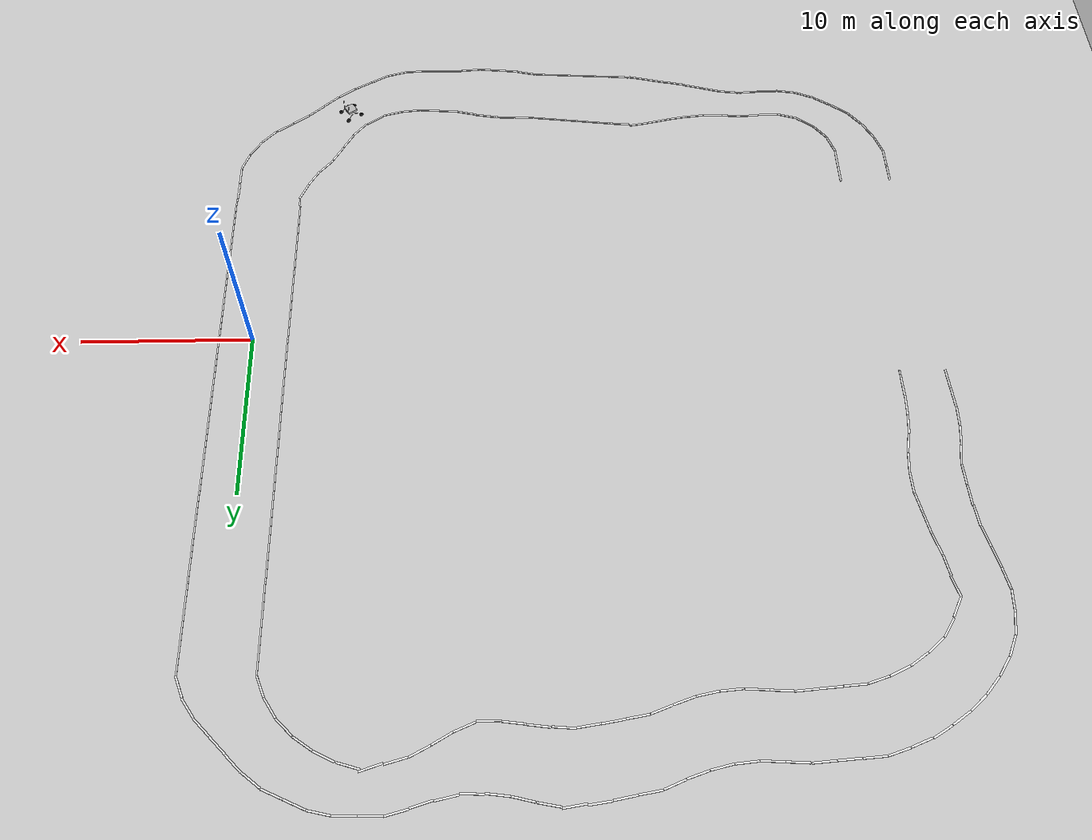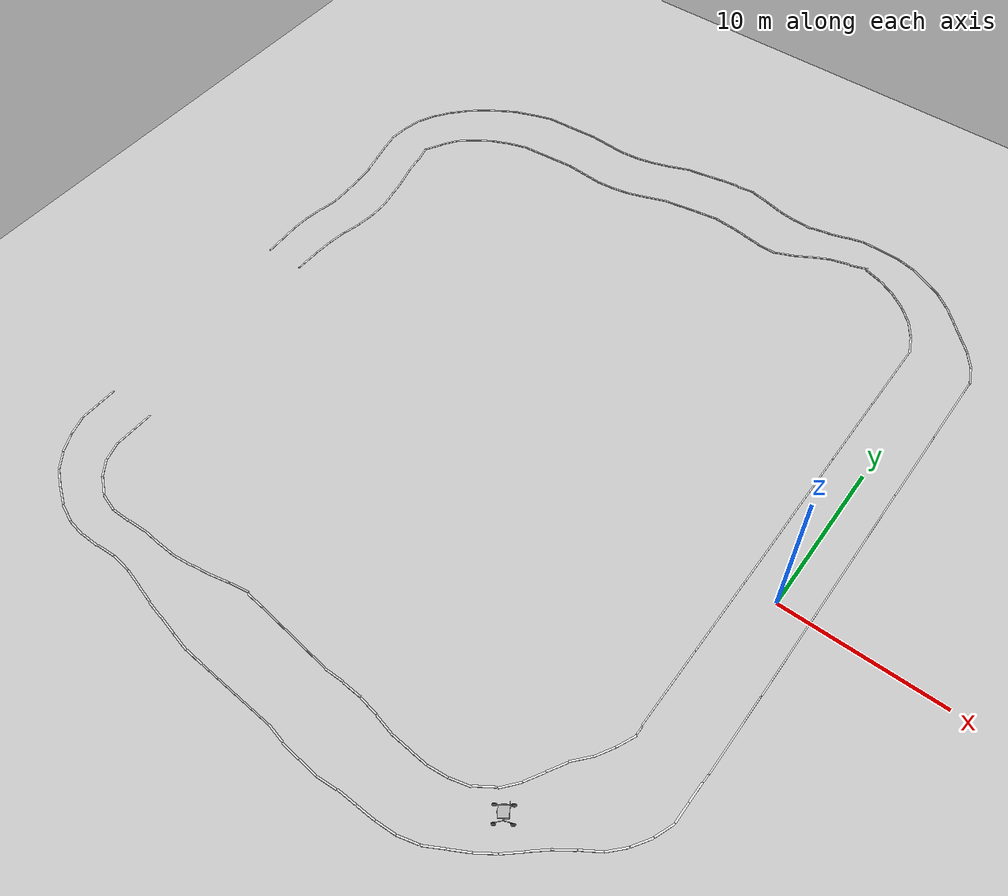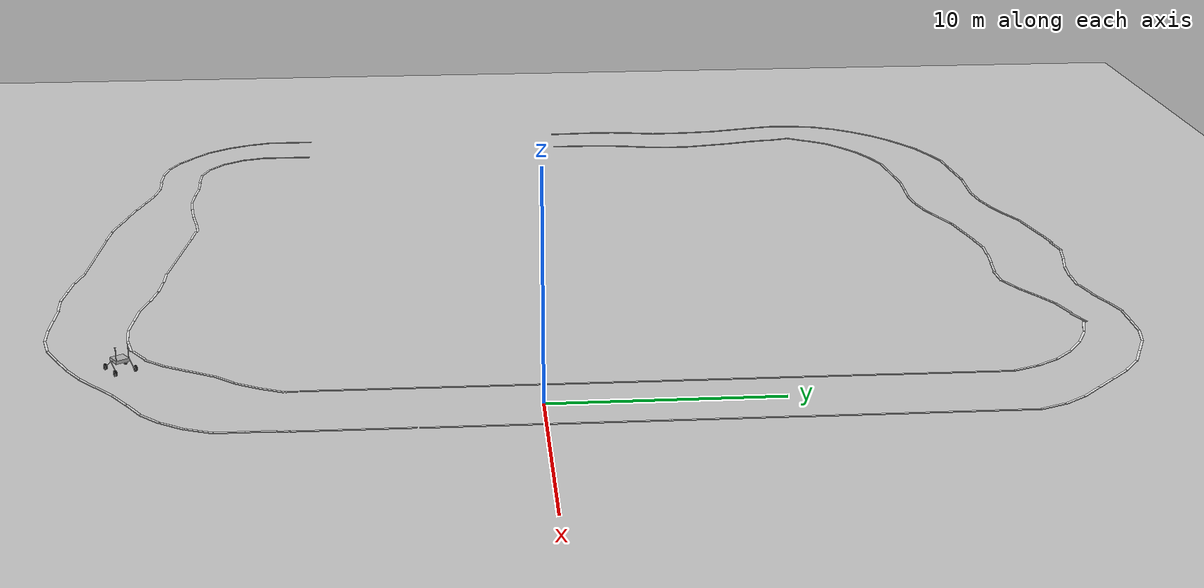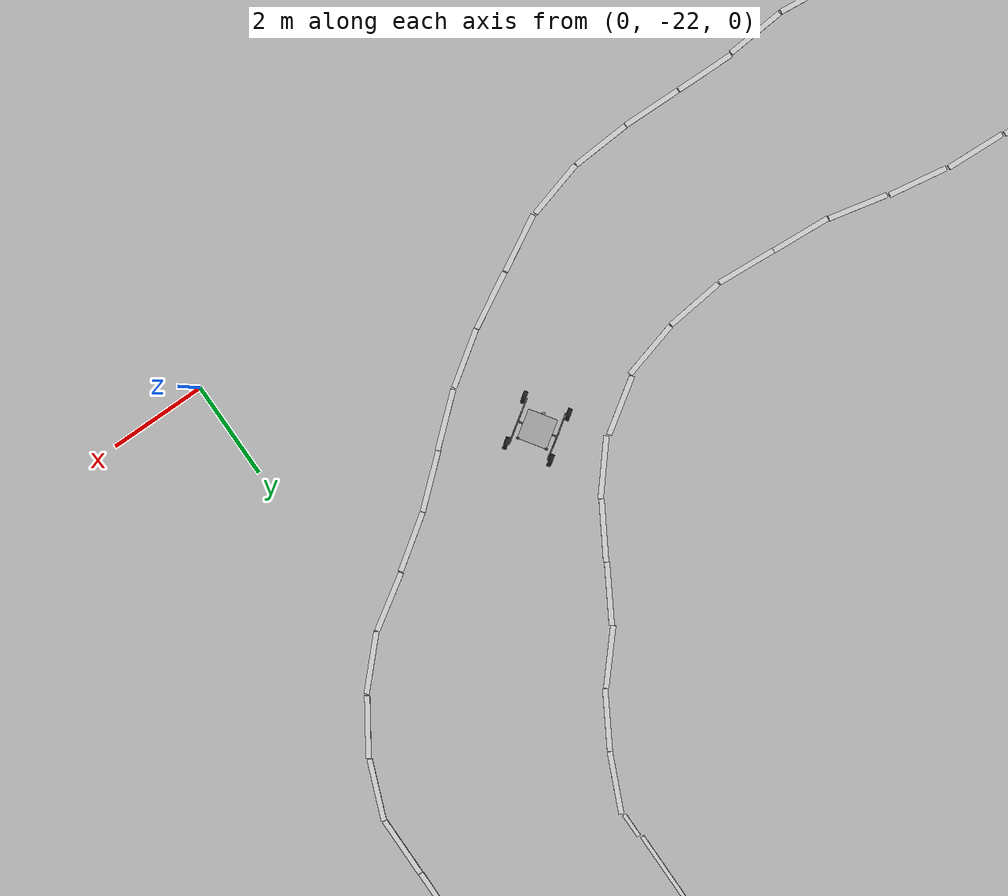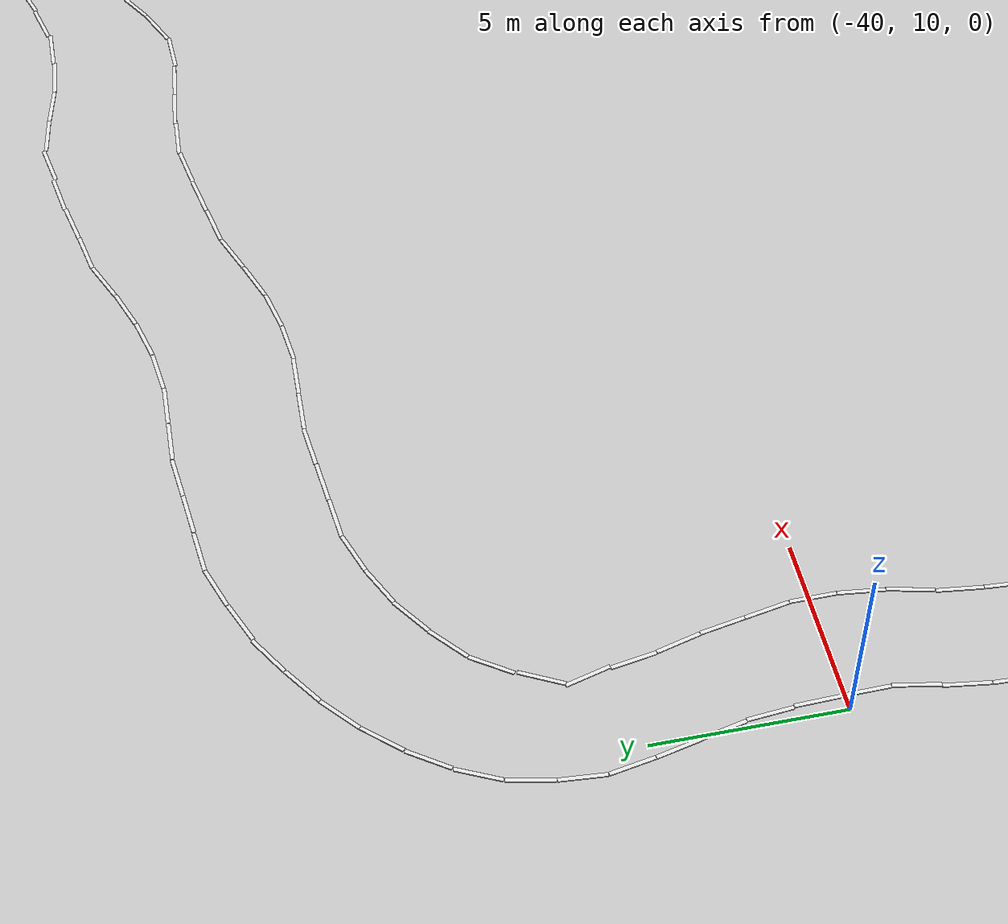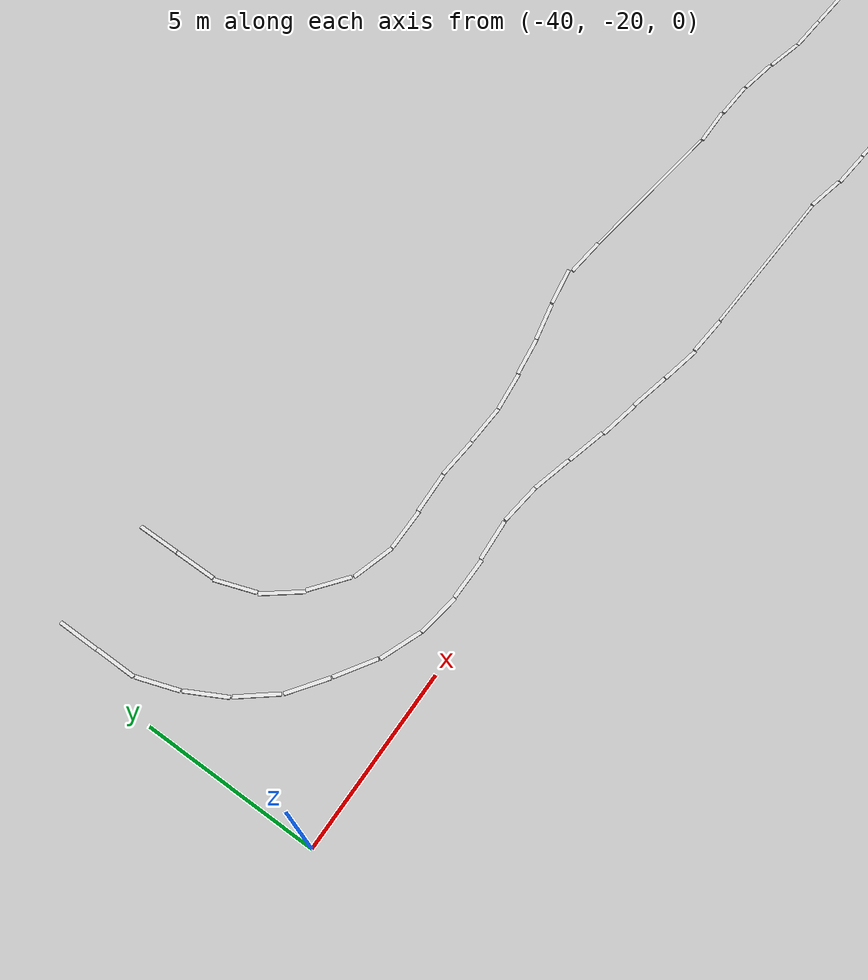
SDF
<sdf version="1.7">
 <world name="default">
  <model name="ground_plane">
   <static>1</static>
   <link name="link">
    <collision name="collision">
     <geometry><plane><normal>0 0 1</normal><size>100 100</size></plane></geometry>
     <surface><friction><ode><mu>100</mu><mu2>50</mu2></ode></friction></surface>
    </collision>
    <visual name="visual">
     <cast_shadows>0</cast_shadows>
     <geometry><plane><normal>0 0 1</normal><size>100 100</size></plane></geometry>
     <material>
      <script><uri>file://media/materials/scripts/gazebo.material</uri><name>Gazebo/Grey</name></script>
     </material>
    </visual>
   </link>
  </model>
  <gravity>0 0 -9.8</gravity>
  <magnetic_field>6e-06 2.3e-05 -4.2e-05</magnetic_field>
  <atmosphere type="adiabatic"/>
  <physics type="ode">
   <max_step_size>0.001</max_step_size>
   <real_time_factor>1</real_time_factor>
   <real_time_update_rate>1000</real_time_update_rate>
  </physics>
  <scene><ambient>0.4 0.4 0.4 1</ambient><background>0.7 0.7 0.7 1</background><shadows>1</shadows></scene>
  <audio><device>default</device></audio>
  <spherical_coordinates>
   <surface_model>EARTH_WGS84</surface_model>
   <latitude_deg>0</latitude_deg>
   <longitude_deg>0</longitude_deg>
   <elevation>0</elevation>
   <heading_deg>0</heading_deg>
  </spherical_coordinates>
  <model name="road_way5m_clone_2">
   <link name="link">
    <inertial>
     <mass>1</mass>
     <inertia>
      <ixx>0.166667</ixx>
      <ixy>0</ixy>
      <ixz>0</ixz>
      <iyy>0.166667</iyy>
      <iyz>0</iyz>
      <izz>0.166667</izz>
     </inertia>
    </inertial>
    <visual name="visual">
     <geometry><box><size>0.08 5 0.03129</size></box></geometry>
     <material>
      <script><name>Gazebo/White</name><uri>file://media/materials/scripts/gazebo.material</uri></script>
      <shader type="pixel"><normal_map>__default__</normal_map></shader>
      <ambient>1 1 1 1</ambient>
      <diffuse>1 1 1 1</diffuse>
      <specular>0 0 0 1</specular>
      <emissive>0 0 0 1</emissive>
     </material>
    </visual>
    <collision name="collision">
     <geometry><box><size>0.01644 0.01348 0.0129</size></box></geometry>
     <surface>
      <friction>
       <ode><mu>1</mu><mu2>1</mu2><fdir1>0 0 0</fdir1><slip1>0</slip1><slip2>0</slip2></ode>
       <torsional>
        <coefficient>1</coefficient>
        <patch_radius>0</patch_radius>
        <surface_radius>0</surface_radius>
        <use_patch_radius>1</use_patch_radius>
        <ode><slip>0</slip></ode>
       </torsional>
      </friction>
      <bounce><restitution_coefficient>0</restitution_coefficient><threshold>1e+06</threshold></bounce>
      <contact>
       <collide_without_contact>0</collide_without_contact>
       <collide_without_contact_bitmask>1</collide_without_contact_bitmask>
       <collide_bitmask>1</collide_bitmask>
       <ode>
        <soft_cfm>0</soft_cfm>
        <soft_erp>0.2</soft_erp>
        <kp>1e+13</kp>
        <kd>1</kd>
        <max_vel>0.01</max_vel>
        <min_depth>0</min_depth>
       </ode>
       <bullet>
        <split_impulse>1</split_impulse>
        <split_impulse_penetration_threshold>-0.01</split_impulse_penetration_threshold>
        <soft_cfm>0</soft_cfm>
        <soft_erp>0.2</soft_erp>
        <kp>1e+13</kp>
        <kd>1</kd>
       </bullet>
      </contact>
     </surface>
    </collision>
   </link>
   <static>0</static>
   <pose>-2.00532 2.54859 0.00645 2e-05 6e-06 -0.004158</pose>
  </model>
  <model name="road_way5m_clone_2_clone">
   <link name="link">
    <inertial>
     <mass>1</mass>
     <inertia>
      <ixx>0.166667</ixx>
      <ixy>0</ixy>
      <ixz>0</ixz>
      <iyy>0.166667</iyy>
      <iyz>0</iyz>
      <izz>0.166667</izz>
     </inertia>
    </inertial>
    <visual name="visual">
     <geometry><box><size>0.08 5 0.03129</size></box></geometry>
     <material>
      <script><name>Gazebo/White</name><uri>file://media/materials/scripts/gazebo.material</uri></script>
      <shader type="pixel"><normal_map>__default__</normal_map></shader>
      <ambient>1 1 1 1</ambient>
      <diffuse>1 1 1 1</diffuse>
      <specular>0 0 0 1</specular>
      <emissive>0 0 0 1</emissive>
     </material>
    </visual>
    <collision name="collision">
     <geometry><box><size>0.01644 0.01348 0.0129</size></box></geometry>
     <surface>
      <friction>
       <ode><mu>1</mu><mu2>1</mu2><fdir1>0 0 0</fdir1><slip1>0</slip1><slip2>0</slip2></ode>
       <torsional>
        <coefficient>1</coefficient>
        <patch_radius>0</patch_radius>
        <surface_radius>0</surface_radius>
        <use_patch_radius>1</use_patch_radius>
        <ode><slip>0</slip></ode>
       </torsional>
      </friction>
      <bounce><restitution_coefficient>0</restitution_coefficient><threshold>1e+06</threshold></bounce>
      <contact>
       <collide_without_contact>0</collide_without_contact>
       <collide_without_contact_bitmask>1</collide_without_contact_bitmask>
       <collide_bitmask>1</collide_bitmask>
       <ode>
        <soft_cfm>0</soft_cfm>
        <soft_erp>0.2</soft_erp>
        <kp>1e+13</kp>
        <kd>1</kd>
        <max_vel>0.01</max_vel>
        <min_depth>0</min_depth>
       </ode>
       <bullet>
        <split_impulse>1</split_impulse>
        <split_impulse_penetration_threshold>-0.01</split_impulse_penetration_threshold>
        <soft_cfm>0</soft_cfm>
        <soft_erp>0.2</soft_erp>
        <kp>1e+13</kp>
        <kd>1</kd>
       </bullet>
      </contact>
     </surface>
    </collision>
   </link>
   <static>0</static>
   <pose>-1.99251 7.51978 0.00645 0 -2e-06 -0.004156</pose>
  </model>
  <model name="road_way5m_clone_2_clone_clone">
   <link name="link">
    <inertial>
     <mass>1</mass>
     <inertia>
      <ixx>0.166667</ixx>
      <ixy>0</ixy>
      <ixz>0</ixz>
      <iyy>0.166667</iyy>
      <iyz>0</iyz>
      <izz>0.166667</izz>
     </inertia>
    </inertial>
    <visual name="visual">
     <geometry><box><size>0.08 5 0.03129</size></box></geometry>
     <material>
      <script><name>Gazebo/White</name><uri>file://media/materials/scripts/gazebo.material</uri></script>
      <shader type="pixel"><normal_map>__default__</normal_map></shader>
      <ambient>1 1 1 1</ambient>
      <diffuse>1 1 1 1</diffuse>
      <specular>0 0 0 1</specular>
      <emissive>0 0 0 1</emissive>
     </material>
    </visual>
    <collision name="collision">
     <geometry><box><size>0.01644 0.01348 0.0129</size></box></geometry>
     <surface>
      <friction>
       <ode><mu>1</mu><mu2>1</mu2><fdir1>0 0 0</fdir1><slip1>0</slip1><slip2>0</slip2></ode>
       <torsional>
        <coefficient>1</coefficient>
        <patch_radius>0</patch_radius>
        <surface_radius>0</surface_radius>
        <use_patch_radius>1</use_patch_radius>
        <ode><slip>0</slip></ode>
       </torsional>
      </friction>
      <bounce><restitution_coefficient>0</restitution_coefficient><threshold>1e+06</threshold></bounce>
      <contact>
       <collide_without_contact>0</collide_without_contact>
       <collide_without_contact_bitmask>1</collide_without_contact_bitmask>
       <collide_bitmask>1</collide_bitmask>
       <ode>
        <soft_cfm>0</soft_cfm>
        <soft_erp>0.2</soft_erp>
        <kp>1e+13</kp>
        <kd>1</kd>
        <max_vel>0.01</max_vel>
        <min_depth>0</min_depth>
       </ode>
       <bullet>
        <split_impulse>1</split_impulse>
        <split_impulse_penetration_threshold>-0.01</split_impulse_penetration_threshold>
        <soft_cfm>0</soft_cfm>
        <soft_erp>0.2</soft_erp>
        <kp>1e+13</kp>
        <kd>1</kd>
       </bullet>
      </contact>
     </surface>
    </collision>
   </link>
   <static>0</static>
   <pose>-1.97512 12.5252 0.00645 -8e-06 -3e-06 -0.004165</pose>
  </model>
  <model name="road_way5m_clone_2_clone_clone_0">
   <link name="link">
    <inertial>
     <mass>1</mass>
     <inertia>
      <ixx>0.166667</ixx>
      <ixy>0</ixy>
      <ixz>0</ixz>
      <iyy>0.166667</iyy>
      <iyz>0</iyz>
      <izz>0.166667</izz>
     </inertia>
    </inertial>
    <visual name="visual">
     <geometry><box><size>0.08 5 0.03129</size></box></geometry>
     <material>
      <script><name>Gazebo/White</name><uri>file://media/materials/scripts/gazebo.material</uri></script>
      <shader type="pixel"><normal_map>__default__</normal_map></shader>
      <ambient>1 1 1 1</ambient>
      <diffuse>1 1 1 1</diffuse>
      <specular>0 0 0 1</specular>
      <emissive>0 0 0 1</emissive>
     </material>
    </visual>
    <collision name="collision">
     <geometry><box><size>0.01644 0.01348 0.0129</size></box></geometry>
     <surface>
      <friction>
       <ode><mu>1</mu><mu2>1</mu2><fdir1>0 0 0</fdir1><slip1>0</slip1><slip2>0</slip2></ode>
       <torsional>
        <coefficient>1</coefficient>
        <patch_radius>0</patch_radius>
        <surface_radius>0</surface_radius>
        <use_patch_radius>1</use_patch_radius>
        <ode><slip>0</slip></ode>
       </torsional>
      </friction>
      <bounce><restitution_coefficient>0</restitution_coefficient><threshold>1e+06</threshold></bounce>
      <contact>
       <collide_without_contact>0</collide_without_contact>
       <collide_without_contact_bitmask>1</collide_without_contact_bitmask>
       <collide_bitmask>1</collide_bitmask>
       <ode>
        <soft_cfm>0</soft_cfm>
        <soft_erp>0.2</soft_erp>
        <kp>1e+13</kp>
        <kd>1</kd>
        <max_vel>0.01</max_vel>
        <min_depth>0</min_depth>
       </ode>
       <bullet>
        <split_impulse>1</split_impulse>
        <split_impulse_penetration_threshold>-0.01</split_impulse_penetration_threshold>
        <soft_cfm>0</soft_cfm>
        <soft_erp>0.2</soft_erp>
        <kp>1e+13</kp>
        <kd>1</kd>
       </bullet>
      </contact>
     </surface>
    </collision>
   </link>
   <static>0</static>
   <pose>-1.94483 17.5127 0.00645 1.4e-05 8e-06 -0.004175</pose>
  </model>
  <model name="road_way5m_clone_2_clone_clone_1">
   <link name="link">
    <inertial>
     <mass>1</mass>
     <inertia>
      <ixx>0.166667</ixx>
      <ixy>0</ixy>
      <ixz>0</ixz>
      <iyy>0.166667</iyy>
      <iyz>0</iyz>
      <izz>0.166667</izz>
     </inertia>
    </inertial>
    <visual name="visual">
     <geometry><box><size>0.08 5 0.03129</size></box></geometry>
     <material>
      <script><name>Gazebo/White</name><uri>file://media/materials/scripts/gazebo.material</uri></script>
      <shader type="pixel"><normal_map>__default__</normal_map></shader>
      <ambient>1 1 1 1</ambient>
      <diffuse>1 1 1 1</diffuse>
      <specular>0 0 0 1</specular>
      <emissive>0 0 0 1</emissive>
     </material>
    </visual>
    <collision name="collision">
     <geometry><box><size>0.01644 0.01348 0.0129</size></box></geometry>
     <surface>
      <friction>
       <ode><mu>1</mu><mu2>1</mu2><fdir1>0 0 0</fdir1><slip1>0</slip1><slip2>0</slip2></ode>
       <torsional>
        <coefficient>1</coefficient>
        <patch_radius>0</patch_radius>
        <surface_radius>0</surface_radius>
        <use_patch_radius>1</use_patch_radius>
        <ode><slip>0</slip></ode>
       </torsional>
      </friction>
      <bounce><restitution_coefficient>0</restitution_coefficient><threshold>1e+06</threshold></bounce>
      <contact>
       <collide_without_contact>0</collide_without_contact>
       <collide_without_contact_bitmask>1</collide_without_contact_bitmask>
       <collide_bitmask>1</collide_bitmask>
       <ode>
        <soft_cfm>0</soft_cfm>
        <soft_erp>0.2</soft_erp>
        <kp>1e+13</kp>
        <kd>1</kd>
        <max_vel>0.01</max_vel>
        <min_depth>0</min_depth>
       </ode>
       <bullet>
        <split_impulse>1</split_impulse>
        <split_impulse_penetration_threshold>-0.01</split_impulse_penetration_threshold>
        <soft_cfm>0</soft_cfm>
        <soft_erp>0.2</soft_erp>
        <kp>1e+13</kp>
        <kd>1</kd>
       </bullet>
      </contact>
     </surface>
    </collision>
   </link>
   <static>0</static>
   <pose>2.00379 2.4916 0.00645 -1e-06 1e-06 -0.004158</pose>
  </model>
  <model name="road_way5m_clone_2_clone_clone_2">
   <link name="link">
    <inertial>
     <mass>1</mass>
     <inertia>
      <ixx>0.166667</ixx>
      <ixy>0</ixy>
      <ixz>0</ixz>
      <iyy>0.166667</iyy>
      <iyz>0</iyz>
      <izz>0.166667</izz>
     </inertia>
    </inertial>
    <visual name="visual">
     <geometry><box><size>0.08 5 0.03129</size></box></geometry>
     <material>
      <script><name>Gazebo/White</name><uri>file://media/materials/scripts/gazebo.material</uri></script>
      <shader type="pixel"><normal_map>__default__</normal_map></shader>
      <ambient>1 1 1 1</ambient>
      <diffuse>1 1 1 1</diffuse>
      <specular>0 0 0 1</specular>
      <emissive>0 0 0 1</emissive>
     </material>
    </visual>
    <collision name="collision">
     <geometry><box><size>0.01644 0.01348 0.0129</size></box></geometry>
     <surface>
      <friction>
       <ode><mu>1</mu><mu2>1</mu2><fdir1>0 0 0</fdir1><slip1>0</slip1><slip2>0</slip2></ode>
       <torsional>
        <coefficient>1</coefficient>
        <patch_radius>0</patch_radius>
        <surface_radius>0</surface_radius>
        <use_patch_radius>1</use_patch_radius>
        <ode><slip>0</slip></ode>
       </torsional>
      </friction>
      <bounce><restitution_coefficient>0</restitution_coefficient><threshold>1e+06</threshold></bounce>
      <contact>
       <collide_without_contact>0</collide_without_contact>
       <collide_without_contact_bitmask>1</collide_without_contact_bitmask>
       <collide_bitmask>1</collide_bitmask>
       <ode>
        <soft_cfm>0</soft_cfm>
        <soft_erp>0.2</soft_erp>
        <kp>1e+13</kp>
        <kd>1</kd>
        <max_vel>0.01</max_vel>
        <min_depth>0</min_depth>
       </ode>
       <bullet>
        <split_impulse>1</split_impulse>
        <split_impulse_penetration_threshold>-0.01</split_impulse_penetration_threshold>
        <soft_cfm>0</soft_cfm>
        <soft_erp>0.2</soft_erp>
        <kp>1e+13</kp>
        <kd>1</kd>
       </bullet>
      </contact>
     </surface>
    </collision>
   </link>
   <static>0</static>
   <pose>2.02475 7.46538 0.00645 -7e-06 -4e-06 -0.004154</pose>
  </model>
  <model name="road_way5m_clone_2_clone_clone_3">
   <link name="link">
    <inertial>
     <mass>1</mass>
     <inertia>
      <ixx>0.166667</ixx>
      <ixy>0</ixy>
      <ixz>0</ixz>
      <iyy>0.166667</iyy>
      <iyz>0</iyz>
      <izz>0.166667</izz>
     </inertia>
    </inertial>
    <visual name="visual">
     <geometry><box><size>0.08 5 0.03129</size></box></geometry>
     <material>
      <script><name>Gazebo/White</name><uri>file://media/materials/scripts/gazebo.material</uri></script>
      <shader type="pixel"><normal_map>__default__</normal_map></shader>
      <ambient>1 1 1 1</ambient>
      <diffuse>1 1 1 1</diffuse>
      <specular>0 0 0 1</specular>
      <emissive>0 0 0 1</emissive>
     </material>
    </visual>
    <collision name="collision">
     <geometry><box><size>0.01644 0.01348 0.0129</size></box></geometry>
     <surface>
      <friction>
       <ode><mu>1</mu><mu2>1</mu2><fdir1>0 0 0</fdir1><slip1>0</slip1><slip2>0</slip2></ode>
       <torsional>
        <coefficient>1</coefficient>
        <patch_radius>0</patch_radius>
        <surface_radius>0</surface_radius>
        <use_patch_radius>1</use_patch_radius>
        <ode><slip>0</slip></ode>
       </torsional>
      </friction>
      <bounce><restitution_coefficient>0</restitution_coefficient><threshold>1e+06</threshold></bounce>
      <contact>
       <collide_without_contact>0</collide_without_contact>
       <collide_without_contact_bitmask>1</collide_without_contact_bitmask>
       <collide_bitmask>1</collide_bitmask>
       <ode>
        <soft_cfm>0</soft_cfm>
        <soft_erp>0.2</soft_erp>
        <kp>1e+13</kp>
        <kd>1</kd>
        <max_vel>0.01</max_vel>
        <min_depth>0</min_depth>
       </ode>
       <bullet>
        <split_impulse>1</split_impulse>
        <split_impulse_penetration_threshold>-0.01</split_impulse_penetration_threshold>
        <soft_cfm>0</soft_cfm>
        <soft_erp>0.2</soft_erp>
        <kp>1e+13</kp>
        <kd>1</kd>
       </bullet>
      </contact>
     </surface>
    </collision>
   </link>
   <static>0</static>
   <pose>2.05809 12.4714 0.00645 -6.6e-05 1e-06 -0.004155</pose>
  </model>
  <model name="road_way5m_clone_2_clone_clone_4">
   <link name="link">
    <inertial>
     <mass>1</mass>
     <inertia>
      <ixx>0.166667</ixx>
      <ixy>0</ixy>
      <ixz>0</ixz>
      <iyy>0.166667</iyy>
      <iyz>0</iyz>
      <izz>0.166667</izz>
     </inertia>
    </inertial>
    <visual name="visual">
     <geometry><box><size>0.08 5 0.03129</size></box></geometry>
     <material>
      <script><name>Gazebo/White</name><uri>file://media/materials/scripts/gazebo.material</uri></script>
      <shader type="pixel"><normal_map>__default__</normal_map></shader>
      <ambient>1 1 1 1</ambient>
      <diffuse>1 1 1 1</diffuse>
      <specular>0 0 0 1</specular>
      <emissive>0 0 0 1</emissive>
     </material>
    </visual>
    <collision name="collision">
     <geometry><box><size>0.01644 0.01348 0.0129</size></box></geometry>
     <surface>
      <friction>
       <ode><mu>1</mu><mu2>1</mu2><fdir1>0 0 0</fdir1><slip1>0</slip1><slip2>0</slip2></ode>
       <torsional>
        <coefficient>1</coefficient>
        <patch_radius>0</patch_radius>
        <surface_radius>0</surface_radius>
        <use_patch_radius>1</use_patch_radius>
        <ode><slip>0</slip></ode>
       </torsional>
      </friction>
      <bounce><restitution_coefficient>0</restitution_coefficient><threshold>1e+06</threshold></bounce>
      <contact>
       <collide_without_contact>0</collide_without_contact>
       <collide_without_contact_bitmask>1</collide_without_contact_bitmask>
       <collide_bitmask>1</collide_bitmask>
       <ode>
        <soft_cfm>0</soft_cfm>
        <soft_erp>0.2</soft_erp>
        <kp>1e+13</kp>
        <kd>1</kd>
        <max_vel>0.01</max_vel>
        <min_depth>0</min_depth>
       </ode>
       <bullet>
        <split_impulse>1</split_impulse>
        <split_impulse_penetration_threshold>-0.01</split_impulse_penetration_threshold>
        <soft_cfm>0</soft_cfm>
        <soft_erp>0.2</soft_erp>
        <kp>1e+13</kp>
        <kd>1</kd>
       </bullet>
      </contact>
     </surface>
    </collision>
   </link>
   <static>0</static>
   <pose>2.07328 17.4807 0.00645 1.4e-05 2.4e-05 -0.004155</pose>
  </model>
  <model name="road_way">
   <link name="link">
    <inertial>
     <mass>1</mass>
     <inertia>
      <ixx>0.166667</ixx>
      <ixy>0</ixy>
      <ixz>0</ixz>
      <iyy>0.166667</iyy>
      <iyz>0</iyz>
      <izz>0.166667</izz>
     </inertia>
    </inertial>
    <visual name="visual">
     <geometry><box><size>0.106644 1.22348 0.03129</size></box></geometry>
     <material>
      <script><name>Gazebo/White</name><uri>file://media/materials/scripts/gazebo.material</uri></script>
      <shader type="pixel"><normal_map>__default__</normal_map></shader>
      <ambient>1 1 1 1</ambient>
      <diffuse>1 1 1 1</diffuse>
      <specular>0 0 0 1</specular>
      <emissive>0 0 0 1</emissive>
     </material>
    </visual>
    <collision name="collision">
     <geometry><box><size>0.10644 1.22348 0.03129</size></box></geometry>
     <surface>
      <friction>
       <ode><mu>1</mu><mu2>1</mu2><fdir1>0 0 0</fdir1><slip1>0</slip1><slip2>0</slip2></ode>
       <torsional>
        <coefficient>1</coefficient>
        <patch_radius>0</patch_radius>
        <surface_radius>0</surface_radius>
        <use_patch_radius>1</use_patch_radius>
        <ode><slip>0</slip></ode>
       </torsional>
      </friction>
      <bounce><restitution_coefficient>0</restitution_coefficient><threshold>1e+06</threshold></bounce>
      <contact>
       <collide_without_contact>0</collide_without_contact>
       <collide_without_contact_bitmask>1</collide_without_contact_bitmask>
       <collide_bitmask>1</collide_bitmask>
       <ode>
        <soft_cfm>0</soft_cfm>
        <soft_erp>0.2</soft_erp>
        <kp>1e+13</kp>
        <kd>1</kd>
        <max_vel>0.01</max_vel>
        <min_depth>0</min_depth>
       </ode>
       <bullet>
        <split_impulse>1</split_impulse>
        <split_impulse_penetration_threshold>-0.01</split_impulse_penetration_threshold>
        <soft_cfm>0</soft_cfm>
        <soft_erp>0.2</soft_erp>
        <kp>1e+13</kp>
        <kd>1</kd>
       </bullet>
      </contact>
     </surface>
    </collision>
   </link>
   <static>0</static>
   <pose>-2.15284 20.5543 0.015638 -1.1e-05 -0 0.387713</pose>
  </model>
  <model name="road_way_clone">
   <link name="link">
    <inertial>
     <mass>1</mass>
     <inertia>
      <ixx>0.166667</ixx>
      <ixy>0</ixy>
      <ixz>0</ixz>
      <iyy>0.166667</iyy>
      <iyz>0</iyz>
      <izz>0.166667</izz>
     </inertia>
    </inertial>
    <visual name="visual">
     <geometry><box><size>0.106644 1.22348 0.03129</size></box></geometry>
     <material>
      <script><name>Gazebo/White</name><uri>file://media/materials/scripts/gazebo.material</uri></script>
      <shader type="pixel"><normal_map>__default__</normal_map></shader>
      <ambient>1 1 1 1</ambient>
      <diffuse>1 1 1 1</diffuse>
      <specular>0 0 0 1</specular>
      <emissive>0 0 0 1</emissive>
     </material>
    </visual>
    <collision name="collision">
     <geometry><box><size>0.10644 1.22348 0.03129</size></box></geometry>
     <surface>
      <friction>
       <ode><mu>1</mu><mu2>1</mu2><fdir1>0 0 0</fdir1><slip1>0</slip1><slip2>0</slip2></ode>
       <torsional>
        <coefficient>1</coefficient>
        <patch_radius>0</patch_radius>
        <surface_radius>0</surface_radius>
        <use_patch_radius>1</use_patch_radius>
        <ode><slip>0</slip></ode>
       </torsional>
      </friction>
      <bounce><restitution_coefficient>0</restitution_coefficient><threshold>1e+06</threshold></bounce>
      <contact>
       <collide_without_contact>0</collide_without_contact>
       <collide_without_contact_bitmask>1</collide_without_contact_bitmask>
       <collide_bitmask>1</collide_bitmask>
       <ode>
        <soft_cfm>0</soft_cfm>
        <soft_erp>0.2</soft_erp>
        <kp>1e+13</kp>
        <kd>1</kd>
        <max_vel>0.01</max_vel>
        <min_depth>0</min_depth>
       </ode>
       <bullet>
        <split_impulse>1</split_impulse>
        <split_impulse_penetration_threshold>-0.01</split_impulse_penetration_threshold>
        <soft_cfm>0</soft_cfm>
        <soft_erp>0.2</soft_erp>
        <kp>1e+13</kp>
        <kd>1</kd>
       </bullet>
      </contact>
     </surface>
    </collision>
   </link>
   <static>0</static>
   <pose>-2.71472 21.6521 0.015638 -1.1e-05 0 0.572003</pose>
  </model>
  <model name="road_way_clone_clone">
   <link name="link">
    <inertial>
     <mass>1</mass>
     <inertia>
      <ixx>0.166667</ixx>
      <ixy>0</ixy>
      <ixz>0</ixz>
      <iyy>0.166667</iyy>
      <iyz>0</iyz>
      <izz>0.166667</izz>
     </inertia>
    </inertial>
    <visual name="visual">
     <geometry><box><size>0.106644 1.22348 0.03129</size></box></geometry>
     <material>
      <script><name>Gazebo/White</name><uri>file://media/materials/scripts/gazebo.material</uri></script>
      <shader type="pixel"><normal_map>__default__</normal_map></shader>
      <ambient>1 1 1 1</ambient>
      <diffuse>1 1 1 1</diffuse>
      <specular>0 0 0 1</specular>
      <emissive>0 0 0 1</emissive>
     </material>
    </visual>
    <collision name="collision">
     <geometry><box><size>0.10644 1.22348 0.03129</size></box></geometry>
     <surface>
      <friction>
       <ode><mu>1</mu><mu2>1</mu2><fdir1>0 0 0</fdir1><slip1>0</slip1><slip2>0</slip2></ode>
       <torsional>
        <coefficient>1</coefficient>
        <patch_radius>0</patch_radius>
        <surface_radius>0</surface_radius>
        <use_patch_radius>1</use_patch_radius>
        <ode><slip>0</slip></ode>
       </torsional>
      </friction>
      <bounce><restitution_coefficient>0</restitution_coefficient><threshold>1e+06</threshold></bounce>
      <contact>
       <collide_without_contact>0</collide_without_contact>
       <collide_without_contact_bitmask>1</collide_without_contact_bitmask>
       <collide_bitmask>1</collide_bitmask>
       <ode>
        <soft_cfm>0</soft_cfm>
        <soft_erp>0.2</soft_erp>
        <kp>1e+13</kp>
        <kd>1</kd>
        <max_vel>0.01</max_vel>
        <min_depth>0</min_depth>
       </ode>
       <bullet>
        <split_impulse>1</split_impulse>
        <split_impulse_penetration_threshold>-0.01</split_impulse_penetration_threshold>
        <soft_cfm>0</soft_cfm>
        <soft_erp>0.2</soft_erp>
        <kp>1e+13</kp>
        <kd>1</kd>
       </bullet>
      </contact>
     </surface>
    </collision>
   </link>
   <static>0</static>
   <pose>-3.48134 22.6105 0.015638 -1.1e-05 -0 0.786275</pose>
  </model>
  <model name="road_way_clone_clone_0">
   <link name="link">
    <inertial>
     <mass>1</mass>
     <inertia>
      <ixx>0.166667</ixx>
      <ixy>0</ixy>
      <ixz>0</ixz>
      <iyy>0.166667</iyy>
      <iyz>0</iyz>
      <izz>0.166667</izz>
     </inertia>
    </inertial>
    <visual name="visual">
     <geometry><box><size>0.106644 1.22348 0.03129</size></box></geometry>
     <material>
      <script><name>Gazebo/White</name><uri>file://media/materials/scripts/gazebo.material</uri></script>
      <shader type="pixel"><normal_map>__default__</normal_map></shader>
      <ambient>1 1 1 1</ambient>
      <diffuse>1 1 1 1</diffuse>
      <specular>0 0 0 1</specular>
      <emissive>0 0 0 1</emissive>
     </material>
    </visual>
    <collision name="collision">
     <geometry><box><size>0.10644 1.22348 0.03129</size></box></geometry>
     <surface>
      <friction>
       <ode><mu>1</mu><mu2>1</mu2><fdir1>0 0 0</fdir1><slip1>0</slip1><slip2>0</slip2></ode>
       <torsional>
        <coefficient>1</coefficient>
        <patch_radius>0</patch_radius>
        <surface_radius>0</surface_radius>
        <use_patch_radius>1</use_patch_radius>
        <ode><slip>0</slip></ode>
       </torsional>
      </friction>
      <bounce><restitution_coefficient>0</restitution_coefficient><threshold>1e+06</threshold></bounce>
      <contact>
       <collide_without_contact>0</collide_without_contact>
       <collide_without_contact_bitmask>1</collide_without_contact_bitmask>
       <collide_bitmask>1</collide_bitmask>
       <ode>
        <soft_cfm>0</soft_cfm>
        <soft_erp>0.2</soft_erp>
        <kp>1e+13</kp>
        <kd>1</kd>
        <max_vel>0.01</max_vel>
        <min_depth>0</min_depth>
       </ode>
       <bullet>
        <split_impulse>1</split_impulse>
        <split_impulse_penetration_threshold>-0.01</split_impulse_penetration_threshold>
        <soft_cfm>0</soft_cfm>
        <soft_erp>0.2</soft_erp>
        <kp>1e+13</kp>
        <kd>1</kd>
       </bullet>
      </contact>
     </surface>
    </collision>
   </link>
   <static>0</static>
   <pose>1.87739 20.5104 0.015638 -1.1e-05 0 0.387079</pose>
  </model>
  <model name="road_way_clone_clone_1">
   <link name="link">
    <inertial>
     <mass>1</mass>
     <inertia>
      <ixx>0.166667</ixx>
      <ixy>0</ixy>
      <ixz>0</ixz>
      <iyy>0.166667</iyy>
      <iyz>0</iyz>
      <izz>0.166667</izz>
     </inertia>
    </inertial>
    <visual name="visual">
     <geometry><box><size>0.106644 1.22348 0.03129</size></box></geometry>
     <material>
      <script><name>Gazebo/White</name><uri>file://media/materials/scripts/gazebo.material</uri></script>
      <shader type="pixel"><normal_map>__default__</normal_map></shader>
      <ambient>1 1 1 1</ambient>
      <diffuse>1 1 1 1</diffuse>
      <specular>0 0 0 1</specular>
      <emissive>0 0 0 1</emissive>
     </material>
    </visual>
    <collision name="collision">
     <geometry><box><size>0.10644 1.22348 0.03129</size></box></geometry>
     <surface>
      <friction>
       <ode><mu>1</mu><mu2>1</mu2><fdir1>0 0 0</fdir1><slip1>0</slip1><slip2>0</slip2></ode>
       <torsional>
        <coefficient>1</coefficient>
        <patch_radius>0</patch_radius>
        <surface_radius>0</surface_radius>
        <use_patch_radius>1</use_patch_radius>
        <ode><slip>0</slip></ode>
       </torsional>
      </friction>
      <bounce><restitution_coefficient>0</restitution_coefficient><threshold>1e+06</threshold></bounce>
      <contact>
       <collide_without_contact>0</collide_without_contact>
       <collide_without_contact_bitmask>1</collide_without_contact_bitmask>
       <collide_bitmask>1</collide_bitmask>
       <ode>
        <soft_cfm>0</soft_cfm>
        <soft_erp>0.2</soft_erp>
        <kp>1e+13</kp>
        <kd>1</kd>
        <max_vel>0.01</max_vel>
        <min_depth>0</min_depth>
       </ode>
       <bullet>
        <split_impulse>1</split_impulse>
        <split_impulse_penetration_threshold>-0.01</split_impulse_penetration_threshold>
        <soft_cfm>0</soft_cfm>
        <soft_erp>0.2</soft_erp>
        <kp>1e+13</kp>
        <kd>1</kd>
       </bullet>
      </contact>
     </surface>
    </collision>
   </link>
   <static>0</static>
   <pose>1.31368 21.5981 0.015639 1.1e-05 -0 0.610833</pose>
  </model>
  <model name="road_way_clone_clone_clone">
   <link name="link">
    <inertial>
     <mass>1</mass>
     <inertia>
      <ixx>0.166667</ixx>
      <ixy>0</ixy>
      <ixz>0</ixz>
      <iyy>0.166667</iyy>
      <iyz>0</iyz>
      <izz>0.166667</izz>
     </inertia>
    </inertial>
    <visual name="visual">
     <geometry><box><size>0.106644 1.22348 0.03129</size></box></geometry>
     <material>
      <script><name>Gazebo/White</name><uri>file://media/materials/scripts/gazebo.material</uri></script>
      <shader type="pixel"><normal_map>__default__</normal_map></shader>
      <ambient>1 1 1 1</ambient>
      <diffuse>1 1 1 1</diffuse>
      <specular>0 0 0 1</specular>
      <emissive>0 0 0 1</emissive>
     </material>
    </visual>
    <collision name="collision">
     <geometry><box><size>0.10644 1.22348 0.03129</size></box></geometry>
     <surface>
      <friction>
       <ode><mu>1</mu><mu2>1</mu2><fdir1>0 0 0</fdir1><slip1>0</slip1><slip2>0</slip2></ode>
       <torsional>
        <coefficient>1</coefficient>
        <patch_radius>0</patch_radius>
        <surface_radius>0</surface_radius>
        <use_patch_radius>1</use_patch_radius>
        <ode><slip>0</slip></ode>
       </torsional>
      </friction>
      <bounce><restitution_coefficient>0</restitution_coefficient><threshold>1e+06</threshold></bounce>
      <contact>
       <collide_without_contact>0</collide_without_contact>
       <collide_without_contact_bitmask>1</collide_without_contact_bitmask>
       <collide_bitmask>1</collide_bitmask>
       <ode>
        <soft_cfm>0</soft_cfm>
        <soft_erp>0.2</soft_erp>
        <kp>1e+13</kp>
        <kd>1</kd>
        <max_vel>0.01</max_vel>
        <min_depth>0</min_depth>
       </ode>
       <bullet>
        <split_impulse>1</split_impulse>
        <split_impulse_penetration_threshold>-0.01</split_impulse_penetration_threshold>
        <soft_cfm>0</soft_cfm>
        <soft_erp>0.2</soft_erp>
        <kp>1e+13</kp>
        <kd>1</kd>
       </bullet>
      </contact>
     </surface>
    </collision>
   </link>
   <static>0</static>
   <pose>0.537005 22.5481 0.015639 1e-05 -0 0.780648</pose>
  </model>
  <model name="road_way_clone_clone_clone_clone">
   <link name="link">
    <inertial>
     <mass>1</mass>
     <inertia>
      <ixx>0.166667</ixx>
      <ixy>0</ixy>
      <ixz>0</ixz>
      <iyy>0.166667</iyy>
      <iyz>0</iyz>
      <izz>0.166667</izz>
     </inertia>
    </inertial>
    <visual name="visual">
     <geometry><box><size>0.106644 1.22348 0.03129</size></box></geometry>
     <material>
      <script><name>Gazebo/White</name><uri>file://media/materials/scripts/gazebo.material</uri></script>
      <shader type="pixel"><normal_map>__default__</normal_map></shader>
      <ambient>1 1 1 1</ambient>
      <diffuse>1 1 1 1</diffuse>
      <specular>0 0 0 1</specular>
      <emissive>0 0 0 1</emissive>
     </material>
    </visual>
    <collision name="collision">
     <geometry><box><size>0.10644 1.22348 0.03129</size></box></geometry>
     <surface>
      <friction>
       <ode><mu>1</mu><mu2>1</mu2><fdir1>0 0 0</fdir1><slip1>0</slip1><slip2>0</slip2></ode>
       <torsional>
        <coefficient>1</coefficient>
        <patch_radius>0</patch_radius>
        <surface_radius>0</surface_radius>
        <use_patch_radius>1</use_patch_radius>
        <ode><slip>0</slip></ode>
       </torsional>
      </friction>
      <bounce><restitution_coefficient>0</restitution_coefficient><threshold>1e+06</threshold></bounce>
      <contact>
       <collide_without_contact>0</collide_without_contact>
       <collide_without_contact_bitmask>1</collide_without_contact_bitmask>
       <collide_bitmask>1</collide_bitmask>
       <ode>
        <soft_cfm>0</soft_cfm>
        <soft_erp>0.2</soft_erp>
        <kp>1e+13</kp>
        <kd>1</kd>
        <max_vel>0.01</max_vel>
        <min_depth>0</min_depth>
       </ode>
       <bullet>
        <split_impulse>1</split_impulse>
        <split_impulse_penetration_threshold>-0.01</split_impulse_penetration_threshold>
        <soft_cfm>0</soft_cfm>
        <soft_erp>0.2</soft_erp>
        <kp>1e+13</kp>
        <kd>1</kd>
       </bullet>
      </contact>
     </surface>
    </collision>
   </link>
   <static>0</static>
   <pose>-0.31789 23.4234 0.015639 1e-05 0 0.780671</pose>
  </model>
  <model name="road_way_clone_clone_clone_clone_clone">
   <link name="link">
    <inertial>
     <mass>1</mass>
     <inertia>
      <ixx>0.166667</ixx>
      <ixy>0</ixy>
      <ixz>0</ixz>
      <iyy>0.166667</iyy>
      <iyz>0</iyz>
      <izz>0.166667</izz>
     </inertia>
    </inertial>
    <visual name="visual">
     <geometry><box><size>0.106644 1.22348 0.03129</size></box></geometry>
     <material>
      <script><name>Gazebo/White</name><uri>file://media/materials/scripts/gazebo.material</uri></script>
      <shader type="pixel"><normal_map>__default__</normal_map></shader>
      <ambient>1 1 1 1</ambient>
      <diffuse>1 1 1 1</diffuse>
      <specular>0 0 0 1</specular>
      <emissive>0 0 0 1</emissive>
     </material>
    </visual>
    <collision name="collision">
     <geometry><box><size>0.10644 1.22348 0.03129</size></box></geometry>
     <surface>
      <friction>
       <ode><mu>1</mu><mu2>1</mu2><fdir1>0 0 0</fdir1><slip1>0</slip1><slip2>0</slip2></ode>
       <torsional>
        <coefficient>1</coefficient>
        <patch_radius>0</patch_radius>
        <surface_radius>0</surface_radius>
        <use_patch_radius>1</use_patch_radius>
        <ode><slip>0</slip></ode>
       </torsional>
      </friction>
      <bounce><restitution_coefficient>0</restitution_coefficient><threshold>1e+06</threshold></bounce>
      <contact>
       <collide_without_contact>0</collide_without_contact>
       <collide_without_contact_bitmask>1</collide_without_contact_bitmask>
       <collide_bitmask>1</collide_bitmask>
       <ode>
        <soft_cfm>0</soft_cfm>
        <soft_erp>0.2</soft_erp>
        <kp>1e+13</kp>
        <kd>1</kd>
        <max_vel>0.01</max_vel>
        <min_depth>0</min_depth>
       </ode>
       <bullet>
        <split_impulse>1</split_impulse>
        <split_impulse_penetration_threshold>-0.01</split_impulse_penetration_threshold>
        <soft_cfm>0</soft_cfm>
        <soft_erp>0.2</soft_erp>
        <kp>1e+13</kp>
        <kd>1</kd>
       </bullet>
      </contact>
     </surface>
    </collision>
   </link>
   <static>0</static>
   <pose>-1.16894 24.3025 0.015638 1.1e-05 -0 0.780651</pose>
  </model>
  <model name="road_way_clone_clone_clone_clone_clone_clone">
   <link name="link">
    <inertial>
     <mass>1</mass>
     <inertia>
      <ixx>0.166667</ixx>
      <ixy>0</ixy>
      <ixz>0</ixz>
      <iyy>0.166667</iyy>
      <iyz>0</iyz>
      <izz>0.166667</izz>
     </inertia>
    </inertial>
    <visual name="visual">
     <geometry><box><size>0.106644 1.22348 0.03129</size></box></geometry>
     <material>
      <script><name>Gazebo/White</name><uri>file://media/materials/scripts/gazebo.material</uri></script>
      <shader type="pixel"><normal_map>__default__</normal_map></shader>
      <ambient>1 1 1 1</ambient>
      <diffuse>1 1 1 1</diffuse>
      <specular>0 0 0 1</specular>
      <emissive>0 0 0 1</emissive>
     </material>
    </visual>
    <collision name="collision">
     <geometry><box><size>0.10644 1.22348 0.03129</size></box></geometry>
     <surface>
      <friction>
       <ode><mu>1</mu><mu2>1</mu2><fdir1>0 0 0</fdir1><slip1>0</slip1><slip2>0</slip2></ode>
       <torsional>
        <coefficient>1</coefficient>
        <patch_radius>0</patch_radius>
        <surface_radius>0</surface_radius>
        <use_patch_radius>1</use_patch_radius>
        <ode><slip>0</slip></ode>
       </torsional>
      </friction>
      <bounce><restitution_coefficient>0</restitution_coefficient><threshold>1e+06</threshold></bounce>
      <contact>
       <collide_without_contact>0</collide_without_contact>
       <collide_without_contact_bitmask>1</collide_without_contact_bitmask>
       <collide_bitmask>1</collide_bitmask>
       <ode>
        <soft_cfm>0</soft_cfm>
        <soft_erp>0.2</soft_erp>
        <kp>1e+13</kp>
        <kd>1</kd>
        <max_vel>0.01</max_vel>
        <min_depth>0</min_depth>
       </ode>
       <bullet>
        <split_impulse>1</split_impulse>
        <split_impulse_penetration_threshold>-0.01</split_impulse_penetration_threshold>
        <soft_cfm>0</soft_cfm>
        <soft_erp>0.2</soft_erp>
        <kp>1e+13</kp>
        <kd>1</kd>
       </bullet>
      </contact>
     </surface>
    </collision>
   </link>
   <static>0</static>
   <pose>-2.09518 25.1072 0.015638 1.1e-05 -0 0.907832</pose>
  </model>
  <model name="road_way_clone_clone_clone_clone_clone_clone_0">
   <link name="link">
    <inertial>
     <mass>1</mass>
     <inertia>
      <ixx>0.166667</ixx>
      <ixy>0</ixy>
      <ixz>0</ixz>
      <iyy>0.166667</iyy>
      <iyz>0</iyz>
      <izz>0.166667</izz>
     </inertia>
    </inertial>
    <visual name="visual">
     <geometry><box><size>0.106644 1.22348 0.03129</size></box></geometry>
     <material>
      <script><name>Gazebo/White</name><uri>file://media/materials/scripts/gazebo.material</uri></script>
      <shader type="pixel"><normal_map>__default__</normal_map></shader>
      <ambient>1 1 1 1</ambient>
      <diffuse>1 1 1 1</diffuse>
      <specular>0 0 0 1</specular>
      <emissive>0 0 0 1</emissive>
     </material>
    </visual>
    <collision name="collision">
     <geometry><box><size>0.10644 1.22348 0.03129</size></box></geometry>
     <surface>
      <friction>
       <ode><mu>1</mu><mu2>1</mu2><fdir1>0 0 0</fdir1><slip1>0</slip1><slip2>0</slip2></ode>
       <torsional>
        <coefficient>1</coefficient>
        <patch_radius>0</patch_radius>
        <surface_radius>0</surface_radius>
        <use_patch_radius>1</use_patch_radius>
        <ode><slip>0</slip></ode>
       </torsional>
      </friction>
      <bounce><restitution_coefficient>0</restitution_coefficient><threshold>1e+06</threshold></bounce>
      <contact>
       <collide_without_contact>0</collide_without_contact>
       <collide_without_contact_bitmask>1</collide_without_contact_bitmask>
       <collide_bitmask>1</collide_bitmask>
       <ode>
        <soft_cfm>0</soft_cfm>
        <soft_erp>0.2</soft_erp>
        <kp>1e+13</kp>
        <kd>1</kd>
        <max_vel>0.01</max_vel>
        <min_depth>0</min_depth>
       </ode>
       <bullet>
        <split_impulse>1</split_impulse>
        <split_impulse_penetration_threshold>-0.01</split_impulse_penetration_threshold>
        <soft_cfm>0</soft_cfm>
        <soft_erp>0.2</soft_erp>
        <kp>1e+13</kp>
        <kd>1</kd>
       </bullet>
      </contact>
     </surface>
    </collision>
   </link>
   <static>0</static>
   <pose>-3.13391 25.7568 0.015638 1.1e-05 -0 1.14894</pose>
  </model>
  <model name="road_way_clone_clone_clone_0">
   <link name="link">
    <inertial>
     <mass>1</mass>
     <inertia>
      <ixx>0.166667</ixx>
      <ixy>0</ixy>
      <ixz>0</ixz>
      <iyy>0.166667</iyy>
      <iyz>0</iyz>
      <izz>0.166667</izz>
     </inertia>
    </inertial>
    <visual name="visual">
     <geometry><box><size>0.106644 1.22348 0.03129</size></box></geometry>
     <material>
      <script><name>Gazebo/White</name><uri>file://media/materials/scripts/gazebo.material</uri></script>
      <shader type="pixel"><normal_map>__default__</normal_map></shader>
      <ambient>1 1 1 1</ambient>
      <diffuse>1 1 1 1</diffuse>
      <specular>0 0 0 1</specular>
      <emissive>0 0 0 1</emissive>
     </material>
    </visual>
    <collision name="collision">
     <geometry><box><size>0.10644 1.22348 0.03129</size></box></geometry>
     <surface>
      <friction>
       <ode><mu>1</mu><mu2>1</mu2><fdir1>0 0 0</fdir1><slip1>0</slip1><slip2>0</slip2></ode>
       <torsional>
        <coefficient>1</coefficient>
        <patch_radius>0</patch_radius>
        <surface_radius>0</surface_radius>
        <use_patch_radius>1</use_patch_radius>
        <ode><slip>0</slip></ode>
       </torsional>
      </friction>
      <bounce><restitution_coefficient>0</restitution_coefficient><threshold>1e+06</threshold></bounce>
      <contact>
       <collide_without_contact>0</collide_without_contact>
       <collide_without_contact_bitmask>1</collide_without_contact_bitmask>
       <collide_bitmask>1</collide_bitmask>
       <ode>
        <soft_cfm>0</soft_cfm>
        <soft_erp>0.2</soft_erp>
        <kp>1e+13</kp>
        <kd>1</kd>
        <max_vel>0.01</max_vel>
        <min_depth>0</min_depth>
       </ode>
       <bullet>
        <split_impulse>1</split_impulse>
        <split_impulse_penetration_threshold>-0.01</split_impulse_penetration_threshold>
        <soft_cfm>0</soft_cfm>
        <soft_erp>0.2</soft_erp>
        <kp>1e+13</kp>
        <kd>1</kd>
       </bullet>
      </contact>
     </surface>
    </collision>
   </link>
   <static>0</static>
   <pose>-4.44147 23.4137 0.015638 -1.1e-05 0 0.963623</pose>
  </model>
  <model name="road_way_clone_clone_clone_0_clone">
   <link name="link">
    <inertial>
     <mass>1</mass>
     <inertia>
      <ixx>0.166667</ixx>
      <ixy>0</ixy>
      <ixz>0</ixz>
      <iyy>0.166667</iyy>
      <iyz>0</iyz>
      <izz>0.166667</izz>
     </inertia>
    </inertial>
    <visual name="visual">
     <geometry><box><size>0.106644 1.22348 0.03129</size></box></geometry>
     <material>
      <script><name>Gazebo/White</name><uri>file://media/materials/scripts/gazebo.material</uri></script>
      <shader type="pixel"><normal_map>__default__</normal_map></shader>
      <ambient>1 1 1 1</ambient>
      <diffuse>1 1 1 1</diffuse>
      <specular>0 0 0 1</specular>
      <emissive>0 0 0 1</emissive>
     </material>
    </visual>
    <collision name="collision">
     <geometry><box><size>0.10644 1.22348 0.03129</size></box></geometry>
     <surface>
      <friction>
       <ode><mu>1</mu><mu2>1</mu2><fdir1>0 0 0</fdir1><slip1>0</slip1><slip2>0</slip2></ode>
       <torsional>
        <coefficient>1</coefficient>
        <patch_radius>0</patch_radius>
        <surface_radius>0</surface_radius>
        <use_patch_radius>1</use_patch_radius>
        <ode><slip>0</slip></ode>
       </torsional>
      </friction>
      <bounce><restitution_coefficient>0</restitution_coefficient><threshold>1e+06</threshold></bounce>
      <contact>
       <collide_without_contact>0</collide_without_contact>
       <collide_without_contact_bitmask>1</collide_without_contact_bitmask>
       <collide_bitmask>1</collide_bitmask>
       <ode>
        <soft_cfm>0</soft_cfm>
        <soft_erp>0.2</soft_erp>
        <kp>1e+13</kp>
        <kd>1</kd>
        <max_vel>0.01</max_vel>
        <min_depth>0</min_depth>
       </ode>
       <bullet>
        <split_impulse>1</split_impulse>
        <split_impulse_penetration_threshold>-0.01</split_impulse_penetration_threshold>
        <soft_cfm>0</soft_cfm>
        <soft_erp>0.2</soft_erp>
        <kp>1e+13</kp>
        <kd>1</kd>
       </bullet>
      </contact>
     </surface>
    </collision>
   </link>
   <static>0</static>
   <pose>-5.49904 24.041 0.015638 -1.1e-05 -0 1.11182</pose>
  </model>
  <model name="road_way_clone_clone_clone_0_clone_clone">
   <link name="link">
    <inertial>
     <mass>1</mass>
     <inertia>
      <ixx>0.166667</ixx>
      <ixy>0</ixy>
      <ixz>0</ixz>
      <iyy>0.166667</iyy>
      <iyz>0</iyz>
      <izz>0.166667</izz>
     </inertia>
    </inertial>
    <visual name="visual">
     <geometry><box><size>0.106644 1.22348 0.03129</size></box></geometry>
     <material>
      <script><name>Gazebo/White</name><uri>file://media/materials/scripts/gazebo.material</uri></script>
      <shader type="pixel"><normal_map>__default__</normal_map></shader>
      <ambient>1 1 1 1</ambient>
      <diffuse>1 1 1 1</diffuse>
      <specular>0 0 0 1</specular>
      <emissive>0 0 0 1</emissive>
     </material>
    </visual>
    <collision name="collision">
     <geometry><box><size>0.10644 1.22348 0.03129</size></box></geometry>
     <surface>
      <friction>
       <ode><mu>1</mu><mu2>1</mu2><fdir1>0 0 0</fdir1><slip1>0</slip1><slip2>0</slip2></ode>
       <torsional>
        <coefficient>1</coefficient>
        <patch_radius>0</patch_radius>
        <surface_radius>0</surface_radius>
        <use_patch_radius>1</use_patch_radius>
        <ode><slip>0</slip></ode>
       </torsional>
      </friction>
      <bounce><restitution_coefficient>0</restitution_coefficient><threshold>1e+06</threshold></bounce>
      <contact>
       <collide_without_contact>0</collide_without_contact>
       <collide_without_contact_bitmask>1</collide_without_contact_bitmask>
       <collide_bitmask>1</collide_bitmask>
       <ode>
        <soft_cfm>0</soft_cfm>
        <soft_erp>0.2</soft_erp>
        <kp>1e+13</kp>
        <kd>1</kd>
        <max_vel>0.01</max_vel>
        <min_depth>0</min_depth>
       </ode>
       <bullet>
        <split_impulse>1</split_impulse>
        <split_impulse_penetration_threshold>-0.01</split_impulse_penetration_threshold>
        <soft_cfm>0</soft_cfm>
        <soft_erp>0.2</soft_erp>
        <kp>1e+13</kp>
        <kd>1</kd>
       </bullet>
      </contact>
     </surface>
    </collision>
   </link>
   <static>0</static>
   <pose>-6.70437 24.506 0.013165 -0.005856 0.000514 1.28004</pose>
  </model>
  <model name="road_way_clone_clone_clone_0_clone_clone_clone">
   <link name="link">
    <inertial>
     <mass>1</mass>
     <inertia>
      <ixx>0.166667</ixx>
      <ixy>0</ixy>
      <ixz>0</ixz>
      <iyy>0.166667</iyy>
      <iyz>0</iyz>
      <izz>0.166667</izz>
     </inertia>
    </inertial>
    <visual name="visual">
     <geometry><box><size>0.106644 1.22348 0.03129</size></box></geometry>
     <material>
      <script><name>Gazebo/White</name><uri>file://media/materials/scripts/gazebo.material</uri></script>
      <shader type="pixel"><normal_map>__default__</normal_map></shader>
      <ambient>1 1 1 1</ambient>
      <diffuse>1 1 1 1</diffuse>
      <specular>0 0 0 1</specular>
      <emissive>0 0 0 1</emissive>
     </material>
    </visual>
    <collision name="collision">
     <geometry><box><size>0.10644 1.22348 0.03129</size></box></geometry>
     <surface>
      <friction>
       <ode><mu>1</mu><mu2>1</mu2><fdir1>0 0 0</fdir1><slip1>0</slip1><slip2>0</slip2></ode>
       <torsional>
        <coefficient>1</coefficient>
        <patch_radius>0</patch_radius>
        <surface_radius>0</surface_radius>
        <use_patch_radius>1</use_patch_radius>
        <ode><slip>0</slip></ode>
       </torsional>
      </friction>
      <bounce><restitution_coefficient>0</restitution_coefficient><threshold>1e+06</threshold></bounce>
      <contact>
       <collide_without_contact>0</collide_without_contact>
       <collide_without_contact_bitmask>1</collide_without_contact_bitmask>
       <collide_bitmask>1</collide_bitmask>
       <ode>
        <soft_cfm>0</soft_cfm>
        <soft_erp>0.2</soft_erp>
        <kp>1e+13</kp>
        <kd>1</kd>
        <max_vel>0.01</max_vel>
        <min_depth>0</min_depth>
       </ode>
       <bullet>
        <split_impulse>1</split_impulse>
        <split_impulse_penetration_threshold>-0.01</split_impulse_penetration_threshold>
        <soft_cfm>0</soft_cfm>
        <soft_erp>0.2</soft_erp>
        <kp>1e+13</kp>
        <kd>1</kd>
       </bullet>
      </contact>
     </surface>
    </collision>
   </link>
   <static>0</static>
   <pose>-7.77657 24.6047 0.029351 -0.02078 0.01886 1.89408</pose>
  </model>
  <model name="road_way_clone_clone_clone_0_clone_clone_clone_clone">
   <link name="link">
    <inertial>
     <mass>1</mass>
     <inertia>
      <ixx>0.166667</ixx>
      <ixy>0</ixy>
      <ixz>0</ixz>
      <iyy>0.166667</iyy>
      <iyz>0</iyz>
      <izz>0.166667</izz>
     </inertia>
    </inertial>
    <visual name="visual">
     <geometry><box><size>0.106644 1.22348 0.03129</size></box></geometry>
     <material>
      <script><name>Gazebo/White</name><uri>file://media/materials/scripts/gazebo.material</uri></script>
      <shader type="pixel"><normal_map>__default__</normal_map></shader>
      <ambient>1 1 1 1</ambient>
      <diffuse>1 1 1 1</diffuse>
      <specular>0 0 0 1</specular>
      <emissive>0 0 0 1</emissive>
     </material>
    </visual>
    <collision name="collision">
     <geometry><box><size>0.10644 1.22348 0.03129</size></box></geometry>
     <surface>
      <friction>
       <ode><mu>1</mu><mu2>1</mu2><fdir1>0 0 0</fdir1><slip1>0</slip1><slip2>0</slip2></ode>
       <torsional>
        <coefficient>1</coefficient>
        <patch_radius>0</patch_radius>
        <surface_radius>0</surface_radius>
        <use_patch_radius>1</use_patch_radius>
        <ode><slip>0</slip></ode>
       </torsional>
      </friction>
      <bounce><restitution_coefficient>0</restitution_coefficient><threshold>1e+06</threshold></bounce>
      <contact>
       <collide_without_contact>0</collide_without_contact>
       <collide_without_contact_bitmask>1</collide_without_contact_bitmask>
       <collide_bitmask>1</collide_bitmask>
       <ode>
        <soft_cfm>0</soft_cfm>
        <soft_erp>0.2</soft_erp>
        <kp>1e+13</kp>
        <kd>1</kd>
        <max_vel>0.01</max_vel>
        <min_depth>0</min_depth>
       </ode>
       <bullet>
        <split_impulse>1</split_impulse>
        <split_impulse_penetration_threshold>-0.01</split_impulse_penetration_threshold>
        <soft_cfm>0</soft_cfm>
        <soft_erp>0.2</soft_erp>
        <kp>1e+13</kp>
        <kd>1</kd>
       </bullet>
      </contact>
     </surface>
    </collision>
   </link>
   <static>0</static>
   <pose>-8.97761 24.3035 0.015638 1.1e-05 -0 1.84327</pose>
  </model>
  <model name="road_way_clone_clone_clone_0_clone_clone_clone_clone_clone">
   <link name="link">
    <inertial>
     <mass>1</mass>
     <inertia>
      <ixx>0.166667</ixx>
      <ixy>0</ixy>
      <ixz>0</ixz>
      <iyy>0.166667</iyy>
      <iyz>0</iyz>
      <izz>0.166667</izz>
     </inertia>
    </inertial>
    <visual name="visual">
     <geometry><box><size>0.106644 1.22348 0.03129</size></box></geometry>
     <material>
      <script><name>Gazebo/White</name><uri>file://media/materials/scripts/gazebo.material</uri></script>
      <shader type="pixel"><normal_map>__default__</normal_map></shader>
      <ambient>1 1 1 1</ambient>
      <diffuse>1 1 1 1</diffuse>
      <specular>0 0 0 1</specular>
      <emissive>0 0 0 1</emissive>
     </material>
    </visual>
    <collision name="collision">
     <geometry><box><size>0.10644 1.22348 0.03129</size></box></geometry>
     <surface>
      <friction>
       <ode><mu>1</mu><mu2>1</mu2><fdir1>0 0 0</fdir1><slip1>0</slip1><slip2>0</slip2></ode>
       <torsional>
        <coefficient>1</coefficient>
        <patch_radius>0</patch_radius>
        <surface_radius>0</surface_radius>
        <use_patch_radius>1</use_patch_radius>
        <ode><slip>0</slip></ode>
       </torsional>
      </friction>
      <bounce><restitution_coefficient>0</restitution_coefficient><threshold>1e+06</threshold></bounce>
      <contact>
       <collide_without_contact>0</collide_without_contact>
       <collide_without_contact_bitmask>1</collide_without_contact_bitmask>
       <collide_bitmask>1</collide_bitmask>
       <ode>
        <soft_cfm>0</soft_cfm>
        <soft_erp>0.2</soft_erp>
        <kp>1e+13</kp>
        <kd>1</kd>
        <max_vel>0.01</max_vel>
        <min_depth>0</min_depth>
       </ode>
       <bullet>
        <split_impulse>1</split_impulse>
        <split_impulse_penetration_threshold>-0.01</split_impulse_penetration_threshold>
        <soft_cfm>0</soft_cfm>
        <soft_erp>0.2</soft_erp>
        <kp>1e+13</kp>
        <kd>1</kd>
       </bullet>
      </contact>
     </surface>
    </collision>
   </link>
   <static>0</static>
   <pose>-10.125 23.8714 0.015638 1.1e-05 -0 2.05041</pose>
  </model>
  <model name="road_way_clone_clone_clone_0_clone_clone_clone_clone_clone_clone">
   <link name="link">
    <inertial>
     <mass>1</mass>
     <inertia>
      <ixx>0.166667</ixx>
      <ixy>0</ixy>
      <ixz>0</ixz>
      <iyy>0.166667</iyy>
      <iyz>0</iyz>
      <izz>0.166667</izz>
     </inertia>
    </inertial>
    <visual name="visual">
     <geometry><box><size>0.106644 1.22348 0.03129</size></box></geometry>
     <material>
      <script><name>Gazebo/White</name><uri>file://media/materials/scripts/gazebo.material</uri></script>
      <shader type="pixel"><normal_map>__default__</normal_map></shader>
      <ambient>1 1 1 1</ambient>
      <diffuse>1 1 1 1</diffuse>
      <specular>0 0 0 1</specular>
      <emissive>0 0 0 1</emissive>
     </material>
    </visual>
    <collision name="collision">
     <geometry><box><size>0.10644 1.22348 0.03129</size></box></geometry>
     <surface>
      <friction>
       <ode><mu>1</mu><mu2>1</mu2><fdir1>0 0 0</fdir1><slip1>0</slip1><slip2>0</slip2></ode>
       <torsional>
        <coefficient>1</coefficient>
        <patch_radius>0</patch_radius>
        <surface_radius>0</surface_radius>
        <use_patch_radius>1</use_patch_radius>
        <ode><slip>0</slip></ode>
       </torsional>
      </friction>
      <bounce><restitution_coefficient>0</restitution_coefficient><threshold>1e+06</threshold></bounce>
      <contact>
       <collide_without_contact>0</collide_without_contact>
       <collide_without_contact_bitmask>1</collide_without_contact_bitmask>
       <collide_bitmask>1</collide_bitmask>
       <ode>
        <soft_cfm>0</soft_cfm>
        <soft_erp>0.2</soft_erp>
        <kp>1e+13</kp>
        <kd>1</kd>
        <max_vel>0.01</max_vel>
        <min_depth>0</min_depth>
       </ode>
       <bullet>
        <split_impulse>1</split_impulse>
        <split_impulse_penetration_threshold>-0.01</split_impulse_penetration_threshold>
        <soft_cfm>0</soft_cfm>
        <soft_erp>0.2</soft_erp>
        <kp>1e+13</kp>
        <kd>1</kd>
       </bullet>
      </contact>
     </surface>
    </collision>
   </link>
   <static>0</static>
   <pose>-11.1984 23.28 0.015639 -1.1e-05 0 2.09467</pose>
  </model>
  <model name="road_way_clone_clone_clone_0_clone_clone_clone_clone_0_clone_0_clone_0">
   <link name="link">
    <inertial>
     <mass>1</mass>
     <inertia>
      <ixx>0.166667</ixx>
      <ixy>0</ixy>
      <ixz>0</ixz>
      <iyy>0.166667</iyy>
      <iyz>0</iyz>
      <izz>0.166667</izz>
     </inertia>
    </inertial>
    <visual name="visual">
     <geometry><box><size>0.106644 1.22348 0.03129</size></box></geometry>
     <material>
      <script><name>Gazebo/White</name><uri>file://media/materials/scripts/gazebo.material</uri></script>
      <shader type="pixel"><normal_map>__default__</normal_map></shader>
      <ambient>1 1 1 1</ambient>
      <diffuse>1 1 1 1</diffuse>
      <specular>0 0 0 1</specular>
      <emissive>0 0 0 1</emissive>
     </material>
    </visual>
    <collision name="collision">
     <geometry><box><size>0.10644 1.22348 0.03129</size></box></geometry>
     <surface>
      <friction>
       <ode><mu>1</mu><mu2>1</mu2><fdir1>0 0 0</fdir1><slip1>0</slip1><slip2>0</slip2></ode>
       <torsional>
        <coefficient>1</coefficient>
        <patch_radius>0</patch_radius>
        <surface_radius>0</surface_radius>
        <use_patch_radius>1</use_patch_radius>
        <ode><slip>0</slip></ode>
       </torsional>
      </friction>
      <bounce><restitution_coefficient>0</restitution_coefficient><threshold>1e+06</threshold></bounce>
      <contact>
       <collide_without_contact>0</collide_without_contact>
       <collide_without_contact_bitmask>1</collide_without_contact_bitmask>
       <collide_bitmask>1</collide_bitmask>
       <ode>
        <soft_cfm>0</soft_cfm>
        <soft_erp>0.2</soft_erp>
        <kp>1e+13</kp>
        <kd>1</kd>
        <max_vel>0.01</max_vel>
        <min_depth>0</min_depth>
       </ode>
       <bullet>
        <split_impulse>1</split_impulse>
        <split_impulse_penetration_threshold>-0.01</split_impulse_penetration_threshold>
        <soft_cfm>0</soft_cfm>
        <soft_erp>0.2</soft_erp>
        <kp>1e+13</kp>
        <kd>1</kd>
       </bullet>
      </contact>
     </surface>
    </collision>
   </link>
   <static>0</static>
   <pose>-12.2983 22.7345 0.015639 -1e-05 -0 1.96855</pose>
  </model>
  <model name="road_way_clone_clone_clone_clone_clone_clone_0_clone">
   <link name="link">
    <inertial>
     <mass>1</mass>
     <inertia>
      <ixx>0.166667</ixx>
      <ixy>0</ixy>
      <ixz>0</ixz>
      <iyy>0.166667</iyy>
      <iyz>0</iyz>
      <izz>0.166667</izz>
     </inertia>
    </inertial>
    <visual name="visual">
     <geometry><box><size>0.106644 1.22348 0.03129</size></box></geometry>
     <material>
      <script><name>Gazebo/White</name><uri>file://media/materials/scripts/gazebo.material</uri></script>
      <shader type="pixel"><normal_map>__default__</normal_map></shader>
      <ambient>1 1 1 1</ambient>
      <diffuse>1 1 1 1</diffuse>
      <specular>0 0 0 1</specular>
      <emissive>0 0 0 1</emissive>
     </material>
    </visual>
    <collision name="collision">
     <geometry><box><size>0.10644 1.22348 0.03129</size></box></geometry>
     <surface>
      <friction>
       <ode><mu>1</mu><mu2>1</mu2><fdir1>0 0 0</fdir1><slip1>0</slip1><slip2>0</slip2></ode>
       <torsional>
        <coefficient>1</coefficient>
        <patch_radius>0</patch_radius>
        <surface_radius>0</surface_radius>
        <use_patch_radius>1</use_patch_radius>
        <ode><slip>0</slip></ode>
       </torsional>
      </friction>
      <bounce><restitution_coefficient>0</restitution_coefficient><threshold>1e+06</threshold></bounce>
      <contact>
       <collide_without_contact>0</collide_without_contact>
       <collide_without_contact_bitmask>1</collide_without_contact_bitmask>
       <collide_bitmask>1</collide_bitmask>
       <ode>
        <soft_cfm>0</soft_cfm>
        <soft_erp>0.2</soft_erp>
        <kp>1e+13</kp>
        <kd>1</kd>
        <max_vel>0.01</max_vel>
        <min_depth>0</min_depth>
       </ode>
       <bullet>
        <split_impulse>1</split_impulse>
        <split_impulse_penetration_threshold>-0.01</split_impulse_penetration_threshold>
        <soft_cfm>0</soft_cfm>
        <soft_erp>0.2</soft_erp>
        <kp>1e+13</kp>
        <kd>1</kd>
       </bullet>
      </contact>
     </surface>
    </collision>
   </link>
   <static>0</static>
   <pose>-4.24827 26.2619 0.015638 -1.1e-05 0 1.14892</pose>
  </model>
  <model name="road_way_clone_clone_clone_clone_clone_clone_0_clone_0">
   <link name="link">
    <inertial>
     <mass>1</mass>
     <inertia>
      <ixx>0.166667</ixx>
      <ixy>0</ixy>
      <ixz>0</ixz>
      <iyy>0.166667</iyy>
      <iyz>0</iyz>
      <izz>0.166667</izz>
     </inertia>
    </inertial>
    <visual name="visual">
     <geometry><box><size>0.106644 1.22348 0.03129</size></box></geometry>
     <material>
      <script><name>Gazebo/White</name><uri>file://media/materials/scripts/gazebo.material</uri></script>
      <shader type="pixel"><normal_map>__default__</normal_map></shader>
      <ambient>1 1 1 1</ambient>
      <diffuse>1 1 1 1</diffuse>
      <specular>0 0 0 1</specular>
      <emissive>0 0 0 1</emissive>
     </material>
    </visual>
    <collision name="collision">
     <geometry><box><size>0.10644 1.22348 0.03129</size></box></geometry>
     <surface>
      <friction>
       <ode><mu>1</mu><mu2>1</mu2><fdir1>0 0 0</fdir1><slip1>0</slip1><slip2>0</slip2></ode>
       <torsional>
        <coefficient>1</coefficient>
        <patch_radius>0</patch_radius>
        <surface_radius>0</surface_radius>
        <use_patch_radius>1</use_patch_radius>
        <ode><slip>0</slip></ode>
       </torsional>
      </friction>
      <bounce><restitution_coefficient>0</restitution_coefficient><threshold>1e+06</threshold></bounce>
      <contact>
       <collide_without_contact>0</collide_without_contact>
       <collide_without_contact_bitmask>1</collide_without_contact_bitmask>
       <collide_bitmask>1</collide_bitmask>
       <ode>
        <soft_cfm>0</soft_cfm>
        <soft_erp>0.2</soft_erp>
        <kp>1e+13</kp>
        <kd>1</kd>
        <max_vel>0.01</max_vel>
        <min_depth>0</min_depth>
       </ode>
       <bullet>
        <split_impulse>1</split_impulse>
        <split_impulse_penetration_threshold>-0.01</split_impulse_penetration_threshold>
        <soft_cfm>0</soft_cfm>
        <soft_erp>0.2</soft_erp>
        <kp>1e+13</kp>
        <kd>1</kd>
       </bullet>
      </contact>
     </surface>
    </collision>
   </link>
   <static>0</static>
   <pose>-5.40961 26.6583 0.015638 -1.1e-05 0 1.34943</pose>
  </model>
  <model name="road_way_clone_clone_clone_clone_clone_clone_0_clone_0_clone">
   <link name="link">
    <inertial>
     <mass>1</mass>
     <inertia>
      <ixx>0.166667</ixx>
      <ixy>0</ixy>
      <ixz>0</ixz>
      <iyy>0.166667</iyy>
      <iyz>0</iyz>
      <izz>0.166667</izz>
     </inertia>
    </inertial>
    <visual name="visual">
     <geometry><box><size>0.106644 1.22348 0.03129</size></box></geometry>
     <material>
      <script><name>Gazebo/White</name><uri>file://media/materials/scripts/gazebo.material</uri></script>
      <shader type="pixel"><normal_map>__default__</normal_map></shader>
      <ambient>1 1 1 1</ambient>
      <diffuse>1 1 1 1</diffuse>
      <specular>0 0 0 1</specular>
      <emissive>0 0 0 1</emissive>
     </material>
    </visual>
    <collision name="collision">
     <geometry><box><size>0.10644 1.22348 0.03129</size></box></geometry>
     <surface>
      <friction>
       <ode><mu>1</mu><mu2>1</mu2><fdir1>0 0 0</fdir1><slip1>0</slip1><slip2>0</slip2></ode>
       <torsional>
        <coefficient>1</coefficient>
        <patch_radius>0</patch_radius>
        <surface_radius>0</surface_radius>
        <use_patch_radius>1</use_patch_radius>
        <ode><slip>0</slip></ode>
       </torsional>
      </friction>
      <bounce><restitution_coefficient>0</restitution_coefficient><threshold>1e+06</threshold></bounce>
      <contact>
       <collide_without_contact>0</collide_without_contact>
       <collide_without_contact_bitmask>1</collide_without_contact_bitmask>
       <collide_bitmask>1</collide_bitmask>
       <ode>
        <soft_cfm>0</soft_cfm>
        <soft_erp>0.2</soft_erp>
        <kp>1e+13</kp>
        <kd>1</kd>
        <max_vel>0.01</max_vel>
        <min_depth>0</min_depth>
       </ode>
       <bullet>
        <split_impulse>1</split_impulse>
        <split_impulse_penetration_threshold>-0.01</split_impulse_penetration_threshold>
        <soft_cfm>0</soft_cfm>
        <soft_erp>0.2</soft_erp>
        <kp>1e+13</kp>
        <kd>1</kd>
       </bullet>
      </contact>
     </surface>
    </collision>
   </link>
   <static>0</static>
   <pose>-6.62824 26.8083 0.015638 -1.1e-05 -0 1.54352</pose>
  </model>
  <model name="road_way_clone_clone_clone_clone_clone_clone_0_clone_0_clone_0">
   <link name="link">
    <inertial>
     <mass>1</mass>
     <inertia>
      <ixx>0.166667</ixx>
      <ixy>0</ixy>
      <ixz>0</ixz>
      <iyy>0.166667</iyy>
      <iyz>0</iyz>
      <izz>0.166667</izz>
     </inertia>
    </inertial>
    <visual name="visual">
     <geometry><box><size>0.106644 1.22348 0.03129</size></box></geometry>
     <material>
      <script><name>Gazebo/White</name><uri>file://media/materials/scripts/gazebo.material</uri></script>
      <shader type="pixel"><normal_map>__default__</normal_map></shader>
      <ambient>1 1 1 1</ambient>
      <diffuse>1 1 1 1</diffuse>
      <specular>0 0 0 1</specular>
      <emissive>0 0 0 1</emissive>
     </material>
    </visual>
    <collision name="collision">
     <geometry><box><size>0.10644 1.22348 0.03129</size></box></geometry>
     <surface>
      <friction>
       <ode><mu>1</mu><mu2>1</mu2><fdir1>0 0 0</fdir1><slip1>0</slip1><slip2>0</slip2></ode>
       <torsional>
        <coefficient>1</coefficient>
        <patch_radius>0</patch_radius>
        <surface_radius>0</surface_radius>
        <use_patch_radius>1</use_patch_radius>
        <ode><slip>0</slip></ode>
       </torsional>
      </friction>
      <bounce><restitution_coefficient>0</restitution_coefficient><threshold>1e+06</threshold></bounce>
      <contact>
       <collide_without_contact>0</collide_without_contact>
       <collide_without_contact_bitmask>1</collide_without_contact_bitmask>
       <collide_bitmask>1</collide_bitmask>
       <ode>
        <soft_cfm>0</soft_cfm>
        <soft_erp>0.2</soft_erp>
        <kp>1e+13</kp>
        <kd>1</kd>
        <max_vel>0.01</max_vel>
        <min_depth>0</min_depth>
       </ode>
       <bullet>
        <split_impulse>1</split_impulse>
        <split_impulse_penetration_threshold>-0.01</split_impulse_penetration_threshold>
        <soft_cfm>0</soft_cfm>
        <soft_erp>0.2</soft_erp>
        <kp>1e+13</kp>
        <kd>1</kd>
       </bullet>
      </contact>
     </surface>
    </collision>
   </link>
   <static>0</static>
   <pose>-7.85248 26.8346 0.015639 -1.1e-05 -0 1.5657</pose>
  </model>
  <model name="road_way_clone_clone_clone_clone_clone_clone_0_clone_0_clone_0_clone">
   <link name="link">
    <inertial>
     <mass>1</mass>
     <inertia>
      <ixx>0.166667</ixx>
      <ixy>0</ixy>
      <ixz>0</ixz>
      <iyy>0.166667</iyy>
      <iyz>0</iyz>
      <izz>0.166667</izz>
     </inertia>
    </inertial>
    <visual name="visual">
     <geometry><box><size>0.106644 1.22348 0.03129</size></box></geometry>
     <material>
      <script><name>Gazebo/White</name><uri>file://media/materials/scripts/gazebo.material</uri></script>
      <shader type="pixel"><normal_map>__default__</normal_map></shader>
      <ambient>1 1 1 1</ambient>
      <diffuse>1 1 1 1</diffuse>
      <specular>0 0 0 1</specular>
      <emissive>0 0 0 1</emissive>
     </material>
    </visual>
    <collision name="collision">
     <geometry><box><size>0.10644 1.22348 0.03129</size></box></geometry>
     <surface>
      <friction>
       <ode><mu>1</mu><mu2>1</mu2><fdir1>0 0 0</fdir1><slip1>0</slip1><slip2>0</slip2></ode>
       <torsional>
        <coefficient>1</coefficient>
        <patch_radius>0</patch_radius>
        <surface_radius>0</surface_radius>
        <use_patch_radius>1</use_patch_radius>
        <ode><slip>0</slip></ode>
       </torsional>
      </friction>
      <bounce><restitution_coefficient>0</restitution_coefficient><threshold>1e+06</threshold></bounce>
      <contact>
       <collide_without_contact>0</collide_without_contact>
       <collide_without_contact_bitmask>1</collide_without_contact_bitmask>
       <collide_bitmask>1</collide_bitmask>
       <ode>
        <soft_cfm>0</soft_cfm>
        <soft_erp>0.2</soft_erp>
        <kp>1e+13</kp>
        <kd>1</kd>
        <max_vel>0.01</max_vel>
        <min_depth>0</min_depth>
       </ode>
       <bullet>
        <split_impulse>1</split_impulse>
        <split_impulse_penetration_threshold>-0.01</split_impulse_penetration_threshold>
        <soft_cfm>0</soft_cfm>
        <soft_erp>0.2</soft_erp>
        <kp>1e+13</kp>
        <kd>1</kd>
       </bullet>
      </contact>
     </surface>
    </collision>
   </link>
   <static>0</static>
   <pose>-9.06977 26.7115 0.015638 1.1e-05 0 1.82532</pose>
  </model>
  <model name="road_way_clone_clone_clone_clone_clone_clone_0_clone_0_clone_0_clone_clone">
   <link name="link">
    <inertial>
     <mass>1</mass>
     <inertia>
      <ixx>0.166667</ixx>
      <ixy>0</ixy>
      <ixz>0</ixz>
      <iyy>0.166667</iyy>
      <iyz>0</iyz>
      <izz>0.166667</izz>
     </inertia>
    </inertial>
    <visual name="visual">
     <geometry><box><size>0.106644 1.22348 0.03129</size></box></geometry>
     <material>
      <script><name>Gazebo/White</name><uri>file://media/materials/scripts/gazebo.material</uri></script>
      <shader type="pixel"><normal_map>__default__</normal_map></shader>
      <ambient>1 1 1 1</ambient>
      <diffuse>1 1 1 1</diffuse>
      <specular>0 0 0 1</specular>
      <emissive>0 0 0 1</emissive>
     </material>
    </visual>
    <collision name="collision">
     <geometry><box><size>0.10644 1.22348 0.03129</size></box></geometry>
     <surface>
      <friction>
       <ode><mu>1</mu><mu2>1</mu2><fdir1>0 0 0</fdir1><slip1>0</slip1><slip2>0</slip2></ode>
       <torsional>
        <coefficient>1</coefficient>
        <patch_radius>0</patch_radius>
        <surface_radius>0</surface_radius>
        <use_patch_radius>1</use_patch_radius>
        <ode><slip>0</slip></ode>
       </torsional>
      </friction>
      <bounce><restitution_coefficient>0</restitution_coefficient><threshold>1e+06</threshold></bounce>
      <contact>
       <collide_without_contact>0</collide_without_contact>
       <collide_without_contact_bitmask>1</collide_without_contact_bitmask>
       <collide_bitmask>1</collide_bitmask>
       <ode>
        <soft_cfm>0</soft_cfm>
        <soft_erp>0.2</soft_erp>
        <kp>1e+13</kp>
        <kd>1</kd>
        <max_vel>0.01</max_vel>
        <min_depth>0</min_depth>
       </ode>
       <bullet>
        <split_impulse>1</split_impulse>
        <split_impulse_penetration_threshold>-0.01</split_impulse_penetration_threshold>
        <soft_cfm>0</soft_cfm>
        <soft_erp>0.2</soft_erp>
        <kp>1e+13</kp>
        <kd>1</kd>
       </bullet>
      </contact>
     </surface>
    </collision>
   </link>
   <static>0</static>
   <pose>-10.2396 26.3471 0.015638 1.1e-05 -0 1.87135</pose>
  </model>
  <model name="road_way_clone_clone_clone_clone_clone_clone_0_clone_0_clone_0_clone_clone_clone">
   <link name="link">
    <inertial>
     <mass>1</mass>
     <inertia>
      <ixx>0.166667</ixx>
      <ixy>0</ixy>
      <ixz>0</ixz>
      <iyy>0.166667</iyy>
      <iyz>0</iyz>
      <izz>0.166667</izz>
     </inertia>
    </inertial>
    <visual name="visual">
     <geometry><box><size>0.106644 1.22348 0.03129</size></box></geometry>
     <material>
      <script><name>Gazebo/White</name><uri>file://media/materials/scripts/gazebo.material</uri></script>
      <shader type="pixel"><normal_map>__default__</normal_map></shader>
      <ambient>1 1 1 1</ambient>
      <diffuse>1 1 1 1</diffuse>
      <specular>0 0 0 1</specular>
      <emissive>0 0 0 1</emissive>
     </material>
    </visual>
    <collision name="collision">
     <geometry><box><size>0.10644 1.22348 0.03129</size></box></geometry>
     <surface>
      <friction>
       <ode><mu>1</mu><mu2>1</mu2><fdir1>0 0 0</fdir1><slip1>0</slip1><slip2>0</slip2></ode>
       <torsional>
        <coefficient>1</coefficient>
        <patch_radius>0</patch_radius>
        <surface_radius>0</surface_radius>
        <use_patch_radius>1</use_patch_radius>
        <ode><slip>0</slip></ode>
       </torsional>
      </friction>
      <bounce><restitution_coefficient>0</restitution_coefficient><threshold>1e+06</threshold></bounce>
      <contact>
       <collide_without_contact>0</collide_without_contact>
       <collide_without_contact_bitmask>1</collide_without_contact_bitmask>
       <collide_bitmask>1</collide_bitmask>
       <ode>
        <soft_cfm>0</soft_cfm>
        <soft_erp>0.2</soft_erp>
        <kp>1e+13</kp>
        <kd>1</kd>
        <max_vel>0.01</max_vel>
        <min_depth>0</min_depth>
       </ode>
       <bullet>
        <split_impulse>1</split_impulse>
        <split_impulse_penetration_threshold>-0.01</split_impulse_penetration_threshold>
        <soft_cfm>0</soft_cfm>
        <soft_erp>0.2</soft_erp>
        <kp>1e+13</kp>
        <kd>1</kd>
       </bullet>
      </contact>
     </surface>
    </collision>
   </link>
   <static>0</static>
   <pose>-11.434 26.0711 0.015638 -1.1e-05 -0 1.7891</pose>
  </model>
  <model name="road_way_clone_clone_clone_clone_clone_clone_0_clone_0_clone_0_clone_clone_clone_clone">
   <link name="link">
    <inertial>
     <mass>1</mass>
     <inertia>
      <ixx>0.166667</ixx>
      <ixy>0</ixy>
      <ixz>0</ixz>
      <iyy>0.166667</iyy>
      <iyz>0</iyz>
      <izz>0.166667</izz>
     </inertia>
    </inertial>
    <visual name="visual">
     <geometry><box><size>0.106644 1.22348 0.03129</size></box></geometry>
     <material>
      <script><name>Gazebo/White</name><uri>file://media/materials/scripts/gazebo.material</uri></script>
      <shader type="pixel"><normal_map>__default__</normal_map></shader>
      <ambient>1 1 1 1</ambient>
      <diffuse>1 1 1 1</diffuse>
      <specular>0 0 0 1</specular>
      <emissive>0 0 0 1</emissive>
     </material>
    </visual>
    <collision name="collision">
     <geometry><box><size>0.10644 1.22348 0.03129</size></box></geometry>
     <surface>
      <friction>
       <ode><mu>1</mu><mu2>1</mu2><fdir1>0 0 0</fdir1><slip1>0</slip1><slip2>0</slip2></ode>
       <torsional>
        <coefficient>1</coefficient>
        <patch_radius>0</patch_radius>
        <surface_radius>0</surface_radius>
        <use_patch_radius>1</use_patch_radius>
        <ode><slip>0</slip></ode>
       </torsional>
      </friction>
      <bounce><restitution_coefficient>0</restitution_coefficient><threshold>1e+06</threshold></bounce>
      <contact>
       <collide_without_contact>0</collide_without_contact>
       <collide_without_contact_bitmask>1</collide_without_contact_bitmask>
       <collide_bitmask>1</collide_bitmask>
       <ode>
        <soft_cfm>0</soft_cfm>
        <soft_erp>0.2</soft_erp>
        <kp>1e+13</kp>
        <kd>1</kd>
        <max_vel>0.01</max_vel>
        <min_depth>0</min_depth>
       </ode>
       <bullet>
        <split_impulse>1</split_impulse>
        <split_impulse_penetration_threshold>-0.01</split_impulse_penetration_threshold>
        <soft_cfm>0</soft_cfm>
        <soft_erp>0.2</soft_erp>
        <kp>1e+13</kp>
        <kd>1</kd>
       </bullet>
      </contact>
     </surface>
    </collision>
   </link>
   <static>0</static>
   <pose>-12.643 25.9051 0.015638 1.1e-05 0 1.52606</pose>
  </model>
  <model name="road_way_clone_clone_clone_0_clone_clone_clone_clone_0_clone_0_clone_0_clone">
   <link name="link">
    <inertial>
     <mass>1</mass>
     <inertia>
      <ixx>0.166667</ixx>
      <ixy>0</ixy>
      <ixz>0</ixz>
      <iyy>0.166667</iyy>
      <iyz>0</iyz>
      <izz>0.166667</izz>
     </inertia>
    </inertial>
    <visual name="visual">
     <geometry><box><size>0.106644 1.22348 0.03129</size></box></geometry>
     <material>
      <script><name>Gazebo/White</name><uri>file://media/materials/scripts/gazebo.material</uri></script>
      <shader type="pixel"><normal_map>__default__</normal_map></shader>
      <ambient>1 1 1 1</ambient>
      <diffuse>1 1 1 1</diffuse>
      <specular>0 0 0 1</specular>
      <emissive>0 0 0 1</emissive>
     </material>
    </visual>
    <collision name="collision">
     <geometry><box><size>0.10644 1.22348 0.03129</size></box></geometry>
     <surface>
      <friction>
       <ode><mu>1</mu><mu2>1</mu2><fdir1>0 0 0</fdir1><slip1>0</slip1><slip2>0</slip2></ode>
       <torsional>
        <coefficient>1</coefficient>
        <patch_radius>0</patch_radius>
        <surface_radius>0</surface_radius>
        <use_patch_radius>1</use_patch_radius>
        <ode><slip>0</slip></ode>
       </torsional>
      </friction>
      <bounce><restitution_coefficient>0</restitution_coefficient><threshold>1e+06</threshold></bounce>
      <contact>
       <collide_without_contact>0</collide_without_contact>
       <collide_without_contact_bitmask>1</collide_without_contact_bitmask>
       <collide_bitmask>1</collide_bitmask>
       <ode>
        <soft_cfm>0</soft_cfm>
        <soft_erp>0.2</soft_erp>
        <kp>1e+13</kp>
        <kd>1</kd>
        <max_vel>0.01</max_vel>
        <min_depth>0</min_depth>
       </ode>
       <bullet>
        <split_impulse>1</split_impulse>
        <split_impulse_penetration_threshold>-0.01</split_impulse_penetration_threshold>
        <soft_cfm>0</soft_cfm>
        <soft_erp>0.2</soft_erp>
        <kp>1e+13</kp>
        <kd>1</kd>
       </bullet>
      </contact>
     </surface>
    </collision>
   </link>
   <static>0</static>
   <pose>-13.4814 22.4562 0.015638 1.1e-05 -0 1.58292</pose>
  </model>
  <model name="road_way_clone_clone_clone_0_clone_clone_clone_clone_0_clone_0_clone_0_clone_0">
   <link name="link">
    <inertial>
     <mass>1</mass>
     <inertia>
      <ixx>0.166667</ixx>
      <ixy>0</ixy>
      <ixz>0</ixz>
      <iyy>0.166667</iyy>
      <iyz>0</iyz>
      <izz>0.166667</izz>
     </inertia>
    </inertial>
    <visual name="visual">
     <geometry><box><size>0.106644 1.22348 0.03129</size></box></geometry>
     <material>
      <script><name>Gazebo/White</name><uri>file://media/materials/scripts/gazebo.material</uri></script>
      <shader type="pixel"><normal_map>__default__</normal_map></shader>
      <ambient>1 1 1 1</ambient>
      <diffuse>1 1 1 1</diffuse>
      <specular>0 0 0 1</specular>
      <emissive>0 0 0 1</emissive>
     </material>
    </visual>
    <collision name="collision">
     <geometry><box><size>0.10644 1.22348 0.03129</size></box></geometry>
     <surface>
      <friction>
       <ode><mu>1</mu><mu2>1</mu2><fdir1>0 0 0</fdir1><slip1>0</slip1><slip2>0</slip2></ode>
       <torsional>
        <coefficient>1</coefficient>
        <patch_radius>0</patch_radius>
        <surface_radius>0</surface_radius>
        <use_patch_radius>1</use_patch_radius>
        <ode><slip>0</slip></ode>
       </torsional>
      </friction>
      <bounce><restitution_coefficient>0</restitution_coefficient><threshold>1e+06</threshold></bounce>
      <contact>
       <collide_without_contact>0</collide_without_contact>
       <collide_without_contact_bitmask>1</collide_without_contact_bitmask>
       <collide_bitmask>1</collide_bitmask>
       <ode>
        <soft_cfm>0</soft_cfm>
        <soft_erp>0.2</soft_erp>
        <kp>1e+13</kp>
        <kd>1</kd>
        <max_vel>0.01</max_vel>
        <min_depth>0</min_depth>
       </ode>
       <bullet>
        <split_impulse>1</split_impulse>
        <split_impulse_penetration_threshold>-0.01</split_impulse_penetration_threshold>
        <soft_cfm>0</soft_cfm>
        <soft_erp>0.2</soft_erp>
        <kp>1e+13</kp>
        <kd>1</kd>
       </bullet>
      </contact>
     </surface>
    </collision>
   </link>
   <static>0</static>
   <pose>-13.8674 25.9743 0.015638 1.1e-05 -0 1.44165</pose>
  </model>
  <model name="road_way_clone_clone_clone_0_clone_clone_clone_clone_0_clone_0_clone_0_clone_clone">
   <link name="link">
    <inertial>
     <mass>1</mass>
     <inertia>
      <ixx>0.166667</ixx>
      <ixy>0</ixy>
      <ixz>0</ixz>
      <iyy>0.166667</iyy>
      <iyz>0</iyz>
      <izz>0.166667</izz>
     </inertia>
    </inertial>
    <visual name="visual">
     <geometry><box><size>0.106644 1.22348 0.03129</size></box></geometry>
     <material>
      <script><name>Gazebo/White</name><uri>file://media/materials/scripts/gazebo.material</uri></script>
      <shader type="pixel"><normal_map>__default__</normal_map></shader>
      <ambient>1 1 1 1</ambient>
      <diffuse>1 1 1 1</diffuse>
      <specular>0 0 0 1</specular>
      <emissive>0 0 0 1</emissive>
     </material>
    </visual>
    <collision name="collision">
     <geometry><box><size>0.10644 1.22348 0.03129</size></box></geometry>
     <surface>
      <friction>
       <ode><mu>1</mu><mu2>1</mu2><fdir1>0 0 0</fdir1><slip1>0</slip1><slip2>0</slip2></ode>
       <torsional>
        <coefficient>1</coefficient>
        <patch_radius>0</patch_radius>
        <surface_radius>0</surface_radius>
        <use_patch_radius>1</use_patch_radius>
        <ode><slip>0</slip></ode>
       </torsional>
      </friction>
      <bounce><restitution_coefficient>0</restitution_coefficient><threshold>1e+06</threshold></bounce>
      <contact>
       <collide_without_contact>0</collide_without_contact>
       <collide_without_contact_bitmask>1</collide_without_contact_bitmask>
       <collide_bitmask>1</collide_bitmask>
       <ode>
        <soft_cfm>0</soft_cfm>
        <soft_erp>0.2</soft_erp>
        <kp>1e+13</kp>
        <kd>1</kd>
        <max_vel>0.01</max_vel>
        <min_depth>0</min_depth>
       </ode>
       <bullet>
        <split_impulse>1</split_impulse>
        <split_impulse_penetration_threshold>-0.01</split_impulse_penetration_threshold>
        <soft_cfm>0</soft_cfm>
        <soft_erp>0.2</soft_erp>
        <kp>1e+13</kp>
        <kd>1</kd>
       </bullet>
      </contact>
     </surface>
    </collision>
   </link>
   <static>0</static>
   <pose>-14.7022 22.5668 0.015638 -1.1e-05 0 1.4426</pose>
  </model>
  <model name="road_way_clone_clone_clone_0_clone_clone_clone_clone_0_clone_0_clone_0_clone_clone_clone">
   <link name="link">
    <inertial>
     <mass>1</mass>
     <inertia>
      <ixx>0.166667</ixx>
      <ixy>0</ixy>
      <ixz>0</ixz>
      <iyy>0.166667</iyy>
      <iyz>0</iyz>
      <izz>0.166667</izz>
     </inertia>
    </inertial>
    <visual name="visual">
     <geometry><box><size>0.106644 1.22348 0.03129</size></box></geometry>
     <material>
      <script><name>Gazebo/White</name><uri>file://media/materials/scripts/gazebo.material</uri></script>
      <shader type="pixel"><normal_map>__default__</normal_map></shader>
      <ambient>1 1 1 1</ambient>
      <diffuse>1 1 1 1</diffuse>
      <specular>0 0 0 1</specular>
      <emissive>0 0 0 1</emissive>
     </material>
    </visual>
    <collision name="collision">
     <geometry><box><size>0.10644 1.22348 0.03129</size></box></geometry>
     <surface>
      <friction>
       <ode><mu>1</mu><mu2>1</mu2><fdir1>0 0 0</fdir1><slip1>0</slip1><slip2>0</slip2></ode>
       <torsional>
        <coefficient>1</coefficient>
        <patch_radius>0</patch_radius>
        <surface_radius>0</surface_radius>
        <use_patch_radius>1</use_patch_radius>
        <ode><slip>0</slip></ode>
       </torsional>
      </friction>
      <bounce><restitution_coefficient>0</restitution_coefficient><threshold>1e+06</threshold></bounce>
      <contact>
       <collide_without_contact>0</collide_without_contact>
       <collide_without_contact_bitmask>1</collide_without_contact_bitmask>
       <collide_bitmask>1</collide_bitmask>
       <ode>
        <soft_cfm>0</soft_cfm>
        <soft_erp>0.2</soft_erp>
        <kp>1e+13</kp>
        <kd>1</kd>
        <max_vel>0.01</max_vel>
        <min_depth>0</min_depth>
       </ode>
       <bullet>
        <split_impulse>1</split_impulse>
        <split_impulse_penetration_threshold>-0.01</split_impulse_penetration_threshold>
        <soft_cfm>0</soft_cfm>
        <soft_erp>0.2</soft_erp>
        <kp>1e+13</kp>
        <kd>1</kd>
       </bullet>
      </contact>
     </surface>
    </collision>
   </link>
   <static>0</static>
   <pose>-15.9133 22.7414 0.015638 -1.1e-05 -0 1.44258</pose>
  </model>
  <model name="road_way_clone_clone_clone_0_clone_clone_clone_clone_0_clone_0_clone_0_clone_clone_clone_0">
   <link name="link">
    <inertial>
     <mass>1</mass>
     <inertia>
      <ixx>0.166667</ixx>
      <ixy>0</ixy>
      <ixz>0</ixz>
      <iyy>0.166667</iyy>
      <iyz>0</iyz>
      <izz>0.166667</izz>
     </inertia>
    </inertial>
    <visual name="visual">
     <geometry><box><size>0.106644 1.22348 0.03129</size></box></geometry>
     <material>
      <script><name>Gazebo/White</name><uri>file://media/materials/scripts/gazebo.material</uri></script>
      <shader type="pixel"><normal_map>__default__</normal_map></shader>
      <ambient>1 1 1 1</ambient>
      <diffuse>1 1 1 1</diffuse>
      <specular>0 0 0 1</specular>
      <emissive>0 0 0 1</emissive>
     </material>
    </visual>
    <collision name="collision">
     <geometry><box><size>0.10644 1.22348 0.03129</size></box></geometry>
     <surface>
      <friction>
       <ode><mu>1</mu><mu2>1</mu2><fdir1>0 0 0</fdir1><slip1>0</slip1><slip2>0</slip2></ode>
       <torsional>
        <coefficient>1</coefficient>
        <patch_radius>0</patch_radius>
        <surface_radius>0</surface_radius>
        <use_patch_radius>1</use_patch_radius>
        <ode><slip>0</slip></ode>
       </torsional>
      </friction>
      <bounce><restitution_coefficient>0</restitution_coefficient><threshold>1e+06</threshold></bounce>
      <contact>
       <collide_without_contact>0</collide_without_contact>
       <collide_without_contact_bitmask>1</collide_without_contact_bitmask>
       <collide_bitmask>1</collide_bitmask>
       <ode>
        <soft_cfm>0</soft_cfm>
        <soft_erp>0.2</soft_erp>
        <kp>1e+13</kp>
        <kd>1</kd>
        <max_vel>0.01</max_vel>
        <min_depth>0</min_depth>
       </ode>
       <bullet>
        <split_impulse>1</split_impulse>
        <split_impulse_penetration_threshold>-0.01</split_impulse_penetration_threshold>
        <soft_cfm>0</soft_cfm>
        <soft_erp>0.2</soft_erp>
        <kp>1e+13</kp>
        <kd>1</kd>
       </bullet>
      </contact>
     </surface>
    </collision>
   </link>
   <static>0</static>
   <pose>-15.0745 26.1964 0.015638 -1.1e-05 -0 1.33116</pose>
  </model>
  <model name="road_way_clone_clone_clone_0_clone_clone_clone_clone_0_clone_0_clone_0_clone_clone_clone_clone">
   <link name="link">
    <inertial>
     <mass>1</mass>
     <inertia>
      <ixx>0.166667</ixx>
      <ixy>0</ixy>
      <ixz>0</ixz>
      <iyy>0.166667</iyy>
      <iyz>0</iyz>
      <izz>0.166667</izz>
     </inertia>
    </inertial>
    <visual name="visual">
     <geometry><box><size>0.106644 1.22348 0.03129</size></box></geometry>
     <material>
      <script><name>Gazebo/White</name><uri>file://media/materials/scripts/gazebo.material</uri></script>
      <shader type="pixel"><normal_map>__default__</normal_map></shader>
      <ambient>1 1 1 1</ambient>
      <diffuse>1 1 1 1</diffuse>
      <specular>0 0 0 1</specular>
      <emissive>0 0 0 1</emissive>
     </material>
    </visual>
    <collision name="collision">
     <geometry><box><size>0.10644 1.22348 0.03129</size></box></geometry>
     <surface>
      <friction>
       <ode><mu>1</mu><mu2>1</mu2><fdir1>0 0 0</fdir1><slip1>0</slip1><slip2>0</slip2></ode>
       <torsional>
        <coefficient>1</coefficient>
        <patch_radius>0</patch_radius>
        <surface_radius>0</surface_radius>
        <use_patch_radius>1</use_patch_radius>
        <ode><slip>0</slip></ode>
       </torsional>
      </friction>
      <bounce><restitution_coefficient>0</restitution_coefficient><threshold>1e+06</threshold></bounce>
      <contact>
       <collide_without_contact>0</collide_without_contact>
       <collide_without_contact_bitmask>1</collide_without_contact_bitmask>
       <collide_bitmask>1</collide_bitmask>
       <ode>
        <soft_cfm>0</soft_cfm>
        <soft_erp>0.2</soft_erp>
        <kp>1e+13</kp>
        <kd>1</kd>
        <max_vel>0.01</max_vel>
        <min_depth>0</min_depth>
       </ode>
       <bullet>
        <split_impulse>1</split_impulse>
        <split_impulse_penetration_threshold>-0.01</split_impulse_penetration_threshold>
        <soft_cfm>0</soft_cfm>
        <soft_erp>0.2</soft_erp>
        <kp>1e+13</kp>
        <kd>1</kd>
       </bullet>
      </contact>
     </surface>
    </collision>
   </link>
   <static>0</static>
   <pose>-17.1344 22.8428 0.015638 -1.1e-05 -0 1.49021</pose>
  </model>
  <model name="road_way_clone_clone_clone_0_clone_clone_clone_clone_0_clone_0_clone_0_clone_clone_clone_clone_clone">
   <link name="link">
    <inertial>
     <mass>1</mass>
     <inertia>
      <ixx>0.166667</ixx>
      <ixy>0</ixy>
      <ixz>0</ixz>
      <iyy>0.166667</iyy>
      <iyz>0</iyz>
      <izz>0.166667</izz>
     </inertia>
    </inertial>
    <visual name="visual">
     <geometry><box><size>0.106644 1.22348 0.03129</size></box></geometry>
     <material>
      <script><name>Gazebo/White</name><uri>file://media/materials/scripts/gazebo.material</uri></script>
      <shader type="pixel"><normal_map>__default__</normal_map></shader>
      <ambient>1 1 1 1</ambient>
      <diffuse>1 1 1 1</diffuse>
      <specular>0 0 0 1</specular>
      <emissive>0 0 0 1</emissive>
     </material>
    </visual>
    <collision name="collision">
     <geometry><box><size>0.10644 1.22348 0.03129</size></box></geometry>
     <surface>
      <friction>
       <ode><mu>1</mu><mu2>1</mu2><fdir1>0 0 0</fdir1><slip1>0</slip1><slip2>0</slip2></ode>
       <torsional>
        <coefficient>1</coefficient>
        <patch_radius>0</patch_radius>
        <surface_radius>0</surface_radius>
        <use_patch_radius>1</use_patch_radius>
        <ode><slip>0</slip></ode>
       </torsional>
      </friction>
      <bounce><restitution_coefficient>0</restitution_coefficient><threshold>1e+06</threshold></bounce>
      <contact>
       <collide_without_contact>0</collide_without_contact>
       <collide_without_contact_bitmask>1</collide_without_contact_bitmask>
       <collide_bitmask>1</collide_bitmask>
       <ode>
        <soft_cfm>0</soft_cfm>
        <soft_erp>0.2</soft_erp>
        <kp>1e+13</kp>
        <kd>1</kd>
        <max_vel>0.01</max_vel>
        <min_depth>0</min_depth>
       </ode>
       <bullet>
        <split_impulse>1</split_impulse>
        <split_impulse_penetration_threshold>-0.01</split_impulse_penetration_threshold>
        <soft_cfm>0</soft_cfm>
        <soft_erp>0.2</soft_erp>
        <kp>1e+13</kp>
        <kd>1</kd>
       </bullet>
      </contact>
     </surface>
    </collision>
   </link>
   <static>0</static>
   <pose>-18.3572 22.7732 0.015638 -1.1e-05 -0 1.7217</pose>
  </model>
  <model name="road_way_clone_clone_clone_0_clone_clone_clone_clone_0_clone_0_clone_0_clone_clone_clone_0_clone">
   <link name="link">
    <inertial>
     <mass>1</mass>
     <inertia>
      <ixx>0.166667</ixx>
      <ixy>0</ixy>
      <ixz>0</ixz>
      <iyy>0.166667</iyy>
      <iyz>0</iyz>
      <izz>0.166667</izz>
     </inertia>
    </inertial>
    <visual name="visual">
     <geometry><box><size>0.106644 1.22348 0.03129</size></box></geometry>
     <material>
      <script><name>Gazebo/White</name><uri>file://media/materials/scripts/gazebo.material</uri></script>
      <shader type="pixel"><normal_map>__default__</normal_map></shader>
      <ambient>1 1 1 1</ambient>
      <diffuse>1 1 1 1</diffuse>
      <specular>0 0 0 1</specular>
      <emissive>0 0 0 1</emissive>
     </material>
    </visual>
    <collision name="collision">
     <geometry><box><size>0.10644 1.22348 0.03129</size></box></geometry>
     <surface>
      <friction>
       <ode><mu>1</mu><mu2>1</mu2><fdir1>0 0 0</fdir1><slip1>0</slip1><slip2>0</slip2></ode>
       <torsional>
        <coefficient>1</coefficient>
        <patch_radius>0</patch_radius>
        <surface_radius>0</surface_radius>
        <use_patch_radius>1</use_patch_radius>
        <ode><slip>0</slip></ode>
       </torsional>
      </friction>
      <bounce><restitution_coefficient>0</restitution_coefficient><threshold>1e+06</threshold></bounce>
      <contact>
       <collide_without_contact>0</collide_without_contact>
       <collide_without_contact_bitmask>1</collide_without_contact_bitmask>
       <collide_bitmask>1</collide_bitmask>
       <ode>
        <soft_cfm>0</soft_cfm>
        <soft_erp>0.2</soft_erp>
        <kp>1e+13</kp>
        <kd>1</kd>
        <max_vel>0.01</max_vel>
        <min_depth>0</min_depth>
       </ode>
       <bullet>
        <split_impulse>1</split_impulse>
        <split_impulse_penetration_threshold>-0.01</split_impulse_penetration_threshold>
        <soft_cfm>0</soft_cfm>
        <soft_erp>0.2</soft_erp>
        <kp>1e+13</kp>
        <kd>1</kd>
       </bullet>
      </contact>
     </surface>
    </collision>
   </link>
   <static>0</static>
   <pose>-16.2802 26.4649 0.015638 1.1e-05 -0 1.37873</pose>
  </model>
  <model name="road_way_clone_clone_clone_0_clone_clone_clone_clone_0_clone_0_clone_0_clone_clone_clone_clone_clone_clone">
   <link name="link">
    <inertial>
     <mass>1</mass>
     <inertia>
      <ixx>0.166667</ixx>
      <ixy>0</ixy>
      <ixz>0</ixz>
      <iyy>0.166667</iyy>
      <iyz>0</iyz>
      <izz>0.166667</izz>
     </inertia>
    </inertial>
    <visual name="visual">
     <geometry><box><size>0.106644 1.22348 0.03129</size></box></geometry>
     <material>
      <script><name>Gazebo/White</name><uri>file://media/materials/scripts/gazebo.material</uri></script>
      <shader type="pixel"><normal_map>__default__</normal_map></shader>
      <ambient>1 1 1 1</ambient>
      <diffuse>1 1 1 1</diffuse>
      <specular>0 0 0 1</specular>
      <emissive>0 0 0 1</emissive>
     </material>
    </visual>
    <collision name="collision">
     <geometry><box><size>0.10644 1.22348 0.03129</size></box></geometry>
     <surface>
      <friction>
       <ode><mu>1</mu><mu2>1</mu2><fdir1>0 0 0</fdir1><slip1>0</slip1><slip2>0</slip2></ode>
       <torsional>
        <coefficient>1</coefficient>
        <patch_radius>0</patch_radius>
        <surface_radius>0</surface_radius>
        <use_patch_radius>1</use_patch_radius>
        <ode><slip>0</slip></ode>
       </torsional>
      </friction>
      <bounce><restitution_coefficient>0</restitution_coefficient><threshold>1e+06</threshold></bounce>
      <contact>
       <collide_without_contact>0</collide_without_contact>
       <collide_without_contact_bitmask>1</collide_without_contact_bitmask>
       <collide_bitmask>1</collide_bitmask>
       <ode>
        <soft_cfm>0</soft_cfm>
        <soft_erp>0.2</soft_erp>
        <kp>1e+13</kp>
        <kd>1</kd>
        <max_vel>0.01</max_vel>
        <min_depth>0</min_depth>
       </ode>
       <bullet>
        <split_impulse>1</split_impulse>
        <split_impulse_penetration_threshold>-0.01</split_impulse_penetration_threshold>
        <soft_cfm>0</soft_cfm>
        <soft_erp>0.2</soft_erp>
        <kp>1e+13</kp>
        <kd>1</kd>
       </bullet>
      </contact>
     </surface>
    </collision>
   </link>
   <static>0</static>
   <pose>-19.5677 22.5895 0.015638 -1.1e-05 -0 1.73845</pose>
  </model>
  <model name="road_way_clone_clone_clone_0_clone_clone_clone_clone_0_clone_0_clone_0_clone_clone_clone_0_clone_clone">
   <link name="link">
    <inertial>
     <mass>1</mass>
     <inertia>
      <ixx>0.166667</ixx>
      <ixy>0</ixy>
      <ixz>0</ixz>
      <iyy>0.166667</iyy>
      <iyz>0</iyz>
      <izz>0.166667</izz>
     </inertia>
    </inertial>
    <visual name="visual">
     <geometry><box><size>0.106644 1.22348 0.03129</size></box></geometry>
     <material>
      <script><name>Gazebo/White</name><uri>file://media/materials/scripts/gazebo.material</uri></script>
      <shader type="pixel"><normal_map>__default__</normal_map></shader>
      <ambient>1 1 1 1</ambient>
      <diffuse>1 1 1 1</diffuse>
      <specular>0 0 0 1</specular>
      <emissive>0 0 0 1</emissive>
     </material>
    </visual>
    <collision name="collision">
     <geometry><box><size>0.10644 1.22348 0.03129</size></box></geometry>
     <surface>
      <friction>
       <ode><mu>1</mu><mu2>1</mu2><fdir1>0 0 0</fdir1><slip1>0</slip1><slip2>0</slip2></ode>
       <torsional>
        <coefficient>1</coefficient>
        <patch_radius>0</patch_radius>
        <surface_radius>0</surface_radius>
        <use_patch_radius>1</use_patch_radius>
        <ode><slip>0</slip></ode>
       </torsional>
      </friction>
      <bounce><restitution_coefficient>0</restitution_coefficient><threshold>1e+06</threshold></bounce>
      <contact>
       <collide_without_contact>0</collide_without_contact>
       <collide_without_contact_bitmask>1</collide_without_contact_bitmask>
       <collide_bitmask>1</collide_bitmask>
       <ode>
        <soft_cfm>0</soft_cfm>
        <soft_erp>0.2</soft_erp>
        <kp>1e+13</kp>
        <kd>1</kd>
        <max_vel>0.01</max_vel>
        <min_depth>0</min_depth>
       </ode>
       <bullet>
        <split_impulse>1</split_impulse>
        <split_impulse_penetration_threshold>-0.01</split_impulse_penetration_threshold>
        <soft_cfm>0</soft_cfm>
        <soft_erp>0.2</soft_erp>
        <kp>1e+13</kp>
        <kd>1</kd>
       </bullet>
      </contact>
     </surface>
    </collision>
   </link>
   <static>0</static>
   <pose>-17.4924 26.5434 0.015638 1.1e-05 -0 1.72714</pose>
  </model>
  <model name="road_way_clone_clone_clone_0_clone_clone_clone_clone_0_clone_0_clone_0_clone_clone_clone_0_clone_clone_0">
   <link name="link">
    <inertial>
     <mass>1</mass>
     <inertia>
      <ixx>0.166667</ixx>
      <ixy>0</ixy>
      <ixz>0</ixz>
      <iyy>0.166667</iyy>
      <iyz>0</iyz>
      <izz>0.166667</izz>
     </inertia>
    </inertial>
    <visual name="visual">
     <geometry><box><size>0.106644 1.22348 0.03129</size></box></geometry>
     <material>
      <script><name>Gazebo/White</name><uri>file://media/materials/scripts/gazebo.material</uri></script>
      <shader type="pixel"><normal_map>__default__</normal_map></shader>
      <ambient>1 1 1 1</ambient>
      <diffuse>1 1 1 1</diffuse>
      <specular>0 0 0 1</specular>
      <emissive>0 0 0 1</emissive>
     </material>
    </visual>
    <collision name="collision">
     <geometry><box><size>0.10644 1.22348 0.03129</size></box></geometry>
     <surface>
      <friction>
       <ode><mu>1</mu><mu2>1</mu2><fdir1>0 0 0</fdir1><slip1>0</slip1><slip2>0</slip2></ode>
       <torsional>
        <coefficient>1</coefficient>
        <patch_radius>0</patch_radius>
        <surface_radius>0</surface_radius>
        <use_patch_radius>1</use_patch_radius>
        <ode><slip>0</slip></ode>
       </torsional>
      </friction>
      <bounce><restitution_coefficient>0</restitution_coefficient><threshold>1e+06</threshold></bounce>
      <contact>
       <collide_without_contact>0</collide_without_contact>
       <collide_without_contact_bitmask>1</collide_without_contact_bitmask>
       <collide_bitmask>1</collide_bitmask>
       <ode>
        <soft_cfm>0</soft_cfm>
        <soft_erp>0.2</soft_erp>
        <kp>1e+13</kp>
        <kd>1</kd>
        <max_vel>0.01</max_vel>
        <min_depth>0</min_depth>
       </ode>
       <bullet>
        <split_impulse>1</split_impulse>
        <split_impulse_penetration_threshold>-0.01</split_impulse_penetration_threshold>
        <soft_cfm>0</soft_cfm>
        <soft_erp>0.2</soft_erp>
        <kp>1e+13</kp>
        <kd>1</kd>
       </bullet>
      </contact>
     </surface>
    </collision>
   </link>
   <static>0</static>
   <pose>-18.7126 26.4286 0.015638 -1.1e-05 -0 1.70977</pose>
  </model>
  <model name="road_way_clone_clone_clone_0_clone_clone_clone_clone_0_clone_0_clone_0_clone_clone_clone_clone_clone_clone_clone">
   <link name="link">
    <inertial>
     <mass>1</mass>
     <inertia>
      <ixx>0.166667</ixx>
      <ixy>0</ixy>
      <ixz>0</ixz>
      <iyy>0.166667</iyy>
      <iyz>0</iyz>
      <izz>0.166667</izz>
     </inertia>
    </inertial>
    <visual name="visual">
     <geometry><box><size>0.106644 1.22348 0.03129</size></box></geometry>
     <material>
      <script><name>Gazebo/White</name><uri>file://media/materials/scripts/gazebo.material</uri></script>
      <shader type="pixel"><normal_map>__default__</normal_map></shader>
      <ambient>1 1 1 1</ambient>
      <diffuse>1 1 1 1</diffuse>
      <specular>0 0 0 1</specular>
      <emissive>0 0 0 1</emissive>
     </material>
    </visual>
    <collision name="collision">
     <geometry><box><size>0.10644 1.22348 0.03129</size></box></geometry>
     <surface>
      <friction>
       <ode><mu>1</mu><mu2>1</mu2><fdir1>0 0 0</fdir1><slip1>0</slip1><slip2>0</slip2></ode>
       <torsional>
        <coefficient>1</coefficient>
        <patch_radius>0</patch_radius>
        <surface_radius>0</surface_radius>
        <use_patch_radius>1</use_patch_radius>
        <ode><slip>0</slip></ode>
       </torsional>
      </friction>
      <bounce><restitution_coefficient>0</restitution_coefficient><threshold>1e+06</threshold></bounce>
      <contact>
       <collide_without_contact>0</collide_without_contact>
       <collide_without_contact_bitmask>1</collide_without_contact_bitmask>
       <collide_bitmask>1</collide_bitmask>
       <ode>
        <soft_cfm>0</soft_cfm>
        <soft_erp>0.2</soft_erp>
        <kp>1e+13</kp>
        <kd>1</kd>
        <max_vel>0.01</max_vel>
        <min_depth>0</min_depth>
       </ode>
       <bullet>
        <split_impulse>1</split_impulse>
        <split_impulse_penetration_threshold>-0.01</split_impulse_penetration_threshold>
        <soft_cfm>0</soft_cfm>
        <soft_erp>0.2</soft_erp>
        <kp>1e+13</kp>
        <kd>1</kd>
       </bullet>
      </contact>
     </surface>
    </collision>
   </link>
   <static>0</static>
   <pose>-19.9178 26.2077 0.015638 1.1e-05 -0 1.75555</pose>
  </model>
  <model name="road_way_clone_clone_clone_0_clone_clone_clone_clone_0_clone_0_clone_0_clone_clone_clone_clone_clone_clone_clone_0">
   <link name="link">
    <inertial>
     <mass>1</mass>
     <inertia>
      <ixx>0.166667</ixx>
      <ixy>0</ixy>
      <ixz>0</ixz>
      <iyy>0.166667</iyy>
      <iyz>0</iyz>
      <izz>0.166667</izz>
     </inertia>
    </inertial>
    <visual name="visual">
     <geometry><box><size>0.106644 1.22348 0.03129</size></box></geometry>
     <material>
      <script><name>Gazebo/White</name><uri>file://media/materials/scripts/gazebo.material</uri></script>
      <shader type="pixel"><normal_map>__default__</normal_map></shader>
      <ambient>1 1 1 1</ambient>
      <diffuse>1 1 1 1</diffuse>
      <specular>0 0 0 1</specular>
      <emissive>0 0 0 1</emissive>
     </material>
    </visual>
    <collision name="collision">
     <geometry><box><size>0.10644 1.22348 0.03129</size></box></geometry>
     <surface>
      <friction>
       <ode><mu>1</mu><mu2>1</mu2><fdir1>0 0 0</fdir1><slip1>0</slip1><slip2>0</slip2></ode>
       <torsional>
        <coefficient>1</coefficient>
        <patch_radius>0</patch_radius>
        <surface_radius>0</surface_radius>
        <use_patch_radius>1</use_patch_radius>
        <ode><slip>0</slip></ode>
       </torsional>
      </friction>
      <bounce><restitution_coefficient>0</restitution_coefficient><threshold>1e+06</threshold></bounce>
      <contact>
       <collide_without_contact>0</collide_without_contact>
       <collide_without_contact_bitmask>1</collide_without_contact_bitmask>
       <collide_bitmask>1</collide_bitmask>
       <ode>
        <soft_cfm>0</soft_cfm>
        <soft_erp>0.2</soft_erp>
        <kp>1e+13</kp>
        <kd>1</kd>
        <max_vel>0.01</max_vel>
        <min_depth>0</min_depth>
       </ode>
       <bullet>
        <split_impulse>1</split_impulse>
        <split_impulse_penetration_threshold>-0.01</split_impulse_penetration_threshold>
        <soft_cfm>0</soft_cfm>
        <soft_erp>0.2</soft_erp>
        <kp>1e+13</kp>
        <kd>1</kd>
       </bullet>
      </contact>
     </surface>
    </collision>
   </link>
   <static>0</static>
   <pose>-21.125 25.9843 0.015638 -1.1e-05 0 1.73886</pose>
  </model>
  <model name="road_way_clone_clone_clone_0_clone_clone_clone_clone_0_clone_0_clone_0_clone_clone_clone_clone_clone_clone_clone_1">
   <link name="link">
    <inertial>
     <mass>1</mass>
     <inertia>
      <ixx>0.166667</ixx>
      <ixy>0</ixy>
      <ixz>0</ixz>
      <iyy>0.166667</iyy>
      <iyz>0</iyz>
      <izz>0.166667</izz>
     </inertia>
    </inertial>
    <visual name="visual">
     <geometry><box><size>0.106644 1.22348 0.03129</size></box></geometry>
     <material>
      <script><name>Gazebo/White</name><uri>file://media/materials/scripts/gazebo.material</uri></script>
      <shader type="pixel"><normal_map>__default__</normal_map></shader>
      <ambient>1 1 1 1</ambient>
      <diffuse>1 1 1 1</diffuse>
      <specular>0 0 0 1</specular>
      <emissive>0 0 0 1</emissive>
     </material>
    </visual>
    <collision name="collision">
     <geometry><box><size>0.10644 1.22348 0.03129</size></box></geometry>
     <surface>
      <friction>
       <ode><mu>1</mu><mu2>1</mu2><fdir1>0 0 0</fdir1><slip1>0</slip1><slip2>0</slip2></ode>
       <torsional>
        <coefficient>1</coefficient>
        <patch_radius>0</patch_radius>
        <surface_radius>0</surface_radius>
        <use_patch_radius>1</use_patch_radius>
        <ode><slip>0</slip></ode>
       </torsional>
      </friction>
      <bounce><restitution_coefficient>0</restitution_coefficient><threshold>1e+06</threshold></bounce>
      <contact>
       <collide_without_contact>0</collide_without_contact>
       <collide_without_contact_bitmask>1</collide_without_contact_bitmask>
       <collide_bitmask>1</collide_bitmask>
       <ode>
        <soft_cfm>0</soft_cfm>
        <soft_erp>0.2</soft_erp>
        <kp>1e+13</kp>
        <kd>1</kd>
        <max_vel>0.01</max_vel>
        <min_depth>0</min_depth>
       </ode>
       <bullet>
        <split_impulse>1</split_impulse>
        <split_impulse_penetration_threshold>-0.01</split_impulse_penetration_threshold>
        <soft_cfm>0</soft_cfm>
        <soft_erp>0.2</soft_erp>
        <kp>1e+13</kp>
        <kd>1</kd>
       </bullet>
      </contact>
     </surface>
    </collision>
   </link>
   <static>0</static>
   <pose>-20.7816 22.3719 0.015638 -1.1e-05 0 1.73886</pose>
  </model>
  <model name="road_way_clone_clone_clone_0_clone_clone_clone_clone_0_clone_0_clone_0_clone_clone_clone_clone_clone_clone_clone_2">
   <link name="link">
    <inertial>
     <mass>1</mass>
     <inertia>
      <ixx>0.166667</ixx>
      <ixy>0</ixy>
      <ixz>0</ixz>
      <iyy>0.166667</iyy>
      <iyz>0</iyz>
      <izz>0.166667</izz>
     </inertia>
    </inertial>
    <visual name="visual">
     <geometry><box><size>0.106644 1.22348 0.03129</size></box></geometry>
     <material>
      <script><name>Gazebo/White</name><uri>file://media/materials/scripts/gazebo.material</uri></script>
      <shader type="pixel"><normal_map>__default__</normal_map></shader>
      <ambient>1 1 1 1</ambient>
      <diffuse>1 1 1 1</diffuse>
      <specular>0 0 0 1</specular>
      <emissive>0 0 0 1</emissive>
     </material>
    </visual>
    <collision name="collision">
     <geometry><box><size>0.10644 1.22348 0.03129</size></box></geometry>
     <surface>
      <friction>
       <ode><mu>1</mu><mu2>1</mu2><fdir1>0 0 0</fdir1><slip1>0</slip1><slip2>0</slip2></ode>
       <torsional>
        <coefficient>1</coefficient>
        <patch_radius>0</patch_radius>
        <surface_radius>0</surface_radius>
        <use_patch_radius>1</use_patch_radius>
        <ode><slip>0</slip></ode>
       </torsional>
      </friction>
      <bounce><restitution_coefficient>0</restitution_coefficient><threshold>1e+06</threshold></bounce>
      <contact>
       <collide_without_contact>0</collide_without_contact>
       <collide_without_contact_bitmask>1</collide_without_contact_bitmask>
       <collide_bitmask>1</collide_bitmask>
       <ode>
        <soft_cfm>0</soft_cfm>
        <soft_erp>0.2</soft_erp>
        <kp>1e+13</kp>
        <kd>1</kd>
        <max_vel>0.01</max_vel>
        <min_depth>0</min_depth>
       </ode>
       <bullet>
        <split_impulse>1</split_impulse>
        <split_impulse_penetration_threshold>-0.01</split_impulse_penetration_threshold>
        <soft_cfm>0</soft_cfm>
        <soft_erp>0.2</soft_erp>
        <kp>1e+13</kp>
        <kd>1</kd>
       </bullet>
      </contact>
     </surface>
    </collision>
   </link>
   <static>0</static>
   <pose>-22.3044 25.6389 0.015638 -1.1e-05 -0 1.95789</pose>
  </model>
  <model name="road_way_clone_clone_clone_0_clone_clone_clone_clone_0_clone_0_clone_0_clone_clone_clone_clone_clone_clone_clone_3">
   <link name="link">
    <inertial>
     <mass>1</mass>
     <inertia>
      <ixx>0.166667</ixx>
      <ixy>0</ixy>
      <ixz>0</ixz>
      <iyy>0.166667</iyy>
      <iyz>0</iyz>
      <izz>0.166667</izz>
     </inertia>
    </inertial>
    <visual name="visual">
     <geometry><box><size>0.106644 1.22348 0.03129</size></box></geometry>
     <material>
      <script><name>Gazebo/White</name><uri>file://media/materials/scripts/gazebo.material</uri></script>
      <shader type="pixel"><normal_map>__default__</normal_map></shader>
      <ambient>1 1 1 1</ambient>
      <diffuse>1 1 1 1</diffuse>
      <specular>0 0 0 1</specular>
      <emissive>0 0 0 1</emissive>
     </material>
    </visual>
    <collision name="collision">
     <geometry><box><size>0.10644 1.22348 0.03129</size></box></geometry>
     <surface>
      <friction>
       <ode><mu>1</mu><mu2>1</mu2><fdir1>0 0 0</fdir1><slip1>0</slip1><slip2>0</slip2></ode>
       <torsional>
        <coefficient>1</coefficient>
        <patch_radius>0</patch_radius>
        <surface_radius>0</surface_radius>
        <use_patch_radius>1</use_patch_radius>
        <ode><slip>0</slip></ode>
       </torsional>
      </friction>
      <bounce><restitution_coefficient>0</restitution_coefficient><threshold>1e+06</threshold></bounce>
      <contact>
       <collide_without_contact>0</collide_without_contact>
       <collide_without_contact_bitmask>1</collide_without_contact_bitmask>
       <collide_bitmask>1</collide_bitmask>
       <ode>
        <soft_cfm>0</soft_cfm>
        <soft_erp>0.2</soft_erp>
        <kp>1e+13</kp>
        <kd>1</kd>
        <max_vel>0.01</max_vel>
        <min_depth>0</min_depth>
       </ode>
       <bullet>
        <split_impulse>1</split_impulse>
        <split_impulse_penetration_threshold>-0.01</split_impulse_penetration_threshold>
        <soft_cfm>0</soft_cfm>
        <soft_erp>0.2</soft_erp>
        <kp>1e+13</kp>
        <kd>1</kd>
       </bullet>
      </contact>
     </surface>
    </collision>
   </link>
   <static>0</static>
   <pose>-21.9725 22.0438 0.015638 1.1e-05 -0 1.92581</pose>
  </model>
  <model name="road_way_clone_clone_clone_0_clone_clone_clone_clone_0_clone_0_clone_0_clone_clone_clone_clone_clone_clone_clone_4">
   <link name="link">
    <inertial>
     <mass>1</mass>
     <inertia>
      <ixx>0.166667</ixx>
      <ixy>0</ixy>
      <ixz>0</ixz>
      <iyy>0.166667</iyy>
      <iyz>0</iyz>
      <izz>0.166667</izz>
     </inertia>
    </inertial>
    <visual name="visual">
     <geometry><box><size>0.106644 1.22348 0.03129</size></box></geometry>
     <material>
      <script><name>Gazebo/White</name><uri>file://media/materials/scripts/gazebo.material</uri></script>
      <shader type="pixel"><normal_map>__default__</normal_map></shader>
      <ambient>1 1 1 1</ambient>
      <diffuse>1 1 1 1</diffuse>
      <specular>0 0 0 1</specular>
      <emissive>0 0 0 1</emissive>
     </material>
    </visual>
    <collision name="collision">
     <geometry><box><size>0.10644 1.22348 0.03129</size></box></geometry>
     <surface>
      <friction>
       <ode><mu>1</mu><mu2>1</mu2><fdir1>0 0 0</fdir1><slip1>0</slip1><slip2>0</slip2></ode>
       <torsional>
        <coefficient>1</coefficient>
        <patch_radius>0</patch_radius>
        <surface_radius>0</surface_radius>
        <use_patch_radius>1</use_patch_radius>
        <ode><slip>0</slip></ode>
       </torsional>
      </friction>
      <bounce><restitution_coefficient>0</restitution_coefficient><threshold>1e+06</threshold></bounce>
      <contact>
       <collide_without_contact>0</collide_without_contact>
       <collide_without_contact_bitmask>1</collide_without_contact_bitmask>
       <collide_bitmask>1</collide_bitmask>
       <ode>
        <soft_cfm>0</soft_cfm>
        <soft_erp>0.2</soft_erp>
        <kp>1e+13</kp>
        <kd>1</kd>
        <max_vel>0.01</max_vel>
        <min_depth>0</min_depth>
       </ode>
       <bullet>
        <split_impulse>1</split_impulse>
        <split_impulse_penetration_threshold>-0.01</split_impulse_penetration_threshold>
        <soft_cfm>0</soft_cfm>
        <soft_erp>0.2</soft_erp>
        <kp>1e+13</kp>
        <kd>1</kd>
       </bullet>
      </contact>
     </surface>
    </collision>
   </link>
   <static>0</static>
   <pose>-23.4498 25.2019 0.015638 -1.1e-05 -0 1.89371</pose>
  </model>
  <model name="road_way_clone_clone_clone_0_clone_clone_clone_clone_0_clone_0_clone_0_clone_clone_clone_clone_clone_clone_clone_5">
   <link name="link">
    <inertial>
     <mass>1</mass>
     <inertia>
      <ixx>0.166667</ixx>
      <ixy>0</ixy>
      <ixz>0</ixz>
      <iyy>0.166667</iyy>
      <iyz>0</iyz>
      <izz>0.166667</izz>
     </inertia>
    </inertial>
    <visual name="visual">
     <geometry><box><size>0.106644 1.22348 0.03129</size></box></geometry>
     <material>
      <script><name>Gazebo/White</name><uri>file://media/materials/scripts/gazebo.material</uri></script>
      <shader type="pixel"><normal_map>__default__</normal_map></shader>
      <ambient>1 1 1 1</ambient>
      <diffuse>1 1 1 1</diffuse>
      <specular>0 0 0 1</specular>
      <emissive>0 0 0 1</emissive>
     </material>
    </visual>
    <collision name="collision">
     <geometry><box><size>0.10644 1.22348 0.03129</size></box></geometry>
     <surface>
      <friction>
       <ode><mu>1</mu><mu2>1</mu2><fdir1>0 0 0</fdir1><slip1>0</slip1><slip2>0</slip2></ode>
       <torsional>
        <coefficient>1</coefficient>
        <patch_radius>0</patch_radius>
        <surface_radius>0</surface_radius>
        <use_patch_radius>1</use_patch_radius>
        <ode><slip>0</slip></ode>
       </torsional>
      </friction>
      <bounce><restitution_coefficient>0</restitution_coefficient><threshold>1e+06</threshold></bounce>
      <contact>
       <collide_without_contact>0</collide_without_contact>
       <collide_without_contact_bitmask>1</collide_without_contact_bitmask>
       <collide_bitmask>1</collide_bitmask>
       <ode>
        <soft_cfm>0</soft_cfm>
        <soft_erp>0.2</soft_erp>
        <kp>1e+13</kp>
        <kd>1</kd>
        <max_vel>0.01</max_vel>
        <min_depth>0</min_depth>
       </ode>
       <bullet>
        <split_impulse>1</split_impulse>
        <split_impulse_penetration_threshold>-0.01</split_impulse_penetration_threshold>
        <soft_cfm>0</soft_cfm>
        <soft_erp>0.2</soft_erp>
        <kp>1e+13</kp>
        <kd>1</kd>
       </bullet>
      </contact>
     </surface>
    </collision>
   </link>
   <static>0</static>
   <pose>-23.1329 21.6218 0.015638 -1.1e-05 -0 1.90468</pose>
  </model>
  <model name="road_way_clone_clone_clone_0_clone_clone_clone_clone_0_clone_0_clone_0_clone_clone_clone_clone_clone_clone_clone_6">
   <link name="link">
    <inertial>
     <mass>1</mass>
     <inertia>
      <ixx>0.166667</ixx>
      <ixy>0</ixy>
      <ixz>0</ixz>
      <iyy>0.166667</iyy>
      <iyz>0</iyz>
      <izz>0.166667</izz>
     </inertia>
    </inertial>
    <visual name="visual">
     <geometry><box><size>0.106644 1.22348 0.03129</size></box></geometry>
     <material>
      <script><name>Gazebo/White</name><uri>file://media/materials/scripts/gazebo.material</uri></script>
      <shader type="pixel"><normal_map>__default__</normal_map></shader>
      <ambient>1 1 1 1</ambient>
      <diffuse>1 1 1 1</diffuse>
      <specular>0 0 0 1</specular>
      <emissive>0 0 0 1</emissive>
     </material>
    </visual>
    <collision name="collision">
     <geometry><box><size>0.10644 1.22348 0.03129</size></box></geometry>
     <surface>
      <friction>
       <ode><mu>1</mu><mu2>1</mu2><fdir1>0 0 0</fdir1><slip1>0</slip1><slip2>0</slip2></ode>
       <torsional>
        <coefficient>1</coefficient>
        <patch_radius>0</patch_radius>
        <surface_radius>0</surface_radius>
        <use_patch_radius>1</use_patch_radius>
        <ode><slip>0</slip></ode>
       </torsional>
      </friction>
      <bounce><restitution_coefficient>0</restitution_coefficient><threshold>1e+06</threshold></bounce>
      <contact>
       <collide_without_contact>0</collide_without_contact>
       <collide_without_contact_bitmask>1</collide_without_contact_bitmask>
       <collide_bitmask>1</collide_bitmask>
       <ode>
        <soft_cfm>0</soft_cfm>
        <soft_erp>0.2</soft_erp>
        <kp>1e+13</kp>
        <kd>1</kd>
        <max_vel>0.01</max_vel>
        <min_depth>0</min_depth>
       </ode>
       <bullet>
        <split_impulse>1</split_impulse>
        <split_impulse_penetration_threshold>-0.01</split_impulse_penetration_threshold>
        <soft_cfm>0</soft_cfm>
        <soft_erp>0.2</soft_erp>
        <kp>1e+13</kp>
        <kd>1</kd>
       </bullet>
      </contact>
     </surface>
    </collision>
   </link>
   <static>0</static>
   <pose>-24.3161 21.2943 0.015638 -1.1e-05 -0 1.76782</pose>
  </model>
  <model name="road_way_clone_clone_clone_0_clone_clone_clone_clone_0_clone_0_clone_0_clone_clone_clone_clone_clone_clone_clone_7">
   <link name="link">
    <inertial>
     <mass>1</mass>
     <inertia>
      <ixx>0.166667</ixx>
      <ixy>0</ixy>
      <ixz>0</ixz>
      <iyy>0.166667</iyy>
      <iyz>0</iyz>
      <izz>0.166667</izz>
     </inertia>
    </inertial>
    <visual name="visual">
     <geometry><box><size>0.106644 1.22348 0.03129</size></box></geometry>
     <material>
      <script><name>Gazebo/White</name><uri>file://media/materials/scripts/gazebo.material</uri></script>
      <shader type="pixel"><normal_map>__default__</normal_map></shader>
      <ambient>1 1 1 1</ambient>
      <diffuse>1 1 1 1</diffuse>
      <specular>0 0 0 1</specular>
      <emissive>0 0 0 1</emissive>
     </material>
    </visual>
    <collision name="collision">
     <geometry><box><size>0.10644 1.22348 0.03129</size></box></geometry>
     <surface>
      <friction>
       <ode><mu>1</mu><mu2>1</mu2><fdir1>0 0 0</fdir1><slip1>0</slip1><slip2>0</slip2></ode>
       <torsional>
        <coefficient>1</coefficient>
        <patch_radius>0</patch_radius>
        <surface_radius>0</surface_radius>
        <use_patch_radius>1</use_patch_radius>
        <ode><slip>0</slip></ode>
       </torsional>
      </friction>
      <bounce><restitution_coefficient>0</restitution_coefficient><threshold>1e+06</threshold></bounce>
      <contact>
       <collide_without_contact>0</collide_without_contact>
       <collide_without_contact_bitmask>1</collide_without_contact_bitmask>
       <collide_bitmask>1</collide_bitmask>
       <ode>
        <soft_cfm>0</soft_cfm>
        <soft_erp>0.2</soft_erp>
        <kp>1e+13</kp>
        <kd>1</kd>
        <max_vel>0.01</max_vel>
        <min_depth>0</min_depth>
       </ode>
       <bullet>
        <split_impulse>1</split_impulse>
        <split_impulse_penetration_threshold>-0.01</split_impulse_penetration_threshold>
        <soft_cfm>0</soft_cfm>
        <soft_erp>0.2</soft_erp>
        <kp>1e+13</kp>
        <kd>1</kd>
       </bullet>
      </contact>
     </surface>
    </collision>
   </link>
   <static>0</static>
   <pose>-24.6346 24.8608 0.015638 1.1e-05 0 1.79476</pose>
  </model>
  <model name="road_way_clone_clone_clone_0_clone_clone_clone_clone_0_clone_0_clone_0_clone_clone_clone_clone_clone_clone_clone_8">
   <link name="link">
    <inertial>
     <mass>1</mass>
     <inertia>
      <ixx>0.166667</ixx>
      <ixy>0</ixy>
      <ixz>0</ixz>
      <iyy>0.166667</iyy>
      <iyz>0</iyz>
      <izz>0.166667</izz>
     </inertia>
    </inertial>
    <visual name="visual">
     <geometry><box><size>0.106644 1.22348 0.03129</size></box></geometry>
     <material>
      <script><name>Gazebo/White</name><uri>file://media/materials/scripts/gazebo.material</uri></script>
      <shader type="pixel"><normal_map>__default__</normal_map></shader>
      <ambient>1 1 1 1</ambient>
      <diffuse>1 1 1 1</diffuse>
      <specular>0 0 0 1</specular>
      <emissive>0 0 0 1</emissive>
     </material>
    </visual>
    <collision name="collision">
     <geometry><box><size>0.10644 1.22348 0.03129</size></box></geometry>
     <surface>
      <friction>
       <ode><mu>1</mu><mu2>1</mu2><fdir1>0 0 0</fdir1><slip1>0</slip1><slip2>0</slip2></ode>
       <torsional>
        <coefficient>1</coefficient>
        <patch_radius>0</patch_radius>
        <surface_radius>0</surface_radius>
        <use_patch_radius>1</use_patch_radius>
        <ode><slip>0</slip></ode>
       </torsional>
      </friction>
      <bounce><restitution_coefficient>0</restitution_coefficient><threshold>1e+06</threshold></bounce>
      <contact>
       <collide_without_contact>0</collide_without_contact>
       <collide_without_contact_bitmask>1</collide_without_contact_bitmask>
       <collide_bitmask>1</collide_bitmask>
       <ode>
        <soft_cfm>0</soft_cfm>
        <soft_erp>0.2</soft_erp>
        <kp>1e+13</kp>
        <kd>1</kd>
        <max_vel>0.01</max_vel>
        <min_depth>0</min_depth>
       </ode>
       <bullet>
        <split_impulse>1</split_impulse>
        <split_impulse_penetration_threshold>-0.01</split_impulse_penetration_threshold>
        <soft_cfm>0</soft_cfm>
        <soft_erp>0.2</soft_erp>
        <kp>1e+13</kp>
        <kd>1</kd>
       </bullet>
      </contact>
     </surface>
    </collision>
   </link>
   <static>0</static>
   <pose>-25.859 24.6643 0.015638 1.1e-05 0 1.66873</pose>
  </model>
  <model name="road_way_clone_clone_clone_0_clone_clone_clone_clone_0_clone_0_clone_0_clone_clone_clone_clone_clone_clone_clone_9">
   <link name="link">
    <inertial>
     <mass>1</mass>
     <inertia>
      <ixx>0.166667</ixx>
      <ixy>0</ixy>
      <ixz>0</ixz>
      <iyy>0.166667</iyy>
      <iyz>0</iyz>
      <izz>0.166667</izz>
     </inertia>
    </inertial>
    <visual name="visual">
     <geometry><box><size>0.106644 1.22348 0.03129</size></box></geometry>
     <material>
      <script><name>Gazebo/White</name><uri>file://media/materials/scripts/gazebo.material</uri></script>
      <shader type="pixel"><normal_map>__default__</normal_map></shader>
      <ambient>1 1 1 1</ambient>
      <diffuse>1 1 1 1</diffuse>
      <specular>0 0 0 1</specular>
      <emissive>0 0 0 1</emissive>
     </material>
    </visual>
    <collision name="collision">
     <geometry><box><size>0.10644 1.22348 0.03129</size></box></geometry>
     <surface>
      <friction>
       <ode><mu>1</mu><mu2>1</mu2><fdir1>0 0 0</fdir1><slip1>0</slip1><slip2>0</slip2></ode>
       <torsional>
        <coefficient>1</coefficient>
        <patch_radius>0</patch_radius>
        <surface_radius>0</surface_radius>
        <use_patch_radius>1</use_patch_radius>
        <ode><slip>0</slip></ode>
       </torsional>
      </friction>
      <bounce><restitution_coefficient>0</restitution_coefficient><threshold>1e+06</threshold></bounce>
      <contact>
       <collide_without_contact>0</collide_without_contact>
       <collide_without_contact_bitmask>1</collide_without_contact_bitmask>
       <collide_bitmask>1</collide_bitmask>
       <ode>
        <soft_cfm>0</soft_cfm>
        <soft_erp>0.2</soft_erp>
        <kp>1e+13</kp>
        <kd>1</kd>
        <max_vel>0.01</max_vel>
        <min_depth>0</min_depth>
       </ode>
       <bullet>
        <split_impulse>1</split_impulse>
        <split_impulse_penetration_threshold>-0.01</split_impulse_penetration_threshold>
        <soft_cfm>0</soft_cfm>
        <soft_erp>0.2</soft_erp>
        <kp>1e+13</kp>
        <kd>1</kd>
       </bullet>
      </contact>
     </surface>
    </collision>
   </link>
   <static>0</static>
   <pose>-25.5405 21.1202 0.015638 1.1e-05 0 1.66019</pose>
  </model>
  <model name="road_way_clone_clone_clone_0_clone_clone_clone_clone_0_clone_0_clone_0_clone_clone_clone_clone_clone_clone_clone_10">
   <link name="link">
    <inertial>
     <mass>1</mass>
     <inertia>
      <ixx>0.166667</ixx>
      <ixy>0</ixy>
      <ixz>0</ixz>
      <iyy>0.166667</iyy>
      <iyz>0</iyz>
      <izz>0.166667</izz>
     </inertia>
    </inertial>
    <visual name="visual">
     <geometry><box><size>0.106644 1.22348 0.03129</size></box></geometry>
     <material>
      <script><name>Gazebo/White</name><uri>file://media/materials/scripts/gazebo.material</uri></script>
      <shader type="pixel"><normal_map>__default__</normal_map></shader>
      <ambient>1 1 1 1</ambient>
      <diffuse>1 1 1 1</diffuse>
      <specular>0 0 0 1</specular>
      <emissive>0 0 0 1</emissive>
     </material>
    </visual>
    <collision name="collision">
     <geometry><box><size>0.10644 1.22348 0.03129</size></box></geometry>
     <surface>
      <friction>
       <ode><mu>1</mu><mu2>1</mu2><fdir1>0 0 0</fdir1><slip1>0</slip1><slip2>0</slip2></ode>
       <torsional>
        <coefficient>1</coefficient>
        <patch_radius>0</patch_radius>
        <surface_radius>0</surface_radius>
        <use_patch_radius>1</use_patch_radius>
        <ode><slip>0</slip></ode>
       </torsional>
      </friction>
      <bounce><restitution_coefficient>0</restitution_coefficient><threshold>1e+06</threshold></bounce>
      <contact>
       <collide_without_contact>0</collide_without_contact>
       <collide_without_contact_bitmask>1</collide_without_contact_bitmask>
       <collide_bitmask>1</collide_bitmask>
       <ode>
        <soft_cfm>0</soft_cfm>
        <soft_erp>0.2</soft_erp>
        <kp>1e+13</kp>
        <kd>1</kd>
        <max_vel>0.01</max_vel>
        <min_depth>0</min_depth>
       </ode>
       <bullet>
        <split_impulse>1</split_impulse>
        <split_impulse_penetration_threshold>-0.01</split_impulse_penetration_threshold>
        <soft_cfm>0</soft_cfm>
        <soft_erp>0.2</soft_erp>
        <kp>1e+13</kp>
        <kd>1</kd>
       </bullet>
      </contact>
     </surface>
    </collision>
   </link>
   <static>0</static>
   <pose>-27.0862 24.629 0.015638 1.1e-05 0 1.51263</pose>
  </model>
  <model name="road_way_clone_clone_clone_0_clone_clone_clone_clone_0_clone_0_clone_0_clone_clone_clone_clone_clone_clone_clone_10_clone">
   <link name="link">
    <inertial>
     <mass>1</mass>
     <inertia>
      <ixx>0.166667</ixx>
      <ixy>0</ixy>
      <ixz>0</ixz>
      <iyy>0.166667</iyy>
      <iyz>0</iyz>
      <izz>0.166667</izz>
     </inertia>
    </inertial>
    <visual name="visual">
     <geometry><box><size>0.106644 1.22348 0.03129</size></box></geometry>
     <material>
      <script><name>Gazebo/White</name><uri>file://media/materials/scripts/gazebo.material</uri></script>
      <shader type="pixel"><normal_map>__default__</normal_map></shader>
      <ambient>1 1 1 1</ambient>
      <diffuse>1 1 1 1</diffuse>
      <specular>0 0 0 1</specular>
      <emissive>0 0 0 1</emissive>
     </material>
    </visual>
    <collision name="collision">
     <geometry><box><size>0.10644 1.22348 0.03129</size></box></geometry>
     <surface>
      <friction>
       <ode><mu>1</mu><mu2>1</mu2><fdir1>0 0 0</fdir1><slip1>0</slip1><slip2>0</slip2></ode>
       <torsional>
        <coefficient>1</coefficient>
        <patch_radius>0</patch_radius>
        <surface_radius>0</surface_radius>
        <use_patch_radius>1</use_patch_radius>
        <ode><slip>0</slip></ode>
       </torsional>
      </friction>
      <bounce><restitution_coefficient>0</restitution_coefficient><threshold>1e+06</threshold></bounce>
      <contact>
       <collide_without_contact>0</collide_without_contact>
       <collide_without_contact_bitmask>1</collide_without_contact_bitmask>
       <collide_bitmask>1</collide_bitmask>
       <ode>
        <soft_cfm>0</soft_cfm>
        <soft_erp>0.2</soft_erp>
        <kp>1e+13</kp>
        <kd>1</kd>
        <max_vel>0.01</max_vel>
        <min_depth>0</min_depth>
       </ode>
       <bullet>
        <split_impulse>1</split_impulse>
        <split_impulse_penetration_threshold>-0.01</split_impulse_penetration_threshold>
        <soft_cfm>0</soft_cfm>
        <soft_erp>0.2</soft_erp>
        <kp>1e+13</kp>
        <kd>1</kd>
       </bullet>
      </contact>
     </surface>
    </collision>
   </link>
   <static>0</static>
   <pose>-26.7674 21.1168 0.015638 -1.1e-05 0 1.51427</pose>
  </model>
  <model name="road_way_clone_clone_clone_0_clone_clone_clone_clone_0_clone_0_clone_0_clone_clone_clone_clone_clone_clone_clone_10_clone_0">
   <link name="link">
    <inertial>
     <mass>1</mass>
     <inertia>
      <ixx>0.166667</ixx>
      <ixy>0</ixy>
      <ixz>0</ixz>
      <iyy>0.166667</iyy>
      <iyz>0</iyz>
      <izz>0.166667</izz>
     </inertia>
    </inertial>
    <visual name="visual">
     <geometry><box><size>0.106644 1.22348 0.03129</size></box></geometry>
     <material>
      <script><name>Gazebo/White</name><uri>file://media/materials/scripts/gazebo.material</uri></script>
      <shader type="pixel"><normal_map>__default__</normal_map></shader>
      <ambient>1 1 1 1</ambient>
      <diffuse>1 1 1 1</diffuse>
      <specular>0 0 0 1</specular>
      <emissive>0 0 0 1</emissive>
     </material>
    </visual>
    <collision name="collision">
     <geometry><box><size>0.10644 1.22348 0.03129</size></box></geometry>
     <surface>
      <friction>
       <ode><mu>1</mu><mu2>1</mu2><fdir1>0 0 0</fdir1><slip1>0</slip1><slip2>0</slip2></ode>
       <torsional>
        <coefficient>1</coefficient>
        <patch_radius>0</patch_radius>
        <surface_radius>0</surface_radius>
        <use_patch_radius>1</use_patch_radius>
        <ode><slip>0</slip></ode>
       </torsional>
      </friction>
      <bounce><restitution_coefficient>0</restitution_coefficient><threshold>1e+06</threshold></bounce>
      <contact>
       <collide_without_contact>0</collide_without_contact>
       <collide_without_contact_bitmask>1</collide_without_contact_bitmask>
       <collide_bitmask>1</collide_bitmask>
       <ode>
        <soft_cfm>0</soft_cfm>
        <soft_erp>0.2</soft_erp>
        <kp>1e+13</kp>
        <kd>1</kd>
        <max_vel>0.01</max_vel>
        <min_depth>0</min_depth>
       </ode>
       <bullet>
        <split_impulse>1</split_impulse>
        <split_impulse_penetration_threshold>-0.01</split_impulse_penetration_threshold>
        <soft_cfm>0</soft_cfm>
        <soft_erp>0.2</soft_erp>
        <kp>1e+13</kp>
        <kd>1</kd>
       </bullet>
      </contact>
     </surface>
    </collision>
   </link>
   <static>0</static>
   <pose>-28.3217 24.6998 0.015638 1.1e-05 0 1.51263</pose>
  </model>
  <model name="road_way_clone_clone_clone_0_clone_clone_clone_clone_0_clone_0_clone_0_clone_clone_clone_clone_clone_clone_clone_10_clone_1">
   <link name="link">
    <inertial>
     <mass>1</mass>
     <inertia>
      <ixx>0.166667</ixx>
      <ixy>0</ixy>
      <ixz>0</ixz>
      <iyy>0.166667</iyy>
      <iyz>0</iyz>
      <izz>0.166667</izz>
     </inertia>
    </inertial>
    <visual name="visual">
     <geometry><box><size>0.106644 1.22348 0.03129</size></box></geometry>
     <material>
      <script><name>Gazebo/White</name><uri>file://media/materials/scripts/gazebo.material</uri></script>
      <shader type="pixel"><normal_map>__default__</normal_map></shader>
      <ambient>1 1 1 1</ambient>
      <diffuse>1 1 1 1</diffuse>
      <specular>0 0 0 1</specular>
      <emissive>0 0 0 1</emissive>
     </material>
    </visual>
    <collision name="collision">
     <geometry><box><size>0.10644 1.22348 0.03129</size></box></geometry>
     <surface>
      <friction>
       <ode><mu>1</mu><mu2>1</mu2><fdir1>0 0 0</fdir1><slip1>0</slip1><slip2>0</slip2></ode>
       <torsional>
        <coefficient>1</coefficient>
        <patch_radius>0</patch_radius>
        <surface_radius>0</surface_radius>
        <use_patch_radius>1</use_patch_radius>
        <ode><slip>0</slip></ode>
       </torsional>
      </friction>
      <bounce><restitution_coefficient>0</restitution_coefficient><threshold>1e+06</threshold></bounce>
      <contact>
       <collide_without_contact>0</collide_without_contact>
       <collide_without_contact_bitmask>1</collide_without_contact_bitmask>
       <collide_bitmask>1</collide_bitmask>
       <ode>
        <soft_cfm>0</soft_cfm>
        <soft_erp>0.2</soft_erp>
        <kp>1e+13</kp>
        <kd>1</kd>
        <max_vel>0.01</max_vel>
        <min_depth>0</min_depth>
       </ode>
       <bullet>
        <split_impulse>1</split_impulse>
        <split_impulse_penetration_threshold>-0.01</split_impulse_penetration_threshold>
        <soft_cfm>0</soft_cfm>
        <soft_erp>0.2</soft_erp>
        <kp>1e+13</kp>
        <kd>1</kd>
       </bullet>
      </contact>
     </surface>
    </collision>
   </link>
   <static>0</static>
   <pose>-28 21.1959 0.015638 -1.1e-05 0 1.51288</pose>
  </model>
  <model name="road_way_clone_clone_clone_0_clone_clone_clone_clone_0_clone_0_clone_0_clone_clone_clone_clone_clone_clone_clone_10_clone_2">
   <link name="link">
    <inertial>
     <mass>1</mass>
     <inertia>
      <ixx>0.166667</ixx>
      <ixy>0</ixy>
      <ixz>0</ixz>
      <iyy>0.166667</iyy>
      <iyz>0</iyz>
      <izz>0.166667</izz>
     </inertia>
    </inertial>
    <visual name="visual">
     <geometry><box><size>0.106644 1.22348 0.03129</size></box></geometry>
     <material>
      <script><name>Gazebo/White</name><uri>file://media/materials/scripts/gazebo.material</uri></script>
      <shader type="pixel"><normal_map>__default__</normal_map></shader>
      <ambient>1 1 1 1</ambient>
      <diffuse>1 1 1 1</diffuse>
      <specular>0 0 0 1</specular>
      <emissive>0 0 0 1</emissive>
     </material>
    </visual>
    <collision name="collision">
     <geometry><box><size>0.10644 1.22348 0.03129</size></box></geometry>
     <surface>
      <friction>
       <ode><mu>1</mu><mu2>1</mu2><fdir1>0 0 0</fdir1><slip1>0</slip1><slip2>0</slip2></ode>
       <torsional>
        <coefficient>1</coefficient>
        <patch_radius>0</patch_radius>
        <surface_radius>0</surface_radius>
        <use_patch_radius>1</use_patch_radius>
        <ode><slip>0</slip></ode>
       </torsional>
      </friction>
      <bounce><restitution_coefficient>0</restitution_coefficient><threshold>1e+06</threshold></bounce>
      <contact>
       <collide_without_contact>0</collide_without_contact>
       <collide_without_contact_bitmask>1</collide_without_contact_bitmask>
       <collide_bitmask>1</collide_bitmask>
       <ode>
        <soft_cfm>0</soft_cfm>
        <soft_erp>0.2</soft_erp>
        <kp>1e+13</kp>
        <kd>1</kd>
        <max_vel>0.01</max_vel>
        <min_depth>0</min_depth>
       </ode>
       <bullet>
        <split_impulse>1</split_impulse>
        <split_impulse_penetration_threshold>-0.01</split_impulse_penetration_threshold>
        <soft_cfm>0</soft_cfm>
        <soft_erp>0.2</soft_erp>
        <kp>1e+13</kp>
        <kd>1</kd>
       </bullet>
      </contact>
     </surface>
    </collision>
   </link>
   <static>0</static>
   <pose>-29.57 24.6973 0.015638 1.1e-05 0 1.65022</pose>
  </model>
  <model name="road_way_clone_clone_clone_0_clone_clone_clone_clone_0_clone_0_clone_0_clone_clone_clone_clone_clone_clone_clone_10_clone_2_clone">
   <link name="link">
    <inertial>
     <mass>1</mass>
     <inertia>
      <ixx>0.166667</ixx>
      <ixy>0</ixy>
      <ixz>0</ixz>
      <iyy>0.166667</iyy>
      <iyz>0</iyz>
      <izz>0.166667</izz>
     </inertia>
    </inertial>
    <visual name="visual">
     <geometry><box><size>0.106644 1.22348 0.03129</size></box></geometry>
     <material>
      <script><name>Gazebo/White</name><uri>file://media/materials/scripts/gazebo.material</uri></script>
      <shader type="pixel"><normal_map>__default__</normal_map></shader>
      <ambient>1 1 1 1</ambient>
      <diffuse>1 1 1 1</diffuse>
      <specular>0 0 0 1</specular>
      <emissive>0 0 0 1</emissive>
     </material>
    </visual>
    <collision name="collision">
     <geometry><box><size>0.10644 1.22348 0.03129</size></box></geometry>
     <surface>
      <friction>
       <ode><mu>1</mu><mu2>1</mu2><fdir1>0 0 0</fdir1><slip1>0</slip1><slip2>0</slip2></ode>
       <torsional>
        <coefficient>1</coefficient>
        <patch_radius>0</patch_radius>
        <surface_radius>0</surface_radius>
        <use_patch_radius>1</use_patch_radius>
        <ode><slip>0</slip></ode>
       </torsional>
      </friction>
      <bounce><restitution_coefficient>0</restitution_coefficient><threshold>1e+06</threshold></bounce>
      <contact>
       <collide_without_contact>0</collide_without_contact>
       <collide_without_contact_bitmask>1</collide_without_contact_bitmask>
       <collide_bitmask>1</collide_bitmask>
       <ode>
        <soft_cfm>0</soft_cfm>
        <soft_erp>0.2</soft_erp>
        <kp>1e+13</kp>
        <kd>1</kd>
        <max_vel>0.01</max_vel>
        <min_depth>0</min_depth>
       </ode>
       <bullet>
        <split_impulse>1</split_impulse>
        <split_impulse_penetration_threshold>-0.01</split_impulse_penetration_threshold>
        <soft_cfm>0</soft_cfm>
        <soft_erp>0.2</soft_erp>
        <kp>1e+13</kp>
        <kd>1</kd>
       </bullet>
      </contact>
     </surface>
    </collision>
   </link>
   <static>0</static>
   <pose>-29.2313 21.1942 0.015638 -1.1e-05 0 1.65034</pose>
  </model>
  <model name="road_way_clone_clone_clone_0_clone_clone_clone_clone_0_clone_0_clone_0_clone_clone_clone_clone_clone_clone_clone_10_clone_2_clone_0">
   <link name="link">
    <inertial>
     <mass>1</mass>
     <inertia>
      <ixx>0.166667</ixx>
      <ixy>0</ixy>
      <ixz>0</ixz>
      <iyy>0.166667</iyy>
      <iyz>0</iyz>
      <izz>0.166667</izz>
     </inertia>
    </inertial>
    <visual name="visual">
     <geometry><box><size>0.106644 1.22348 0.03129</size></box></geometry>
     <material>
      <script><name>Gazebo/White</name><uri>file://media/materials/scripts/gazebo.material</uri></script>
      <shader type="pixel"><normal_map>__default__</normal_map></shader>
      <ambient>1 1 1 1</ambient>
      <diffuse>1 1 1 1</diffuse>
      <specular>0 0 0 1</specular>
      <emissive>0 0 0 1</emissive>
     </material>
    </visual>
    <collision name="collision">
     <geometry><box><size>0.10644 1.22348 0.03129</size></box></geometry>
     <surface>
      <friction>
       <ode><mu>1</mu><mu2>1</mu2><fdir1>0 0 0</fdir1><slip1>0</slip1><slip2>0</slip2></ode>
       <torsional>
        <coefficient>1</coefficient>
        <patch_radius>0</patch_radius>
        <surface_radius>0</surface_radius>
        <use_patch_radius>1</use_patch_radius>
        <ode><slip>0</slip></ode>
       </torsional>
      </friction>
      <bounce><restitution_coefficient>0</restitution_coefficient><threshold>1e+06</threshold></bounce>
      <contact>
       <collide_without_contact>0</collide_without_contact>
       <collide_without_contact_bitmask>1</collide_without_contact_bitmask>
       <collide_bitmask>1</collide_bitmask>
       <ode>
        <soft_cfm>0</soft_cfm>
        <soft_erp>0.2</soft_erp>
        <kp>1e+13</kp>
        <kd>1</kd>
        <max_vel>0.01</max_vel>
        <min_depth>0</min_depth>
       </ode>
       <bullet>
        <split_impulse>1</split_impulse>
        <split_impulse_penetration_threshold>-0.01</split_impulse_penetration_threshold>
        <soft_cfm>0</soft_cfm>
        <soft_erp>0.2</soft_erp>
        <kp>1e+13</kp>
        <kd>1</kd>
       </bullet>
      </contact>
     </surface>
    </collision>
   </link>
   <static>0</static>
   <pose>-30.8003 24.6022 0.015638 -1.1e-05 -0 1.64595</pose>
  </model>
  <model name="road_way_clone_clone_clone_0_clone_clone_clone_clone_0_clone_0_clone_0_clone_clone_clone_clone_clone_clone_clone_10_clone_2_clone_0_clone">
   <link name="link">
    <inertial>
     <mass>1</mass>
     <inertia>
      <ixx>0.166667</ixx>
      <ixy>0</ixy>
      <ixz>0</ixz>
      <iyy>0.166667</iyy>
      <iyz>0</iyz>
      <izz>0.166667</izz>
     </inertia>
    </inertial>
    <visual name="visual">
     <geometry><box><size>0.106644 1.22348 0.03129</size></box></geometry>
     <material>
      <script><name>Gazebo/White</name><uri>file://media/materials/scripts/gazebo.material</uri></script>
      <shader type="pixel"><normal_map>__default__</normal_map></shader>
      <ambient>1 1 1 1</ambient>
      <diffuse>1 1 1 1</diffuse>
      <specular>0 0 0 1</specular>
      <emissive>0 0 0 1</emissive>
     </material>
    </visual>
    <collision name="collision">
     <geometry><box><size>0.10644 1.22348 0.03129</size></box></geometry>
     <surface>
      <friction>
       <ode><mu>1</mu><mu2>1</mu2><fdir1>0 0 0</fdir1><slip1>0</slip1><slip2>0</slip2></ode>
       <torsional>
        <coefficient>1</coefficient>
        <patch_radius>0</patch_radius>
        <surface_radius>0</surface_radius>
        <use_patch_radius>1</use_patch_radius>
        <ode><slip>0</slip></ode>
       </torsional>
      </friction>
      <bounce><restitution_coefficient>0</restitution_coefficient><threshold>1e+06</threshold></bounce>
      <contact>
       <collide_without_contact>0</collide_without_contact>
       <collide_without_contact_bitmask>1</collide_without_contact_bitmask>
       <collide_bitmask>1</collide_bitmask>
       <ode>
        <soft_cfm>0</soft_cfm>
        <soft_erp>0.2</soft_erp>
        <kp>1e+13</kp>
        <kd>1</kd>
        <max_vel>0.01</max_vel>
        <min_depth>0</min_depth>
       </ode>
       <bullet>
        <split_impulse>1</split_impulse>
        <split_impulse_penetration_threshold>-0.01</split_impulse_penetration_threshold>
        <soft_cfm>0</soft_cfm>
        <soft_erp>0.2</soft_erp>
        <kp>1e+13</kp>
        <kd>1</kd>
       </bullet>
      </contact>
     </surface>
    </collision>
   </link>
   <static>0</static>
   <pose>-30.4661 21.0878 0.015638 -1.1e-05 -0 1.64566</pose>
  </model>
  <model name="road_way_clone_clone_clone_0_clone_clone_clone_clone_0_clone_0_clone_0_clone_clone_clone_clone_clone_clone_clone_10_clone_2_clone_0_clone_0">
   <link name="link">
    <inertial>
     <mass>1</mass>
     <inertia>
      <ixx>0.166667</ixx>
      <ixy>0</ixy>
      <ixz>0</ixz>
      <iyy>0.166667</iyy>
      <iyz>0</iyz>
      <izz>0.166667</izz>
     </inertia>
    </inertial>
    <visual name="visual">
     <geometry><box><size>0.106644 1.22348 0.03129</size></box></geometry>
     <material>
      <script><name>Gazebo/White</name><uri>file://media/materials/scripts/gazebo.material</uri></script>
      <shader type="pixel"><normal_map>__default__</normal_map></shader>
      <ambient>1 1 1 1</ambient>
      <diffuse>1 1 1 1</diffuse>
      <specular>0 0 0 1</specular>
      <emissive>0 0 0 1</emissive>
     </material>
    </visual>
    <collision name="collision">
     <geometry><box><size>0.10644 1.22348 0.03129</size></box></geometry>
     <surface>
      <friction>
       <ode><mu>1</mu><mu2>1</mu2><fdir1>0 0 0</fdir1><slip1>0</slip1><slip2>0</slip2></ode>
       <torsional>
        <coefficient>1</coefficient>
        <patch_radius>0</patch_radius>
        <surface_radius>0</surface_radius>
        <use_patch_radius>1</use_patch_radius>
        <ode><slip>0</slip></ode>
       </torsional>
      </friction>
      <bounce><restitution_coefficient>0</restitution_coefficient><threshold>1e+06</threshold></bounce>
      <contact>
       <collide_without_contact>0</collide_without_contact>
       <collide_without_contact_bitmask>1</collide_without_contact_bitmask>
       <collide_bitmask>1</collide_bitmask>
       <ode>
        <soft_cfm>0</soft_cfm>
        <soft_erp>0.2</soft_erp>
        <kp>1e+13</kp>
        <kd>1</kd>
        <max_vel>0.01</max_vel>
        <min_depth>0</min_depth>
       </ode>
       <bullet>
        <split_impulse>1</split_impulse>
        <split_impulse_penetration_threshold>-0.01</split_impulse_penetration_threshold>
        <soft_cfm>0</soft_cfm>
        <soft_erp>0.2</soft_erp>
        <kp>1e+13</kp>
        <kd>1</kd>
       </bullet>
      </contact>
     </surface>
    </collision>
   </link>
   <static>0</static>
   <pose>-32.0514 24.5198 0.015638 -1.1e-05 -0 1.64512</pose>
  </model>
  <model name="road_way_clone_clone_clone_0_clone_clone_clone_clone_0_clone_0_clone_0_clone_clone_clone_clone_clone_clone_clone_10_clone_2_clone_0_clone_1">
   <link name="link">
    <inertial>
     <mass>1</mass>
     <inertia>
      <ixx>0.166667</ixx>
      <ixy>0</ixy>
      <ixz>0</ixz>
      <iyy>0.166667</iyy>
      <iyz>0</iyz>
      <izz>0.166667</izz>
     </inertia>
    </inertial>
    <visual name="visual">
     <geometry><box><size>0.106644 1.22348 0.03129</size></box></geometry>
     <material>
      <script><name>Gazebo/White</name><uri>file://media/materials/scripts/gazebo.material</uri></script>
      <shader type="pixel"><normal_map>__default__</normal_map></shader>
      <ambient>1 1 1 1</ambient>
      <diffuse>1 1 1 1</diffuse>
      <specular>0 0 0 1</specular>
      <emissive>0 0 0 1</emissive>
     </material>
    </visual>
    <collision name="collision">
     <geometry><box><size>0.10644 1.22348 0.03129</size></box></geometry>
     <surface>
      <friction>
       <ode><mu>1</mu><mu2>1</mu2><fdir1>0 0 0</fdir1><slip1>0</slip1><slip2>0</slip2></ode>
       <torsional>
        <coefficient>1</coefficient>
        <patch_radius>0</patch_radius>
        <surface_radius>0</surface_radius>
        <use_patch_radius>1</use_patch_radius>
        <ode><slip>0</slip></ode>
       </torsional>
      </friction>
      <bounce><restitution_coefficient>0</restitution_coefficient><threshold>1e+06</threshold></bounce>
      <contact>
       <collide_without_contact>0</collide_without_contact>
       <collide_without_contact_bitmask>1</collide_without_contact_bitmask>
       <collide_bitmask>1</collide_bitmask>
       <ode>
        <soft_cfm>0</soft_cfm>
        <soft_erp>0.2</soft_erp>
        <kp>1e+13</kp>
        <kd>1</kd>
        <max_vel>0.01</max_vel>
        <min_depth>0</min_depth>
       </ode>
       <bullet>
        <split_impulse>1</split_impulse>
        <split_impulse_penetration_threshold>-0.01</split_impulse_penetration_threshold>
        <soft_cfm>0</soft_cfm>
        <soft_erp>0.2</soft_erp>
        <kp>1e+13</kp>
        <kd>1</kd>
       </bullet>
      </contact>
     </surface>
    </collision>
   </link>
   <static>0</static>
   <pose>-33.2642 24.2841 0.015638 1.1e-05 -0 1.87924</pose>
  </model>
  <model name="road_way_clone_clone_clone_0_clone_clone_clone_clone_0_clone_0_clone_0_clone_clone_clone_clone_clone_clone_clone_10_clone_2_clone_0_clone_0_clone">
   <link name="link">
    <inertial>
     <mass>1</mass>
     <inertia>
      <ixx>0.166667</ixx>
      <ixy>0</ixy>
      <ixz>0</ixz>
      <iyy>0.166667</iyy>
      <iyz>0</iyz>
      <izz>0.166667</izz>
     </inertia>
    </inertial>
    <visual name="visual">
     <geometry><box><size>0.106644 1.22348 0.03129</size></box></geometry>
     <material>
      <script><name>Gazebo/White</name><uri>file://media/materials/scripts/gazebo.material</uri></script>
      <shader type="pixel"><normal_map>__default__</normal_map></shader>
      <ambient>1 1 1 1</ambient>
      <diffuse>1 1 1 1</diffuse>
      <specular>0 0 0 1</specular>
      <emissive>0 0 0 1</emissive>
     </material>
    </visual>
    <collision name="collision">
     <geometry><box><size>0.10644 1.22348 0.03129</size></box></geometry>
     <surface>
      <friction>
       <ode><mu>1</mu><mu2>1</mu2><fdir1>0 0 0</fdir1><slip1>0</slip1><slip2>0</slip2></ode>
       <torsional>
        <coefficient>1</coefficient>
        <patch_radius>0</patch_radius>
        <surface_radius>0</surface_radius>
        <use_patch_radius>1</use_patch_radius>
        <ode><slip>0</slip></ode>
       </torsional>
      </friction>
      <bounce><restitution_coefficient>0</restitution_coefficient><threshold>1e+06</threshold></bounce>
      <contact>
       <collide_without_contact>0</collide_without_contact>
       <collide_without_contact_bitmask>1</collide_without_contact_bitmask>
       <collide_bitmask>1</collide_bitmask>
       <ode>
        <soft_cfm>0</soft_cfm>
        <soft_erp>0.2</soft_erp>
        <kp>1e+13</kp>
        <kd>1</kd>
        <max_vel>0.01</max_vel>
        <min_depth>0</min_depth>
       </ode>
       <bullet>
        <split_impulse>1</split_impulse>
        <split_impulse_penetration_threshold>-0.01</split_impulse_penetration_threshold>
        <soft_cfm>0</soft_cfm>
        <soft_erp>0.2</soft_erp>
        <kp>1e+13</kp>
        <kd>1</kd>
       </bullet>
      </contact>
     </surface>
    </collision>
   </link>
   <static>0</static>
   <pose>-31.6881 20.9843 0.015638 -1.1e-05 -0 1.64407</pose>
  </model>
  <model name="road_way_clone_clone_clone_0_clone_clone_clone_clone_0_clone_0_clone_0_clone_clone_clone_clone_clone_clone_clone_10_clone_2_clone_0_clone_1_clone">
   <link name="link">
    <inertial>
     <mass>1</mass>
     <inertia>
      <ixx>0.166667</ixx>
      <ixy>0</ixy>
      <ixz>0</ixz>
      <iyy>0.166667</iyy>
      <iyz>0</iyz>
      <izz>0.166667</izz>
     </inertia>
    </inertial>
    <visual name="visual">
     <geometry><box><size>0.106644 1.22348 0.03129</size></box></geometry>
     <material>
      <script><name>Gazebo/White</name><uri>file://media/materials/scripts/gazebo.material</uri></script>
      <shader type="pixel"><normal_map>__default__</normal_map></shader>
      <ambient>1 1 1 1</ambient>
      <diffuse>1 1 1 1</diffuse>
      <specular>0 0 0 1</specular>
      <emissive>0 0 0 1</emissive>
     </material>
    </visual>
    <collision name="collision">
     <geometry><box><size>0.10644 1.22348 0.03129</size></box></geometry>
     <surface>
      <friction>
       <ode><mu>1</mu><mu2>1</mu2><fdir1>0 0 0</fdir1><slip1>0</slip1><slip2>0</slip2></ode>
       <torsional>
        <coefficient>1</coefficient>
        <patch_radius>0</patch_radius>
        <surface_radius>0</surface_radius>
        <use_patch_radius>1</use_patch_radius>
        <ode><slip>0</slip></ode>
       </torsional>
      </friction>
      <bounce><restitution_coefficient>0</restitution_coefficient><threshold>1e+06</threshold></bounce>
      <contact>
       <collide_without_contact>0</collide_without_contact>
       <collide_without_contact_bitmask>1</collide_without_contact_bitmask>
       <collide_bitmask>1</collide_bitmask>
       <ode>
        <soft_cfm>0</soft_cfm>
        <soft_erp>0.2</soft_erp>
        <kp>1e+13</kp>
        <kd>1</kd>
        <max_vel>0.01</max_vel>
        <min_depth>0</min_depth>
       </ode>
       <bullet>
        <split_impulse>1</split_impulse>
        <split_impulse_penetration_threshold>-0.01</split_impulse_penetration_threshold>
        <soft_cfm>0</soft_cfm>
        <soft_erp>0.2</soft_erp>
        <kp>1e+13</kp>
        <kd>1</kd>
       </bullet>
      </contact>
     </surface>
    </collision>
   </link>
   <static>0</static>
   <pose>-32.8911 20.7441 0.015639 -1e-05 -0 1.87957</pose>
  </model>
  <model name="road_way_clone_clone_clone_0_clone_clone_clone_clone_0_clone_0_clone_0_clone_clone_clone_clone_clone_clone_clone_10_clone_2_clone_0_clone_1_clone_0">
   <link name="link">
    <inertial>
     <mass>1</mass>
     <inertia>
      <ixx>0.166667</ixx>
      <ixy>0</ixy>
      <ixz>0</ixz>
      <iyy>0.166667</iyy>
      <iyz>0</iyz>
      <izz>0.166667</izz>
     </inertia>
    </inertial>
    <visual name="visual">
     <geometry><box><size>0.106644 1.22348 0.03129</size></box></geometry>
     <material>
      <script><name>Gazebo/White</name><uri>file://media/materials/scripts/gazebo.material</uri></script>
      <shader type="pixel"><normal_map>__default__</normal_map></shader>
      <ambient>1 1 1 1</ambient>
      <diffuse>1 1 1 1</diffuse>
      <specular>0 0 0 1</specular>
      <emissive>0 0 0 1</emissive>
     </material>
    </visual>
    <collision name="collision">
     <geometry><box><size>0.10644 1.22348 0.03129</size></box></geometry>
     <surface>
      <friction>
       <ode><mu>1</mu><mu2>1</mu2><fdir1>0 0 0</fdir1><slip1>0</slip1><slip2>0</slip2></ode>
       <torsional>
        <coefficient>1</coefficient>
        <patch_radius>0</patch_radius>
        <surface_radius>0</surface_radius>
        <use_patch_radius>1</use_patch_radius>
        <ode><slip>0</slip></ode>
       </torsional>
      </friction>
      <bounce><restitution_coefficient>0</restitution_coefficient><threshold>1e+06</threshold></bounce>
      <contact>
       <collide_without_contact>0</collide_without_contact>
       <collide_without_contact_bitmask>1</collide_without_contact_bitmask>
       <collide_bitmask>1</collide_bitmask>
       <ode>
        <soft_cfm>0</soft_cfm>
        <soft_erp>0.2</soft_erp>
        <kp>1e+13</kp>
        <kd>1</kd>
        <max_vel>0.01</max_vel>
        <min_depth>0</min_depth>
       </ode>
       <bullet>
        <split_impulse>1</split_impulse>
        <split_impulse_penetration_threshold>-0.01</split_impulse_penetration_threshold>
        <soft_cfm>0</soft_cfm>
        <soft_erp>0.2</soft_erp>
        <kp>1e+13</kp>
        <kd>1</kd>
       </bullet>
      </contact>
     </surface>
    </collision>
   </link>
   <static>0</static>
   <pose>-34.4291 23.8653 0.015638 1.1e-05 -0 1.93979</pose>
  </model>
  <model name="road_way_clone_clone_clone_0_clone_clone_clone_clone_0_clone_0_clone_0_clone_clone_clone_clone_clone_clone_clone_10_clone_2_clone_0_clone_1_clone_0_clone">
   <link name="link">
    <inertial>
     <mass>1</mass>
     <inertia>
      <ixx>0.166667</ixx>
      <ixy>0</ixy>
      <ixz>0</ixz>
      <iyy>0.166667</iyy>
      <iyz>0</iyz>
      <izz>0.166667</izz>
     </inertia>
    </inertial>
    <visual name="visual">
     <geometry><box><size>0.106644 1.22348 0.03129</size></box></geometry>
     <material>
      <script><name>Gazebo/White</name><uri>file://media/materials/scripts/gazebo.material</uri></script>
      <shader type="pixel"><normal_map>__default__</normal_map></shader>
      <ambient>1 1 1 1</ambient>
      <diffuse>1 1 1 1</diffuse>
      <specular>0 0 0 1</specular>
      <emissive>0 0 0 1</emissive>
     </material>
    </visual>
    <collision name="collision">
     <geometry><box><size>0.10644 1.22348 0.03129</size></box></geometry>
     <surface>
      <friction>
       <ode><mu>1</mu><mu2>1</mu2><fdir1>0 0 0</fdir1><slip1>0</slip1><slip2>0</slip2></ode>
       <torsional>
        <coefficient>1</coefficient>
        <patch_radius>0</patch_radius>
        <surface_radius>0</surface_radius>
        <use_patch_radius>1</use_patch_radius>
        <ode><slip>0</slip></ode>
       </torsional>
      </friction>
      <bounce><restitution_coefficient>0</restitution_coefficient><threshold>1e+06</threshold></bounce>
      <contact>
       <collide_without_contact>0</collide_without_contact>
       <collide_without_contact_bitmask>1</collide_without_contact_bitmask>
       <collide_bitmask>1</collide_bitmask>
       <ode>
        <soft_cfm>0</soft_cfm>
        <soft_erp>0.2</soft_erp>
        <kp>1e+13</kp>
        <kd>1</kd>
        <max_vel>0.01</max_vel>
        <min_depth>0</min_depth>
       </ode>
       <bullet>
        <split_impulse>1</split_impulse>
        <split_impulse_penetration_threshold>-0.01</split_impulse_penetration_threshold>
        <soft_cfm>0</soft_cfm>
        <soft_erp>0.2</soft_erp>
        <kp>1e+13</kp>
        <kd>1</kd>
       </bullet>
      </contact>
     </surface>
    </collision>
   </link>
   <static>0</static>
   <pose>-34.0389 20.3095 0.015639 -1e-05 -0 1.99261</pose>
  </model>
  <model name="road_way_clone_clone_clone_0_clone_clone_clone_clone_0_clone_0_clone_0_clone_clone_clone_clone_clone_clone_clone_10_clone_2_clone_0_clone_1_clone_0_clone_0">
   <link name="link">
    <inertial>
     <mass>1</mass>
     <inertia>
      <ixx>0.166667</ixx>
      <ixy>0</ixy>
      <ixz>0</ixz>
      <iyy>0.166667</iyy>
      <iyz>0</iyz>
      <izz>0.166667</izz>
     </inertia>
    </inertial>
    <visual name="visual">
     <geometry><box><size>0.106644 1.22348 0.03129</size></box></geometry>
     <material>
      <script><name>Gazebo/White</name><uri>file://media/materials/scripts/gazebo.material</uri></script>
      <shader type="pixel"><normal_map>__default__</normal_map></shader>
      <ambient>1 1 1 1</ambient>
      <diffuse>1 1 1 1</diffuse>
      <specular>0 0 0 1</specular>
      <emissive>0 0 0 1</emissive>
     </material>
    </visual>
    <collision name="collision">
     <geometry><box><size>0.10644 1.22348 0.03129</size></box></geometry>
     <surface>
      <friction>
       <ode><mu>1</mu><mu2>1</mu2><fdir1>0 0 0</fdir1><slip1>0</slip1><slip2>0</slip2></ode>
       <torsional>
        <coefficient>1</coefficient>
        <patch_radius>0</patch_radius>
        <surface_radius>0</surface_radius>
        <use_patch_radius>1</use_patch_radius>
        <ode><slip>0</slip></ode>
       </torsional>
      </friction>
      <bounce><restitution_coefficient>0</restitution_coefficient><threshold>1e+06</threshold></bounce>
      <contact>
       <collide_without_contact>0</collide_without_contact>
       <collide_without_contact_bitmask>1</collide_without_contact_bitmask>
       <collide_bitmask>1</collide_bitmask>
       <ode>
        <soft_cfm>0</soft_cfm>
        <soft_erp>0.2</soft_erp>
        <kp>1e+13</kp>
        <kd>1</kd>
        <max_vel>0.01</max_vel>
        <min_depth>0</min_depth>
       </ode>
       <bullet>
        <split_impulse>1</split_impulse>
        <split_impulse_penetration_threshold>-0.01</split_impulse_penetration_threshold>
        <soft_cfm>0</soft_cfm>
        <soft_erp>0.2</soft_erp>
        <kp>1e+13</kp>
        <kd>1</kd>
       </bullet>
      </contact>
     </surface>
    </collision>
   </link>
   <static>0</static>
   <pose>-35.5603 23.3619 0.015638 -1.1e-05 0 2.0969</pose>
  </model>
  <model name="road_way_clone_clone_clone_0_clone_clone_clone_clone_0_clone_0_clone_0_clone_clone_clone_clone_clone_clone_clone_10_clone_2_clone_0_clone_1_clone_0_clone_0_clone">
   <link name="link">
    <inertial>
     <mass>1</mass>
     <inertia>
      <ixx>0.166667</ixx>
      <ixy>0</ixy>
      <ixz>0</ixz>
      <iyy>0.166667</iyy>
      <iyz>0</iyz>
      <izz>0.166667</izz>
     </inertia>
    </inertial>
    <visual name="visual">
     <geometry><box><size>0.106644 1.22348 0.03129</size></box></geometry>
     <material>
      <script><name>Gazebo/White</name><uri>file://media/materials/scripts/gazebo.material</uri></script>
      <shader type="pixel"><normal_map>__default__</normal_map></shader>
      <ambient>1 1 1 1</ambient>
      <diffuse>1 1 1 1</diffuse>
      <specular>0 0 0 1</specular>
      <emissive>0 0 0 1</emissive>
     </material>
    </visual>
    <collision name="collision">
     <geometry><box><size>0.10644 1.22348 0.03129</size></box></geometry>
     <surface>
      <friction>
       <ode><mu>1</mu><mu2>1</mu2><fdir1>0 0 0</fdir1><slip1>0</slip1><slip2>0</slip2></ode>
       <torsional>
        <coefficient>1</coefficient>
        <patch_radius>0</patch_radius>
        <surface_radius>0</surface_radius>
        <use_patch_radius>1</use_patch_radius>
        <ode><slip>0</slip></ode>
       </torsional>
      </friction>
      <bounce><restitution_coefficient>0</restitution_coefficient><threshold>1e+06</threshold></bounce>
      <contact>
       <collide_without_contact>0</collide_without_contact>
       <collide_without_contact_bitmask>1</collide_without_contact_bitmask>
       <collide_bitmask>1</collide_bitmask>
       <ode>
        <soft_cfm>0</soft_cfm>
        <soft_erp>0.2</soft_erp>
        <kp>1e+13</kp>
        <kd>1</kd>
        <max_vel>0.01</max_vel>
        <min_depth>0</min_depth>
       </ode>
       <bullet>
        <split_impulse>1</split_impulse>
        <split_impulse_penetration_threshold>-0.01</split_impulse_penetration_threshold>
        <soft_cfm>0</soft_cfm>
        <soft_erp>0.2</soft_erp>
        <kp>1e+13</kp>
        <kd>1</kd>
       </bullet>
      </contact>
     </surface>
    </collision>
   </link>
   <static>0</static>
   <pose>-36.6162 22.7071 0.015638 -1.1e-05 -0 2.15194</pose>
  </model>
  <model name="road_way_clone_clone_clone_0_clone_clone_clone_clone_0_clone_0_clone_0_clone_clone_clone_clone_clone_clone_clone_10_clone_2_clone_0_clone_1_clone_0_clone_0_clone_clone">
   <link name="link">
    <inertial>
     <mass>1</mass>
     <inertia>
      <ixx>0.166667</ixx>
      <ixy>0</ixy>
      <ixz>0</ixz>
      <iyy>0.166667</iyy>
      <iyz>0</iyz>
      <izz>0.166667</izz>
     </inertia>
    </inertial>
    <visual name="visual">
     <geometry><box><size>0.106644 1.22348 0.03129</size></box></geometry>
     <material>
      <script><name>Gazebo/White</name><uri>file://media/materials/scripts/gazebo.material</uri></script>
      <shader type="pixel"><normal_map>__default__</normal_map></shader>
      <ambient>1 1 1 1</ambient>
      <diffuse>1 1 1 1</diffuse>
      <specular>0 0 0 1</specular>
      <emissive>0 0 0 1</emissive>
     </material>
    </visual>
    <collision name="collision">
     <geometry><box><size>0.10644 1.22348 0.03129</size></box></geometry>
     <surface>
      <friction>
       <ode><mu>1</mu><mu2>1</mu2><fdir1>0 0 0</fdir1><slip1>0</slip1><slip2>0</slip2></ode>
       <torsional>
        <coefficient>1</coefficient>
        <patch_radius>0</patch_radius>
        <surface_radius>0</surface_radius>
        <use_patch_radius>1</use_patch_radius>
        <ode><slip>0</slip></ode>
       </torsional>
      </friction>
      <bounce><restitution_coefficient>0</restitution_coefficient><threshold>1e+06</threshold></bounce>
      <contact>
       <collide_without_contact>0</collide_without_contact>
       <collide_without_contact_bitmask>1</collide_without_contact_bitmask>
       <collide_bitmask>1</collide_bitmask>
       <ode>
        <soft_cfm>0</soft_cfm>
        <soft_erp>0.2</soft_erp>
        <kp>1e+13</kp>
        <kd>1</kd>
        <max_vel>0.01</max_vel>
        <min_depth>0</min_depth>
       </ode>
       <bullet>
        <split_impulse>1</split_impulse>
        <split_impulse_penetration_threshold>-0.01</split_impulse_penetration_threshold>
        <soft_cfm>0</soft_cfm>
        <soft_erp>0.2</soft_erp>
        <kp>1e+13</kp>
        <kd>1</kd>
       </bullet>
      </contact>
     </surface>
    </collision>
   </link>
   <static>0</static>
   <pose>-35.1195 19.7279 0.015639 -1.1e-05 -0 2.15629</pose>
  </model>
  <model name="road_way_clone_clone_clone_0_clone_clone_clone_clone_0_clone_0_clone_0_clone_clone_clone_clone_clone_clone_clone_10_clone_2_clone_0_clone_1_clone_0_clone_0_clone_clone_0">
   <link name="link">
    <inertial>
     <mass>1</mass>
     <inertia>
      <ixx>0.166667</ixx>
      <ixy>0</ixy>
      <ixz>0</ixz>
      <iyy>0.166667</iyy>
      <iyz>0</iyz>
      <izz>0.166667</izz>
     </inertia>
    </inertial>
    <visual name="visual">
     <geometry><box><size>0.106644 1.22348 0.03129</size></box></geometry>
     <material>
      <script><name>Gazebo/White</name><uri>file://media/materials/scripts/gazebo.material</uri></script>
      <shader type="pixel"><normal_map>__default__</normal_map></shader>
      <ambient>1 1 1 1</ambient>
      <diffuse>1 1 1 1</diffuse>
      <specular>0 0 0 1</specular>
      <emissive>0 0 0 1</emissive>
     </material>
    </visual>
    <collision name="collision">
     <geometry><box><size>0.10644 1.22348 0.03129</size></box></geometry>
     <surface>
      <friction>
       <ode><mu>1</mu><mu2>1</mu2><fdir1>0 0 0</fdir1><slip1>0</slip1><slip2>0</slip2></ode>
       <torsional>
        <coefficient>1</coefficient>
        <patch_radius>0</patch_radius>
        <surface_radius>0</surface_radius>
        <use_patch_radius>1</use_patch_radius>
        <ode><slip>0</slip></ode>
       </torsional>
      </friction>
      <bounce><restitution_coefficient>0</restitution_coefficient><threshold>1e+06</threshold></bounce>
      <contact>
       <collide_without_contact>0</collide_without_contact>
       <collide_without_contact_bitmask>1</collide_without_contact_bitmask>
       <collide_bitmask>1</collide_bitmask>
       <ode>
        <soft_cfm>0</soft_cfm>
        <soft_erp>0.2</soft_erp>
        <kp>1e+13</kp>
        <kd>1</kd>
        <max_vel>0.01</max_vel>
        <min_depth>0</min_depth>
       </ode>
       <bullet>
        <split_impulse>1</split_impulse>
        <split_impulse_penetration_threshold>-0.01</split_impulse_penetration_threshold>
        <soft_cfm>0</soft_cfm>
        <soft_erp>0.2</soft_erp>
        <kp>1e+13</kp>
        <kd>1</kd>
       </bullet>
      </contact>
     </surface>
    </collision>
   </link>
   <static>0</static>
   <pose>-37.6093 21.9778 0.015638 1.1e-05 -0 2.26547</pose>
  </model>
  <model name="road_way_clone_clone_clone_0_clone_clone_clone_clone_0_clone_0_clone_0_clone_clone_clone_clone_clone_clone_clone_10_clone_2_clone_0_clone_1_clone_0_clone_0_clone_clone_0_clone">
   <link name="link">
    <inertial>
     <mass>1</mass>
     <inertia>
      <ixx>0.166667</ixx>
      <ixy>0</ixy>
      <ixz>0</ixz>
      <iyy>0.166667</iyy>
      <iyz>0</iyz>
      <izz>0.166667</izz>
     </inertia>
    </inertial>
    <visual name="visual">
     <geometry><box><size>0.106644 1.22348 0.03129</size></box></geometry>
     <material>
      <script><name>Gazebo/White</name><uri>file://media/materials/scripts/gazebo.material</uri></script>
      <shader type="pixel"><normal_map>__default__</normal_map></shader>
      <ambient>1 1 1 1</ambient>
      <diffuse>1 1 1 1</diffuse>
      <specular>0 0 0 1</specular>
      <emissive>0 0 0 1</emissive>
     </material>
    </visual>
    <collision name="collision">
     <geometry><box><size>0.10644 1.22348 0.03129</size></box></geometry>
     <surface>
      <friction>
       <ode><mu>1</mu><mu2>1</mu2><fdir1>0 0 0</fdir1><slip1>0</slip1><slip2>0</slip2></ode>
       <torsional>
        <coefficient>1</coefficient>
        <patch_radius>0</patch_radius>
        <surface_radius>0</surface_radius>
        <use_patch_radius>1</use_patch_radius>
        <ode><slip>0</slip></ode>
       </torsional>
      </friction>
      <bounce><restitution_coefficient>0</restitution_coefficient><threshold>1e+06</threshold></bounce>
      <contact>
       <collide_without_contact>0</collide_without_contact>
       <collide_without_contact_bitmask>1</collide_without_contact_bitmask>
       <collide_bitmask>1</collide_bitmask>
       <ode>
        <soft_cfm>0</soft_cfm>
        <soft_erp>0.2</soft_erp>
        <kp>1e+13</kp>
        <kd>1</kd>
        <max_vel>0.01</max_vel>
        <min_depth>0</min_depth>
       </ode>
       <bullet>
        <split_impulse>1</split_impulse>
        <split_impulse_penetration_threshold>-0.01</split_impulse_penetration_threshold>
        <soft_cfm>0</soft_cfm>
        <soft_erp>0.2</soft_erp>
        <kp>1e+13</kp>
        <kd>1</kd>
       </bullet>
      </contact>
     </surface>
    </collision>
   </link>
   <static>0</static>
   <pose>-36.1129 19.0082 0.015638 1.1e-05 -0 2.26078</pose>
  </model>
  <model name="road_way_clone_clone_clone_0_clone_clone_clone_clone_0_clone_0_clone_0_clone_clone_clone_clone_clone_clone_clone_10_clone_2_clone_0_clone_1_clone_0_clone_0_clone_clone_0_clone_0">
   <link name="link">
    <inertial>
     <mass>1</mass>
     <inertia>
      <ixx>0.166667</ixx>
      <ixy>0</ixy>
      <ixz>0</ixz>
      <iyy>0.166667</iyy>
      <iyz>0</iyz>
      <izz>0.166667</izz>
     </inertia>
    </inertial>
    <visual name="visual">
     <geometry><box><size>0.106644 1.22348 0.03129</size></box></geometry>
     <material>
      <script><name>Gazebo/White</name><uri>file://media/materials/scripts/gazebo.material</uri></script>
      <shader type="pixel"><normal_map>__default__</normal_map></shader>
      <ambient>1 1 1 1</ambient>
      <diffuse>1 1 1 1</diffuse>
      <specular>0 0 0 1</specular>
      <emissive>0 0 0 1</emissive>
     </material>
    </visual>
    <collision name="collision">
     <geometry><box><size>0.10644 1.22348 0.03129</size></box></geometry>
     <surface>
      <friction>
       <ode><mu>1</mu><mu2>1</mu2><fdir1>0 0 0</fdir1><slip1>0</slip1><slip2>0</slip2></ode>
       <torsional>
        <coefficient>1</coefficient>
        <patch_radius>0</patch_radius>
        <surface_radius>0</surface_radius>
        <use_patch_radius>1</use_patch_radius>
        <ode><slip>0</slip></ode>
       </torsional>
      </friction>
      <bounce><restitution_coefficient>0</restitution_coefficient><threshold>1e+06</threshold></bounce>
      <contact>
       <collide_without_contact>0</collide_without_contact>
       <collide_without_contact_bitmask>1</collide_without_contact_bitmask>
       <collide_bitmask>1</collide_bitmask>
       <ode>
        <soft_cfm>0</soft_cfm>
        <soft_erp>0.2</soft_erp>
        <kp>1e+13</kp>
        <kd>1</kd>
        <max_vel>0.01</max_vel>
        <min_depth>0</min_depth>
       </ode>
       <bullet>
        <split_impulse>1</split_impulse>
        <split_impulse_penetration_threshold>-0.01</split_impulse_penetration_threshold>
        <soft_cfm>0</soft_cfm>
        <soft_erp>0.2</soft_erp>
        <kp>1e+13</kp>
        <kd>1</kd>
       </bullet>
      </contact>
     </surface>
    </collision>
   </link>
   <static>0</static>
   <pose>-38.5059 21.1267 0.015638 1.1e-05 -0 2.39219</pose>
  </model>
  <model name="road_way_clone_clone_clone_0_clone_clone_clone_clone_0_clone_0_clone_0_clone_clone_clone_clone_clone_clone_clone_10_clone_2_clone_0_clone_1_clone_0_clone_0_clone_clone_0_clone_1">
   <link name="link">
    <inertial>
     <mass>1</mass>
     <inertia>
      <ixx>0.166667</ixx>
      <ixy>0</ixy>
      <ixz>0</ixz>
      <iyy>0.166667</iyy>
      <iyz>0</iyz>
      <izz>0.166667</izz>
     </inertia>
    </inertial>
    <visual name="visual">
     <geometry><box><size>0.106644 1.22348 0.03129</size></box></geometry>
     <material>
      <script><name>Gazebo/White</name><uri>file://media/materials/scripts/gazebo.material</uri></script>
      <shader type="pixel"><normal_map>__default__</normal_map></shader>
      <ambient>1 1 1 1</ambient>
      <diffuse>1 1 1 1</diffuse>
      <specular>0 0 0 1</specular>
      <emissive>0 0 0 1</emissive>
     </material>
    </visual>
    <collision name="collision">
     <geometry><box><size>0.10644 1.22348 0.03129</size></box></geometry>
     <surface>
      <friction>
       <ode><mu>1</mu><mu2>1</mu2><fdir1>0 0 0</fdir1><slip1>0</slip1><slip2>0</slip2></ode>
       <torsional>
        <coefficient>1</coefficient>
        <patch_radius>0</patch_radius>
        <surface_radius>0</surface_radius>
        <use_patch_radius>1</use_patch_radius>
        <ode><slip>0</slip></ode>
       </torsional>
      </friction>
      <bounce><restitution_coefficient>0</restitution_coefficient><threshold>1e+06</threshold></bounce>
      <contact>
       <collide_without_contact>0</collide_without_contact>
       <collide_without_contact_bitmask>1</collide_without_contact_bitmask>
       <collide_bitmask>1</collide_bitmask>
       <ode>
        <soft_cfm>0</soft_cfm>
        <soft_erp>0.2</soft_erp>
        <kp>1e+13</kp>
        <kd>1</kd>
        <max_vel>0.01</max_vel>
        <min_depth>0</min_depth>
       </ode>
       <bullet>
        <split_impulse>1</split_impulse>
        <split_impulse_penetration_threshold>-0.01</split_impulse_penetration_threshold>
        <soft_cfm>0</soft_cfm>
        <soft_erp>0.2</soft_erp>
        <kp>1e+13</kp>
        <kd>1</kd>
       </bullet>
      </contact>
     </surface>
    </collision>
   </link>
   <static>0</static>
   <pose>-39.3051 20.1674 0.015638 1.1e-05 0 2.52507</pose>
  </model>
  <model name="road_way_clone_clone_clone_0_clone_clone_clone_clone_0_clone_0_clone_0_clone_clone_clone_clone_clone_clone_clone_10_clone_2_clone_0_clone_1_clone_0_clone_0_clone_clone_0_clone_1_clone">
   <link name="link">
    <inertial>
     <mass>1</mass>
     <inertia>
      <ixx>0.166667</ixx>
      <ixy>0</ixy>
      <ixz>0</ixz>
      <iyy>0.166667</iyy>
      <iyz>0</iyz>
      <izz>0.166667</izz>
     </inertia>
    </inertial>
    <visual name="visual">
     <geometry><box><size>0.106644 1.22348 0.03129</size></box></geometry>
     <material>
      <script><name>Gazebo/White</name><uri>file://media/materials/scripts/gazebo.material</uri></script>
      <shader type="pixel"><normal_map>__default__</normal_map></shader>
      <ambient>1 1 1 1</ambient>
      <diffuse>1 1 1 1</diffuse>
      <specular>0 0 0 1</specular>
      <emissive>0 0 0 1</emissive>
     </material>
    </visual>
    <collision name="collision">
     <geometry><box><size>0.10644 1.22348 0.03129</size></box></geometry>
     <surface>
      <friction>
       <ode><mu>1</mu><mu2>1</mu2><fdir1>0 0 0</fdir1><slip1>0</slip1><slip2>0</slip2></ode>
       <torsional>
        <coefficient>1</coefficient>
        <patch_radius>0</patch_radius>
        <surface_radius>0</surface_radius>
        <use_patch_radius>1</use_patch_radius>
        <ode><slip>0</slip></ode>
       </torsional>
      </friction>
      <bounce><restitution_coefficient>0</restitution_coefficient><threshold>1e+06</threshold></bounce>
      <contact>
       <collide_without_contact>0</collide_without_contact>
       <collide_without_contact_bitmask>1</collide_without_contact_bitmask>
       <collide_bitmask>1</collide_bitmask>
       <ode>
        <soft_cfm>0</soft_cfm>
        <soft_erp>0.2</soft_erp>
        <kp>1e+13</kp>
        <kd>1</kd>
        <max_vel>0.01</max_vel>
        <min_depth>0</min_depth>
       </ode>
       <bullet>
        <split_impulse>1</split_impulse>
        <split_impulse_penetration_threshold>-0.01</split_impulse_penetration_threshold>
        <soft_cfm>0</soft_cfm>
        <soft_erp>0.2</soft_erp>
        <kp>1e+13</kp>
        <kd>1</kd>
       </bullet>
      </contact>
     </surface>
    </collision>
   </link>
   <static>0</static>
   <pose>-39.9549 19.1036 0.015638 1.1e-05 -0 2.68563</pose>
  </model>
  <model name="road_way_clone_clone_clone_0_clone_clone_clone_clone_0_clone_0_clone_0_clone_clone_clone_clone_clone_clone_clone_10_clone_2_clone_0_clone_1_clone_0_clone_0_clone_clone_0_clone_1_clone_clone">
   <link name="link">
    <inertial>
     <mass>1</mass>
     <inertia>
      <ixx>0.166667</ixx>
      <ixy>0</ixy>
      <ixz>0</ixz>
      <iyy>0.166667</iyy>
      <iyz>0</iyz>
      <izz>0.166667</izz>
     </inertia>
    </inertial>
    <visual name="visual">
     <geometry><box><size>0.106644 1.22348 0.03129</size></box></geometry>
     <material>
      <script><name>Gazebo/White</name><uri>file://media/materials/scripts/gazebo.material</uri></script>
      <shader type="pixel"><normal_map>__default__</normal_map></shader>
      <ambient>1 1 1 1</ambient>
      <diffuse>1 1 1 1</diffuse>
      <specular>0 0 0 1</specular>
      <emissive>0 0 0 1</emissive>
     </material>
    </visual>
    <collision name="collision">
     <geometry><box><size>0.10644 1.22348 0.03129</size></box></geometry>
     <surface>
      <friction>
       <ode><mu>1</mu><mu2>1</mu2><fdir1>0 0 0</fdir1><slip1>0</slip1><slip2>0</slip2></ode>
       <torsional>
        <coefficient>1</coefficient>
        <patch_radius>0</patch_radius>
        <surface_radius>0</surface_radius>
        <use_patch_radius>1</use_patch_radius>
        <ode><slip>0</slip></ode>
       </torsional>
      </friction>
      <bounce><restitution_coefficient>0</restitution_coefficient><threshold>1e+06</threshold></bounce>
      <contact>
       <collide_without_contact>0</collide_without_contact>
       <collide_without_contact_bitmask>1</collide_without_contact_bitmask>
       <collide_bitmask>1</collide_bitmask>
       <ode>
        <soft_cfm>0</soft_cfm>
        <soft_erp>0.2</soft_erp>
        <kp>1e+13</kp>
        <kd>1</kd>
        <max_vel>0.01</max_vel>
        <min_depth>0</min_depth>
       </ode>
       <bullet>
        <split_impulse>1</split_impulse>
        <split_impulse_penetration_threshold>-0.01</split_impulse_penetration_threshold>
        <soft_cfm>0</soft_cfm>
        <soft_erp>0.2</soft_erp>
        <kp>1e+13</kp>
        <kd>1</kd>
       </bullet>
      </contact>
     </surface>
    </collision>
   </link>
   <static>0</static>
   <pose>-40.362 17.9414 0.015638 -1.1e-05 -0 2.93982</pose>
  </model>
  <model name="road_way_clone_clone_clone_0_clone_clone_clone_clone_0_clone_0_clone_0_clone_clone_clone_clone_clone_clone_clone_10_clone_2_clone_0_clone_1_clone_0_clone_0_clone_clone_0_clone_1_clone_0">
   <link name="link">
    <inertial>
     <mass>1</mass>
     <inertia>
      <ixx>0.166667</ixx>
      <ixy>0</ixy>
      <ixz>0</ixz>
      <iyy>0.166667</iyy>
      <iyz>0</iyz>
      <izz>0.166667</izz>
     </inertia>
    </inertial>
    <visual name="visual">
     <geometry><box><size>0.106644 1.22348 0.03129</size></box></geometry>
     <material>
      <script><name>Gazebo/White</name><uri>file://media/materials/scripts/gazebo.material</uri></script>
      <shader type="pixel"><normal_map>__default__</normal_map></shader>
      <ambient>1 1 1 1</ambient>
      <diffuse>1 1 1 1</diffuse>
      <specular>0 0 0 1</specular>
      <emissive>0 0 0 1</emissive>
     </material>
    </visual>
    <collision name="collision">
     <geometry><box><size>0.10644 1.22348 0.03129</size></box></geometry>
     <surface>
      <friction>
       <ode><mu>1</mu><mu2>1</mu2><fdir1>0 0 0</fdir1><slip1>0</slip1><slip2>0</slip2></ode>
       <torsional>
        <coefficient>1</coefficient>
        <patch_radius>0</patch_radius>
        <surface_radius>0</surface_radius>
        <use_patch_radius>1</use_patch_radius>
        <ode><slip>0</slip></ode>
       </torsional>
      </friction>
      <bounce><restitution_coefficient>0</restitution_coefficient><threshold>1e+06</threshold></bounce>
      <contact>
       <collide_without_contact>0</collide_without_contact>
       <collide_without_contact_bitmask>1</collide_without_contact_bitmask>
       <collide_bitmask>1</collide_bitmask>
       <ode>
        <soft_cfm>0</soft_cfm>
        <soft_erp>0.2</soft_erp>
        <kp>1e+13</kp>
        <kd>1</kd>
        <max_vel>0.01</max_vel>
        <min_depth>0</min_depth>
       </ode>
       <bullet>
        <split_impulse>1</split_impulse>
        <split_impulse_penetration_threshold>-0.01</split_impulse_penetration_threshold>
        <soft_cfm>0</soft_cfm>
        <soft_erp>0.2</soft_erp>
        <kp>1e+13</kp>
        <kd>1</kd>
       </bullet>
      </contact>
     </surface>
    </collision>
   </link>
   <static>0</static>
   <pose>-36.9498 18.1129 0.015638 1.1e-05 -0 2.53262</pose>
  </model>
  <model name="road_way_clone_clone_clone_0_clone_clone_clone_clone_0_clone_0_clone_0_clone_clone_clone_clone_clone_clone_clone_10_clone_2_clone_0_clone_1_clone_0_clone_0_clone_clone_0_clone_1_clone_clone_0">
   <link name="link">
    <inertial>
     <mass>1</mass>
     <inertia>
      <ixx>0.166667</ixx>
      <ixy>0</ixy>
      <ixz>0</ixz>
      <iyy>0.166667</iyy>
      <iyz>0</iyz>
      <izz>0.166667</izz>
     </inertia>
    </inertial>
    <visual name="visual">
     <geometry><box><size>0.106644 1.22348 0.03129</size></box></geometry>
     <material>
      <script><name>Gazebo/White</name><uri>file://media/materials/scripts/gazebo.material</uri></script>
      <shader type="pixel"><normal_map>__default__</normal_map></shader>
      <ambient>1 1 1 1</ambient>
      <diffuse>1 1 1 1</diffuse>
      <specular>0 0 0 1</specular>
      <emissive>0 0 0 1</emissive>
     </material>
    </visual>
    <collision name="collision">
     <geometry><box><size>0.10644 1.22348 0.03129</size></box></geometry>
     <surface>
      <friction>
       <ode><mu>1</mu><mu2>1</mu2><fdir1>0 0 0</fdir1><slip1>0</slip1><slip2>0</slip2></ode>
       <torsional>
        <coefficient>1</coefficient>
        <patch_radius>0</patch_radius>
        <surface_radius>0</surface_radius>
        <use_patch_radius>1</use_patch_radius>
        <ode><slip>0</slip></ode>
       </torsional>
      </friction>
      <bounce><restitution_coefficient>0</restitution_coefficient><threshold>1e+06</threshold></bounce>
      <contact>
       <collide_without_contact>0</collide_without_contact>
       <collide_without_contact_bitmask>1</collide_without_contact_bitmask>
       <collide_bitmask>1</collide_bitmask>
       <ode>
        <soft_cfm>0</soft_cfm>
        <soft_erp>0.2</soft_erp>
        <kp>1e+13</kp>
        <kd>1</kd>
        <max_vel>0.01</max_vel>
        <min_depth>0</min_depth>
       </ode>
       <bullet>
        <split_impulse>1</split_impulse>
        <split_impulse_penetration_threshold>-0.01</split_impulse_penetration_threshold>
        <soft_cfm>0</soft_cfm>
        <soft_erp>0.2</soft_erp>
        <kp>1e+13</kp>
        <kd>1</kd>
       </bullet>
      </contact>
     </surface>
    </collision>
   </link>
   <static>0</static>
   <pose>-37.5818 17.0186 0.029602 0.022855 -0 2.63969</pose>
  </model>
  <model name="road_way_clone_clone_clone_0_clone_clone_clone_clone_0_clone_0_clone_0_clone_clone_clone_clone_clone_clone_clone_10_clone_2_clone_0_clone_1_clone_0_clone_0_clone_clone_0_clone_1_clone_clone_clone">
   <link name="link">
    <inertial>
     <mass>1</mass>
     <inertia>
      <ixx>0.166667</ixx>
      <ixy>0</ixy>
      <ixz>0</ixz>
      <iyy>0.166667</iyy>
      <iyz>0</iyz>
      <izz>0.166667</izz>
     </inertia>
    </inertial>
    <visual name="visual">
     <geometry><box><size>0.106644 1.22348 0.03129</size></box></geometry>
     <material>
      <script><name>Gazebo/White</name><uri>file://media/materials/scripts/gazebo.material</uri></script>
      <shader type="pixel"><normal_map>__default__</normal_map></shader>
      <ambient>1 1 1 1</ambient>
      <diffuse>1 1 1 1</diffuse>
      <specular>0 0 0 1</specular>
      <emissive>0 0 0 1</emissive>
     </material>
    </visual>
    <collision name="collision">
     <geometry><box><size>0.10644 1.22348 0.03129</size></box></geometry>
     <surface>
      <friction>
       <ode><mu>1</mu><mu2>1</mu2><fdir1>0 0 0</fdir1><slip1>0</slip1><slip2>0</slip2></ode>
       <torsional>
        <coefficient>1</coefficient>
        <patch_radius>0</patch_radius>
        <surface_radius>0</surface_radius>
        <use_patch_radius>1</use_patch_radius>
        <ode><slip>0</slip></ode>
       </torsional>
      </friction>
      <bounce><restitution_coefficient>0</restitution_coefficient><threshold>1e+06</threshold></bounce>
      <contact>
       <collide_without_contact>0</collide_without_contact>
       <collide_without_contact_bitmask>1</collide_without_contact_bitmask>
       <collide_bitmask>1</collide_bitmask>
       <ode>
        <soft_cfm>0</soft_cfm>
        <soft_erp>0.2</soft_erp>
        <kp>1e+13</kp>
        <kd>1</kd>
        <max_vel>0.01</max_vel>
        <min_depth>0</min_depth>
       </ode>
       <bullet>
        <split_impulse>1</split_impulse>
        <split_impulse_penetration_threshold>-0.01</split_impulse_penetration_threshold>
        <soft_cfm>0</soft_cfm>
        <soft_erp>0.2</soft_erp>
        <kp>1e+13</kp>
        <kd>1</kd>
       </bullet>
      </contact>
     </surface>
    </collision>
   </link>
   <static>0</static>
   <pose>-37.7483 15.9072 0.013938 0.003957 -0.00034 -2.87639</pose>
  </model>
  <model name="road_way_clone_clone_clone_0_clone_clone_clone_clone_0_clone_0_clone_0_clone_clone_clone_clone_clone_clone_clone_10_clone_2_clone_0_clone_1_clone_0_clone_0_clone_clone_0_clone_1_clone_clone_clone_0">
   <link name="link">
    <inertial>
     <mass>1</mass>
     <inertia>
      <ixx>0.166667</ixx>
      <ixy>0</ixy>
      <ixz>0</ixz>
      <iyy>0.166667</iyy>
      <iyz>0</iyz>
      <izz>0.166667</izz>
     </inertia>
    </inertial>
    <visual name="visual">
     <geometry><box><size>0.106644 1.22348 0.03129</size></box></geometry>
     <material>
      <script><name>Gazebo/White</name><uri>file://media/materials/scripts/gazebo.material</uri></script>
      <shader type="pixel"><normal_map>__default__</normal_map></shader>
      <ambient>1 1 1 1</ambient>
      <diffuse>1 1 1 1</diffuse>
      <specular>0 0 0 1</specular>
      <emissive>0 0 0 1</emissive>
     </material>
    </visual>
    <collision name="collision">
     <geometry><box><size>0.10644 1.22348 0.03129</size></box></geometry>
     <surface>
      <friction>
       <ode><mu>1</mu><mu2>1</mu2><fdir1>0 0 0</fdir1><slip1>0</slip1><slip2>0</slip2></ode>
       <torsional>
        <coefficient>1</coefficient>
        <patch_radius>0</patch_radius>
        <surface_radius>0</surface_radius>
        <use_patch_radius>1</use_patch_radius>
        <ode><slip>0</slip></ode>
       </torsional>
      </friction>
      <bounce><restitution_coefficient>0</restitution_coefficient><threshold>1e+06</threshold></bounce>
      <contact>
       <collide_without_contact>0</collide_without_contact>
       <collide_without_contact_bitmask>1</collide_without_contact_bitmask>
       <collide_bitmask>1</collide_bitmask>
       <ode>
        <soft_cfm>0</soft_cfm>
        <soft_erp>0.2</soft_erp>
        <kp>1e+13</kp>
        <kd>1</kd>
        <max_vel>0.01</max_vel>
        <min_depth>0</min_depth>
       </ode>
       <bullet>
        <split_impulse>1</split_impulse>
        <split_impulse_penetration_threshold>-0.01</split_impulse_penetration_threshold>
        <soft_cfm>0</soft_cfm>
        <soft_erp>0.2</soft_erp>
        <kp>1e+13</kp>
        <kd>1</kd>
       </bullet>
      </contact>
     </surface>
    </collision>
   </link>
   <static>0</static>
   <pose>-40.5389 16.7253 0.015638 1.1e-05 -0 3.0619</pose>
  </model>
  <model name="road_way_clone_clone_clone_0_clone_clone_clone_clone_0_clone_0_clone_0_clone_clone_clone_clone_clone_clone_clone_10_clone_2_clone_0_clone_1_clone_0_clone_0_clone_clone_0_clone_1_clone_clone_clone_clone">
   <link name="link">
    <inertial>
     <mass>1</mass>
     <inertia>
      <ixx>0.166667</ixx>
      <ixy>0</ixy>
      <ixz>0</ixz>
      <iyy>0.166667</iyy>
      <iyz>0</iyz>
      <izz>0.166667</izz>
     </inertia>
    </inertial>
    <visual name="visual">
     <geometry><box><size>0.106644 1.22348 0.03129</size></box></geometry>
     <material>
      <script><name>Gazebo/White</name><uri>file://media/materials/scripts/gazebo.material</uri></script>
      <shader type="pixel"><normal_map>__default__</normal_map></shader>
      <ambient>1 1 1 1</ambient>
      <diffuse>1 1 1 1</diffuse>
      <specular>0 0 0 1</specular>
      <emissive>0 0 0 1</emissive>
     </material>
    </visual>
    <collision name="collision">
     <geometry><box><size>0.10644 1.22348 0.03129</size></box></geometry>
     <surface>
      <friction>
       <ode><mu>1</mu><mu2>1</mu2><fdir1>0 0 0</fdir1><slip1>0</slip1><slip2>0</slip2></ode>
       <torsional>
        <coefficient>1</coefficient>
        <patch_radius>0</patch_radius>
        <surface_radius>0</surface_radius>
        <use_patch_radius>1</use_patch_radius>
        <ode><slip>0</slip></ode>
       </torsional>
      </friction>
      <bounce><restitution_coefficient>0</restitution_coefficient><threshold>1e+06</threshold></bounce>
      <contact>
       <collide_without_contact>0</collide_without_contact>
       <collide_without_contact_bitmask>1</collide_without_contact_bitmask>
       <collide_bitmask>1</collide_bitmask>
       <ode>
        <soft_cfm>0</soft_cfm>
        <soft_erp>0.2</soft_erp>
        <kp>1e+13</kp>
        <kd>1</kd>
        <max_vel>0.01</max_vel>
        <min_depth>0</min_depth>
       </ode>
       <bullet>
        <split_impulse>1</split_impulse>
        <split_impulse_penetration_threshold>-0.01</split_impulse_penetration_threshold>
        <soft_cfm>0</soft_cfm>
        <soft_erp>0.2</soft_erp>
        <kp>1e+13</kp>
        <kd>1</kd>
       </bullet>
      </contact>
     </surface>
    </collision>
   </link>
   <static>0</static>
   <pose>-37.5261 14.7017 0.015604 2.8e-05 -0 -2.9683</pose>
  </model>
  <model name="road_way_clone_clone_clone_0_clone_clone_clone_clone_0_clone_0_clone_0_clone_clone_clone_clone_clone_clone_clone_10_clone_2_clone_0_clone_1_clone_0_clone_0_clone_clone_0_clone_1_clone_clone_clone_clone_0">
   <link name="link">
    <inertial>
     <mass>1</mass>
     <inertia>
      <ixx>0.166667</ixx>
      <ixy>0</ixy>
      <ixz>0</ixz>
      <iyy>0.166667</iyy>
      <iyz>0</iyz>
      <izz>0.166667</izz>
     </inertia>
    </inertial>
    <visual name="visual">
     <geometry><box><size>0.106644 1.22348 0.03129</size></box></geometry>
     <material>
      <script><name>Gazebo/White</name><uri>file://media/materials/scripts/gazebo.material</uri></script>
      <shader type="pixel"><normal_map>__default__</normal_map></shader>
      <ambient>1 1 1 1</ambient>
      <diffuse>1 1 1 1</diffuse>
      <specular>0 0 0 1</specular>
      <emissive>0 0 0 1</emissive>
     </material>
    </visual>
    <collision name="collision">
     <geometry><box><size>0.10644 1.22348 0.03129</size></box></geometry>
     <surface>
      <friction>
       <ode><mu>1</mu><mu2>1</mu2><fdir1>0 0 0</fdir1><slip1>0</slip1><slip2>0</slip2></ode>
       <torsional>
        <coefficient>1</coefficient>
        <patch_radius>0</patch_radius>
        <surface_radius>0</surface_radius>
        <use_patch_radius>1</use_patch_radius>
        <ode><slip>0</slip></ode>
       </torsional>
      </friction>
      <bounce><restitution_coefficient>0</restitution_coefficient><threshold>1e+06</threshold></bounce>
      <contact>
       <collide_without_contact>0</collide_without_contact>
       <collide_without_contact_bitmask>1</collide_without_contact_bitmask>
       <collide_bitmask>1</collide_bitmask>
       <ode>
        <soft_cfm>0</soft_cfm>
        <soft_erp>0.2</soft_erp>
        <kp>1e+13</kp>
        <kd>1</kd>
        <max_vel>0.01</max_vel>
        <min_depth>0</min_depth>
       </ode>
       <bullet>
        <split_impulse>1</split_impulse>
        <split_impulse_penetration_threshold>-0.01</split_impulse_penetration_threshold>
        <soft_cfm>0</soft_cfm>
        <soft_erp>0.2</soft_erp>
        <kp>1e+13</kp>
        <kd>1</kd>
       </bullet>
      </contact>
     </surface>
    </collision>
   </link>
   <static>0</static>
   <pose>-40.4687 15.5012 0.015638 1.1e-05 -0 -2.95634</pose>
  </model>
  <model name="road_way_clone_clone_clone_0_clone_clone_clone_clone_0_clone_0_clone_0_clone_clone_clone_clone_clone_clone_clone_10_clone_2_clone_0_clone_1_clone_0_clone_0_clone_clone_0_clone_1_clone_clone_clone_clone_clone">
   <link name="link">
    <inertial>
     <mass>1</mass>
     <inertia>
      <ixx>0.166667</ixx>
      <ixy>0</ixy>
      <ixz>0</ixz>
      <iyy>0.166667</iyy>
      <iyz>0</iyz>
      <izz>0.166667</izz>
     </inertia>
    </inertial>
    <visual name="visual">
     <geometry><box><size>0.106644 1.22348 0.03129</size></box></geometry>
     <material>
      <script><name>Gazebo/White</name><uri>file://media/materials/scripts/gazebo.material</uri></script>
      <shader type="pixel"><normal_map>__default__</normal_map></shader>
      <ambient>1 1 1 1</ambient>
      <diffuse>1 1 1 1</diffuse>
      <specular>0 0 0 1</specular>
      <emissive>0 0 0 1</emissive>
     </material>
    </visual>
    <collision name="collision">
     <geometry><box><size>0.10644 1.22348 0.03129</size></box></geometry>
     <surface>
      <friction>
       <ode><mu>1</mu><mu2>1</mu2><fdir1>0 0 0</fdir1><slip1>0</slip1><slip2>0</slip2></ode>
       <torsional>
        <coefficient>1</coefficient>
        <patch_radius>0</patch_radius>
        <surface_radius>0</surface_radius>
        <use_patch_radius>1</use_patch_radius>
        <ode><slip>0</slip></ode>
       </torsional>
      </friction>
      <bounce><restitution_coefficient>0</restitution_coefficient><threshold>1e+06</threshold></bounce>
      <contact>
       <collide_without_contact>0</collide_without_contact>
       <collide_without_contact_bitmask>1</collide_without_contact_bitmask>
       <collide_bitmask>1</collide_bitmask>
       <ode>
        <soft_cfm>0</soft_cfm>
        <soft_erp>0.2</soft_erp>
        <kp>1e+13</kp>
        <kd>1</kd>
        <max_vel>0.01</max_vel>
        <min_depth>0</min_depth>
       </ode>
       <bullet>
        <split_impulse>1</split_impulse>
        <split_impulse_penetration_threshold>-0.01</split_impulse_penetration_threshold>
        <soft_cfm>0</soft_cfm>
        <soft_erp>0.2</soft_erp>
        <kp>1e+13</kp>
        <kd>1</kd>
       </bullet>
      </contact>
     </surface>
    </collision>
   </link>
   <static>0</static>
   <pose>-40.2197 14.3013 0.015638 1.1e-05 -0 -2.91411</pose>
  </model>
  <model name="road_way_clone_clone_clone_0_clone_clone_clone_clone_0_clone_0_clone_0_clone_clone_clone_clone_clone_clone_clone_10_clone_2_clone_0_clone_1_clone_0_clone_0_clone_clone_0_clone_1_clone_clone_clone_clone_clone_0_clone">
   <link name="link">
    <inertial>
     <mass>1</mass>
     <inertia>
      <ixx>0.166667</ixx>
      <ixy>0</ixy>
      <ixz>0</ixz>
      <iyy>0.166667</iyy>
      <iyz>0</iyz>
      <izz>0.166667</izz>
     </inertia>
    </inertial>
    <visual name="visual">
     <geometry><box><size>0.106644 1.22348 0.03129</size></box></geometry>
     <material>
      <script><name>Gazebo/White</name><uri>file://media/materials/scripts/gazebo.material</uri></script>
      <shader type="pixel"><normal_map>__default__</normal_map></shader>
      <ambient>1 1 1 1</ambient>
      <diffuse>1 1 1 1</diffuse>
      <specular>0 0 0 1</specular>
      <emissive>0 0 0 1</emissive>
     </material>
    </visual>
    <collision name="collision">
     <geometry><box><size>0.10644 1.22348 0.03129</size></box></geometry>
     <surface>
      <friction>
       <ode><mu>1</mu><mu2>1</mu2><fdir1>0 0 0</fdir1><slip1>0</slip1><slip2>0</slip2></ode>
       <torsional>
        <coefficient>1</coefficient>
        <patch_radius>0</patch_radius>
        <surface_radius>0</surface_radius>
        <use_patch_radius>1</use_patch_radius>
        <ode><slip>0</slip></ode>
       </torsional>
      </friction>
      <bounce><restitution_coefficient>0</restitution_coefficient><threshold>1e+06</threshold></bounce>
      <contact>
       <collide_without_contact>0</collide_without_contact>
       <collide_without_contact_bitmask>1</collide_without_contact_bitmask>
       <collide_bitmask>1</collide_bitmask>
       <ode>
        <soft_cfm>0</soft_cfm>
        <soft_erp>0.2</soft_erp>
        <kp>1e+13</kp>
        <kd>1</kd>
        <max_vel>0.01</max_vel>
        <min_depth>0</min_depth>
       </ode>
       <bullet>
        <split_impulse>1</split_impulse>
        <split_impulse_penetration_threshold>-0.01</split_impulse_penetration_threshold>
        <soft_cfm>0</soft_cfm>
        <soft_erp>0.2</soft_erp>
        <kp>1e+13</kp>
        <kd>1</kd>
       </bullet>
      </contact>
     </surface>
    </collision>
   </link>
   <static>0</static>
   <pose>-39.9366 13.1106 0.015638 1.1e-05 -0 -2.91982</pose>
  </model>
  <model name="road_way_clone_clone_clone_0_clone_clone_clone_clone_0_clone_0_clone_0_clone_clone_clone_clone_clone_clone_clone_10_clone_2_clone_0_clone_1_clone_0_clone_0_clone_clone_0_clone_1_clone_clone_clone_clone_clone_0">
   <link name="link">
    <inertial>
     <mass>1</mass>
     <inertia>
      <ixx>0.166667</ixx>
      <ixy>0</ixy>
      <ixz>0</ixz>
      <iyy>0.166667</iyy>
      <iyz>0</iyz>
      <izz>0.166667</izz>
     </inertia>
    </inertial>
    <visual name="visual">
     <geometry><box><size>0.106644 1.22348 0.03129</size></box></geometry>
     <material>
      <script><name>Gazebo/White</name><uri>file://media/materials/scripts/gazebo.material</uri></script>
      <shader type="pixel"><normal_map>__default__</normal_map></shader>
      <ambient>1 1 1 1</ambient>
      <diffuse>1 1 1 1</diffuse>
      <specular>0 0 0 1</specular>
      <emissive>0 0 0 1</emissive>
     </material>
    </visual>
    <collision name="collision">
     <geometry><box><size>0.10644 1.22348 0.03129</size></box></geometry>
     <surface>
      <friction>
       <ode><mu>1</mu><mu2>1</mu2><fdir1>0 0 0</fdir1><slip1>0</slip1><slip2>0</slip2></ode>
       <torsional>
        <coefficient>1</coefficient>
        <patch_radius>0</patch_radius>
        <surface_radius>0</surface_radius>
        <use_patch_radius>1</use_patch_radius>
        <ode><slip>0</slip></ode>
       </torsional>
      </friction>
      <bounce><restitution_coefficient>0</restitution_coefficient><threshold>1e+06</threshold></bounce>
      <contact>
       <collide_without_contact>0</collide_without_contact>
       <collide_without_contact_bitmask>1</collide_without_contact_bitmask>
       <collide_bitmask>1</collide_bitmask>
       <ode>
        <soft_cfm>0</soft_cfm>
        <soft_erp>0.2</soft_erp>
        <kp>1e+13</kp>
        <kd>1</kd>
        <max_vel>0.01</max_vel>
        <min_depth>0</min_depth>
       </ode>
       <bullet>
        <split_impulse>1</split_impulse>
        <split_impulse_penetration_threshold>-0.01</split_impulse_penetration_threshold>
        <soft_cfm>0</soft_cfm>
        <soft_erp>0.2</soft_erp>
        <kp>1e+13</kp>
        <kd>1</kd>
       </bullet>
      </contact>
     </surface>
    </collision>
   </link>
   <static>0</static>
   <pose>-37.2506 13.5066 0.015618 -1.3e-05 1e-06 -2.88082</pose>
  </model>
  <model name="road_way_clone_clone_clone_0_clone_clone_clone_clone_0_clone_0_clone_0_clone_clone_clone_clone_clone_clone_clone_10_clone_2_clone_0_clone_1_clone_0_clone_0_clone_clone_0_clone_1_clone_clone_clone_clone_clone_0_clone_clone">
   <link name="link">
    <inertial>
     <mass>1</mass>
     <inertia>
      <ixx>0.166667</ixx>
      <ixy>0</ixy>
      <ixz>0</ixz>
      <iyy>0.166667</iyy>
      <iyz>0</iyz>
      <izz>0.166667</izz>
     </inertia>
    </inertial>
    <visual name="visual">
     <geometry><box><size>0.106644 1.22348 0.03129</size></box></geometry>
     <material>
      <script><name>Gazebo/White</name><uri>file://media/materials/scripts/gazebo.material</uri></script>
      <shader type="pixel"><normal_map>__default__</normal_map></shader>
      <ambient>1 1 1 1</ambient>
      <diffuse>1 1 1 1</diffuse>
      <specular>0 0 0 1</specular>
      <emissive>0 0 0 1</emissive>
     </material>
    </visual>
    <collision name="collision">
     <geometry><box><size>0.10644 1.22348 0.03129</size></box></geometry>
     <surface>
      <friction>
       <ode><mu>1</mu><mu2>1</mu2><fdir1>0 0 0</fdir1><slip1>0</slip1><slip2>0</slip2></ode>
       <torsional>
        <coefficient>1</coefficient>
        <patch_radius>0</patch_radius>
        <surface_radius>0</surface_radius>
        <use_patch_radius>1</use_patch_radius>
        <ode><slip>0</slip></ode>
       </torsional>
      </friction>
      <bounce><restitution_coefficient>0</restitution_coefficient><threshold>1e+06</threshold></bounce>
      <contact>
       <collide_without_contact>0</collide_without_contact>
       <collide_without_contact_bitmask>1</collide_without_contact_bitmask>
       <collide_bitmask>1</collide_bitmask>
       <ode>
        <soft_cfm>0</soft_cfm>
        <soft_erp>0.2</soft_erp>
        <kp>1e+13</kp>
        <kd>1</kd>
        <max_vel>0.01</max_vel>
        <min_depth>0</min_depth>
       </ode>
       <bullet>
        <split_impulse>1</split_impulse>
        <split_impulse_penetration_threshold>-0.01</split_impulse_penetration_threshold>
        <soft_cfm>0</soft_cfm>
        <soft_erp>0.2</soft_erp>
        <kp>1e+13</kp>
        <kd>1</kd>
       </bullet>
      </contact>
     </surface>
    </collision>
   </link>
   <static>0</static>
   <pose>-39.7195 11.9033 0.015638 1.1e-05 -0 -3.0482</pose>
  </model>
  <model name="road_way_clone_clone_clone_0_clone_clone_clone_clone_0_clone_0_clone_0_clone_clone_clone_clone_clone_clone_clone_10_clone_2_clone_0_clone_1_clone_0_clone_0_clone_clone_0_clone_1_clone_clone_clone_clone_clone_0_clone_0">
   <link name="link">
    <inertial>
     <mass>1</mass>
     <inertia>
      <ixx>0.166667</ixx>
      <ixy>0</ixy>
      <ixz>0</ixz>
      <iyy>0.166667</iyy>
      <iyz>0</iyz>
      <izz>0.166667</izz>
     </inertia>
    </inertial>
    <visual name="visual">
     <geometry><box><size>0.106644 1.22348 0.03129</size></box></geometry>
     <material>
      <script><name>Gazebo/White</name><uri>file://media/materials/scripts/gazebo.material</uri></script>
      <shader type="pixel"><normal_map>__default__</normal_map></shader>
      <ambient>1 1 1 1</ambient>
      <diffuse>1 1 1 1</diffuse>
      <specular>0 0 0 1</specular>
      <emissive>0 0 0 1</emissive>
     </material>
    </visual>
    <collision name="collision">
     <geometry><box><size>0.10644 1.22348 0.03129</size></box></geometry>
     <surface>
      <friction>
       <ode><mu>1</mu><mu2>1</mu2><fdir1>0 0 0</fdir1><slip1>0</slip1><slip2>0</slip2></ode>
       <torsional>
        <coefficient>1</coefficient>
        <patch_radius>0</patch_radius>
        <surface_radius>0</surface_radius>
        <use_patch_radius>1</use_patch_radius>
        <ode><slip>0</slip></ode>
       </torsional>
      </friction>
      <bounce><restitution_coefficient>0</restitution_coefficient><threshold>1e+06</threshold></bounce>
      <contact>
       <collide_without_contact>0</collide_without_contact>
       <collide_without_contact_bitmask>1</collide_without_contact_bitmask>
       <collide_bitmask>1</collide_bitmask>
       <ode>
        <soft_cfm>0</soft_cfm>
        <soft_erp>0.2</soft_erp>
        <kp>1e+13</kp>
        <kd>1</kd>
        <max_vel>0.01</max_vel>
        <min_depth>0</min_depth>
       </ode>
       <bullet>
        <split_impulse>1</split_impulse>
        <split_impulse_penetration_threshold>-0.01</split_impulse_penetration_threshold>
        <soft_cfm>0</soft_cfm>
        <soft_erp>0.2</soft_erp>
        <kp>1e+13</kp>
        <kd>1</kd>
       </bullet>
      </contact>
     </surface>
    </collision>
   </link>
   <static>0</static>
   <pose>-36.9687 12.3132 0.015635 -1e-06 -1e-06 -2.95126</pose>
  </model>
  <model name="road_way_clone_clone_clone_0_clone_clone_clone_clone_0_clone_0_clone_0_clone_clone_clone_clone_clone_clone_clone_10_clone_2_clone_0_clone_1_clone_0_clone_0_clone_clone_0_clone_1_clone_clone_clone_clone_clone_0_clone_0_clone">
   <link name="link">
    <inertial>
     <mass>1</mass>
     <inertia>
      <ixx>0.166667</ixx>
      <ixy>0</ixy>
      <ixz>0</ixz>
      <iyy>0.166667</iyy>
      <iyz>0</iyz>
      <izz>0.166667</izz>
     </inertia>
    </inertial>
    <visual name="visual">
     <geometry><box><size>0.106644 1.22348 0.03129</size></box></geometry>
     <material>
      <script><name>Gazebo/White</name><uri>file://media/materials/scripts/gazebo.material</uri></script>
      <shader type="pixel"><normal_map>__default__</normal_map></shader>
      <ambient>1 1 1 1</ambient>
      <diffuse>1 1 1 1</diffuse>
      <specular>0 0 0 1</specular>
      <emissive>0 0 0 1</emissive>
     </material>
    </visual>
    <collision name="collision">
     <geometry><box><size>0.10644 1.22348 0.03129</size></box></geometry>
     <surface>
      <friction>
       <ode><mu>1</mu><mu2>1</mu2><fdir1>0 0 0</fdir1><slip1>0</slip1><slip2>0</slip2></ode>
       <torsional>
        <coefficient>1</coefficient>
        <patch_radius>0</patch_radius>
        <surface_radius>0</surface_radius>
        <use_patch_radius>1</use_patch_radius>
        <ode><slip>0</slip></ode>
       </torsional>
      </friction>
      <bounce><restitution_coefficient>0</restitution_coefficient><threshold>1e+06</threshold></bounce>
      <contact>
       <collide_without_contact>0</collide_without_contact>
       <collide_without_contact_bitmask>1</collide_without_contact_bitmask>
       <collide_bitmask>1</collide_bitmask>
       <ode>
        <soft_cfm>0</soft_cfm>
        <soft_erp>0.2</soft_erp>
        <kp>1e+13</kp>
        <kd>1</kd>
        <max_vel>0.01</max_vel>
        <min_depth>0</min_depth>
       </ode>
       <bullet>
        <split_impulse>1</split_impulse>
        <split_impulse_penetration_threshold>-0.01</split_impulse_penetration_threshold>
        <soft_cfm>0</soft_cfm>
        <soft_erp>0.2</soft_erp>
        <kp>1e+13</kp>
        <kd>1</kd>
       </bullet>
      </contact>
     </surface>
    </collision>
   </link>
   <static>0</static>
   <pose>-36.7382 11.1116 0.015638 -1.1e-05 -0 -2.95128</pose>
  </model>
  <model name="road_way_clone_clone_clone_0_clone_clone_clone_clone_0_clone_0_clone_0_clone_clone_clone_clone_clone_clone_clone_10_clone_2_clone_0_clone_1_clone_0_clone_0_clone_clone_0_clone_1_clone_clone_clone_clone_clone_0_clone_clone_clone">
   <link name="link">
    <inertial>
     <mass>1</mass>
     <inertia>
      <ixx>0.166667</ixx>
      <ixy>0</ixy>
      <ixz>0</ixz>
      <iyy>0.166667</iyy>
      <iyz>0</iyz>
      <izz>0.166667</izz>
     </inertia>
    </inertial>
    <visual name="visual">
     <geometry><box><size>0.106644 1.22348 0.03129</size></box></geometry>
     <material>
      <script><name>Gazebo/White</name><uri>file://media/materials/scripts/gazebo.material</uri></script>
      <shader type="pixel"><normal_map>__default__</normal_map></shader>
      <ambient>1 1 1 1</ambient>
      <diffuse>1 1 1 1</diffuse>
      <specular>0 0 0 1</specular>
      <emissive>0 0 0 1</emissive>
     </material>
    </visual>
    <collision name="collision">
     <geometry><box><size>0.10644 1.22348 0.03129</size></box></geometry>
     <surface>
      <friction>
       <ode><mu>1</mu><mu2>1</mu2><fdir1>0 0 0</fdir1><slip1>0</slip1><slip2>0</slip2></ode>
       <torsional>
        <coefficient>1</coefficient>
        <patch_radius>0</patch_radius>
        <surface_radius>0</surface_radius>
        <use_patch_radius>1</use_patch_radius>
        <ode><slip>0</slip></ode>
       </torsional>
      </friction>
      <bounce><restitution_coefficient>0</restitution_coefficient><threshold>1e+06</threshold></bounce>
      <contact>
       <collide_without_contact>0</collide_without_contact>
       <collide_without_contact_bitmask>1</collide_without_contact_bitmask>
       <collide_bitmask>1</collide_bitmask>
       <ode>
        <soft_cfm>0</soft_cfm>
        <soft_erp>0.2</soft_erp>
        <kp>1e+13</kp>
        <kd>1</kd>
        <max_vel>0.01</max_vel>
        <min_depth>0</min_depth>
       </ode>
       <bullet>
        <split_impulse>1</split_impulse>
        <split_impulse_penetration_threshold>-0.01</split_impulse_penetration_threshold>
        <soft_cfm>0</soft_cfm>
        <soft_erp>0.2</soft_erp>
        <kp>1e+13</kp>
        <kd>1</kd>
       </bullet>
      </contact>
     </surface>
    </collision>
   </link>
   <static>0</static>
   <pose>-39.6033 10.6832 0.015638 1.1e-05 -0 -3.10771</pose>
  </model>
  <model name="road_way_clone_clone_clone_0_clone_clone_clone_clone_0_clone_0_clone_0_clone_clone_clone_clone_clone_clone_clone_10_clone_2_clone_0_clone_1_clone_0_clone_0_clone_clone_0_clone_1_clone_clone_clone_clone_clone_0_clone_0_clone_clone">
   <link name="link">
    <inertial>
     <mass>1</mass>
     <inertia>
      <ixx>0.166667</ixx>
      <ixy>0</ixy>
      <ixz>0</ixz>
      <iyy>0.166667</iyy>
      <iyz>0</iyz>
      <izz>0.166667</izz>
     </inertia>
    </inertial>
    <visual name="visual">
     <geometry><box><size>0.106644 1.22348 0.03129</size></box></geometry>
     <material>
      <script><name>Gazebo/White</name><uri>file://media/materials/scripts/gazebo.material</uri></script>
      <shader type="pixel"><normal_map>__default__</normal_map></shader>
      <ambient>1 1 1 1</ambient>
      <diffuse>1 1 1 1</diffuse>
      <specular>0 0 0 1</specular>
      <emissive>0 0 0 1</emissive>
     </material>
    </visual>
    <collision name="collision">
     <geometry><box><size>0.10644 1.22348 0.03129</size></box></geometry>
     <surface>
      <friction>
       <ode><mu>1</mu><mu2>1</mu2><fdir1>0 0 0</fdir1><slip1>0</slip1><slip2>0</slip2></ode>
       <torsional>
        <coefficient>1</coefficient>
        <patch_radius>0</patch_radius>
        <surface_radius>0</surface_radius>
        <use_patch_radius>1</use_patch_radius>
        <ode><slip>0</slip></ode>
       </torsional>
      </friction>
      <bounce><restitution_coefficient>0</restitution_coefficient><threshold>1e+06</threshold></bounce>
      <contact>
       <collide_without_contact>0</collide_without_contact>
       <collide_without_contact_bitmask>1</collide_without_contact_bitmask>
       <collide_bitmask>1</collide_bitmask>
       <ode>
        <soft_cfm>0</soft_cfm>
        <soft_erp>0.2</soft_erp>
        <kp>1e+13</kp>
        <kd>1</kd>
        <max_vel>0.01</max_vel>
        <min_depth>0</min_depth>
       </ode>
       <bullet>
        <split_impulse>1</split_impulse>
        <split_impulse_penetration_threshold>-0.01</split_impulse_penetration_threshold>
        <soft_cfm>0</soft_cfm>
        <soft_erp>0.2</soft_erp>
        <kp>1e+13</kp>
        <kd>1</kd>
       </bullet>
      </contact>
     </surface>
    </collision>
   </link>
   <static>0</static>
   <pose>-36.6073 9.89127 0.015599 -1.1e-05 -1e-06 -3.13175</pose>
  </model>
  <model name="road_way_clone_clone_clone_0_clone_clone_clone_clone_0_clone_0_clone_0_clone_clone_clone_clone_clone_clone_clone_10_clone_2_clone_0_clone_1_clone_0_clone_0_clone_clone_0_clone_1_clone_clone_clone_clone_clone_0_clone_clone_clone_clone">
   <link name="link">
    <inertial>
     <mass>1</mass>
     <inertia>
      <ixx>0.166667</ixx>
      <ixy>0</ixy>
      <ixz>0</ixz>
      <iyy>0.166667</iyy>
      <iyz>0</iyz>
      <izz>0.166667</izz>
     </inertia>
    </inertial>
    <visual name="visual">
     <geometry><box><size>0.106644 1.22348 0.03129</size></box></geometry>
     <material>
      <script><name>Gazebo/White</name><uri>file://media/materials/scripts/gazebo.material</uri></script>
      <shader type="pixel"><normal_map>__default__</normal_map></shader>
      <ambient>1 1 1 1</ambient>
      <diffuse>1 1 1 1</diffuse>
      <specular>0 0 0 1</specular>
      <emissive>0 0 0 1</emissive>
     </material>
    </visual>
    <collision name="collision">
     <geometry><box><size>0.10644 1.22348 0.03129</size></box></geometry>
     <surface>
      <friction>
       <ode><mu>1</mu><mu2>1</mu2><fdir1>0 0 0</fdir1><slip1>0</slip1><slip2>0</slip2></ode>
       <torsional>
        <coefficient>1</coefficient>
        <patch_radius>0</patch_radius>
        <surface_radius>0</surface_radius>
        <use_patch_radius>1</use_patch_radius>
        <ode><slip>0</slip></ode>
       </torsional>
      </friction>
      <bounce><restitution_coefficient>0</restitution_coefficient><threshold>1e+06</threshold></bounce>
      <contact>
       <collide_without_contact>0</collide_without_contact>
       <collide_without_contact_bitmask>1</collide_without_contact_bitmask>
       <collide_bitmask>1</collide_bitmask>
       <ode>
        <soft_cfm>0</soft_cfm>
        <soft_erp>0.2</soft_erp>
        <kp>1e+13</kp>
        <kd>1</kd>
        <max_vel>0.01</max_vel>
        <min_depth>0</min_depth>
       </ode>
       <bullet>
        <split_impulse>1</split_impulse>
        <split_impulse_penetration_threshold>-0.01</split_impulse_penetration_threshold>
        <soft_cfm>0</soft_cfm>
        <soft_erp>0.2</soft_erp>
        <kp>1e+13</kp>
        <kd>1</kd>
       </bullet>
      </contact>
     </surface>
    </collision>
   </link>
   <static>0</static>
   <pose>-39.5596 9.43981 0.015638 1.1e-05 -0 -3.1257</pose>
  </model>
  <model name="road_way_clone_clone_clone_0_clone_clone_clone_clone_0_clone_0_clone_0_clone_clone_clone_clone_clone_clone_clone_10_clone_2_clone_0_clone_1_clone_0_clone_0_clone_clone_0_clone_1_clone_clone_clone_clone_clone_0_clone_clone_clone_clone_clone">
   <link name="link">
    <inertial>
     <mass>1</mass>
     <inertia>
      <ixx>0.166667</ixx>
      <ixy>0</ixy>
      <ixz>0</ixz>
      <iyy>0.166667</iyy>
      <iyz>0</iyz>
      <izz>0.166667</izz>
     </inertia>
    </inertial>
    <visual name="visual">
     <geometry><box><size>0.106644 1.22348 0.03129</size></box></geometry>
     <material>
      <script><name>Gazebo/White</name><uri>file://media/materials/scripts/gazebo.material</uri></script>
      <shader type="pixel"><normal_map>__default__</normal_map></shader>
      <ambient>1 1 1 1</ambient>
      <diffuse>1 1 1 1</diffuse>
      <specular>0 0 0 1</specular>
      <emissive>0 0 0 1</emissive>
     </material>
    </visual>
    <collision name="collision">
     <geometry><box><size>0.10644 1.22348 0.03129</size></box></geometry>
     <surface>
      <friction>
       <ode><mu>1</mu><mu2>1</mu2><fdir1>0 0 0</fdir1><slip1>0</slip1><slip2>0</slip2></ode>
       <torsional>
        <coefficient>1</coefficient>
        <patch_radius>0</patch_radius>
        <surface_radius>0</surface_radius>
        <use_patch_radius>1</use_patch_radius>
        <ode><slip>0</slip></ode>
       </torsional>
      </friction>
      <bounce><restitution_coefficient>0</restitution_coefficient><threshold>1e+06</threshold></bounce>
      <contact>
       <collide_without_contact>0</collide_without_contact>
       <collide_without_contact_bitmask>1</collide_without_contact_bitmask>
       <collide_bitmask>1</collide_bitmask>
       <ode>
        <soft_cfm>0</soft_cfm>
        <soft_erp>0.2</soft_erp>
        <kp>1e+13</kp>
        <kd>1</kd>
        <max_vel>0.01</max_vel>
        <min_depth>0</min_depth>
       </ode>
       <bullet>
        <split_impulse>1</split_impulse>
        <split_impulse_penetration_threshold>-0.01</split_impulse_penetration_threshold>
        <soft_cfm>0</soft_cfm>
        <soft_erp>0.2</soft_erp>
        <kp>1e+13</kp>
        <kd>1</kd>
       </bullet>
      </contact>
     </surface>
    </collision>
   </link>
   <static>0</static>
   <pose>-36.6715 8.66535 0.015638 1.1e-05 -0 3.02195</pose>
  </model>
  <model name="road_way_clone_clone_clone_0_clone_clone_clone_clone_0_clone_0_clone_0_clone_clone_clone_clone_clone_clone_clone_10_clone_2_clone_0_clone_1_clone_0_clone_0_clone_clone_0_clone_1_clone_clone_clone_clone_clone_0_clone_clone_clone_clone_clone_0">
   <link name="link">
    <inertial>
     <mass>1</mass>
     <inertia>
      <ixx>0.166667</ixx>
      <ixy>0</ixy>
      <ixz>0</ixz>
      <iyy>0.166667</iyy>
      <iyz>0</iyz>
      <izz>0.166667</izz>
     </inertia>
    </inertial>
    <visual name="visual">
     <geometry><box><size>0.106644 1.22348 0.03129</size></box></geometry>
     <material>
      <script><name>Gazebo/White</name><uri>file://media/materials/scripts/gazebo.material</uri></script>
      <shader type="pixel"><normal_map>__default__</normal_map></shader>
      <ambient>1 1 1 1</ambient>
      <diffuse>1 1 1 1</diffuse>
      <specular>0 0 0 1</specular>
      <emissive>0 0 0 1</emissive>
     </material>
    </visual>
    <collision name="collision">
     <geometry><box><size>0.10644 1.22348 0.03129</size></box></geometry>
     <surface>
      <friction>
       <ode><mu>1</mu><mu2>1</mu2><fdir1>0 0 0</fdir1><slip1>0</slip1><slip2>0</slip2></ode>
       <torsional>
        <coefficient>1</coefficient>
        <patch_radius>0</patch_radius>
        <surface_radius>0</surface_radius>
        <use_patch_radius>1</use_patch_radius>
        <ode><slip>0</slip></ode>
       </torsional>
      </friction>
      <bounce><restitution_coefficient>0</restitution_coefficient><threshold>1e+06</threshold></bounce>
      <contact>
       <collide_without_contact>0</collide_without_contact>
       <collide_without_contact_bitmask>1</collide_without_contact_bitmask>
       <collide_bitmask>1</collide_bitmask>
       <ode>
        <soft_cfm>0</soft_cfm>
        <soft_erp>0.2</soft_erp>
        <kp>1e+13</kp>
        <kd>1</kd>
        <max_vel>0.01</max_vel>
        <min_depth>0</min_depth>
       </ode>
       <bullet>
        <split_impulse>1</split_impulse>
        <split_impulse_penetration_threshold>-0.01</split_impulse_penetration_threshold>
        <soft_cfm>0</soft_cfm>
        <soft_erp>0.2</soft_erp>
        <kp>1e+13</kp>
        <kd>1</kd>
       </bullet>
      </contact>
     </surface>
    </collision>
   </link>
   <static>0</static>
   <pose>-39.6443 8.21608 0.015638 1.1e-05 -0 2.95875</pose>
  </model>
  <model name="road_way_clone_clone_clone_0_clone_clone_clone_clone_0_clone_0_clone_0_clone_clone_clone_clone_clone_clone_clone_10_clone_2_clone_0_clone_1_clone_0_clone_0_clone_clone_0_clone_1_clone_clone_clone_clone_clone_0_clone_clone_clone_clone_clone_0_clone">
   <link name="link">
    <inertial>
     <mass>1</mass>
     <inertia>
      <ixx>0.166667</ixx>
      <ixy>0</ixy>
      <ixz>0</ixz>
      <iyy>0.166667</iyy>
      <iyz>0</iyz>
      <izz>0.166667</izz>
     </inertia>
    </inertial>
    <visual name="visual">
     <geometry><box><size>0.106644 1.22348 0.03129</size></box></geometry>
     <material>
      <script><name>Gazebo/White</name><uri>file://media/materials/scripts/gazebo.material</uri></script>
      <shader type="pixel"><normal_map>__default__</normal_map></shader>
      <ambient>1 1 1 1</ambient>
      <diffuse>1 1 1 1</diffuse>
      <specular>0 0 0 1</specular>
      <emissive>0 0 0 1</emissive>
     </material>
    </visual>
    <collision name="collision">
     <geometry><box><size>0.10644 1.22348 0.03129</size></box></geometry>
     <surface>
      <friction>
       <ode><mu>1</mu><mu2>1</mu2><fdir1>0 0 0</fdir1><slip1>0</slip1><slip2>0</slip2></ode>
       <torsional>
        <coefficient>1</coefficient>
        <patch_radius>0</patch_radius>
        <surface_radius>0</surface_radius>
        <use_patch_radius>1</use_patch_radius>
        <ode><slip>0</slip></ode>
       </torsional>
      </friction>
      <bounce><restitution_coefficient>0</restitution_coefficient><threshold>1e+06</threshold></bounce>
      <contact>
       <collide_without_contact>0</collide_without_contact>
       <collide_without_contact_bitmask>1</collide_without_contact_bitmask>
       <collide_bitmask>1</collide_bitmask>
       <ode>
        <soft_cfm>0</soft_cfm>
        <soft_erp>0.2</soft_erp>
        <kp>1e+13</kp>
        <kd>1</kd>
        <max_vel>0.01</max_vel>
        <min_depth>0</min_depth>
       </ode>
       <bullet>
        <split_impulse>1</split_impulse>
        <split_impulse_penetration_threshold>-0.01</split_impulse_penetration_threshold>
        <soft_cfm>0</soft_cfm>
        <soft_erp>0.2</soft_erp>
        <kp>1e+13</kp>
        <kd>1</kd>
       </bullet>
      </contact>
     </surface>
    </collision>
   </link>
   <static>0</static>
   <pose>-36.8712 7.4549 0.01564 -8e-06 1e-06 2.91162</pose>
  </model>
  <model name="road_way_clone_clone_clone_0_clone_clone_clone_clone_0_clone_0_clone_0_clone_clone_clone_clone_clone_clone_clone_10_clone_2_clone_0_clone_1_clone_0_clone_0_clone_clone_0_clone_1_clone_clone_clone_clone_clone_0_clone_clone_clone_clone_clone_0_clone_0">
   <link name="link">
    <inertial>
     <mass>1</mass>
     <inertia>
      <ixx>0.166667</ixx>
      <ixy>0</ixy>
      <ixz>0</ixz>
      <iyy>0.166667</iyy>
      <iyz>0</iyz>
      <izz>0.166667</izz>
     </inertia>
    </inertial>
    <visual name="visual">
     <geometry><box><size>0.106644 1.22348 0.03129</size></box></geometry>
     <material>
      <script><name>Gazebo/White</name><uri>file://media/materials/scripts/gazebo.material</uri></script>
      <shader type="pixel"><normal_map>__default__</normal_map></shader>
      <ambient>1 1 1 1</ambient>
      <diffuse>1 1 1 1</diffuse>
      <specular>0 0 0 1</specular>
      <emissive>0 0 0 1</emissive>
     </material>
    </visual>
    <collision name="collision">
     <geometry><box><size>0.10644 1.22348 0.03129</size></box></geometry>
     <surface>
      <friction>
       <ode><mu>1</mu><mu2>1</mu2><fdir1>0 0 0</fdir1><slip1>0</slip1><slip2>0</slip2></ode>
       <torsional>
        <coefficient>1</coefficient>
        <patch_radius>0</patch_radius>
        <surface_radius>0</surface_radius>
        <use_patch_radius>1</use_patch_radius>
        <ode><slip>0</slip></ode>
       </torsional>
      </friction>
      <bounce><restitution_coefficient>0</restitution_coefficient><threshold>1e+06</threshold></bounce>
      <contact>
       <collide_without_contact>0</collide_without_contact>
       <collide_without_contact_bitmask>1</collide_without_contact_bitmask>
       <collide_bitmask>1</collide_bitmask>
       <ode>
        <soft_cfm>0</soft_cfm>
        <soft_erp>0.2</soft_erp>
        <kp>1e+13</kp>
        <kd>1</kd>
        <max_vel>0.01</max_vel>
        <min_depth>0</min_depth>
       </ode>
       <bullet>
        <split_impulse>1</split_impulse>
        <split_impulse_penetration_threshold>-0.01</split_impulse_penetration_threshold>
        <soft_cfm>0</soft_cfm>
        <soft_erp>0.2</soft_erp>
        <kp>1e+13</kp>
        <kd>1</kd>
       </bullet>
      </contact>
     </surface>
    </collision>
   </link>
   <static>0</static>
   <pose>-39.874 7.0117 0.015638 1.1e-05 -0 3.00415</pose>
  </model>
  <model name="road_way_clone_clone_clone_0_clone_clone_clone_clone_0_clone_0_clone_0_clone_clone_clone_clone_clone_clone_clone_10_clone_2_clone_0_clone_1_clone_0_clone_0_clone_clone_0_clone_1_clone_clone_clone_clone_clone_0_clone_clone_clone_clone_clone_0_clone_clone">
   <link name="link">
    <inertial>
     <mass>1</mass>
     <inertia>
      <ixx>0.166667</ixx>
      <ixy>0</ixy>
      <ixz>0</ixz>
      <iyy>0.166667</iyy>
      <iyz>0</iyz>
      <izz>0.166667</izz>
     </inertia>
    </inertial>
    <visual name="visual">
     <geometry><box><size>0.106644 1.22348 0.03129</size></box></geometry>
     <material>
      <script><name>Gazebo/White</name><uri>file://media/materials/scripts/gazebo.material</uri></script>
      <shader type="pixel"><normal_map>__default__</normal_map></shader>
      <ambient>1 1 1 1</ambient>
      <diffuse>1 1 1 1</diffuse>
      <specular>0 0 0 1</specular>
      <emissive>0 0 0 1</emissive>
     </material>
    </visual>
    <collision name="collision">
     <geometry><box><size>0.10644 1.22348 0.03129</size></box></geometry>
     <surface>
      <friction>
       <ode><mu>1</mu><mu2>1</mu2><fdir1>0 0 0</fdir1><slip1>0</slip1><slip2>0</slip2></ode>
       <torsional>
        <coefficient>1</coefficient>
        <patch_radius>0</patch_radius>
        <surface_radius>0</surface_radius>
        <use_patch_radius>1</use_patch_radius>
        <ode><slip>0</slip></ode>
       </torsional>
      </friction>
      <bounce><restitution_coefficient>0</restitution_coefficient><threshold>1e+06</threshold></bounce>
      <contact>
       <collide_without_contact>0</collide_without_contact>
       <collide_without_contact_bitmask>1</collide_without_contact_bitmask>
       <collide_bitmask>1</collide_bitmask>
       <ode>
        <soft_cfm>0</soft_cfm>
        <soft_erp>0.2</soft_erp>
        <kp>1e+13</kp>
        <kd>1</kd>
        <max_vel>0.01</max_vel>
        <min_depth>0</min_depth>
       </ode>
       <bullet>
        <split_impulse>1</split_impulse>
        <split_impulse_penetration_threshold>-0.01</split_impulse_penetration_threshold>
        <soft_cfm>0</soft_cfm>
        <soft_erp>0.2</soft_erp>
        <kp>1e+13</kp>
        <kd>1</kd>
       </bullet>
      </contact>
     </surface>
    </collision>
   </link>
   <static>0</static>
   <pose>-37.1064 6.2512 0.015634 1.8e-05 0 3.02043</pose>
  </model>
  <model name="road_way_clone_clone_clone_0_clone_clone_clone_clone_0_clone_0_clone_0_clone_clone_clone_clone_clone_clone_clone_10_clone_2_clone_0_clone_1_clone_0_clone_0_clone_clone_0_clone_1_clone_clone_clone_clone_clone_0_clone_clone_clone_clone_clone_0_clone_0_clone">
   <link name="link">
    <inertial>
     <mass>1</mass>
     <inertia>
      <ixx>0.166667</ixx>
      <ixy>0</ixy>
      <ixz>0</ixz>
      <iyy>0.166667</iyy>
      <iyz>0</iyz>
      <izz>0.166667</izz>
     </inertia>
    </inertial>
    <visual name="visual">
     <geometry><box><size>0.106644 1.22348 0.03129</size></box></geometry>
     <material>
      <script><name>Gazebo/White</name><uri>file://media/materials/scripts/gazebo.material</uri></script>
      <shader type="pixel"><normal_map>__default__</normal_map></shader>
      <ambient>1 1 1 1</ambient>
      <diffuse>1 1 1 1</diffuse>
      <specular>0 0 0 1</specular>
      <emissive>0 0 0 1</emissive>
     </material>
    </visual>
    <collision name="collision">
     <geometry><box><size>0.10644 1.22348 0.03129</size></box></geometry>
     <surface>
      <friction>
       <ode><mu>1</mu><mu2>1</mu2><fdir1>0 0 0</fdir1><slip1>0</slip1><slip2>0</slip2></ode>
       <torsional>
        <coefficient>1</coefficient>
        <patch_radius>0</patch_radius>
        <surface_radius>0</surface_radius>
        <use_patch_radius>1</use_patch_radius>
        <ode><slip>0</slip></ode>
       </torsional>
      </friction>
      <bounce><restitution_coefficient>0</restitution_coefficient><threshold>1e+06</threshold></bounce>
      <contact>
       <collide_without_contact>0</collide_without_contact>
       <collide_without_contact_bitmask>1</collide_without_contact_bitmask>
       <collide_bitmask>1</collide_bitmask>
       <ode>
        <soft_cfm>0</soft_cfm>
        <soft_erp>0.2</soft_erp>
        <kp>1e+13</kp>
        <kd>1</kd>
        <max_vel>0.01</max_vel>
        <min_depth>0</min_depth>
       </ode>
       <bullet>
        <split_impulse>1</split_impulse>
        <split_impulse_penetration_threshold>-0.01</split_impulse_penetration_threshold>
        <soft_cfm>0</soft_cfm>
        <soft_erp>0.2</soft_erp>
        <kp>1e+13</kp>
        <kd>1</kd>
       </bullet>
      </contact>
     </surface>
    </collision>
   </link>
   <static>0</static>
   <pose>-39.9926 5.79061 0.015638 1.1e-05 -0 3.09175</pose>
  </model>
  <model name="road_way_clone_clone_clone_0_clone_clone_clone_clone_0_clone_0_clone_0_clone_clone_clone_clone_clone_clone_clone_10_clone_2_clone_0_clone_1_clone_0_clone_0_clone_clone_0_clone_1_clone_clone_clone_clone_clone_0_clone_clone_clone_clone_clone_0_clone_0_clone_clone">
   <link name="link">
    <inertial>
     <mass>1</mass>
     <inertia>
      <ixx>0.166667</ixx>
      <ixy>0</ixy>
      <ixz>0</ixz>
      <iyy>0.166667</iyy>
      <iyz>0</iyz>
      <izz>0.166667</izz>
     </inertia>
    </inertial>
    <visual name="visual">
     <geometry><box><size>0.106644 1.22348 0.03129</size></box></geometry>
     <material>
      <script><name>Gazebo/White</name><uri>file://media/materials/scripts/gazebo.material</uri></script>
      <shader type="pixel"><normal_map>__default__</normal_map></shader>
      <ambient>1 1 1 1</ambient>
      <diffuse>1 1 1 1</diffuse>
      <specular>0 0 0 1</specular>
      <emissive>0 0 0 1</emissive>
     </material>
    </visual>
    <collision name="collision">
     <geometry><box><size>0.10644 1.22348 0.03129</size></box></geometry>
     <surface>
      <friction>
       <ode><mu>1</mu><mu2>1</mu2><fdir1>0 0 0</fdir1><slip1>0</slip1><slip2>0</slip2></ode>
       <torsional>
        <coefficient>1</coefficient>
        <patch_radius>0</patch_radius>
        <surface_radius>0</surface_radius>
        <use_patch_radius>1</use_patch_radius>
        <ode><slip>0</slip></ode>
       </torsional>
      </friction>
      <bounce><restitution_coefficient>0</restitution_coefficient><threshold>1e+06</threshold></bounce>
      <contact>
       <collide_without_contact>0</collide_without_contact>
       <collide_without_contact_bitmask>1</collide_without_contact_bitmask>
       <collide_bitmask>1</collide_bitmask>
       <ode>
        <soft_cfm>0</soft_cfm>
        <soft_erp>0.2</soft_erp>
        <kp>1e+13</kp>
        <kd>1</kd>
        <max_vel>0.01</max_vel>
        <min_depth>0</min_depth>
       </ode>
       <bullet>
        <split_impulse>1</split_impulse>
        <split_impulse_penetration_threshold>-0.01</split_impulse_penetration_threshold>
        <soft_cfm>0</soft_cfm>
        <soft_erp>0.2</soft_erp>
        <kp>1e+13</kp>
        <kd>1</kd>
       </bullet>
      </contact>
     </surface>
    </collision>
   </link>
   <static>0</static>
   <pose>-37.2199 5.03052 0.015534 5e-06 -1e-06 3.07595</pose>
  </model>
  <model name="road_way_clone_clone_clone_0_clone_clone_clone_clone_0_clone_0_clone_0_clone_clone_clone_clone_clone_clone_clone_10_clone_2_clone_0_clone_1_clone_0_clone_0_clone_clone_0_clone_1_clone_clone_clone_clone_clone_0_clone_clone_clone_clone_clone_0_clone_0_clone_clone_0">
   <link name="link">
    <inertial>
     <mass>1</mass>
     <inertia>
      <ixx>0.166667</ixx>
      <ixy>0</ixy>
      <ixz>0</ixz>
      <iyy>0.166667</iyy>
      <iyz>0</iyz>
      <izz>0.166667</izz>
     </inertia>
    </inertial>
    <visual name="visual">
     <geometry><box><size>0.106644 1.22348 0.03129</size></box></geometry>
     <material>
      <script><name>Gazebo/White</name><uri>file://media/materials/scripts/gazebo.material</uri></script>
      <shader type="pixel"><normal_map>__default__</normal_map></shader>
      <ambient>1 1 1 1</ambient>
      <diffuse>1 1 1 1</diffuse>
      <specular>0 0 0 1</specular>
      <emissive>0 0 0 1</emissive>
     </material>
    </visual>
    <collision name="collision">
     <geometry><box><size>0.10644 1.22348 0.03129</size></box></geometry>
     <surface>
      <friction>
       <ode><mu>1</mu><mu2>1</mu2><fdir1>0 0 0</fdir1><slip1>0</slip1><slip2>0</slip2></ode>
       <torsional>
        <coefficient>1</coefficient>
        <patch_radius>0</patch_radius>
        <surface_radius>0</surface_radius>
        <use_patch_radius>1</use_patch_radius>
        <ode><slip>0</slip></ode>
       </torsional>
      </friction>
      <bounce><restitution_coefficient>0</restitution_coefficient><threshold>1e+06</threshold></bounce>
      <contact>
       <collide_without_contact>0</collide_without_contact>
       <collide_without_contact_bitmask>1</collide_without_contact_bitmask>
       <collide_bitmask>1</collide_bitmask>
       <ode>
        <soft_cfm>0</soft_cfm>
        <soft_erp>0.2</soft_erp>
        <kp>1e+13</kp>
        <kd>1</kd>
        <max_vel>0.01</max_vel>
        <min_depth>0</min_depth>
       </ode>
       <bullet>
        <split_impulse>1</split_impulse>
        <split_impulse_penetration_threshold>-0.01</split_impulse_penetration_threshold>
        <soft_cfm>0</soft_cfm>
        <soft_erp>0.2</soft_erp>
        <kp>1e+13</kp>
        <kd>1</kd>
       </bullet>
      </contact>
     </surface>
    </collision>
   </link>
   <static>0</static>
   <pose>-39.9759 4.56406 0.015638 -1.1e-05 -0 -3.08921</pose>
  </model>
  <model name="road_way_clone_clone_clone_0_clone_clone_clone_clone_0_clone_0_clone_0_clone_clone_clone_clone_clone_clone_clone_10_clone_2_clone_0_clone_1_clone_0_clone_0_clone_clone_0_clone_1_clone_clone_clone_clone_clone_0_clone_clone_clone_clone_clone_0_clone_0_clone_clone_0_clone">
   <link name="link">
    <inertial>
     <mass>1</mass>
     <inertia>
      <ixx>0.166667</ixx>
      <ixy>0</ixy>
      <ixz>0</ixz>
      <iyy>0.166667</iyy>
      <iyz>0</iyz>
      <izz>0.166667</izz>
     </inertia>
    </inertial>
    <visual name="visual">
     <geometry><box><size>0.106644 1.22348 0.03129</size></box></geometry>
     <material>
      <script><name>Gazebo/White</name><uri>file://media/materials/scripts/gazebo.material</uri></script>
      <shader type="pixel"><normal_map>__default__</normal_map></shader>
      <ambient>1 1 1 1</ambient>
      <diffuse>1 1 1 1</diffuse>
      <specular>0 0 0 1</specular>
      <emissive>0 0 0 1</emissive>
     </material>
    </visual>
    <collision name="collision">
     <geometry><box><size>0.10644 1.22348 0.03129</size></box></geometry>
     <surface>
      <friction>
       <ode><mu>1</mu><mu2>1</mu2><fdir1>0 0 0</fdir1><slip1>0</slip1><slip2>0</slip2></ode>
       <torsional>
        <coefficient>1</coefficient>
        <patch_radius>0</patch_radius>
        <surface_radius>0</surface_radius>
        <use_patch_radius>1</use_patch_radius>
        <ode><slip>0</slip></ode>
       </torsional>
      </friction>
      <bounce><restitution_coefficient>0</restitution_coefficient><threshold>1e+06</threshold></bounce>
      <contact>
       <collide_without_contact>0</collide_without_contact>
       <collide_without_contact_bitmask>1</collide_without_contact_bitmask>
       <collide_bitmask>1</collide_bitmask>
       <ode>
        <soft_cfm>0</soft_cfm>
        <soft_erp>0.2</soft_erp>
        <kp>1e+13</kp>
        <kd>1</kd>
        <max_vel>0.01</max_vel>
        <min_depth>0</min_depth>
       </ode>
       <bullet>
        <split_impulse>1</split_impulse>
        <split_impulse_penetration_threshold>-0.01</split_impulse_penetration_threshold>
        <soft_cfm>0</soft_cfm>
        <soft_erp>0.2</soft_erp>
        <kp>1e+13</kp>
        <kd>1</kd>
       </bullet>
      </contact>
     </surface>
    </collision>
   </link>
   <static>0</static>
   <pose>-37.25 3.80508 0.015638 1.1e-05 -0 3.13644</pose>
  </model>
  <model name="road_way_clone_clone_clone_0_clone_clone_clone_clone_0_clone_0_clone_0_clone_clone_clone_clone_clone_clone_clone_10_clone_2_clone_0_clone_1_clone_0_clone_0_clone_clone_0_clone_1_clone_clone_clone_clone_clone_0_clone_clone_clone_clone_clone_0_clone_0_clone_clone_0_clone_0">
   <link name="link">
    <inertial>
     <mass>1</mass>
     <inertia>
      <ixx>0.166667</ixx>
      <ixy>0</ixy>
      <ixz>0</ixz>
      <iyy>0.166667</iyy>
      <iyz>0</iyz>
      <izz>0.166667</izz>
     </inertia>
    </inertial>
    <visual name="visual">
     <geometry><box><size>0.106644 1.22348 0.03129</size></box></geometry>
     <material>
      <script><name>Gazebo/White</name><uri>file://media/materials/scripts/gazebo.material</uri></script>
      <shader type="pixel"><normal_map>__default__</normal_map></shader>
      <ambient>1 1 1 1</ambient>
      <diffuse>1 1 1 1</diffuse>
      <specular>0 0 0 1</specular>
      <emissive>0 0 0 1</emissive>
     </material>
    </visual>
    <collision name="collision">
     <geometry><box><size>0.10644 1.22348 0.03129</size></box></geometry>
     <surface>
      <friction>
       <ode><mu>1</mu><mu2>1</mu2><fdir1>0 0 0</fdir1><slip1>0</slip1><slip2>0</slip2></ode>
       <torsional>
        <coefficient>1</coefficient>
        <patch_radius>0</patch_radius>
        <surface_radius>0</surface_radius>
        <use_patch_radius>1</use_patch_radius>
        <ode><slip>0</slip></ode>
       </torsional>
      </friction>
      <bounce><restitution_coefficient>0</restitution_coefficient><threshold>1e+06</threshold></bounce>
      <contact>
       <collide_without_contact>0</collide_without_contact>
       <collide_without_contact_bitmask>1</collide_without_contact_bitmask>
       <collide_bitmask>1</collide_bitmask>
       <ode>
        <soft_cfm>0</soft_cfm>
        <soft_erp>0.2</soft_erp>
        <kp>1e+13</kp>
        <kd>1</kd>
        <max_vel>0.01</max_vel>
        <min_depth>0</min_depth>
       </ode>
       <bullet>
        <split_impulse>1</split_impulse>
        <split_impulse_penetration_threshold>-0.01</split_impulse_penetration_threshold>
        <soft_cfm>0</soft_cfm>
        <soft_erp>0.2</soft_erp>
        <kp>1e+13</kp>
        <kd>1</kd>
       </bullet>
      </contact>
     </surface>
    </collision>
   </link>
   <static>0</static>
   <pose>-39.91 3.34234 0.015638 -1.1e-05 -0 -3.08932</pose>
  </model>
  <model name="road_way2">
   <link name="link">
    <inertial>
     <mass>1</mass>
     <inertia>
      <ixx>0.166667</ixx>
      <ixy>0</ixy>
      <ixz>0</ixz>
      <iyy>0.166667</iyy>
      <iyz>0</iyz>
      <izz>0.166667</izz>
     </inertia>
    </inertial>
    <visual name="visual">
     <geometry><box><size>0.08 0.5 0.03129</size></box></geometry>
     <material>
      <script><name>Gazebo/White</name><uri>file://media/materials/scripts/gazebo.material</uri></script>
      <shader type="pixel"><normal_map>__default__</normal_map></shader>
      <ambient>1 1 1 1</ambient>
      <diffuse>1 1 1 1</diffuse>
      <specular>0 0 0 1</specular>
      <emissive>0 0 0 1</emissive>
     </material>
    </visual>
    <collision name="collision">
     <geometry><box><size>0.01644 0.01348 0.0129</size></box></geometry>
     <surface>
      <friction>
       <ode><mu>1</mu><mu2>1</mu2><fdir1>0 0 0</fdir1><slip1>0</slip1><slip2>0</slip2></ode>
       <torsional>
        <coefficient>1</coefficient>
        <patch_radius>0</patch_radius>
        <surface_radius>0</surface_radius>
        <use_patch_radius>1</use_patch_radius>
        <ode><slip>0</slip></ode>
       </torsional>
      </friction>
      <bounce><restitution_coefficient>0</restitution_coefficient><threshold>1e+06</threshold></bounce>
      <contact>
       <collide_without_contact>0</collide_without_contact>
       <collide_without_contact_bitmask>1</collide_without_contact_bitmask>
       <collide_bitmask>1</collide_bitmask>
       <ode>
        <soft_cfm>0</soft_cfm>
        <soft_erp>0.2</soft_erp>
        <kp>1e+13</kp>
        <kd>1</kd>
        <max_vel>0.01</max_vel>
        <min_depth>0</min_depth>
       </ode>
       <bullet>
        <split_impulse>1</split_impulse>
        <split_impulse_penetration_threshold>-0.01</split_impulse_penetration_threshold>
        <soft_cfm>0</soft_cfm>
        <soft_erp>0.2</soft_erp>
        <kp>1e+13</kp>
        <kd>1</kd>
       </bullet>
      </contact>
     </surface>
    </collision>
   </link>
   <static>0</static>
   <pose>-37.2562 2.94309 0.00645 -5e-06 2e-06 -1e-06</pose>
  </model>
  <model name="road_way_0">
   <link name="link">
    <inertial>
     <mass>1</mass>
     <inertia>
      <ixx>0.166667</ixx>
      <ixy>0</ixy>
      <ixz>0</ixz>
      <iyy>0.166667</iyy>
      <iyz>0</iyz>
      <izz>0.166667</izz>
     </inertia>
    </inertial>
    <visual name="visual">
     <geometry><box><size>0.106644 1.22348 0.03129</size></box></geometry>
     <material>
      <script><name>Gazebo/White</name><uri>file://media/materials/scripts/gazebo.material</uri></script>
      <shader type="pixel"><normal_map>__default__</normal_map></shader>
      <ambient>1 1 1 1</ambient>
      <diffuse>1 1 1 1</diffuse>
      <specular>0 0 0 1</specular>
      <emissive>0 0 0 1</emissive>
     </material>
    </visual>
    <collision name="collision">
     <geometry><box><size>0.10644 1.22348 0.03129</size></box></geometry>
     <surface>
      <friction>
       <ode><mu>1</mu><mu2>1</mu2><fdir1>0 0 0</fdir1><slip1>0</slip1><slip2>0</slip2></ode>
       <torsional>
        <coefficient>1</coefficient>
        <patch_radius>0</patch_radius>
        <surface_radius>0</surface_radius>
        <use_patch_radius>1</use_patch_radius>
        <ode><slip>0</slip></ode>
       </torsional>
      </friction>
      <bounce><restitution_coefficient>0</restitution_coefficient><threshold>1e+06</threshold></bounce>
      <contact>
       <collide_without_contact>0</collide_without_contact>
       <collide_without_contact_bitmask>1</collide_without_contact_bitmask>
       <collide_bitmask>1</collide_bitmask>
       <ode>
        <soft_cfm>0</soft_cfm>
        <soft_erp>0.2</soft_erp>
        <kp>1e+13</kp>
        <kd>1</kd>
        <max_vel>0.01</max_vel>
        <min_depth>0</min_depth>
       </ode>
       <bullet>
        <split_impulse>1</split_impulse>
        <split_impulse_penetration_threshold>-0.01</split_impulse_penetration_threshold>
        <soft_cfm>0</soft_cfm>
        <soft_erp>0.2</soft_erp>
        <kp>1e+13</kp>
        <kd>1</kd>
       </bullet>
      </contact>
     </surface>
    </collision>
   </link>
   <static>0</static>
   <pose>-39.2794 -12.0301 0.015638 1.1e-05 -0 -0.005652</pose>
  </model>
  <model name="road_way_0_clone">
   <link name="link">
    <inertial>
     <mass>1</mass>
     <inertia>
      <ixx>0.166667</ixx>
      <ixy>0</ixy>
      <ixz>0</ixz>
      <iyy>0.166667</iyy>
      <iyz>0</iyz>
      <izz>0.166667</izz>
     </inertia>
    </inertial>
    <visual name="visual">
     <geometry><box><size>0.106644 1.22348 0.03129</size></box></geometry>
     <material>
      <script><name>Gazebo/White</name><uri>file://media/materials/scripts/gazebo.material</uri></script>
      <shader type="pixel"><normal_map>__default__</normal_map></shader>
      <ambient>1 1 1 1</ambient>
      <diffuse>1 1 1 1</diffuse>
      <specular>0 0 0 1</specular>
      <emissive>0 0 0 1</emissive>
     </material>
    </visual>
    <collision name="collision">
     <geometry><box><size>0.10644 1.22348 0.03129</size></box></geometry>
     <surface>
      <friction>
       <ode><mu>1</mu><mu2>1</mu2><fdir1>0 0 0</fdir1><slip1>0</slip1><slip2>0</slip2></ode>
       <torsional>
        <coefficient>1</coefficient>
        <patch_radius>0</patch_radius>
        <surface_radius>0</surface_radius>
        <use_patch_radius>1</use_patch_radius>
        <ode><slip>0</slip></ode>
       </torsional>
      </friction>
      <bounce><restitution_coefficient>0</restitution_coefficient><threshold>1e+06</threshold></bounce>
      <contact>
       <collide_without_contact>0</collide_without_contact>
       <collide_without_contact_bitmask>1</collide_without_contact_bitmask>
       <collide_bitmask>1</collide_bitmask>
       <ode>
        <soft_cfm>0</soft_cfm>
        <soft_erp>0.2</soft_erp>
        <kp>1e+13</kp>
        <kd>1</kd>
        <max_vel>0.01</max_vel>
        <min_depth>0</min_depth>
       </ode>
       <bullet>
        <split_impulse>1</split_impulse>
        <split_impulse_penetration_threshold>-0.01</split_impulse_penetration_threshold>
        <soft_cfm>0</soft_cfm>
        <soft_erp>0.2</soft_erp>
        <kp>1e+13</kp>
        <kd>1</kd>
       </bullet>
      </contact>
     </surface>
    </collision>
   </link>
   <static>0</static>
   <pose>-36.1652 -11.9953 0.015638 1.1e-05 -0 -0.006089</pose>
  </model>
  <model name="road_way_0_clone_0">
   <link name="link">
    <inertial>
     <mass>1</mass>
     <inertia>
      <ixx>0.166667</ixx>
      <ixy>0</ixy>
      <ixz>0</ixz>
      <iyy>0.166667</iyy>
      <iyz>0</iyz>
      <izz>0.166667</izz>
     </inertia>
    </inertial>
    <visual name="visual">
     <geometry><box><size>0.106644 1.22348 0.03129</size></box></geometry>
     <material>
      <script><name>Gazebo/White</name><uri>file://media/materials/scripts/gazebo.material</uri></script>
      <shader type="pixel"><normal_map>__default__</normal_map></shader>
      <ambient>1 1 1 1</ambient>
      <diffuse>1 1 1 1</diffuse>
      <specular>0 0 0 1</specular>
      <emissive>0 0 0 1</emissive>
     </material>
    </visual>
    <collision name="collision">
     <geometry><box><size>0.10644 1.22348 0.03129</size></box></geometry>
     <surface>
      <friction>
       <ode><mu>1</mu><mu2>1</mu2><fdir1>0 0 0</fdir1><slip1>0</slip1><slip2>0</slip2></ode>
       <torsional>
        <coefficient>1</coefficient>
        <patch_radius>0</patch_radius>
        <surface_radius>0</surface_radius>
        <use_patch_radius>1</use_patch_radius>
        <ode><slip>0</slip></ode>
       </torsional>
      </friction>
      <bounce><restitution_coefficient>0</restitution_coefficient><threshold>1e+06</threshold></bounce>
      <contact>
       <collide_without_contact>0</collide_without_contact>
       <collide_without_contact_bitmask>1</collide_without_contact_bitmask>
       <collide_bitmask>1</collide_bitmask>
       <ode>
        <soft_cfm>0</soft_cfm>
        <soft_erp>0.2</soft_erp>
        <kp>1e+13</kp>
        <kd>1</kd>
        <max_vel>0.01</max_vel>
        <min_depth>0</min_depth>
       </ode>
       <bullet>
        <split_impulse>1</split_impulse>
        <split_impulse_penetration_threshold>-0.01</split_impulse_penetration_threshold>
        <soft_cfm>0</soft_cfm>
        <soft_erp>0.2</soft_erp>
        <kp>1e+13</kp>
        <kd>1</kd>
       </bullet>
      </contact>
     </surface>
    </collision>
   </link>
   <static>0</static>
   <pose>-39.278 -13.2565 0.015638 -1.1e-05 -0 -0.005746</pose>
  </model>
  <model name="road_way_0_clone_clone">
   <link name="link">
    <inertial>
     <mass>1</mass>
     <inertia>
      <ixx>0.166667</ixx>
      <ixy>0</ixy>
      <ixz>0</ixz>
      <iyy>0.166667</iyy>
      <iyz>0</iyz>
      <izz>0.166667</izz>
     </inertia>
    </inertial>
    <visual name="visual">
     <geometry><box><size>0.106644 1.22348 0.03129</size></box></geometry>
     <material>
      <script><name>Gazebo/White</name><uri>file://media/materials/scripts/gazebo.material</uri></script>
      <shader type="pixel"><normal_map>__default__</normal_map></shader>
      <ambient>1 1 1 1</ambient>
      <diffuse>1 1 1 1</diffuse>
      <specular>0 0 0 1</specular>
      <emissive>0 0 0 1</emissive>
     </material>
    </visual>
    <collision name="collision">
     <geometry><box><size>0.10644 1.22348 0.03129</size></box></geometry>
     <surface>
      <friction>
       <ode><mu>1</mu><mu2>1</mu2><fdir1>0 0 0</fdir1><slip1>0</slip1><slip2>0</slip2></ode>
       <torsional>
        <coefficient>1</coefficient>
        <patch_radius>0</patch_radius>
        <surface_radius>0</surface_radius>
        <use_patch_radius>1</use_patch_radius>
        <ode><slip>0</slip></ode>
       </torsional>
      </friction>
      <bounce><restitution_coefficient>0</restitution_coefficient><threshold>1e+06</threshold></bounce>
      <contact>
       <collide_without_contact>0</collide_without_contact>
       <collide_without_contact_bitmask>1</collide_without_contact_bitmask>
       <collide_bitmask>1</collide_bitmask>
       <ode>
        <soft_cfm>0</soft_cfm>
        <soft_erp>0.2</soft_erp>
        <kp>1e+13</kp>
        <kd>1</kd>
        <max_vel>0.01</max_vel>
        <min_depth>0</min_depth>
       </ode>
       <bullet>
        <split_impulse>1</split_impulse>
        <split_impulse_penetration_threshold>-0.01</split_impulse_penetration_threshold>
        <soft_cfm>0</soft_cfm>
        <soft_erp>0.2</soft_erp>
        <kp>1e+13</kp>
        <kd>1</kd>
       </bullet>
      </contact>
     </surface>
    </collision>
   </link>
   <static>0</static>
   <pose>-36.1754 -13.2348 0.015638 -1.1e-05 0 -0.005688</pose>
  </model>
  <model name="road_way_0_clone_0_clone">
   <link name="link">
    <inertial>
     <mass>1</mass>
     <inertia>
      <ixx>0.166667</ixx>
      <ixy>0</ixy>
      <ixz>0</ixz>
      <iyy>0.166667</iyy>
      <iyz>0</iyz>
      <izz>0.166667</izz>
     </inertia>
    </inertial>
    <visual name="visual">
     <geometry><box><size>0.106644 1.22348 0.03129</size></box></geometry>
     <material>
      <script><name>Gazebo/White</name><uri>file://media/materials/scripts/gazebo.material</uri></script>
      <shader type="pixel"><normal_map>__default__</normal_map></shader>
      <ambient>1 1 1 1</ambient>
      <diffuse>1 1 1 1</diffuse>
      <specular>0 0 0 1</specular>
      <emissive>0 0 0 1</emissive>
     </material>
    </visual>
    <collision name="collision">
     <geometry><box><size>0.10644 1.22348 0.03129</size></box></geometry>
     <surface>
      <friction>
       <ode><mu>1</mu><mu2>1</mu2><fdir1>0 0 0</fdir1><slip1>0</slip1><slip2>0</slip2></ode>
       <torsional>
        <coefficient>1</coefficient>
        <patch_radius>0</patch_radius>
        <surface_radius>0</surface_radius>
        <use_patch_radius>1</use_patch_radius>
        <ode><slip>0</slip></ode>
       </torsional>
      </friction>
      <bounce><restitution_coefficient>0</restitution_coefficient><threshold>1e+06</threshold></bounce>
      <contact>
       <collide_without_contact>0</collide_without_contact>
       <collide_without_contact_bitmask>1</collide_without_contact_bitmask>
       <collide_bitmask>1</collide_bitmask>
       <ode>
        <soft_cfm>0</soft_cfm>
        <soft_erp>0.2</soft_erp>
        <kp>1e+13</kp>
        <kd>1</kd>
        <max_vel>0.01</max_vel>
        <min_depth>0</min_depth>
       </ode>
       <bullet>
        <split_impulse>1</split_impulse>
        <split_impulse_penetration_threshold>-0.01</split_impulse_penetration_threshold>
        <soft_cfm>0</soft_cfm>
        <soft_erp>0.2</soft_erp>
        <kp>1e+13</kp>
        <kd>1</kd>
       </bullet>
      </contact>
     </surface>
    </collision>
   </link>
   <static>0</static>
   <pose>-39.0775 -14.4675 0.015638 1.1e-05 0 0.313092</pose>
  </model>
  <model name="road_way_0_clone_0_clone_clone">
   <link name="link">
    <inertial>
     <mass>1</mass>
     <inertia>
      <ixx>0.166667</ixx>
      <ixy>0</ixy>
      <ixz>0</ixz>
      <iyy>0.166667</iyy>
      <iyz>0</iyz>
      <izz>0.166667</izz>
     </inertia>
    </inertial>
    <visual name="visual">
     <geometry><box><size>0.106644 1.22348 0.03129</size></box></geometry>
     <material>
      <script><name>Gazebo/White</name><uri>file://media/materials/scripts/gazebo.material</uri></script>
      <shader type="pixel"><normal_map>__default__</normal_map></shader>
      <ambient>1 1 1 1</ambient>
      <diffuse>1 1 1 1</diffuse>
      <specular>0 0 0 1</specular>
      <emissive>0 0 0 1</emissive>
     </material>
    </visual>
    <collision name="collision">
     <geometry><box><size>0.10644 1.22348 0.03129</size></box></geometry>
     <surface>
      <friction>
       <ode><mu>1</mu><mu2>1</mu2><fdir1>0 0 0</fdir1><slip1>0</slip1><slip2>0</slip2></ode>
       <torsional>
        <coefficient>1</coefficient>
        <patch_radius>0</patch_radius>
        <surface_radius>0</surface_radius>
        <use_patch_radius>1</use_patch_radius>
        <ode><slip>0</slip></ode>
       </torsional>
      </friction>
      <bounce><restitution_coefficient>0</restitution_coefficient><threshold>1e+06</threshold></bounce>
      <contact>
       <collide_without_contact>0</collide_without_contact>
       <collide_without_contact_bitmask>1</collide_without_contact_bitmask>
       <collide_bitmask>1</collide_bitmask>
       <ode>
        <soft_cfm>0</soft_cfm>
        <soft_erp>0.2</soft_erp>
        <kp>1e+13</kp>
        <kd>1</kd>
        <max_vel>0.01</max_vel>
        <min_depth>0</min_depth>
       </ode>
       <bullet>
        <split_impulse>1</split_impulse>
        <split_impulse_penetration_threshold>-0.01</split_impulse_penetration_threshold>
        <soft_cfm>0</soft_cfm>
        <soft_erp>0.2</soft_erp>
        <kp>1e+13</kp>
        <kd>1</kd>
       </bullet>
      </contact>
     </surface>
    </collision>
   </link>
   <static>0</static>
   <pose>-36.0223 -14.4452 0.015168 -0.000221 -9e-06 0.311167</pose>
  </model>
  <model name="road_way_0_clone_0_clone_clone_0">
   <link name="link">
    <inertial>
     <mass>1</mass>
     <inertia>
      <ixx>0.166667</ixx>
      <ixy>0</ixy>
      <ixz>0</ixz>
      <iyy>0.166667</iyy>
      <iyz>0</iyz>
      <izz>0.166667</izz>
     </inertia>
    </inertial>
    <visual name="visual">
     <geometry><box><size>0.106644 1.22348 0.03129</size></box></geometry>
     <material>
      <script><name>Gazebo/White</name><uri>file://media/materials/scripts/gazebo.material</uri></script>
      <shader type="pixel"><normal_map>__default__</normal_map></shader>
      <ambient>1 1 1 1</ambient>
      <diffuse>1 1 1 1</diffuse>
      <specular>0 0 0 1</specular>
      <emissive>0 0 0 1</emissive>
     </material>
    </visual>
    <collision name="collision">
     <geometry><box><size>0.10644 1.22348 0.03129</size></box></geometry>
     <surface>
      <friction>
       <ode><mu>1</mu><mu2>1</mu2><fdir1>0 0 0</fdir1><slip1>0</slip1><slip2>0</slip2></ode>
       <torsional>
        <coefficient>1</coefficient>
        <patch_radius>0</patch_radius>
        <surface_radius>0</surface_radius>
        <use_patch_radius>1</use_patch_radius>
        <ode><slip>0</slip></ode>
       </torsional>
      </friction>
      <bounce><restitution_coefficient>0</restitution_coefficient><threshold>1e+06</threshold></bounce>
      <contact>
       <collide_without_contact>0</collide_without_contact>
       <collide_without_contact_bitmask>1</collide_without_contact_bitmask>
       <collide_bitmask>1</collide_bitmask>
       <ode>
        <soft_cfm>0</soft_cfm>
        <soft_erp>0.2</soft_erp>
        <kp>1e+13</kp>
        <kd>1</kd>
        <max_vel>0.01</max_vel>
        <min_depth>0</min_depth>
       </ode>
       <bullet>
        <split_impulse>1</split_impulse>
        <split_impulse_penetration_threshold>-0.01</split_impulse_penetration_threshold>
        <soft_cfm>0</soft_cfm>
        <soft_erp>0.2</soft_erp>
        <kp>1e+13</kp>
        <kd>1</kd>
       </bullet>
      </contact>
     </surface>
    </collision>
   </link>
   <static>0</static>
   <pose>-38.5918 -15.6233 0.015638 1.1e-05 -0 0.469493</pose>
  </model>
  <model name="road_way_0_clone_0_clone_clone_0_clone">
   <link name="link">
    <inertial>
     <mass>1</mass>
     <inertia>
      <ixx>0.166667</ixx>
      <ixy>0</ixy>
      <ixz>0</ixz>
      <iyy>0.166667</iyy>
      <iyz>0</iyz>
      <izz>0.166667</izz>
     </inertia>
    </inertial>
    <visual name="visual">
     <geometry><box><size>0.106644 1.22348 0.03129</size></box></geometry>
     <material>
      <script><name>Gazebo/White</name><uri>file://media/materials/scripts/gazebo.material</uri></script>
      <shader type="pixel"><normal_map>__default__</normal_map></shader>
      <ambient>1 1 1 1</ambient>
      <diffuse>1 1 1 1</diffuse>
      <specular>0 0 0 1</specular>
      <emissive>0 0 0 1</emissive>
     </material>
    </visual>
    <collision name="collision">
     <geometry><box><size>0.10644 1.22348 0.03129</size></box></geometry>
     <surface>
      <friction>
       <ode><mu>1</mu><mu2>1</mu2><fdir1>0 0 0</fdir1><slip1>0</slip1><slip2>0</slip2></ode>
       <torsional>
        <coefficient>1</coefficient>
        <patch_radius>0</patch_radius>
        <surface_radius>0</surface_radius>
        <use_patch_radius>1</use_patch_radius>
        <ode><slip>0</slip></ode>
       </torsional>
      </friction>
      <bounce><restitution_coefficient>0</restitution_coefficient><threshold>1e+06</threshold></bounce>
      <contact>
       <collide_without_contact>0</collide_without_contact>
       <collide_without_contact_bitmask>1</collide_without_contact_bitmask>
       <collide_bitmask>1</collide_bitmask>
       <ode>
        <soft_cfm>0</soft_cfm>
        <soft_erp>0.2</soft_erp>
        <kp>1e+13</kp>
        <kd>1</kd>
        <max_vel>0.01</max_vel>
        <min_depth>0</min_depth>
       </ode>
       <bullet>
        <split_impulse>1</split_impulse>
        <split_impulse_penetration_threshold>-0.01</split_impulse_penetration_threshold>
        <soft_cfm>0</soft_cfm>
        <soft_erp>0.2</soft_erp>
        <kp>1e+13</kp>
        <kd>1</kd>
       </bullet>
      </contact>
     </surface>
    </collision>
   </link>
   <static>0</static>
   <pose>-35.4829 -15.5384 0.015645 0 -0 0.653579</pose>
  </model>
  <model name="road_way_0_clone_0_clone_clone_0_clone_clone">
   <link name="link">
    <inertial>
     <mass>1</mass>
     <inertia>
      <ixx>0.166667</ixx>
      <ixy>0</ixy>
      <ixz>0</ixz>
      <iyy>0.166667</iyy>
      <iyz>0</iyz>
      <izz>0.166667</izz>
     </inertia>
    </inertial>
    <visual name="visual">
     <geometry><box><size>0.106644 1.22348 0.03129</size></box></geometry>
     <material>
      <script><name>Gazebo/White</name><uri>file://media/materials/scripts/gazebo.material</uri></script>
      <shader type="pixel"><normal_map>__default__</normal_map></shader>
      <ambient>1 1 1 1</ambient>
      <diffuse>1 1 1 1</diffuse>
      <specular>0 0 0 1</specular>
      <emissive>0 0 0 1</emissive>
     </material>
    </visual>
    <collision name="collision">
     <geometry><box><size>0.10644 1.22348 0.03129</size></box></geometry>
     <surface>
      <friction>
       <ode><mu>1</mu><mu2>1</mu2><fdir1>0 0 0</fdir1><slip1>0</slip1><slip2>0</slip2></ode>
       <torsional>
        <coefficient>1</coefficient>
        <patch_radius>0</patch_radius>
        <surface_radius>0</surface_radius>
        <use_patch_radius>1</use_patch_radius>
        <ode><slip>0</slip></ode>
       </torsional>
      </friction>
      <bounce><restitution_coefficient>0</restitution_coefficient><threshold>1e+06</threshold></bounce>
      <contact>
       <collide_without_contact>0</collide_without_contact>
       <collide_without_contact_bitmask>1</collide_without_contact_bitmask>
       <collide_bitmask>1</collide_bitmask>
       <ode>
        <soft_cfm>0</soft_cfm>
        <soft_erp>0.2</soft_erp>
        <kp>1e+13</kp>
        <kd>1</kd>
        <max_vel>0.01</max_vel>
        <min_depth>0</min_depth>
       </ode>
       <bullet>
        <split_impulse>1</split_impulse>
        <split_impulse_penetration_threshold>-0.01</split_impulse_penetration_threshold>
        <soft_cfm>0</soft_cfm>
        <soft_erp>0.2</soft_erp>
        <kp>1e+13</kp>
        <kd>1</kd>
       </bullet>
      </contact>
     </surface>
    </collision>
   </link>
   <static>0</static>
   <pose>-37.9056 -16.6711 0.015638 1.1e-05 -0 0.666458</pose>
  </model>
  <model name="road_way_0_clone_0_clone_clone_0_clone_clone_clone">
   <link name="link">
    <inertial>
     <mass>1</mass>
     <inertia>
      <ixx>0.166667</ixx>
      <ixy>0</ixy>
      <ixz>0</ixz>
      <iyy>0.166667</iyy>
      <iyz>0</iyz>
      <izz>0.166667</izz>
     </inertia>
    </inertial>
    <visual name="visual">
     <geometry><box><size>0.106644 1.22348 0.03129</size></box></geometry>
     <material>
      <script><name>Gazebo/White</name><uri>file://media/materials/scripts/gazebo.material</uri></script>
      <shader type="pixel"><normal_map>__default__</normal_map></shader>
      <ambient>1 1 1 1</ambient>
      <diffuse>1 1 1 1</diffuse>
      <specular>0 0 0 1</specular>
      <emissive>0 0 0 1</emissive>
     </material>
    </visual>
    <collision name="collision">
     <geometry><box><size>0.10644 1.22348 0.03129</size></box></geometry>
     <surface>
      <friction>
       <ode><mu>1</mu><mu2>1</mu2><fdir1>0 0 0</fdir1><slip1>0</slip1><slip2>0</slip2></ode>
       <torsional>
        <coefficient>1</coefficient>
        <patch_radius>0</patch_radius>
        <surface_radius>0</surface_radius>
        <use_patch_radius>1</use_patch_radius>
        <ode><slip>0</slip></ode>
       </torsional>
      </friction>
      <bounce><restitution_coefficient>0</restitution_coefficient><threshold>1e+06</threshold></bounce>
      <contact>
       <collide_without_contact>0</collide_without_contact>
       <collide_without_contact_bitmask>1</collide_without_contact_bitmask>
       <collide_bitmask>1</collide_bitmask>
       <ode>
        <soft_cfm>0</soft_cfm>
        <soft_erp>0.2</soft_erp>
        <kp>1e+13</kp>
        <kd>1</kd>
        <max_vel>0.01</max_vel>
        <min_depth>0</min_depth>
       </ode>
       <bullet>
        <split_impulse>1</split_impulse>
        <split_impulse_penetration_threshold>-0.01</split_impulse_penetration_threshold>
        <soft_cfm>0</soft_cfm>
        <soft_erp>0.2</soft_erp>
        <kp>1e+13</kp>
        <kd>1</kd>
       </bullet>
      </contact>
     </surface>
    </collision>
   </link>
   <static>0</static>
   <pose>-37.0132 -17.5434 0.015638 -1.1e-05 -0 0.939055</pose>
  </model>
  <model name="road_way_0_clone_0_clone_clone_0_clone_clone_0">
   <link name="link">
    <inertial>
     <mass>1</mass>
     <inertia>
      <ixx>0.166667</ixx>
      <ixy>0</ixy>
      <ixz>0</ixz>
      <iyy>0.166667</iyy>
      <iyz>0</iyz>
      <izz>0.166667</izz>
     </inertia>
    </inertial>
    <visual name="visual">
     <geometry><box><size>0.106644 1.22348 0.03129</size></box></geometry>
     <material>
      <script><name>Gazebo/White</name><uri>file://media/materials/scripts/gazebo.material</uri></script>
      <shader type="pixel"><normal_map>__default__</normal_map></shader>
      <ambient>1 1 1 1</ambient>
      <diffuse>1 1 1 1</diffuse>
      <specular>0 0 0 1</specular>
      <emissive>0 0 0 1</emissive>
     </material>
    </visual>
    <collision name="collision">
     <geometry><box><size>0.10644 1.22348 0.03129</size></box></geometry>
     <surface>
      <friction>
       <ode><mu>1</mu><mu2>1</mu2><fdir1>0 0 0</fdir1><slip1>0</slip1><slip2>0</slip2></ode>
       <torsional>
        <coefficient>1</coefficient>
        <patch_radius>0</patch_radius>
        <surface_radius>0</surface_radius>
        <use_patch_radius>1</use_patch_radius>
        <ode><slip>0</slip></ode>
       </torsional>
      </friction>
      <bounce><restitution_coefficient>0</restitution_coefficient><threshold>1e+06</threshold></bounce>
      <contact>
       <collide_without_contact>0</collide_without_contact>
       <collide_without_contact_bitmask>1</collide_without_contact_bitmask>
       <collide_bitmask>1</collide_bitmask>
       <ode>
        <soft_cfm>0</soft_cfm>
        <soft_erp>0.2</soft_erp>
        <kp>1e+13</kp>
        <kd>1</kd>
        <max_vel>0.01</max_vel>
        <min_depth>0</min_depth>
       </ode>
       <bullet>
        <split_impulse>1</split_impulse>
        <split_impulse_penetration_threshold>-0.01</split_impulse_penetration_threshold>
        <soft_cfm>0</soft_cfm>
        <soft_erp>0.2</soft_erp>
        <kp>1e+13</kp>
        <kd>1</kd>
       </bullet>
      </contact>
     </surface>
    </collision>
   </link>
   <static>0</static>
   <pose>-34.6108 -16.3797 0.031443 0.02584 -2e-06 0.911944</pose>
  </model>
  <model name="road_way_0_clone_0_clone_clone_0_clone_clone_clone_clone">
   <link name="link">
    <inertial>
     <mass>1</mass>
     <inertia>
      <ixx>0.166667</ixx>
      <ixy>0</ixy>
      <ixz>0</ixz>
      <iyy>0.166667</iyy>
      <iyz>0</iyz>
      <izz>0.166667</izz>
     </inertia>
    </inertial>
    <visual name="visual">
     <geometry><box><size>0.106644 1.22348 0.03129</size></box></geometry>
     <material>
      <script><name>Gazebo/White</name><uri>file://media/materials/scripts/gazebo.material</uri></script>
      <shader type="pixel"><normal_map>__default__</normal_map></shader>
      <ambient>1 1 1 1</ambient>
      <diffuse>1 1 1 1</diffuse>
      <specular>0 0 0 1</specular>
      <emissive>0 0 0 1</emissive>
     </material>
    </visual>
    <collision name="collision">
     <geometry><box><size>0.10644 1.22348 0.03129</size></box></geometry>
     <surface>
      <friction>
       <ode><mu>1</mu><mu2>1</mu2><fdir1>0 0 0</fdir1><slip1>0</slip1><slip2>0</slip2></ode>
       <torsional>
        <coefficient>1</coefficient>
        <patch_radius>0</patch_radius>
        <surface_radius>0</surface_radius>
        <use_patch_radius>1</use_patch_radius>
        <ode><slip>0</slip></ode>
       </torsional>
      </friction>
      <bounce><restitution_coefficient>0</restitution_coefficient><threshold>1e+06</threshold></bounce>
      <contact>
       <collide_without_contact>0</collide_without_contact>
       <collide_without_contact_bitmask>1</collide_without_contact_bitmask>
       <collide_bitmask>1</collide_bitmask>
       <ode>
        <soft_cfm>0</soft_cfm>
        <soft_erp>0.2</soft_erp>
        <kp>1e+13</kp>
        <kd>1</kd>
        <max_vel>0.01</max_vel>
        <min_depth>0</min_depth>
       </ode>
       <bullet>
        <split_impulse>1</split_impulse>
        <split_impulse_penetration_threshold>-0.01</split_impulse_penetration_threshold>
        <soft_cfm>0</soft_cfm>
        <soft_erp>0.2</soft_erp>
        <kp>1e+13</kp>
        <kd>1</kd>
       </bullet>
      </contact>
     </surface>
    </collision>
   </link>
   <static>0</static>
   <pose>-35.9751 -18.2531 0.015638 -1.1e-05 -0 0.995994</pose>
  </model>
  <model name="road_way_0_clone_0_clone_clone_0_clone_clone_clone_clone_clone">
   <link name="link">
    <inertial>
     <mass>1</mass>
     <inertia>
      <ixx>0.166667</ixx>
      <ixy>0</ixy>
      <ixz>0</ixz>
      <iyy>0.166667</iyy>
      <iyz>0</iyz>
      <izz>0.166667</izz>
     </inertia>
    </inertial>
    <visual name="visual">
     <geometry><box><size>0.106644 1.22348 0.03129</size></box></geometry>
     <material>
      <script><name>Gazebo/White</name><uri>file://media/materials/scripts/gazebo.material</uri></script>
      <shader type="pixel"><normal_map>__default__</normal_map></shader>
      <ambient>1 1 1 1</ambient>
      <diffuse>1 1 1 1</diffuse>
      <specular>0 0 0 1</specular>
      <emissive>0 0 0 1</emissive>
     </material>
    </visual>
    <collision name="collision">
     <geometry><box><size>0.10644 1.22348 0.03129</size></box></geometry>
     <surface>
      <friction>
       <ode><mu>1</mu><mu2>1</mu2><fdir1>0 0 0</fdir1><slip1>0</slip1><slip2>0</slip2></ode>
       <torsional>
        <coefficient>1</coefficient>
        <patch_radius>0</patch_radius>
        <surface_radius>0</surface_radius>
        <use_patch_radius>1</use_patch_radius>
        <ode><slip>0</slip></ode>
       </torsional>
      </friction>
      <bounce><restitution_coefficient>0</restitution_coefficient><threshold>1e+06</threshold></bounce>
      <contact>
       <collide_without_contact>0</collide_without_contact>
       <collide_without_contact_bitmask>1</collide_without_contact_bitmask>
       <collide_bitmask>1</collide_bitmask>
       <ode>
        <soft_cfm>0</soft_cfm>
        <soft_erp>0.2</soft_erp>
        <kp>1e+13</kp>
        <kd>1</kd>
        <max_vel>0.01</max_vel>
        <min_depth>0</min_depth>
       </ode>
       <bullet>
        <split_impulse>1</split_impulse>
        <split_impulse_penetration_threshold>-0.01</split_impulse_penetration_threshold>
        <soft_cfm>0</soft_cfm>
        <soft_erp>0.2</soft_erp>
        <kp>1e+13</kp>
        <kd>1</kd>
       </bullet>
      </contact>
     </surface>
    </collision>
   </link>
   <static>0</static>
   <pose>-34.8755 -18.8395 0.015638 1.1e-05 -0 1.19857</pose>
  </model>
  <model name="road_way_0_clone_0_clone_clone_0_clone_clone_clone_clone_clone_clone">
   <link name="link">
    <inertial>
     <mass>1</mass>
     <inertia>
      <ixx>0.166667</ixx>
      <ixy>0</ixy>
      <ixz>0</ixz>
      <iyy>0.166667</iyy>
      <iyz>0</iyz>
      <izz>0.166667</izz>
     </inertia>
    </inertial>
    <visual name="visual">
     <geometry><box><size>0.106644 1.22348 0.03129</size></box></geometry>
     <material>
      <script><name>Gazebo/White</name><uri>file://media/materials/scripts/gazebo.material</uri></script>
      <shader type="pixel"><normal_map>__default__</normal_map></shader>
      <ambient>1 1 1 1</ambient>
      <diffuse>1 1 1 1</diffuse>
      <specular>0 0 0 1</specular>
      <emissive>0 0 0 1</emissive>
     </material>
    </visual>
    <collision name="collision">
     <geometry><box><size>0.10644 1.22348 0.03129</size></box></geometry>
     <surface>
      <friction>
       <ode><mu>1</mu><mu2>1</mu2><fdir1>0 0 0</fdir1><slip1>0</slip1><slip2>0</slip2></ode>
       <torsional>
        <coefficient>1</coefficient>
        <patch_radius>0</patch_radius>
        <surface_radius>0</surface_radius>
        <use_patch_radius>1</use_patch_radius>
        <ode><slip>0</slip></ode>
       </torsional>
      </friction>
      <bounce><restitution_coefficient>0</restitution_coefficient><threshold>1e+06</threshold></bounce>
      <contact>
       <collide_without_contact>0</collide_without_contact>
       <collide_without_contact_bitmask>1</collide_without_contact_bitmask>
       <collide_bitmask>1</collide_bitmask>
       <ode>
        <soft_cfm>0</soft_cfm>
        <soft_erp>0.2</soft_erp>
        <kp>1e+13</kp>
        <kd>1</kd>
        <max_vel>0.01</max_vel>
        <min_depth>0</min_depth>
       </ode>
       <bullet>
        <split_impulse>1</split_impulse>
        <split_impulse_penetration_threshold>-0.01</split_impulse_penetration_threshold>
        <soft_cfm>0</soft_cfm>
        <soft_erp>0.2</soft_erp>
        <kp>1e+13</kp>
        <kd>1</kd>
       </bullet>
      </contact>
     </surface>
    </collision>
   </link>
   <static>0</static>
   <pose>-33.5093 -16.9683 0.015638 -1.1e-05 -0 1.28937</pose>
  </model>
  <model name="road_way_0_clone_0_clone_clone_0_clone_clone_clone_clone_clone_clone_clone">
   <link name="link">
    <inertial>
     <mass>1</mass>
     <inertia>
      <ixx>0.166667</ixx>
      <ixy>0</ixy>
      <ixz>0</ixz>
      <iyy>0.166667</iyy>
      <iyz>0</iyz>
      <izz>0.166667</izz>
     </inertia>
    </inertial>
    <visual name="visual">
     <geometry><box><size>0.106644 1.22348 0.03129</size></box></geometry>
     <material>
      <script><name>Gazebo/White</name><uri>file://media/materials/scripts/gazebo.material</uri></script>
      <shader type="pixel"><normal_map>__default__</normal_map></shader>
      <ambient>1 1 1 1</ambient>
      <diffuse>1 1 1 1</diffuse>
      <specular>0 0 0 1</specular>
      <emissive>0 0 0 1</emissive>
     </material>
    </visual>
    <collision name="collision">
     <geometry><box><size>0.10644 1.22348 0.03129</size></box></geometry>
     <surface>
      <friction>
       <ode><mu>1</mu><mu2>1</mu2><fdir1>0 0 0</fdir1><slip1>0</slip1><slip2>0</slip2></ode>
       <torsional>
        <coefficient>1</coefficient>
        <patch_radius>0</patch_radius>
        <surface_radius>0</surface_radius>
        <use_patch_radius>1</use_patch_radius>
        <ode><slip>0</slip></ode>
       </torsional>
      </friction>
      <bounce><restitution_coefficient>0</restitution_coefficient><threshold>1e+06</threshold></bounce>
      <contact>
       <collide_without_contact>0</collide_without_contact>
       <collide_without_contact_bitmask>1</collide_without_contact_bitmask>
       <collide_bitmask>1</collide_bitmask>
       <ode>
        <soft_cfm>0</soft_cfm>
        <soft_erp>0.2</soft_erp>
        <kp>1e+13</kp>
        <kd>1</kd>
        <max_vel>0.01</max_vel>
        <min_depth>0</min_depth>
       </ode>
       <bullet>
        <split_impulse>1</split_impulse>
        <split_impulse_penetration_threshold>-0.01</split_impulse_penetration_threshold>
        <soft_cfm>0</soft_cfm>
        <soft_erp>0.2</soft_erp>
        <kp>1e+13</kp>
        <kd>1</kd>
       </bullet>
      </contact>
     </surface>
    </collision>
   </link>
   <static>0</static>
   <pose>-32.2927 -17.1264 0.015638 -1.1e-05 -0 1.58012</pose>
  </model>
  <model name="road_way_0_clone_0_clone_clone_0_clone_clone_clone_clone_clone_clone_clone_clone">
   <link name="link">
    <inertial>
     <mass>1</mass>
     <inertia>
      <ixx>0.166667</ixx>
      <ixy>0</ixy>
      <ixz>0</ixz>
      <iyy>0.166667</iyy>
      <iyz>0</iyz>
      <izz>0.166667</izz>
     </inertia>
    </inertial>
    <visual name="visual">
     <geometry><box><size>0.106644 1.22348 0.03129</size></box></geometry>
     <material>
      <script><name>Gazebo/White</name><uri>file://media/materials/scripts/gazebo.material</uri></script>
      <shader type="pixel"><normal_map>__default__</normal_map></shader>
      <ambient>1 1 1 1</ambient>
      <diffuse>1 1 1 1</diffuse>
      <specular>0 0 0 1</specular>
      <emissive>0 0 0 1</emissive>
     </material>
    </visual>
    <collision name="collision">
     <geometry><box><size>0.10644 1.22348 0.03129</size></box></geometry>
     <surface>
      <friction>
       <ode><mu>1</mu><mu2>1</mu2><fdir1>0 0 0</fdir1><slip1>0</slip1><slip2>0</slip2></ode>
       <torsional>
        <coefficient>1</coefficient>
        <patch_radius>0</patch_radius>
        <surface_radius>0</surface_radius>
        <use_patch_radius>1</use_patch_radius>
        <ode><slip>0</slip></ode>
       </torsional>
      </friction>
      <bounce><restitution_coefficient>0</restitution_coefficient><threshold>1e+06</threshold></bounce>
      <contact>
       <collide_without_contact>0</collide_without_contact>
       <collide_without_contact_bitmask>1</collide_without_contact_bitmask>
       <collide_bitmask>1</collide_bitmask>
       <ode>
        <soft_cfm>0</soft_cfm>
        <soft_erp>0.2</soft_erp>
        <kp>1e+13</kp>
        <kd>1</kd>
        <max_vel>0.01</max_vel>
        <min_depth>0</min_depth>
       </ode>
       <bullet>
        <split_impulse>1</split_impulse>
        <split_impulse_penetration_threshold>-0.01</split_impulse_penetration_threshold>
        <soft_cfm>0</soft_cfm>
        <soft_erp>0.2</soft_erp>
        <kp>1e+13</kp>
        <kd>1</kd>
       </bullet>
      </contact>
     </surface>
    </collision>
   </link>
   <static>0</static>
   <pose>-33.6931 -19.1674 0.015638 -1.1e-05 -0 1.41561</pose>
  </model>
  <model name="road_way_0_clone_0_clone_clone_0_clone_clone_clone_clone_clone_clone_clone_clone_0">
   <link name="link">
    <inertial>
     <mass>1</mass>
     <inertia>
      <ixx>0.166667</ixx>
      <ixy>0</ixy>
      <ixz>0</ixz>
      <iyy>0.166667</iyy>
      <iyz>0</iyz>
      <izz>0.166667</izz>
     </inertia>
    </inertial>
    <visual name="visual">
     <geometry><box><size>0.106644 1.22348 0.03129</size></box></geometry>
     <material>
      <script><name>Gazebo/White</name><uri>file://media/materials/scripts/gazebo.material</uri></script>
      <shader type="pixel"><normal_map>__default__</normal_map></shader>
      <ambient>1 1 1 1</ambient>
      <diffuse>1 1 1 1</diffuse>
      <specular>0 0 0 1</specular>
      <emissive>0 0 0 1</emissive>
     </material>
    </visual>
    <collision name="collision">
     <geometry><box><size>0.10644 1.22348 0.03129</size></box></geometry>
     <surface>
      <friction>
       <ode><mu>1</mu><mu2>1</mu2><fdir1>0 0 0</fdir1><slip1>0</slip1><slip2>0</slip2></ode>
       <torsional>
        <coefficient>1</coefficient>
        <patch_radius>0</patch_radius>
        <surface_radius>0</surface_radius>
        <use_patch_radius>1</use_patch_radius>
        <ode><slip>0</slip></ode>
       </torsional>
      </friction>
      <bounce><restitution_coefficient>0</restitution_coefficient><threshold>1e+06</threshold></bounce>
      <contact>
       <collide_without_contact>0</collide_without_contact>
       <collide_without_contact_bitmask>1</collide_without_contact_bitmask>
       <collide_bitmask>1</collide_bitmask>
       <ode>
        <soft_cfm>0</soft_cfm>
        <soft_erp>0.2</soft_erp>
        <kp>1e+13</kp>
        <kd>1</kd>
        <max_vel>0.01</max_vel>
        <min_depth>0</min_depth>
       </ode>
       <bullet>
        <split_impulse>1</split_impulse>
        <split_impulse_penetration_threshold>-0.01</split_impulse_penetration_threshold>
        <soft_cfm>0</soft_cfm>
        <soft_erp>0.2</soft_erp>
        <kp>1e+13</kp>
        <kd>1</kd>
       </bullet>
      </contact>
     </surface>
    </collision>
   </link>
   <static>0</static>
   <pose>-31.0693 -17.0633 0.015638 1.1e-05 0 1.61749</pose>
  </model>
  <model name="road_way_0_clone_0_clone_clone_0_clone_clone_clone_clone_clone_clone_clone_clone_1">
   <link name="link">
    <inertial>
     <mass>1</mass>
     <inertia>
      <ixx>0.166667</ixx>
      <ixy>0</ixy>
      <ixz>0</ixz>
      <iyy>0.166667</iyy>
      <iyz>0</iyz>
      <izz>0.166667</izz>
     </inertia>
    </inertial>
    <visual name="visual">
     <geometry><box><size>0.106644 1.22348 0.03129</size></box></geometry>
     <material>
      <script><name>Gazebo/White</name><uri>file://media/materials/scripts/gazebo.material</uri></script>
      <shader type="pixel"><normal_map>__default__</normal_map></shader>
      <ambient>1 1 1 1</ambient>
      <diffuse>1 1 1 1</diffuse>
      <specular>0 0 0 1</specular>
      <emissive>0 0 0 1</emissive>
     </material>
    </visual>
    <collision name="collision">
     <geometry><box><size>0.10644 1.22348 0.03129</size></box></geometry>
     <surface>
      <friction>
       <ode><mu>1</mu><mu2>1</mu2><fdir1>0 0 0</fdir1><slip1>0</slip1><slip2>0</slip2></ode>
       <torsional>
        <coefficient>1</coefficient>
        <patch_radius>0</patch_radius>
        <surface_radius>0</surface_radius>
        <use_patch_radius>1</use_patch_radius>
        <ode><slip>0</slip></ode>
       </torsional>
      </friction>
      <bounce><restitution_coefficient>0</restitution_coefficient><threshold>1e+06</threshold></bounce>
      <contact>
       <collide_without_contact>0</collide_without_contact>
       <collide_without_contact_bitmask>1</collide_without_contact_bitmask>
       <collide_bitmask>1</collide_bitmask>
       <ode>
        <soft_cfm>0</soft_cfm>
        <soft_erp>0.2</soft_erp>
        <kp>1e+13</kp>
        <kd>1</kd>
        <max_vel>0.01</max_vel>
        <min_depth>0</min_depth>
       </ode>
       <bullet>
        <split_impulse>1</split_impulse>
        <split_impulse_penetration_threshold>-0.01</split_impulse_penetration_threshold>
        <soft_cfm>0</soft_cfm>
        <soft_erp>0.2</soft_erp>
        <kp>1e+13</kp>
        <kd>1</kd>
       </bullet>
      </contact>
     </surface>
    </collision>
   </link>
   <static>0</static>
   <pose>-32.4682 -19.2363 0.015638 1.1e-05 -0 1.56661</pose>
  </model>
  <model name="road_way_0_clone_0_clone_clone_0_clone_clone_clone_clone_clone_clone_clone_clone_1_clone">
   <link name="link">
    <inertial>
     <mass>1</mass>
     <inertia>
      <ixx>0.166667</ixx>
      <ixy>0</ixy>
      <ixz>0</ixz>
      <iyy>0.166667</iyy>
      <iyz>0</iyz>
      <izz>0.166667</izz>
     </inertia>
    </inertial>
    <visual name="visual">
     <geometry><box><size>0.106644 1.22348 0.03129</size></box></geometry>
     <material>
      <script><name>Gazebo/White</name><uri>file://media/materials/scripts/gazebo.material</uri></script>
      <shader type="pixel"><normal_map>__default__</normal_map></shader>
      <ambient>1 1 1 1</ambient>
      <diffuse>1 1 1 1</diffuse>
      <specular>0 0 0 1</specular>
      <emissive>0 0 0 1</emissive>
     </material>
    </visual>
    <collision name="collision">
     <geometry><box><size>0.10644 1.22348 0.03129</size></box></geometry>
     <surface>
      <friction>
       <ode><mu>1</mu><mu2>1</mu2><fdir1>0 0 0</fdir1><slip1>0</slip1><slip2>0</slip2></ode>
       <torsional>
        <coefficient>1</coefficient>
        <patch_radius>0</patch_radius>
        <surface_radius>0</surface_radius>
        <use_patch_radius>1</use_patch_radius>
        <ode><slip>0</slip></ode>
       </torsional>
      </friction>
      <bounce><restitution_coefficient>0</restitution_coefficient><threshold>1e+06</threshold></bounce>
      <contact>
       <collide_without_contact>0</collide_without_contact>
       <collide_without_contact_bitmask>1</collide_without_contact_bitmask>
       <collide_bitmask>1</collide_bitmask>
       <ode>
        <soft_cfm>0</soft_cfm>
        <soft_erp>0.2</soft_erp>
        <kp>1e+13</kp>
        <kd>1</kd>
        <max_vel>0.01</max_vel>
        <min_depth>0</min_depth>
       </ode>
       <bullet>
        <split_impulse>1</split_impulse>
        <split_impulse_penetration_threshold>-0.01</split_impulse_penetration_threshold>
        <soft_cfm>0</soft_cfm>
        <soft_erp>0.2</soft_erp>
        <kp>1e+13</kp>
        <kd>1</kd>
       </bullet>
      </contact>
     </surface>
    </collision>
   </link>
   <static>0</static>
   <pose>-31.2414 -19.1625 0.015638 1.1e-05 0 1.63192</pose>
  </model>
  <model name="road_way_0_clone_0_clone_clone_0_clone_clone_clone_clone_clone_clone_clone_clone_0_clone">
   <link name="link">
    <inertial>
     <mass>1</mass>
     <inertia>
      <ixx>0.166667</ixx>
      <ixy>0</ixy>
      <ixz>0</ixz>
      <iyy>0.166667</iyy>
      <iyz>0</iyz>
      <izz>0.166667</izz>
     </inertia>
    </inertial>
    <visual name="visual">
     <geometry><box><size>0.106644 1.22348 0.03129</size></box></geometry>
     <material>
      <script><name>Gazebo/White</name><uri>file://media/materials/scripts/gazebo.material</uri></script>
      <shader type="pixel"><normal_map>__default__</normal_map></shader>
      <ambient>1 1 1 1</ambient>
      <diffuse>1 1 1 1</diffuse>
      <specular>0 0 0 1</specular>
      <emissive>0 0 0 1</emissive>
     </material>
    </visual>
    <collision name="collision">
     <geometry><box><size>0.10644 1.22348 0.03129</size></box></geometry>
     <surface>
      <friction>
       <ode><mu>1</mu><mu2>1</mu2><fdir1>0 0 0</fdir1><slip1>0</slip1><slip2>0</slip2></ode>
       <torsional>
        <coefficient>1</coefficient>
        <patch_radius>0</patch_radius>
        <surface_radius>0</surface_radius>
        <use_patch_radius>1</use_patch_radius>
        <ode><slip>0</slip></ode>
       </torsional>
      </friction>
      <bounce><restitution_coefficient>0</restitution_coefficient><threshold>1e+06</threshold></bounce>
      <contact>
       <collide_without_contact>0</collide_without_contact>
       <collide_without_contact_bitmask>1</collide_without_contact_bitmask>
       <collide_bitmask>1</collide_bitmask>
       <ode>
        <soft_cfm>0</soft_cfm>
        <soft_erp>0.2</soft_erp>
        <kp>1e+13</kp>
        <kd>1</kd>
        <max_vel>0.01</max_vel>
        <min_depth>0</min_depth>
       </ode>
       <bullet>
        <split_impulse>1</split_impulse>
        <split_impulse_penetration_threshold>-0.01</split_impulse_penetration_threshold>
        <soft_cfm>0</soft_cfm>
        <soft_erp>0.2</soft_erp>
        <kp>1e+13</kp>
        <kd>1</kd>
       </bullet>
      </contact>
     </surface>
    </collision>
   </link>
   <static>0</static>
   <pose>-29.8396 -17.0679 0.015645 -0 1e-06 1.4959</pose>
  </model>
  <model name="road_way_0_clone_0_clone_clone_0_clone_clone_clone_clone_clone_clone_clone_clone_0_clone_clone">
   <link name="link">
    <inertial>
     <mass>1</mass>
     <inertia>
      <ixx>0.166667</ixx>
      <ixy>0</ixy>
      <ixz>0</ixz>
      <iyy>0.166667</iyy>
      <iyz>0</iyz>
      <izz>0.166667</izz>
     </inertia>
    </inertial>
    <visual name="visual">
     <geometry><box><size>0.106644 1.22348 0.03129</size></box></geometry>
     <material>
      <script><name>Gazebo/White</name><uri>file://media/materials/scripts/gazebo.material</uri></script>
      <shader type="pixel"><normal_map>__default__</normal_map></shader>
      <ambient>1 1 1 1</ambient>
      <diffuse>1 1 1 1</diffuse>
      <specular>0 0 0 1</specular>
      <emissive>0 0 0 1</emissive>
     </material>
    </visual>
    <collision name="collision">
     <geometry><box><size>0.10644 1.22348 0.03129</size></box></geometry>
     <surface>
      <friction>
       <ode><mu>1</mu><mu2>1</mu2><fdir1>0 0 0</fdir1><slip1>0</slip1><slip2>0</slip2></ode>
       <torsional>
        <coefficient>1</coefficient>
        <patch_radius>0</patch_radius>
        <surface_radius>0</surface_radius>
        <use_patch_radius>1</use_patch_radius>
        <ode><slip>0</slip></ode>
       </torsional>
      </friction>
      <bounce><restitution_coefficient>0</restitution_coefficient><threshold>1e+06</threshold></bounce>
      <contact>
       <collide_without_contact>0</collide_without_contact>
       <collide_without_contact_bitmask>1</collide_without_contact_bitmask>
       <collide_bitmask>1</collide_bitmask>
       <ode>
        <soft_cfm>0</soft_cfm>
        <soft_erp>0.2</soft_erp>
        <kp>1e+13</kp>
        <kd>1</kd>
        <max_vel>0.01</max_vel>
        <min_depth>0</min_depth>
       </ode>
       <bullet>
        <split_impulse>1</split_impulse>
        <split_impulse_penetration_threshold>-0.01</split_impulse_penetration_threshold>
        <soft_cfm>0</soft_cfm>
        <soft_erp>0.2</soft_erp>
        <kp>1e+13</kp>
        <kd>1</kd>
       </bullet>
      </contact>
     </surface>
    </collision>
   </link>
   <static>0</static>
   <pose>-29.9892 -19.193 0.015638 1.1e-05 -0 1.45371</pose>
  </model>
  <model name="road_way_0_clone_0_clone_clone_0_clone_clone_clone_clone_clone_clone_clone_clone_0_clone_clone_0">
   <link name="link">
    <inertial>
     <mass>1</mass>
     <inertia>
      <ixx>0.166667</ixx>
      <ixy>0</ixy>
      <ixz>0</ixz>
      <iyy>0.166667</iyy>
      <iyz>0</iyz>
      <izz>0.166667</izz>
     </inertia>
    </inertial>
    <visual name="visual">
     <geometry><box><size>0.106644 1.22348 0.03129</size></box></geometry>
     <material>
      <script><name>Gazebo/White</name><uri>file://media/materials/scripts/gazebo.material</uri></script>
      <shader type="pixel"><normal_map>__default__</normal_map></shader>
      <ambient>1 1 1 1</ambient>
      <diffuse>1 1 1 1</diffuse>
      <specular>0 0 0 1</specular>
      <emissive>0 0 0 1</emissive>
     </material>
    </visual>
    <collision name="collision">
     <geometry><box><size>0.10644 1.22348 0.03129</size></box></geometry>
     <surface>
      <friction>
       <ode><mu>1</mu><mu2>1</mu2><fdir1>0 0 0</fdir1><slip1>0</slip1><slip2>0</slip2></ode>
       <torsional>
        <coefficient>1</coefficient>
        <patch_radius>0</patch_radius>
        <surface_radius>0</surface_radius>
        <use_patch_radius>1</use_patch_radius>
        <ode><slip>0</slip></ode>
       </torsional>
      </friction>
      <bounce><restitution_coefficient>0</restitution_coefficient><threshold>1e+06</threshold></bounce>
      <contact>
       <collide_without_contact>0</collide_without_contact>
       <collide_without_contact_bitmask>1</collide_without_contact_bitmask>
       <collide_bitmask>1</collide_bitmask>
       <ode>
        <soft_cfm>0</soft_cfm>
        <soft_erp>0.2</soft_erp>
        <kp>1e+13</kp>
        <kd>1</kd>
        <max_vel>0.01</max_vel>
        <min_depth>0</min_depth>
       </ode>
       <bullet>
        <split_impulse>1</split_impulse>
        <split_impulse_penetration_threshold>-0.01</split_impulse_penetration_threshold>
        <soft_cfm>0</soft_cfm>
        <soft_erp>0.2</soft_erp>
        <kp>1e+13</kp>
        <kd>1</kd>
       </bullet>
      </contact>
     </surface>
    </collision>
   </link>
   <static>0</static>
   <pose>-28.6161 -17.1248 0.015532 0.000274 2.4e-05 1.53008</pose>
  </model>
  <model name="road_way_0_clone_0_clone_clone_0_clone_clone_clone_clone_clone_clone_clone_clone_0_clone_clone_0_clone">
   <link name="link">
    <inertial>
     <mass>1</mass>
     <inertia>
      <ixx>0.166667</ixx>
      <ixy>0</ixy>
      <ixz>0</ixz>
      <iyy>0.166667</iyy>
      <iyz>0</iyz>
      <izz>0.166667</izz>
     </inertia>
    </inertial>
    <visual name="visual">
     <geometry><box><size>0.106644 1.22348 0.03129</size></box></geometry>
     <material>
      <script><name>Gazebo/White</name><uri>file://media/materials/scripts/gazebo.material</uri></script>
      <shader type="pixel"><normal_map>__default__</normal_map></shader>
      <ambient>1 1 1 1</ambient>
      <diffuse>1 1 1 1</diffuse>
      <specular>0 0 0 1</specular>
      <emissive>0 0 0 1</emissive>
     </material>
    </visual>
    <collision name="collision">
     <geometry><box><size>0.10644 1.22348 0.03129</size></box></geometry>
     <surface>
      <friction>
       <ode><mu>1</mu><mu2>1</mu2><fdir1>0 0 0</fdir1><slip1>0</slip1><slip2>0</slip2></ode>
       <torsional>
        <coefficient>1</coefficient>
        <patch_radius>0</patch_radius>
        <surface_radius>0</surface_radius>
        <use_patch_radius>1</use_patch_radius>
        <ode><slip>0</slip></ode>
       </torsional>
      </friction>
      <bounce><restitution_coefficient>0</restitution_coefficient><threshold>1e+06</threshold></bounce>
      <contact>
       <collide_without_contact>0</collide_without_contact>
       <collide_without_contact_bitmask>1</collide_without_contact_bitmask>
       <collide_bitmask>1</collide_bitmask>
       <ode>
        <soft_cfm>0</soft_cfm>
        <soft_erp>0.2</soft_erp>
        <kp>1e+13</kp>
        <kd>1</kd>
        <max_vel>0.01</max_vel>
        <min_depth>0</min_depth>
       </ode>
       <bullet>
        <split_impulse>1</split_impulse>
        <split_impulse_penetration_threshold>-0.01</split_impulse_penetration_threshold>
        <soft_cfm>0</soft_cfm>
        <soft_erp>0.2</soft_erp>
        <kp>1e+13</kp>
        <kd>1</kd>
       </bullet>
      </contact>
     </surface>
    </collision>
   </link>
   <static>0</static>
   <pose>-28.7814 -19.414 0.015638 -1.1e-05 0 1.32352</pose>
  </model>
  <model name="road_way_0_clone_0_clone_clone_0_clone_clone_clone_clone_clone_clone_clone_clone_0_clone_clone_0_clone_clone">
   <link name="link">
    <inertial>
     <mass>1</mass>
     <inertia>
      <ixx>0.166667</ixx>
      <ixy>0</ixy>
      <ixz>0</ixz>
      <iyy>0.166667</iyy>
      <iyz>0</iyz>
      <izz>0.166667</izz>
     </inertia>
    </inertial>
    <visual name="visual">
     <geometry><box><size>0.106644 1.22348 0.03129</size></box></geometry>
     <material>
      <script><name>Gazebo/White</name><uri>file://media/materials/scripts/gazebo.material</uri></script>
      <shader type="pixel"><normal_map>__default__</normal_map></shader>
      <ambient>1 1 1 1</ambient>
      <diffuse>1 1 1 1</diffuse>
      <specular>0 0 0 1</specular>
      <emissive>0 0 0 1</emissive>
     </material>
    </visual>
    <collision name="collision">
     <geometry><box><size>0.10644 1.22348 0.03129</size></box></geometry>
     <surface>
      <friction>
       <ode><mu>1</mu><mu2>1</mu2><fdir1>0 0 0</fdir1><slip1>0</slip1><slip2>0</slip2></ode>
       <torsional>
        <coefficient>1</coefficient>
        <patch_radius>0</patch_radius>
        <surface_radius>0</surface_radius>
        <use_patch_radius>1</use_patch_radius>
        <ode><slip>0</slip></ode>
       </torsional>
      </friction>
      <bounce><restitution_coefficient>0</restitution_coefficient><threshold>1e+06</threshold></bounce>
      <contact>
       <collide_without_contact>0</collide_without_contact>
       <collide_without_contact_bitmask>1</collide_without_contact_bitmask>
       <collide_bitmask>1</collide_bitmask>
       <ode>
        <soft_cfm>0</soft_cfm>
        <soft_erp>0.2</soft_erp>
        <kp>1e+13</kp>
        <kd>1</kd>
        <max_vel>0.01</max_vel>
        <min_depth>0</min_depth>
       </ode>
       <bullet>
        <split_impulse>1</split_impulse>
        <split_impulse_penetration_threshold>-0.01</split_impulse_penetration_threshold>
        <soft_cfm>0</soft_cfm>
        <soft_erp>0.2</soft_erp>
        <kp>1e+13</kp>
        <kd>1</kd>
       </bullet>
      </contact>
     </surface>
    </collision>
   </link>
   <static>0</static>
   <pose>-27.5876 -19.7271 0.015638 -1.1e-05 0 1.32352</pose>
  </model>
  <model name="road_way_0_clone_0_clone_clone_0_clone_clone_clone_clone_clone_clone_clone_clone_0_clone_clone_0_clone_0">
   <link name="link">
    <inertial>
     <mass>1</mass>
     <inertia>
      <ixx>0.166667</ixx>
      <ixy>0</ixy>
      <ixz>0</ixz>
      <iyy>0.166667</iyy>
      <iyz>0</iyz>
      <izz>0.166667</izz>
     </inertia>
    </inertial>
    <visual name="visual">
     <geometry><box><size>0.106644 1.22348 0.03129</size></box></geometry>
     <material>
      <script><name>Gazebo/White</name><uri>file://media/materials/scripts/gazebo.material</uri></script>
      <shader type="pixel"><normal_map>__default__</normal_map></shader>
      <ambient>1 1 1 1</ambient>
      <diffuse>1 1 1 1</diffuse>
      <specular>0 0 0 1</specular>
      <emissive>0 0 0 1</emissive>
     </material>
    </visual>
    <collision name="collision">
     <geometry><box><size>0.10644 1.22348 0.03129</size></box></geometry>
     <surface>
      <friction>
       <ode><mu>1</mu><mu2>1</mu2><fdir1>0 0 0</fdir1><slip1>0</slip1><slip2>0</slip2></ode>
       <torsional>
        <coefficient>1</coefficient>
        <patch_radius>0</patch_radius>
        <surface_radius>0</surface_radius>
        <use_patch_radius>1</use_patch_radius>
        <ode><slip>0</slip></ode>
       </torsional>
      </friction>
      <bounce><restitution_coefficient>0</restitution_coefficient><threshold>1e+06</threshold></bounce>
      <contact>
       <collide_without_contact>0</collide_without_contact>
       <collide_without_contact_bitmask>1</collide_without_contact_bitmask>
       <collide_bitmask>1</collide_bitmask>
       <ode>
        <soft_cfm>0</soft_cfm>
        <soft_erp>0.2</soft_erp>
        <kp>1e+13</kp>
        <kd>1</kd>
        <max_vel>0.01</max_vel>
        <min_depth>0</min_depth>
       </ode>
       <bullet>
        <split_impulse>1</split_impulse>
        <split_impulse_penetration_threshold>-0.01</split_impulse_penetration_threshold>
        <soft_cfm>0</soft_cfm>
        <soft_erp>0.2</soft_erp>
        <kp>1e+13</kp>
        <kd>1</kd>
       </bullet>
      </contact>
     </surface>
    </collision>
   </link>
   <static>0</static>
   <pose>-27.3894 -17.0768 0.015212 0.000976 8.5e-05 1.68193</pose>
  </model>
  <model name="road_way_0_clone_0_clone_clone_0_clone_clone_clone_clone_clone_clone_clone_clone_0_clone_clone_0_clone_0_clone">
   <link name="link">
    <inertial>
     <mass>1</mass>
     <inertia>
      <ixx>0.166667</ixx>
      <ixy>0</ixy>
      <ixz>0</ixz>
      <iyy>0.166667</iyy>
      <iyz>0</iyz>
      <izz>0.166667</izz>
     </inertia>
    </inertial>
    <visual name="visual">
     <geometry><box><size>0.106644 1.22348 0.03129</size></box></geometry>
     <material>
      <script><name>Gazebo/White</name><uri>file://media/materials/scripts/gazebo.material</uri></script>
      <shader type="pixel"><normal_map>__default__</normal_map></shader>
      <ambient>1 1 1 1</ambient>
      <diffuse>1 1 1 1</diffuse>
      <specular>0 0 0 1</specular>
      <emissive>0 0 0 1</emissive>
     </material>
    </visual>
    <collision name="collision">
     <geometry><box><size>0.10644 1.22348 0.03129</size></box></geometry>
     <surface>
      <friction>
       <ode><mu>1</mu><mu2>1</mu2><fdir1>0 0 0</fdir1><slip1>0</slip1><slip2>0</slip2></ode>
       <torsional>
        <coefficient>1</coefficient>
        <patch_radius>0</patch_radius>
        <surface_radius>0</surface_radius>
        <use_patch_radius>1</use_patch_radius>
        <ode><slip>0</slip></ode>
       </torsional>
      </friction>
      <bounce><restitution_coefficient>0</restitution_coefficient><threshold>1e+06</threshold></bounce>
      <contact>
       <collide_without_contact>0</collide_without_contact>
       <collide_without_contact_bitmask>1</collide_without_contact_bitmask>
       <collide_bitmask>1</collide_bitmask>
       <ode>
        <soft_cfm>0</soft_cfm>
        <soft_erp>0.2</soft_erp>
        <kp>1e+13</kp>
        <kd>1</kd>
        <max_vel>0.01</max_vel>
        <min_depth>0</min_depth>
       </ode>
       <bullet>
        <split_impulse>1</split_impulse>
        <split_impulse_penetration_threshold>-0.01</split_impulse_penetration_threshold>
        <soft_cfm>0</soft_cfm>
        <soft_erp>0.2</soft_erp>
        <kp>1e+13</kp>
        <kd>1</kd>
       </bullet>
      </contact>
     </surface>
    </collision>
   </link>
   <static>0</static>
   <pose>-26.1944 -16.8985 0.030971 0.025096 -1e-05 1.7166</pose>
  </model>
  <model name="road_way_0_clone_0_clone_clone_0_clone_clone_clone_clone_clone_clone_clone_clone_0_clone_clone_0_clone_clone_clone">
   <link name="link">
    <inertial>
     <mass>1</mass>
     <inertia>
      <ixx>0.166667</ixx>
      <ixy>0</ixy>
      <ixz>0</ixz>
      <iyy>0.166667</iyy>
      <iyz>0</iyz>
      <izz>0.166667</izz>
     </inertia>
    </inertial>
    <visual name="visual">
     <geometry><box><size>0.106644 1.22348 0.03129</size></box></geometry>
     <material>
      <script><name>Gazebo/White</name><uri>file://media/materials/scripts/gazebo.material</uri></script>
      <shader type="pixel"><normal_map>__default__</normal_map></shader>
      <ambient>1 1 1 1</ambient>
      <diffuse>1 1 1 1</diffuse>
      <specular>0 0 0 1</specular>
      <emissive>0 0 0 1</emissive>
     </material>
    </visual>
    <collision name="collision">
     <geometry><box><size>0.10644 1.22348 0.03129</size></box></geometry>
     <surface>
      <friction>
       <ode><mu>1</mu><mu2>1</mu2><fdir1>0 0 0</fdir1><slip1>0</slip1><slip2>0</slip2></ode>
       <torsional>
        <coefficient>1</coefficient>
        <patch_radius>0</patch_radius>
        <surface_radius>0</surface_radius>
        <use_patch_radius>1</use_patch_radius>
        <ode><slip>0</slip></ode>
       </torsional>
      </friction>
      <bounce><restitution_coefficient>0</restitution_coefficient><threshold>1e+06</threshold></bounce>
      <contact>
       <collide_without_contact>0</collide_without_contact>
       <collide_without_contact_bitmask>1</collide_without_contact_bitmask>
       <collide_bitmask>1</collide_bitmask>
       <ode>
        <soft_cfm>0</soft_cfm>
        <soft_erp>0.2</soft_erp>
        <kp>1e+13</kp>
        <kd>1</kd>
        <max_vel>0.01</max_vel>
        <min_depth>0</min_depth>
       </ode>
       <bullet>
        <split_impulse>1</split_impulse>
        <split_impulse_penetration_threshold>-0.01</split_impulse_penetration_threshold>
        <soft_cfm>0</soft_cfm>
        <soft_erp>0.2</soft_erp>
        <kp>1e+13</kp>
        <kd>1</kd>
       </bullet>
      </contact>
     </surface>
    </collision>
   </link>
   <static>0</static>
   <pose>-26.3998 -20.0375 0.015638 -1.1e-05 -0 1.37004</pose>
  </model>
  <model name="road_way_0_clone_0_clone_clone_0_clone_clone_clone_clone_clone_clone_clone_clone_0_clone_clone_0_clone_clone_clone_clone">
   <link name="link">
    <inertial>
     <mass>1</mass>
     <inertia>
      <ixx>0.166667</ixx>
      <ixy>0</ixy>
      <ixz>0</ixz>
      <iyy>0.166667</iyy>
      <iyz>0</iyz>
      <izz>0.166667</izz>
     </inertia>
    </inertial>
    <visual name="visual">
     <geometry><box><size>0.106644 1.22348 0.03129</size></box></geometry>
     <material>
      <script><name>Gazebo/White</name><uri>file://media/materials/scripts/gazebo.material</uri></script>
      <shader type="pixel"><normal_map>__default__</normal_map></shader>
      <ambient>1 1 1 1</ambient>
      <diffuse>1 1 1 1</diffuse>
      <specular>0 0 0 1</specular>
      <emissive>0 0 0 1</emissive>
     </material>
    </visual>
    <collision name="collision">
     <geometry><box><size>0.10644 1.22348 0.03129</size></box></geometry>
     <surface>
      <friction>
       <ode><mu>1</mu><mu2>1</mu2><fdir1>0 0 0</fdir1><slip1>0</slip1><slip2>0</slip2></ode>
       <torsional>
        <coefficient>1</coefficient>
        <patch_radius>0</patch_radius>
        <surface_radius>0</surface_radius>
        <use_patch_radius>1</use_patch_radius>
        <ode><slip>0</slip></ode>
       </torsional>
      </friction>
      <bounce><restitution_coefficient>0</restitution_coefficient><threshold>1e+06</threshold></bounce>
      <contact>
       <collide_without_contact>0</collide_without_contact>
       <collide_without_contact_bitmask>1</collide_without_contact_bitmask>
       <collide_bitmask>1</collide_bitmask>
       <ode>
        <soft_cfm>0</soft_cfm>
        <soft_erp>0.2</soft_erp>
        <kp>1e+13</kp>
        <kd>1</kd>
        <max_vel>0.01</max_vel>
        <min_depth>0</min_depth>
       </ode>
       <bullet>
        <split_impulse>1</split_impulse>
        <split_impulse_penetration_threshold>-0.01</split_impulse_penetration_threshold>
        <soft_cfm>0</soft_cfm>
        <soft_erp>0.2</soft_erp>
        <kp>1e+13</kp>
        <kd>1</kd>
       </bullet>
      </contact>
     </surface>
    </collision>
   </link>
   <static>0</static>
   <pose>-25.1965 -20.2771 0.015638 -1.1e-05 -0 1.35065</pose>
  </model>
  <model name="road_way_0_clone_0_clone_clone_0_clone_clone_clone_clone_clone_clone_clone_clone_0_clone_clone_0_clone_0_clone_clone">
   <link name="link">
    <inertial>
     <mass>1</mass>
     <inertia>
      <ixx>0.166667</ixx>
      <ixy>0</ixy>
      <ixz>0</ixz>
      <iyy>0.166667</iyy>
      <iyz>0</iyz>
      <izz>0.166667</izz>
     </inertia>
    </inertial>
    <visual name="visual">
     <geometry><box><size>0.106644 1.22348 0.03129</size></box></geometry>
     <material>
      <script><name>Gazebo/White</name><uri>file://media/materials/scripts/gazebo.material</uri></script>
      <shader type="pixel"><normal_map>__default__</normal_map></shader>
      <ambient>1 1 1 1</ambient>
      <diffuse>1 1 1 1</diffuse>
      <specular>0 0 0 1</specular>
      <emissive>0 0 0 1</emissive>
     </material>
    </visual>
    <collision name="collision">
     <geometry><box><size>0.10644 1.22348 0.03129</size></box></geometry>
     <surface>
      <friction>
       <ode><mu>1</mu><mu2>1</mu2><fdir1>0 0 0</fdir1><slip1>0</slip1><slip2>0</slip2></ode>
       <torsional>
        <coefficient>1</coefficient>
        <patch_radius>0</patch_radius>
        <surface_radius>0</surface_radius>
        <use_patch_radius>1</use_patch_radius>
        <ode><slip>0</slip></ode>
       </torsional>
      </friction>
      <bounce><restitution_coefficient>0</restitution_coefficient><threshold>1e+06</threshold></bounce>
      <contact>
       <collide_without_contact>0</collide_without_contact>
       <collide_without_contact_bitmask>1</collide_without_contact_bitmask>
       <collide_bitmask>1</collide_bitmask>
       <ode>
        <soft_cfm>0</soft_cfm>
        <soft_erp>0.2</soft_erp>
        <kp>1e+13</kp>
        <kd>1</kd>
        <max_vel>0.01</max_vel>
        <min_depth>0</min_depth>
       </ode>
       <bullet>
        <split_impulse>1</split_impulse>
        <split_impulse_penetration_threshold>-0.01</split_impulse_penetration_threshold>
        <soft_cfm>0</soft_cfm>
        <soft_erp>0.2</soft_erp>
        <kp>1e+13</kp>
        <kd>1</kd>
       </bullet>
      </contact>
     </surface>
    </collision>
   </link>
   <static>0</static>
   <pose>-24.9858 -16.6666 0.015638 -1.1e-05 -0 1.7867</pose>
  </model>
  <model name="road_way_0_clone_0_clone_clone_0_clone_clone_clone_clone_clone_clone_clone_clone_0_clone_clone_0_clone_clone_clone_clone_clone">
   <link name="link">
    <inertial>
     <mass>1</mass>
     <inertia>
      <ixx>0.166667</ixx>
      <ixy>0</ixy>
      <ixz>0</ixz>
      <iyy>0.166667</iyy>
      <iyz>0</iyz>
      <izz>0.166667</izz>
     </inertia>
    </inertial>
    <visual name="visual">
     <geometry><box><size>0.106644 1.22348 0.03129</size></box></geometry>
     <material>
      <script><name>Gazebo/White</name><uri>file://media/materials/scripts/gazebo.material</uri></script>
      <shader type="pixel"><normal_map>__default__</normal_map></shader>
      <ambient>1 1 1 1</ambient>
      <diffuse>1 1 1 1</diffuse>
      <specular>0 0 0 1</specular>
      <emissive>0 0 0 1</emissive>
     </material>
    </visual>
    <collision name="collision">
     <geometry><box><size>0.10644 1.22348 0.03129</size></box></geometry>
     <surface>
      <friction>
       <ode><mu>1</mu><mu2>1</mu2><fdir1>0 0 0</fdir1><slip1>0</slip1><slip2>0</slip2></ode>
       <torsional>
        <coefficient>1</coefficient>
        <patch_radius>0</patch_radius>
        <surface_radius>0</surface_radius>
        <use_patch_radius>1</use_patch_radius>
        <ode><slip>0</slip></ode>
       </torsional>
      </friction>
      <bounce><restitution_coefficient>0</restitution_coefficient><threshold>1e+06</threshold></bounce>
      <contact>
       <collide_without_contact>0</collide_without_contact>
       <collide_without_contact_bitmask>1</collide_without_contact_bitmask>
       <collide_bitmask>1</collide_bitmask>
       <ode>
        <soft_cfm>0</soft_cfm>
        <soft_erp>0.2</soft_erp>
        <kp>1e+13</kp>
        <kd>1</kd>
        <max_vel>0.01</max_vel>
        <min_depth>0</min_depth>
       </ode>
       <bullet>
        <split_impulse>1</split_impulse>
        <split_impulse_penetration_threshold>-0.01</split_impulse_penetration_threshold>
        <soft_cfm>0</soft_cfm>
        <soft_erp>0.2</soft_erp>
        <kp>1e+13</kp>
        <kd>1</kd>
       </bullet>
      </contact>
     </surface>
    </collision>
   </link>
   <static>0</static>
   <pose>-23.9861 -20.5458 0.015638 -1.1e-05 0 1.36378</pose>
  </model>
  <model name="road_way_0_clone_0_clone_clone_0_clone_clone_clone_clone_clone_clone_clone_clone_0_clone_clone_0_clone_0_clone_clone_clone">
   <link name="link">
    <inertial>
     <mass>1</mass>
     <inertia>
      <ixx>0.166667</ixx>
      <ixy>0</ixy>
      <ixz>0</ixz>
      <iyy>0.166667</iyy>
      <iyz>0</iyz>
      <izz>0.166667</izz>
     </inertia>
    </inertial>
    <visual name="visual">
     <geometry><box><size>0.106644 1.22348 0.03129</size></box></geometry>
     <material>
      <script><name>Gazebo/White</name><uri>file://media/materials/scripts/gazebo.material</uri></script>
      <shader type="pixel"><normal_map>__default__</normal_map></shader>
      <ambient>1 1 1 1</ambient>
      <diffuse>1 1 1 1</diffuse>
      <specular>0 0 0 1</specular>
      <emissive>0 0 0 1</emissive>
     </material>
    </visual>
    <collision name="collision">
     <geometry><box><size>0.10644 1.22348 0.03129</size></box></geometry>
     <surface>
      <friction>
       <ode><mu>1</mu><mu2>1</mu2><fdir1>0 0 0</fdir1><slip1>0</slip1><slip2>0</slip2></ode>
       <torsional>
        <coefficient>1</coefficient>
        <patch_radius>0</patch_radius>
        <surface_radius>0</surface_radius>
        <use_patch_radius>1</use_patch_radius>
        <ode><slip>0</slip></ode>
       </torsional>
      </friction>
      <bounce><restitution_coefficient>0</restitution_coefficient><threshold>1e+06</threshold></bounce>
      <contact>
       <collide_without_contact>0</collide_without_contact>
       <collide_without_contact_bitmask>1</collide_without_contact_bitmask>
       <collide_bitmask>1</collide_bitmask>
       <ode>
        <soft_cfm>0</soft_cfm>
        <soft_erp>0.2</soft_erp>
        <kp>1e+13</kp>
        <kd>1</kd>
        <max_vel>0.01</max_vel>
        <min_depth>0</min_depth>
       </ode>
       <bullet>
        <split_impulse>1</split_impulse>
        <split_impulse_penetration_threshold>-0.01</split_impulse_penetration_threshold>
        <soft_cfm>0</soft_cfm>
        <soft_erp>0.2</soft_erp>
        <kp>1e+13</kp>
        <kd>1</kd>
       </bullet>
      </contact>
     </surface>
    </collision>
   </link>
   <static>0</static>
   <pose>-23.7357 -16.4178 0.015638 1.1e-05 -0 1.73991</pose>
  </model>
  <model name="road_way_0_clone_0_clone_clone_0_clone_clone_clone_clone_clone_clone_clone_clone_0_clone_clone_0_clone_clone_clone_clone_clone_clone">
   <link name="link">
    <inertial>
     <mass>1</mass>
     <inertia>
      <ixx>0.166667</ixx>
      <ixy>0</ixy>
      <ixz>0</ixz>
      <iyy>0.166667</iyy>
      <iyz>0</iyz>
      <izz>0.166667</izz>
     </inertia>
    </inertial>
    <visual name="visual">
     <geometry><box><size>0.106644 1.22348 0.03129</size></box></geometry>
     <material>
      <script><name>Gazebo/White</name><uri>file://media/materials/scripts/gazebo.material</uri></script>
      <shader type="pixel"><normal_map>__default__</normal_map></shader>
      <ambient>1 1 1 1</ambient>
      <diffuse>1 1 1 1</diffuse>
      <specular>0 0 0 1</specular>
      <emissive>0 0 0 1</emissive>
     </material>
    </visual>
    <collision name="collision">
     <geometry><box><size>0.10644 1.22348 0.03129</size></box></geometry>
     <surface>
      <friction>
       <ode><mu>1</mu><mu2>1</mu2><fdir1>0 0 0</fdir1><slip1>0</slip1><slip2>0</slip2></ode>
       <torsional>
        <coefficient>1</coefficient>
        <patch_radius>0</patch_radius>
        <surface_radius>0</surface_radius>
        <use_patch_radius>1</use_patch_radius>
        <ode><slip>0</slip></ode>
       </torsional>
      </friction>
      <bounce><restitution_coefficient>0</restitution_coefficient><threshold>1e+06</threshold></bounce>
      <contact>
       <collide_without_contact>0</collide_without_contact>
       <collide_without_contact_bitmask>1</collide_without_contact_bitmask>
       <collide_bitmask>1</collide_bitmask>
       <ode>
        <soft_cfm>0</soft_cfm>
        <soft_erp>0.2</soft_erp>
        <kp>1e+13</kp>
        <kd>1</kd>
        <max_vel>0.01</max_vel>
        <min_depth>0</min_depth>
       </ode>
       <bullet>
        <split_impulse>1</split_impulse>
        <split_impulse_penetration_threshold>-0.01</split_impulse_penetration_threshold>
        <soft_cfm>0</soft_cfm>
        <soft_erp>0.2</soft_erp>
        <kp>1e+13</kp>
        <kd>1</kd>
       </bullet>
      </contact>
     </surface>
    </collision>
   </link>
   <static>0</static>
   <pose>-22.7515 -20.697 0.015638 -1.1e-05 -0 1.48391</pose>
  </model>
  <model name="road_way_0_clone_0_clone_clone_0_clone_clone_clone_clone_clone_clone_clone_clone_0_clone_clone_0_clone_clone_clone_clone_clone_clone_clone">
   <link name="link">
    <inertial>
     <mass>1</mass>
     <inertia>
      <ixx>0.166667</ixx>
      <ixy>0</ixy>
      <ixz>0</ixz>
      <iyy>0.166667</iyy>
      <iyz>0</iyz>
      <izz>0.166667</izz>
     </inertia>
    </inertial>
    <visual name="visual">
     <geometry><box><size>0.106644 1.22348 0.03129</size></box></geometry>
     <material>
      <script><name>Gazebo/White</name><uri>file://media/materials/scripts/gazebo.material</uri></script>
      <shader type="pixel"><normal_map>__default__</normal_map></shader>
      <ambient>1 1 1 1</ambient>
      <diffuse>1 1 1 1</diffuse>
      <specular>0 0 0 1</specular>
      <emissive>0 0 0 1</emissive>
     </material>
    </visual>
    <collision name="collision">
     <geometry><box><size>0.10644 1.22348 0.03129</size></box></geometry>
     <surface>
      <friction>
       <ode><mu>1</mu><mu2>1</mu2><fdir1>0 0 0</fdir1><slip1>0</slip1><slip2>0</slip2></ode>
       <torsional>
        <coefficient>1</coefficient>
        <patch_radius>0</patch_radius>
        <surface_radius>0</surface_radius>
        <use_patch_radius>1</use_patch_radius>
        <ode><slip>0</slip></ode>
       </torsional>
      </friction>
      <bounce><restitution_coefficient>0</restitution_coefficient><threshold>1e+06</threshold></bounce>
      <contact>
       <collide_without_contact>0</collide_without_contact>
       <collide_without_contact_bitmask>1</collide_without_contact_bitmask>
       <collide_bitmask>1</collide_bitmask>
       <ode>
        <soft_cfm>0</soft_cfm>
        <soft_erp>0.2</soft_erp>
        <kp>1e+13</kp>
        <kd>1</kd>
        <max_vel>0.01</max_vel>
        <min_depth>0</min_depth>
       </ode>
       <bullet>
        <split_impulse>1</split_impulse>
        <split_impulse_penetration_threshold>-0.01</split_impulse_penetration_threshold>
        <soft_cfm>0</soft_cfm>
        <soft_erp>0.2</soft_erp>
        <kp>1e+13</kp>
        <kd>1</kd>
       </bullet>
      </contact>
     </surface>
    </collision>
   </link>
   <static>0</static>
   <pose>-22.4879 -16.4704 0.015638 -1.1e-05 -0 1.48391</pose>
  </model>
  <model name="road_way5m">
   <link name="link">
    <inertial>
     <mass>1</mass>
     <inertia>
      <ixx>0.166667</ixx>
      <ixy>0</ixy>
      <ixz>0</ixz>
      <iyy>0.166667</iyy>
      <iyz>0</iyz>
      <izz>0.166667</izz>
     </inertia>
    </inertial>
    <visual name="visual">
     <geometry><box><size>0.08 5 0.03129</size></box></geometry>
     <material>
      <script><name>Gazebo/White</name><uri>file://media/materials/scripts/gazebo.material</uri></script>
      <shader type="pixel"><normal_map>__default__</normal_map></shader>
      <ambient>1 1 1 1</ambient>
      <diffuse>1 1 1 1</diffuse>
      <specular>0 0 0 1</specular>
      <emissive>0 0 0 1</emissive>
     </material>
    </visual>
    <collision name="collision">
     <geometry><box><size>0.01644 0.01348 0.0129</size></box></geometry>
     <surface>
      <friction>
       <ode><mu>1</mu><mu2>1</mu2><fdir1>0 0 0</fdir1><slip1>0</slip1><slip2>0</slip2></ode>
       <torsional>
        <coefficient>1</coefficient>
        <patch_radius>0</patch_radius>
        <surface_radius>0</surface_radius>
        <use_patch_radius>1</use_patch_radius>
        <ode><slip>0</slip></ode>
       </torsional>
      </friction>
      <bounce><restitution_coefficient>0</restitution_coefficient><threshold>1e+06</threshold></bounce>
      <contact>
       <collide_without_contact>0</collide_without_contact>
       <collide_without_contact_bitmask>1</collide_without_contact_bitmask>
       <collide_bitmask>1</collide_bitmask>
       <ode>
        <soft_cfm>0</soft_cfm>
        <soft_erp>0.2</soft_erp>
        <kp>1e+13</kp>
        <kd>1</kd>
        <max_vel>0.01</max_vel>
        <min_depth>0</min_depth>
       </ode>
       <bullet>
        <split_impulse>1</split_impulse>
        <split_impulse_penetration_threshold>-0.01</split_impulse_penetration_threshold>
        <soft_cfm>0</soft_cfm>
        <soft_erp>0.2</soft_erp>
        <kp>1e+13</kp>
        <kd>1</kd>
       </bullet>
      </contact>
     </surface>
    </collision>
   </link>
   <static>0</static>
   <pose>-19.6219 -20.8882 0.00645 -8e-06 -2.8e-05 1.51133</pose>
  </model>
  <model name="road_way5m_clone">
   <link name="link">
    <inertial>
     <mass>1</mass>
     <inertia>
      <ixx>0.166667</ixx>
      <ixy>0</ixy>
      <ixz>0</ixz>
      <iyy>0.166667</iyy>
      <iyz>0</iyz>
      <izz>0.166667</izz>
     </inertia>
    </inertial>
    <visual name="visual">
     <geometry><box><size>0.08 5 0.03129</size></box></geometry>
     <material>
      <script><name>Gazebo/White</name><uri>file://media/materials/scripts/gazebo.material</uri></script>
      <shader type="pixel"><normal_map>__default__</normal_map></shader>
      <ambient>1 1 1 1</ambient>
      <diffuse>1 1 1 1</diffuse>
      <specular>0 0 0 1</specular>
      <emissive>0 0 0 1</emissive>
     </material>
    </visual>
    <collision name="collision">
     <geometry><box><size>0.01644 0.01348 0.0129</size></box></geometry>
     <surface>
      <friction>
       <ode><mu>1</mu><mu2>1</mu2><fdir1>0 0 0</fdir1><slip1>0</slip1><slip2>0</slip2></ode>
       <torsional>
        <coefficient>1</coefficient>
        <patch_radius>0</patch_radius>
        <surface_radius>0</surface_radius>
        <use_patch_radius>1</use_patch_radius>
        <ode><slip>0</slip></ode>
       </torsional>
      </friction>
      <bounce><restitution_coefficient>0</restitution_coefficient><threshold>1e+06</threshold></bounce>
      <contact>
       <collide_without_contact>0</collide_without_contact>
       <collide_without_contact_bitmask>1</collide_without_contact_bitmask>
       <collide_bitmask>1</collide_bitmask>
       <ode>
        <soft_cfm>0</soft_cfm>
        <soft_erp>0.2</soft_erp>
        <kp>1e+13</kp>
        <kd>1</kd>
        <max_vel>0.01</max_vel>
        <min_depth>0</min_depth>
       </ode>
       <bullet>
        <split_impulse>1</split_impulse>
        <split_impulse_penetration_threshold>-0.01</split_impulse_penetration_threshold>
        <soft_cfm>0</soft_cfm>
        <soft_erp>0.2</soft_erp>
        <kp>1e+13</kp>
        <kd>1</kd>
       </bullet>
      </contact>
     </surface>
    </collision>
   </link>
   <static>0</static>
   <pose>-19.3856 -16.8194 0.00645 -4e-06 -3e-06 1.45499</pose>
  </model>
  <model name="road_way_1">
   <link name="link">
    <inertial>
     <mass>1</mass>
     <inertia>
      <ixx>0.166667</ixx>
      <ixy>0</ixy>
      <ixz>0</ixz>
      <iyy>0.166667</iyy>
      <iyz>0</iyz>
      <izz>0.166667</izz>
     </inertia>
    </inertial>
    <visual name="visual">
     <geometry><box><size>0.106644 1.22348 0.03129</size></box></geometry>
     <material>
      <script><name>Gazebo/White</name><uri>file://media/materials/scripts/gazebo.material</uri></script>
      <shader type="pixel"><normal_map>__default__</normal_map></shader>
      <ambient>1 1 1 1</ambient>
      <diffuse>1 1 1 1</diffuse>
      <specular>0 0 0 1</specular>
      <emissive>0 0 0 1</emissive>
     </material>
    </visual>
    <collision name="collision">
     <geometry><box><size>0.10644 1.22348 0.03129</size></box></geometry>
     <surface>
      <friction>
       <ode><mu>1</mu><mu2>1</mu2><fdir1>0 0 0</fdir1><slip1>0</slip1><slip2>0</slip2></ode>
       <torsional>
        <coefficient>1</coefficient>
        <patch_radius>0</patch_radius>
        <surface_radius>0</surface_radius>
        <use_patch_radius>1</use_patch_radius>
        <ode><slip>0</slip></ode>
       </torsional>
      </friction>
      <bounce><restitution_coefficient>0</restitution_coefficient><threshold>1e+06</threshold></bounce>
      <contact>
       <collide_without_contact>0</collide_without_contact>
       <collide_without_contact_bitmask>1</collide_without_contact_bitmask>
       <collide_bitmask>1</collide_bitmask>
       <ode>
        <soft_cfm>0</soft_cfm>
        <soft_erp>0.2</soft_erp>
        <kp>1e+13</kp>
        <kd>1</kd>
        <max_vel>0.01</max_vel>
        <min_depth>0</min_depth>
       </ode>
       <bullet>
        <split_impulse>1</split_impulse>
        <split_impulse_penetration_threshold>-0.01</split_impulse_penetration_threshold>
        <soft_cfm>0</soft_cfm>
        <soft_erp>0.2</soft_erp>
        <kp>1e+13</kp>
        <kd>1</kd>
       </bullet>
      </contact>
     </surface>
    </collision>
   </link>
   <static>0</static>
   <pose>-16.2544 -17.1257 0.015638 -1.1e-05 -0 1.58678</pose>
  </model>
  <model name="road_way_1_clone">
   <link name="link">
    <inertial>
     <mass>1</mass>
     <inertia>
      <ixx>0.166667</ixx>
      <ixy>0</ixy>
      <ixz>0</ixz>
      <iyy>0.166667</iyy>
      <iyz>0</iyz>
      <izz>0.166667</izz>
     </inertia>
    </inertial>
    <visual name="visual">
     <geometry><box><size>0.106644 1.22348 0.03129</size></box></geometry>
     <material>
      <script><name>Gazebo/White</name><uri>file://media/materials/scripts/gazebo.material</uri></script>
      <shader type="pixel"><normal_map>__default__</normal_map></shader>
      <ambient>1 1 1 1</ambient>
      <diffuse>1 1 1 1</diffuse>
      <specular>0 0 0 1</specular>
      <emissive>0 0 0 1</emissive>
     </material>
    </visual>
    <collision name="collision">
     <geometry><box><size>0.10644 1.22348 0.03129</size></box></geometry>
     <surface>
      <friction>
       <ode><mu>1</mu><mu2>1</mu2><fdir1>0 0 0</fdir1><slip1>0</slip1><slip2>0</slip2></ode>
       <torsional>
        <coefficient>1</coefficient>
        <patch_radius>0</patch_radius>
        <surface_radius>0</surface_radius>
        <use_patch_radius>1</use_patch_radius>
        <ode><slip>0</slip></ode>
       </torsional>
      </friction>
      <bounce><restitution_coefficient>0</restitution_coefficient><threshold>1e+06</threshold></bounce>
      <contact>
       <collide_without_contact>0</collide_without_contact>
       <collide_without_contact_bitmask>1</collide_without_contact_bitmask>
       <collide_bitmask>1</collide_bitmask>
       <ode>
        <soft_cfm>0</soft_cfm>
        <soft_erp>0.2</soft_erp>
        <kp>1e+13</kp>
        <kd>1</kd>
        <max_vel>0.01</max_vel>
        <min_depth>0</min_depth>
       </ode>
       <bullet>
        <split_impulse>1</split_impulse>
        <split_impulse_penetration_threshold>-0.01</split_impulse_penetration_threshold>
        <soft_cfm>0</soft_cfm>
        <soft_erp>0.2</soft_erp>
        <kp>1e+13</kp>
        <kd>1</kd>
       </bullet>
      </contact>
     </surface>
    </collision>
   </link>
   <static>0</static>
   <pose>-16.5068 -21.1563 0.015638 1.1e-05 -0 1.36036</pose>
  </model>
  <model name="road_way_1_clone_clone">
   <link name="link">
    <inertial>
     <mass>1</mass>
     <inertia>
      <ixx>0.166667</ixx>
      <ixy>0</ixy>
      <ixz>0</ixz>
      <iyy>0.166667</iyy>
      <iyz>0</iyz>
      <izz>0.166667</izz>
     </inertia>
    </inertial>
    <visual name="visual">
     <geometry><box><size>0.106644 1.22348 0.03129</size></box></geometry>
     <material>
      <script><name>Gazebo/White</name><uri>file://media/materials/scripts/gazebo.material</uri></script>
      <shader type="pixel"><normal_map>__default__</normal_map></shader>
      <ambient>1 1 1 1</ambient>
      <diffuse>1 1 1 1</diffuse>
      <specular>0 0 0 1</specular>
      <emissive>0 0 0 1</emissive>
     </material>
    </visual>
    <collision name="collision">
     <geometry><box><size>0.10644 1.22348 0.03129</size></box></geometry>
     <surface>
      <friction>
       <ode><mu>1</mu><mu2>1</mu2><fdir1>0 0 0</fdir1><slip1>0</slip1><slip2>0</slip2></ode>
       <torsional>
        <coefficient>1</coefficient>
        <patch_radius>0</patch_radius>
        <surface_radius>0</surface_radius>
        <use_patch_radius>1</use_patch_radius>
        <ode><slip>0</slip></ode>
       </torsional>
      </friction>
      <bounce><restitution_coefficient>0</restitution_coefficient><threshold>1e+06</threshold></bounce>
      <contact>
       <collide_without_contact>0</collide_without_contact>
       <collide_without_contact_bitmask>1</collide_without_contact_bitmask>
       <collide_bitmask>1</collide_bitmask>
       <ode>
        <soft_cfm>0</soft_cfm>
        <soft_erp>0.2</soft_erp>
        <kp>1e+13</kp>
        <kd>1</kd>
        <max_vel>0.01</max_vel>
        <min_depth>0</min_depth>
       </ode>
       <bullet>
        <split_impulse>1</split_impulse>
        <split_impulse_penetration_threshold>-0.01</split_impulse_penetration_threshold>
        <soft_cfm>0</soft_cfm>
        <soft_erp>0.2</soft_erp>
        <kp>1e+13</kp>
        <kd>1</kd>
       </bullet>
      </contact>
     </surface>
    </collision>
   </link>
   <static>0</static>
   <pose>-15.2801 -21.3761 0.015638 1.1e-05 -0 1.47153</pose>
  </model>
  <model name="road_way_1_clone_clone_clone">
   <link name="link">
    <inertial>
     <mass>1</mass>
     <inertia>
      <ixx>0.166667</ixx>
      <ixy>0</ixy>
      <ixz>0</ixz>
      <iyy>0.166667</iyy>
      <iyz>0</iyz>
      <izz>0.166667</izz>
     </inertia>
    </inertial>
    <visual name="visual">
     <geometry><box><size>0.106644 1.22348 0.03129</size></box></geometry>
     <material>
      <script><name>Gazebo/White</name><uri>file://media/materials/scripts/gazebo.material</uri></script>
      <shader type="pixel"><normal_map>__default__</normal_map></shader>
      <ambient>1 1 1 1</ambient>
      <diffuse>1 1 1 1</diffuse>
      <specular>0 0 0 1</specular>
      <emissive>0 0 0 1</emissive>
     </material>
    </visual>
    <collision name="collision">
     <geometry><box><size>0.10644 1.22348 0.03129</size></box></geometry>
     <surface>
      <friction>
       <ode><mu>1</mu><mu2>1</mu2><fdir1>0 0 0</fdir1><slip1>0</slip1><slip2>0</slip2></ode>
       <torsional>
        <coefficient>1</coefficient>
        <patch_radius>0</patch_radius>
        <surface_radius>0</surface_radius>
        <use_patch_radius>1</use_patch_radius>
        <ode><slip>0</slip></ode>
       </torsional>
      </friction>
      <bounce><restitution_coefficient>0</restitution_coefficient><threshold>1e+06</threshold></bounce>
      <contact>
       <collide_without_contact>0</collide_without_contact>
       <collide_without_contact_bitmask>1</collide_without_contact_bitmask>
       <collide_bitmask>1</collide_bitmask>
       <ode>
        <soft_cfm>0</soft_cfm>
        <soft_erp>0.2</soft_erp>
        <kp>1e+13</kp>
        <kd>1</kd>
        <max_vel>0.01</max_vel>
        <min_depth>0</min_depth>
       </ode>
       <bullet>
        <split_impulse>1</split_impulse>
        <split_impulse_penetration_threshold>-0.01</split_impulse_penetration_threshold>
        <soft_cfm>0</soft_cfm>
        <soft_erp>0.2</soft_erp>
        <kp>1e+13</kp>
        <kd>1</kd>
       </bullet>
      </contact>
     </surface>
    </collision>
   </link>
   <static>0</static>
   <pose>-14.04 -21.4908 0.015638 1.1e-05 -0 1.47153</pose>
  </model>
  <model name="road_way_1_clone_clone_clone_0">
   <link name="link">
    <inertial>
     <mass>1</mass>
     <inertia>
      <ixx>0.166667</ixx>
      <ixy>0</ixy>
      <ixz>0</ixz>
      <iyy>0.166667</iyy>
      <iyz>0</iyz>
      <izz>0.166667</izz>
     </inertia>
    </inertial>
    <visual name="visual">
     <geometry><box><size>0.106644 1.22348 0.03129</size></box></geometry>
     <material>
      <script><name>Gazebo/White</name><uri>file://media/materials/scripts/gazebo.material</uri></script>
      <shader type="pixel"><normal_map>__default__</normal_map></shader>
      <ambient>1 1 1 1</ambient>
      <diffuse>1 1 1 1</diffuse>
      <specular>0 0 0 1</specular>
      <emissive>0 0 0 1</emissive>
     </material>
    </visual>
    <collision name="collision">
     <geometry><box><size>0.10644 1.22348 0.03129</size></box></geometry>
     <surface>
      <friction>
       <ode><mu>1</mu><mu2>1</mu2><fdir1>0 0 0</fdir1><slip1>0</slip1><slip2>0</slip2></ode>
       <torsional>
        <coefficient>1</coefficient>
        <patch_radius>0</patch_radius>
        <surface_radius>0</surface_radius>
        <use_patch_radius>1</use_patch_radius>
        <ode><slip>0</slip></ode>
       </torsional>
      </friction>
      <bounce><restitution_coefficient>0</restitution_coefficient><threshold>1e+06</threshold></bounce>
      <contact>
       <collide_without_contact>0</collide_without_contact>
       <collide_without_contact_bitmask>1</collide_without_contact_bitmask>
       <collide_bitmask>1</collide_bitmask>
       <ode>
        <soft_cfm>0</soft_cfm>
        <soft_erp>0.2</soft_erp>
        <kp>1e+13</kp>
        <kd>1</kd>
        <max_vel>0.01</max_vel>
        <min_depth>0</min_depth>
       </ode>
       <bullet>
        <split_impulse>1</split_impulse>
        <split_impulse_penetration_threshold>-0.01</split_impulse_penetration_threshold>
        <soft_cfm>0</soft_cfm>
        <soft_erp>0.2</soft_erp>
        <kp>1e+13</kp>
        <kd>1</kd>
       </bullet>
      </contact>
     </surface>
    </collision>
   </link>
   <static>0</static>
   <pose>-12.7887 -21.4976 0.015638 -1.1e-05 -0 1.65035</pose>
  </model>
  <model name="road_way_1_clone_clone_clone_1">
   <link name="link">
    <inertial>
     <mass>1</mass>
     <inertia>
      <ixx>0.166667</ixx>
      <ixy>0</ixy>
      <ixz>0</ixz>
      <iyy>0.166667</iyy>
      <iyz>0</iyz>
      <izz>0.166667</izz>
     </inertia>
    </inertial>
    <visual name="visual">
     <geometry><box><size>0.106644 1.22348 0.03129</size></box></geometry>
     <material>
      <script><name>Gazebo/White</name><uri>file://media/materials/scripts/gazebo.material</uri></script>
      <shader type="pixel"><normal_map>__default__</normal_map></shader>
      <ambient>1 1 1 1</ambient>
      <diffuse>1 1 1 1</diffuse>
      <specular>0 0 0 1</specular>
      <emissive>0 0 0 1</emissive>
     </material>
    </visual>
    <collision name="collision">
     <geometry><box><size>0.10644 1.22348 0.03129</size></box></geometry>
     <surface>
      <friction>
       <ode><mu>1</mu><mu2>1</mu2><fdir1>0 0 0</fdir1><slip1>0</slip1><slip2>0</slip2></ode>
       <torsional>
        <coefficient>1</coefficient>
        <patch_radius>0</patch_radius>
        <surface_radius>0</surface_radius>
        <use_patch_radius>1</use_patch_radius>
        <ode><slip>0</slip></ode>
       </torsional>
      </friction>
      <bounce><restitution_coefficient>0</restitution_coefficient><threshold>1e+06</threshold></bounce>
      <contact>
       <collide_without_contact>0</collide_without_contact>
       <collide_without_contact_bitmask>1</collide_without_contact_bitmask>
       <collide_bitmask>1</collide_bitmask>
       <ode>
        <soft_cfm>0</soft_cfm>
        <soft_erp>0.2</soft_erp>
        <kp>1e+13</kp>
        <kd>1</kd>
        <max_vel>0.01</max_vel>
        <min_depth>0</min_depth>
       </ode>
       <bullet>
        <split_impulse>1</split_impulse>
        <split_impulse_penetration_threshold>-0.01</split_impulse_penetration_threshold>
        <soft_cfm>0</soft_cfm>
        <soft_erp>0.2</soft_erp>
        <kp>1e+13</kp>
        <kd>1</kd>
       </bullet>
      </contact>
     </surface>
    </collision>
   </link>
   <static>0</static>
   <pose>-14.988 -17.1758 0.015638 1.1e-05 -0 1.52211</pose>
  </model>
  <model name="road_way_1_clone_clone_clone_clone">
   <link name="link">
    <inertial>
     <mass>1</mass>
     <inertia>
      <ixx>0.166667</ixx>
      <ixy>0</ixy>
      <ixz>0</ixz>
      <iyy>0.166667</iyy>
      <iyz>0</iyz>
      <izz>0.166667</izz>
     </inertia>
    </inertial>
    <visual name="visual">
     <geometry><box><size>0.106644 1.22348 0.03129</size></box></geometry>
     <material>
      <script><name>Gazebo/White</name><uri>file://media/materials/scripts/gazebo.material</uri></script>
      <shader type="pixel"><normal_map>__default__</normal_map></shader>
      <ambient>1 1 1 1</ambient>
      <diffuse>1 1 1 1</diffuse>
      <specular>0 0 0 1</specular>
      <emissive>0 0 0 1</emissive>
     </material>
    </visual>
    <collision name="collision">
     <geometry><box><size>0.10644 1.22348 0.03129</size></box></geometry>
     <surface>
      <friction>
       <ode><mu>1</mu><mu2>1</mu2><fdir1>0 0 0</fdir1><slip1>0</slip1><slip2>0</slip2></ode>
       <torsional>
        <coefficient>1</coefficient>
        <patch_radius>0</patch_radius>
        <surface_radius>0</surface_radius>
        <use_patch_radius>1</use_patch_radius>
        <ode><slip>0</slip></ode>
       </torsional>
      </friction>
      <bounce><restitution_coefficient>0</restitution_coefficient><threshold>1e+06</threshold></bounce>
      <contact>
       <collide_without_contact>0</collide_without_contact>
       <collide_without_contact_bitmask>1</collide_without_contact_bitmask>
       <collide_bitmask>1</collide_bitmask>
       <ode>
        <soft_cfm>0</soft_cfm>
        <soft_erp>0.2</soft_erp>
        <kp>1e+13</kp>
        <kd>1</kd>
        <max_vel>0.01</max_vel>
        <min_depth>0</min_depth>
       </ode>
       <bullet>
        <split_impulse>1</split_impulse>
        <split_impulse_penetration_threshold>-0.01</split_impulse_penetration_threshold>
        <soft_cfm>0</soft_cfm>
        <soft_erp>0.2</soft_erp>
        <kp>1e+13</kp>
        <kd>1</kd>
       </bullet>
      </contact>
     </surface>
    </collision>
   </link>
   <static>0</static>
   <pose>-13.7298 -17.3268 0.015638 1.1e-05 -0 1.40572</pose>
  </model>
  <model name="road_way_1_clone_clone_clone_0_clone">
   <link name="link">
    <inertial>
     <mass>1</mass>
     <inertia>
      <ixx>0.166667</ixx>
      <ixy>0</ixy>
      <ixz>0</ixz>
      <iyy>0.166667</iyy>
      <iyz>0</iyz>
      <izz>0.166667</izz>
     </inertia>
    </inertial>
    <visual name="visual">
     <geometry><box><size>0.106644 1.22348 0.03129</size></box></geometry>
     <material>
      <script><name>Gazebo/White</name><uri>file://media/materials/scripts/gazebo.material</uri></script>
      <shader type="pixel"><normal_map>__default__</normal_map></shader>
      <ambient>1 1 1 1</ambient>
      <diffuse>1 1 1 1</diffuse>
      <specular>0 0 0 1</specular>
      <emissive>0 0 0 1</emissive>
     </material>
    </visual>
    <collision name="collision">
     <geometry><box><size>0.10644 1.22348 0.03129</size></box></geometry>
     <surface>
      <friction>
       <ode><mu>1</mu><mu2>1</mu2><fdir1>0 0 0</fdir1><slip1>0</slip1><slip2>0</slip2></ode>
       <torsional>
        <coefficient>1</coefficient>
        <patch_radius>0</patch_radius>
        <surface_radius>0</surface_radius>
        <use_patch_radius>1</use_patch_radius>
        <ode><slip>0</slip></ode>
       </torsional>
      </friction>
      <bounce><restitution_coefficient>0</restitution_coefficient><threshold>1e+06</threshold></bounce>
      <contact>
       <collide_without_contact>0</collide_without_contact>
       <collide_without_contact_bitmask>1</collide_without_contact_bitmask>
       <collide_bitmask>1</collide_bitmask>
       <ode>
        <soft_cfm>0</soft_cfm>
        <soft_erp>0.2</soft_erp>
        <kp>1e+13</kp>
        <kd>1</kd>
        <max_vel>0.01</max_vel>
        <min_depth>0</min_depth>
       </ode>
       <bullet>
        <split_impulse>1</split_impulse>
        <split_impulse_penetration_threshold>-0.01</split_impulse_penetration_threshold>
        <soft_cfm>0</soft_cfm>
        <soft_erp>0.2</soft_erp>
        <kp>1e+13</kp>
        <kd>1</kd>
       </bullet>
      </contact>
     </surface>
    </collision>
   </link>
   <static>0</static>
   <pose>-12.4948 -17.5914 0.015638 1.1e-05 0 1.34853</pose>
  </model>
  <model name="road_way_1_clone_clone_clone_0_clone_0">
   <link name="link">
    <inertial>
     <mass>1</mass>
     <inertia>
      <ixx>0.166667</ixx>
      <ixy>0</ixy>
      <ixz>0</ixz>
      <iyy>0.166667</iyy>
      <iyz>0</iyz>
      <izz>0.166667</izz>
     </inertia>
    </inertial>
    <visual name="visual">
     <geometry><box><size>0.106644 1.22348 0.03129</size></box></geometry>
     <material>
      <script><name>Gazebo/White</name><uri>file://media/materials/scripts/gazebo.material</uri></script>
      <shader type="pixel"><normal_map>__default__</normal_map></shader>
      <ambient>1 1 1 1</ambient>
      <diffuse>1 1 1 1</diffuse>
      <specular>0 0 0 1</specular>
      <emissive>0 0 0 1</emissive>
     </material>
    </visual>
    <collision name="collision">
     <geometry><box><size>0.10644 1.22348 0.03129</size></box></geometry>
     <surface>
      <friction>
       <ode><mu>1</mu><mu2>1</mu2><fdir1>0 0 0</fdir1><slip1>0</slip1><slip2>0</slip2></ode>
       <torsional>
        <coefficient>1</coefficient>
        <patch_radius>0</patch_radius>
        <surface_radius>0</surface_radius>
        <use_patch_radius>1</use_patch_radius>
        <ode><slip>0</slip></ode>
       </torsional>
      </friction>
      <bounce><restitution_coefficient>0</restitution_coefficient><threshold>1e+06</threshold></bounce>
      <contact>
       <collide_without_contact>0</collide_without_contact>
       <collide_without_contact_bitmask>1</collide_without_contact_bitmask>
       <collide_bitmask>1</collide_bitmask>
       <ode>
        <soft_cfm>0</soft_cfm>
        <soft_erp>0.2</soft_erp>
        <kp>1e+13</kp>
        <kd>1</kd>
        <max_vel>0.01</max_vel>
        <min_depth>0</min_depth>
       </ode>
       <bullet>
        <split_impulse>1</split_impulse>
        <split_impulse_penetration_threshold>-0.01</split_impulse_penetration_threshold>
        <soft_cfm>0</soft_cfm>
        <soft_erp>0.2</soft_erp>
        <kp>1e+13</kp>
        <kd>1</kd>
       </bullet>
      </contact>
     </surface>
    </collision>
   </link>
   <static>0</static>
   <pose>-11.5456 -21.4312 0.015638 1.1e-05 -0 1.5535</pose>
  </model>
  <model name="road_way_1_clone_clone_clone_0_clone_0_clone">
   <link name="link">
    <inertial>
     <mass>1</mass>
     <inertia>
      <ixx>0.166667</ixx>
      <ixy>0</ixy>
      <ixz>0</ixz>
      <iyy>0.166667</iyy>
      <iyz>0</iyz>
      <izz>0.166667</izz>
     </inertia>
    </inertial>
    <visual name="visual">
     <geometry><box><size>0.106644 1.22348 0.03129</size></box></geometry>
     <material>
      <script><name>Gazebo/White</name><uri>file://media/materials/scripts/gazebo.material</uri></script>
      <shader type="pixel"><normal_map>__default__</normal_map></shader>
      <ambient>1 1 1 1</ambient>
      <diffuse>1 1 1 1</diffuse>
      <specular>0 0 0 1</specular>
      <emissive>0 0 0 1</emissive>
     </material>
    </visual>
    <collision name="collision">
     <geometry><box><size>0.10644 1.22348 0.03129</size></box></geometry>
     <surface>
      <friction>
       <ode><mu>1</mu><mu2>1</mu2><fdir1>0 0 0</fdir1><slip1>0</slip1><slip2>0</slip2></ode>
       <torsional>
        <coefficient>1</coefficient>
        <patch_radius>0</patch_radius>
        <surface_radius>0</surface_radius>
        <use_patch_radius>1</use_patch_radius>
        <ode><slip>0</slip></ode>
       </torsional>
      </friction>
      <bounce><restitution_coefficient>0</restitution_coefficient><threshold>1e+06</threshold></bounce>
      <contact>
       <collide_without_contact>0</collide_without_contact>
       <collide_without_contact_bitmask>1</collide_without_contact_bitmask>
       <collide_bitmask>1</collide_bitmask>
       <ode>
        <soft_cfm>0</soft_cfm>
        <soft_erp>0.2</soft_erp>
        <kp>1e+13</kp>
        <kd>1</kd>
        <max_vel>0.01</max_vel>
        <min_depth>0</min_depth>
       </ode>
       <bullet>
        <split_impulse>1</split_impulse>
        <split_impulse_penetration_threshold>-0.01</split_impulse_penetration_threshold>
        <soft_cfm>0</soft_cfm>
        <soft_erp>0.2</soft_erp>
        <kp>1e+13</kp>
        <kd>1</kd>
       </bullet>
      </contact>
     </surface>
    </collision>
   </link>
   <static>0</static>
   <pose>-11.2728 -17.7836 0.015638 1.1e-05 -0 1.50141</pose>
  </model>
  <model name="road_way_1_clone_clone_clone_0_clone_0_clone_0">
   <link name="link">
    <inertial>
     <mass>1</mass>
     <inertia>
      <ixx>0.166667</ixx>
      <ixy>0</ixy>
      <ixz>0</ixz>
      <iyy>0.166667</iyy>
      <iyz>0</iyz>
      <izz>0.166667</izz>
     </inertia>
    </inertial>
    <visual name="visual">
     <geometry><box><size>0.106644 1.22348 0.03129</size></box></geometry>
     <material>
      <script><name>Gazebo/White</name><uri>file://media/materials/scripts/gazebo.material</uri></script>
      <shader type="pixel"><normal_map>__default__</normal_map></shader>
      <ambient>1 1 1 1</ambient>
      <diffuse>1 1 1 1</diffuse>
      <specular>0 0 0 1</specular>
      <emissive>0 0 0 1</emissive>
     </material>
    </visual>
    <collision name="collision">
     <geometry><box><size>0.10644 1.22348 0.03129</size></box></geometry>
     <surface>
      <friction>
       <ode><mu>1</mu><mu2>1</mu2><fdir1>0 0 0</fdir1><slip1>0</slip1><slip2>0</slip2></ode>
       <torsional>
        <coefficient>1</coefficient>
        <patch_radius>0</patch_radius>
        <surface_radius>0</surface_radius>
        <use_patch_radius>1</use_patch_radius>
        <ode><slip>0</slip></ode>
       </torsional>
      </friction>
      <bounce><restitution_coefficient>0</restitution_coefficient><threshold>1e+06</threshold></bounce>
      <contact>
       <collide_without_contact>0</collide_without_contact>
       <collide_without_contact_bitmask>1</collide_without_contact_bitmask>
       <collide_bitmask>1</collide_bitmask>
       <ode>
        <soft_cfm>0</soft_cfm>
        <soft_erp>0.2</soft_erp>
        <kp>1e+13</kp>
        <kd>1</kd>
        <max_vel>0.01</max_vel>
        <min_depth>0</min_depth>
       </ode>
       <bullet>
        <split_impulse>1</split_impulse>
        <split_impulse_penetration_threshold>-0.01</split_impulse_penetration_threshold>
        <soft_cfm>0</soft_cfm>
        <soft_erp>0.2</soft_erp>
        <kp>1e+13</kp>
        <kd>1</kd>
       </bullet>
      </contact>
     </surface>
    </collision>
   </link>
   <static>0</static>
   <pose>-10.3065 -21.4548 0.015638 -1.1e-05 -0 1.55347</pose>
  </model>
  <model name="road_way_1_clone_clone_clone_0_clone_0_clone_1">
   <link name="link">
    <inertial>
     <mass>1</mass>
     <inertia>
      <ixx>0.166667</ixx>
      <ixy>0</ixy>
      <ixz>0</ixz>
      <iyy>0.166667</iyy>
      <iyz>0</iyz>
      <izz>0.166667</izz>
     </inertia>
    </inertial>
    <visual name="visual">
     <geometry><box><size>0.106644 1.22348 0.03129</size></box></geometry>
     <material>
      <script><name>Gazebo/White</name><uri>file://media/materials/scripts/gazebo.material</uri></script>
      <shader type="pixel"><normal_map>__default__</normal_map></shader>
      <ambient>1 1 1 1</ambient>
      <diffuse>1 1 1 1</diffuse>
      <specular>0 0 0 1</specular>
      <emissive>0 0 0 1</emissive>
     </material>
    </visual>
    <collision name="collision">
     <geometry><box><size>0.10644 1.22348 0.03129</size></box></geometry>
     <surface>
      <friction>
       <ode><mu>1</mu><mu2>1</mu2><fdir1>0 0 0</fdir1><slip1>0</slip1><slip2>0</slip2></ode>
       <torsional>
        <coefficient>1</coefficient>
        <patch_radius>0</patch_radius>
        <surface_radius>0</surface_radius>
        <use_patch_radius>1</use_patch_radius>
        <ode><slip>0</slip></ode>
       </torsional>
      </friction>
      <bounce><restitution_coefficient>0</restitution_coefficient><threshold>1e+06</threshold></bounce>
      <contact>
       <collide_without_contact>0</collide_without_contact>
       <collide_without_contact_bitmask>1</collide_without_contact_bitmask>
       <collide_bitmask>1</collide_bitmask>
       <ode>
        <soft_cfm>0</soft_cfm>
        <soft_erp>0.2</soft_erp>
        <kp>1e+13</kp>
        <kd>1</kd>
        <max_vel>0.01</max_vel>
        <min_depth>0</min_depth>
       </ode>
       <bullet>
        <split_impulse>1</split_impulse>
        <split_impulse_penetration_threshold>-0.01</split_impulse_penetration_threshold>
        <soft_cfm>0</soft_cfm>
        <soft_erp>0.2</soft_erp>
        <kp>1e+13</kp>
        <kd>1</kd>
       </bullet>
      </contact>
     </surface>
    </collision>
   </link>
   <static>0</static>
   <pose>-9.08024 -21.4233 0.015638 1.1e-05 -0 1.63408</pose>
  </model>
  <model name="road_way_1_clone_clone_clone_0_clone_0_clone_2">
   <link name="link">
    <inertial>
     <mass>1</mass>
     <inertia>
      <ixx>0.166667</ixx>
      <ixy>0</ixy>
      <ixz>0</ixz>
      <iyy>0.166667</iyy>
      <iyz>0</iyz>
      <izz>0.166667</izz>
     </inertia>
    </inertial>
    <visual name="visual">
     <geometry><box><size>0.106644 1.22348 0.03129</size></box></geometry>
     <material>
      <script><name>Gazebo/White</name><uri>file://media/materials/scripts/gazebo.material</uri></script>
      <shader type="pixel"><normal_map>__default__</normal_map></shader>
      <ambient>1 1 1 1</ambient>
      <diffuse>1 1 1 1</diffuse>
      <specular>0 0 0 1</specular>
      <emissive>0 0 0 1</emissive>
     </material>
    </visual>
    <collision name="collision">
     <geometry><box><size>0.10644 1.22348 0.03129</size></box></geometry>
     <surface>
      <friction>
       <ode><mu>1</mu><mu2>1</mu2><fdir1>0 0 0</fdir1><slip1>0</slip1><slip2>0</slip2></ode>
       <torsional>
        <coefficient>1</coefficient>
        <patch_radius>0</patch_radius>
        <surface_radius>0</surface_radius>
        <use_patch_radius>1</use_patch_radius>
        <ode><slip>0</slip></ode>
       </torsional>
      </friction>
      <bounce><restitution_coefficient>0</restitution_coefficient><threshold>1e+06</threshold></bounce>
      <contact>
       <collide_without_contact>0</collide_without_contact>
       <collide_without_contact_bitmask>1</collide_without_contact_bitmask>
       <collide_bitmask>1</collide_bitmask>
       <ode>
        <soft_cfm>0</soft_cfm>
        <soft_erp>0.2</soft_erp>
        <kp>1e+13</kp>
        <kd>1</kd>
        <max_vel>0.01</max_vel>
        <min_depth>0</min_depth>
       </ode>
       <bullet>
        <split_impulse>1</split_impulse>
        <split_impulse_penetration_threshold>-0.01</split_impulse_penetration_threshold>
        <soft_cfm>0</soft_cfm>
        <soft_erp>0.2</soft_erp>
        <kp>1e+13</kp>
        <kd>1</kd>
       </bullet>
      </contact>
     </surface>
    </collision>
   </link>
   <static>0</static>
   <pose>-7.86774 -21.2259 0.015638 -1.1e-05 -0 1.84017</pose>
  </model>
  <model name="road_way_1_clone_clone_clone_0_clone_0_clone_clone">
   <link name="link">
    <inertial>
     <mass>1</mass>
     <inertia>
      <ixx>0.166667</ixx>
      <ixy>0</ixy>
      <ixz>0</ixz>
      <iyy>0.166667</iyy>
      <iyz>0</iyz>
      <izz>0.166667</izz>
     </inertia>
    </inertial>
    <visual name="visual">
     <geometry><box><size>0.106644 1.22348 0.03129</size></box></geometry>
     <material>
      <script><name>Gazebo/White</name><uri>file://media/materials/scripts/gazebo.material</uri></script>
      <shader type="pixel"><normal_map>__default__</normal_map></shader>
      <ambient>1 1 1 1</ambient>
      <diffuse>1 1 1 1</diffuse>
      <specular>0 0 0 1</specular>
      <emissive>0 0 0 1</emissive>
     </material>
    </visual>
    <collision name="collision">
     <geometry><box><size>0.10644 1.22348 0.03129</size></box></geometry>
     <surface>
      <friction>
       <ode><mu>1</mu><mu2>1</mu2><fdir1>0 0 0</fdir1><slip1>0</slip1><slip2>0</slip2></ode>
       <torsional>
        <coefficient>1</coefficient>
        <patch_radius>0</patch_radius>
        <surface_radius>0</surface_radius>
        <use_patch_radius>1</use_patch_radius>
        <ode><slip>0</slip></ode>
       </torsional>
      </friction>
      <bounce><restitution_coefficient>0</restitution_coefficient><threshold>1e+06</threshold></bounce>
      <contact>
       <collide_without_contact>0</collide_without_contact>
       <collide_without_contact_bitmask>1</collide_without_contact_bitmask>
       <collide_bitmask>1</collide_bitmask>
       <ode>
        <soft_cfm>0</soft_cfm>
        <soft_erp>0.2</soft_erp>
        <kp>1e+13</kp>
        <kd>1</kd>
        <max_vel>0.01</max_vel>
        <min_depth>0</min_depth>
       </ode>
       <bullet>
        <split_impulse>1</split_impulse>
        <split_impulse_penetration_threshold>-0.01</split_impulse_penetration_threshold>
        <soft_cfm>0</soft_cfm>
        <soft_erp>0.2</soft_erp>
        <kp>1e+13</kp>
        <kd>1</kd>
       </bullet>
      </contact>
     </surface>
    </collision>
   </link>
   <static>0</static>
   <pose>-10.0527 -17.8745 0.015638 -1.1e-05 0 1.50112</pose>
  </model>
  <model name="road_way_1_clone_clone_clone_0_clone_0_clone_clone_0">
   <link name="link">
    <inertial>
     <mass>1</mass>
     <inertia>
      <ixx>0.166667</ixx>
      <ixy>0</ixy>
      <ixz>0</ixz>
      <iyy>0.166667</iyy>
      <iyz>0</iyz>
      <izz>0.166667</izz>
     </inertia>
    </inertial>
    <visual name="visual">
     <geometry><box><size>0.106644 1.22348 0.03129</size></box></geometry>
     <material>
      <script><name>Gazebo/White</name><uri>file://media/materials/scripts/gazebo.material</uri></script>
      <shader type="pixel"><normal_map>__default__</normal_map></shader>
      <ambient>1 1 1 1</ambient>
      <diffuse>1 1 1 1</diffuse>
      <specular>0 0 0 1</specular>
      <emissive>0 0 0 1</emissive>
     </material>
    </visual>
    <collision name="collision">
     <geometry><box><size>0.10644 1.22348 0.03129</size></box></geometry>
     <surface>
      <friction>
       <ode><mu>1</mu><mu2>1</mu2><fdir1>0 0 0</fdir1><slip1>0</slip1><slip2>0</slip2></ode>
       <torsional>
        <coefficient>1</coefficient>
        <patch_radius>0</patch_radius>
        <surface_radius>0</surface_radius>
        <use_patch_radius>1</use_patch_radius>
        <ode><slip>0</slip></ode>
       </torsional>
      </friction>
      <bounce><restitution_coefficient>0</restitution_coefficient><threshold>1e+06</threshold></bounce>
      <contact>
       <collide_without_contact>0</collide_without_contact>
       <collide_without_contact_bitmask>1</collide_without_contact_bitmask>
       <collide_bitmask>1</collide_bitmask>
       <ode>
        <soft_cfm>0</soft_cfm>
        <soft_erp>0.2</soft_erp>
        <kp>1e+13</kp>
        <kd>1</kd>
        <max_vel>0.01</max_vel>
        <min_depth>0</min_depth>
       </ode>
       <bullet>
        <split_impulse>1</split_impulse>
        <split_impulse_penetration_threshold>-0.01</split_impulse_penetration_threshold>
        <soft_cfm>0</soft_cfm>
        <soft_erp>0.2</soft_erp>
        <kp>1e+13</kp>
        <kd>1</kd>
       </bullet>
      </contact>
     </surface>
    </collision>
   </link>
   <static>0</static>
   <pose>-8.80671 -17.845 0.015638 1.1e-05 -0 1.68021</pose>
  </model>
  <model name="road_way_1_clone_clone_clone_0_clone_0_clone_clone_1">
   <link name="link">
    <inertial>
     <mass>1</mass>
     <inertia>
      <ixx>0.166667</ixx>
      <ixy>0</ixy>
      <ixz>0</ixz>
      <iyy>0.166667</iyy>
      <iyz>0</iyz>
      <izz>0.166667</izz>
     </inertia>
    </inertial>
    <visual name="visual">
     <geometry><box><size>0.106644 1.22348 0.03129</size></box></geometry>
     <material>
      <script><name>Gazebo/White</name><uri>file://media/materials/scripts/gazebo.material</uri></script>
      <shader type="pixel"><normal_map>__default__</normal_map></shader>
      <ambient>1 1 1 1</ambient>
      <diffuse>1 1 1 1</diffuse>
      <specular>0 0 0 1</specular>
      <emissive>0 0 0 1</emissive>
     </material>
    </visual>
    <collision name="collision">
     <geometry><box><size>0.10644 1.22348 0.03129</size></box></geometry>
     <surface>
      <friction>
       <ode><mu>1</mu><mu2>1</mu2><fdir1>0 0 0</fdir1><slip1>0</slip1><slip2>0</slip2></ode>
       <torsional>
        <coefficient>1</coefficient>
        <patch_radius>0</patch_radius>
        <surface_radius>0</surface_radius>
        <use_patch_radius>1</use_patch_radius>
        <ode><slip>0</slip></ode>
       </torsional>
      </friction>
      <bounce><restitution_coefficient>0</restitution_coefficient><threshold>1e+06</threshold></bounce>
      <contact>
       <collide_without_contact>0</collide_without_contact>
       <collide_without_contact_bitmask>1</collide_without_contact_bitmask>
       <collide_bitmask>1</collide_bitmask>
       <ode>
        <soft_cfm>0</soft_cfm>
        <soft_erp>0.2</soft_erp>
        <kp>1e+13</kp>
        <kd>1</kd>
        <max_vel>0.01</max_vel>
        <min_depth>0</min_depth>
       </ode>
       <bullet>
        <split_impulse>1</split_impulse>
        <split_impulse_penetration_threshold>-0.01</split_impulse_penetration_threshold>
        <soft_cfm>0</soft_cfm>
        <soft_erp>0.2</soft_erp>
        <kp>1e+13</kp>
        <kd>1</kd>
       </bullet>
      </contact>
     </surface>
    </collision>
   </link>
   <static>0</static>
   <pose>-6.69302 -20.7671 0.015638 1.1e-05 -0 2.07559</pose>
  </model>
  <model name="road_way_1_clone_clone_clone_0_clone_0_clone_clone_0_clone">
   <link name="link">
    <inertial>
     <mass>1</mass>
     <inertia>
      <ixx>0.166667</ixx>
      <ixy>0</ixy>
      <ixz>0</ixz>
      <iyy>0.166667</iyy>
      <iyz>0</iyz>
      <izz>0.166667</izz>
     </inertia>
    </inertial>
    <visual name="visual">
     <geometry><box><size>0.106644 1.22348 0.03129</size></box></geometry>
     <material>
      <script><name>Gazebo/White</name><uri>file://media/materials/scripts/gazebo.material</uri></script>
      <shader type="pixel"><normal_map>__default__</normal_map></shader>
      <ambient>1 1 1 1</ambient>
      <diffuse>1 1 1 1</diffuse>
      <specular>0 0 0 1</specular>
      <emissive>0 0 0 1</emissive>
     </material>
    </visual>
    <collision name="collision">
     <geometry><box><size>0.10644 1.22348 0.03129</size></box></geometry>
     <surface>
      <friction>
       <ode><mu>1</mu><mu2>1</mu2><fdir1>0 0 0</fdir1><slip1>0</slip1><slip2>0</slip2></ode>
       <torsional>
        <coefficient>1</coefficient>
        <patch_radius>0</patch_radius>
        <surface_radius>0</surface_radius>
        <use_patch_radius>1</use_patch_radius>
        <ode><slip>0</slip></ode>
       </torsional>
      </friction>
      <bounce><restitution_coefficient>0</restitution_coefficient><threshold>1e+06</threshold></bounce>
      <contact>
       <collide_without_contact>0</collide_without_contact>
       <collide_without_contact_bitmask>1</collide_without_contact_bitmask>
       <collide_bitmask>1</collide_bitmask>
       <ode>
        <soft_cfm>0</soft_cfm>
        <soft_erp>0.2</soft_erp>
        <kp>1e+13</kp>
        <kd>1</kd>
        <max_vel>0.01</max_vel>
        <min_depth>0</min_depth>
       </ode>
       <bullet>
        <split_impulse>1</split_impulse>
        <split_impulse_penetration_threshold>-0.01</split_impulse_penetration_threshold>
        <soft_cfm>0</soft_cfm>
        <soft_erp>0.2</soft_erp>
        <kp>1e+13</kp>
        <kd>1</kd>
       </bullet>
      </contact>
     </surface>
    </collision>
   </link>
   <static>0</static>
   <pose>-7.59485 -17.6096 0.015638 1.1e-05 -0 1.83447</pose>
  </model>
  <model name="road_way_1_clone_clone_clone_0_clone_0_clone_clone_1_clone">
   <link name="link">
    <inertial>
     <mass>1</mass>
     <inertia>
      <ixx>0.166667</ixx>
      <ixy>0</ixy>
      <ixz>0</ixz>
      <iyy>0.166667</iyy>
      <iyz>0</iyz>
      <izz>0.166667</izz>
     </inertia>
    </inertial>
    <visual name="visual">
     <geometry><box><size>0.106644 1.22348 0.03129</size></box></geometry>
     <material>
      <script><name>Gazebo/White</name><uri>file://media/materials/scripts/gazebo.material</uri></script>
      <shader type="pixel"><normal_map>__default__</normal_map></shader>
      <ambient>1 1 1 1</ambient>
      <diffuse>1 1 1 1</diffuse>
      <specular>0 0 0 1</specular>
      <emissive>0 0 0 1</emissive>
     </material>
    </visual>
    <collision name="collision">
     <geometry><box><size>0.10644 1.22348 0.03129</size></box></geometry>
     <surface>
      <friction>
       <ode><mu>1</mu><mu2>1</mu2><fdir1>0 0 0</fdir1><slip1>0</slip1><slip2>0</slip2></ode>
       <torsional>
        <coefficient>1</coefficient>
        <patch_radius>0</patch_radius>
        <surface_radius>0</surface_radius>
        <use_patch_radius>1</use_patch_radius>
        <ode><slip>0</slip></ode>
       </torsional>
      </friction>
      <bounce><restitution_coefficient>0</restitution_coefficient><threshold>1e+06</threshold></bounce>
      <contact>
       <collide_without_contact>0</collide_without_contact>
       <collide_without_contact_bitmask>1</collide_without_contact_bitmask>
       <collide_bitmask>1</collide_bitmask>
       <ode>
        <soft_cfm>0</soft_cfm>
        <soft_erp>0.2</soft_erp>
        <kp>1e+13</kp>
        <kd>1</kd>
        <max_vel>0.01</max_vel>
        <min_depth>0</min_depth>
       </ode>
       <bullet>
        <split_impulse>1</split_impulse>
        <split_impulse_penetration_threshold>-0.01</split_impulse_penetration_threshold>
        <soft_cfm>0</soft_cfm>
        <soft_erp>0.2</soft_erp>
        <kp>1e+13</kp>
        <kd>1</kd>
       </bullet>
      </contact>
     </surface>
    </collision>
   </link>
   <static>0</static>
   <pose>-5.59882 -20.1721 0.015638 1.1e-05 -0 2.07478</pose>
  </model>
  <model name="road_way_1_clone_clone_clone_0_clone_0_clone_clone_1_clone_0">
   <link name="link">
    <inertial>
     <mass>1</mass>
     <inertia>
      <ixx>0.166667</ixx>
      <ixy>0</ixy>
      <ixz>0</ixz>
      <iyy>0.166667</iyy>
      <iyz>0</iyz>
      <izz>0.166667</izz>
     </inertia>
    </inertial>
    <visual name="visual">
     <geometry><box><size>0.106644 1.22348 0.03129</size></box></geometry>
     <material>
      <script><name>Gazebo/White</name><uri>file://media/materials/scripts/gazebo.material</uri></script>
      <shader type="pixel"><normal_map>__default__</normal_map></shader>
      <ambient>1 1 1 1</ambient>
      <diffuse>1 1 1 1</diffuse>
      <specular>0 0 0 1</specular>
      <emissive>0 0 0 1</emissive>
     </material>
    </visual>
    <collision name="collision">
     <geometry><box><size>0.10644 1.22348 0.03129</size></box></geometry>
     <surface>
      <friction>
       <ode><mu>1</mu><mu2>1</mu2><fdir1>0 0 0</fdir1><slip1>0</slip1><slip2>0</slip2></ode>
       <torsional>
        <coefficient>1</coefficient>
        <patch_radius>0</patch_radius>
        <surface_radius>0</surface_radius>
        <use_patch_radius>1</use_patch_radius>
        <ode><slip>0</slip></ode>
       </torsional>
      </friction>
      <bounce><restitution_coefficient>0</restitution_coefficient><threshold>1e+06</threshold></bounce>
      <contact>
       <collide_without_contact>0</collide_without_contact>
       <collide_without_contact_bitmask>1</collide_without_contact_bitmask>
       <collide_bitmask>1</collide_bitmask>
       <ode>
        <soft_cfm>0</soft_cfm>
        <soft_erp>0.2</soft_erp>
        <kp>1e+13</kp>
        <kd>1</kd>
        <max_vel>0.01</max_vel>
        <min_depth>0</min_depth>
       </ode>
       <bullet>
        <split_impulse>1</split_impulse>
        <split_impulse_penetration_threshold>-0.01</split_impulse_penetration_threshold>
        <soft_cfm>0</soft_cfm>
        <soft_erp>0.2</soft_erp>
        <kp>1e+13</kp>
        <kd>1</kd>
       </bullet>
      </contact>
     </surface>
    </collision>
   </link>
   <static>0</static>
   <pose>-6.50897 -17.0589 0.015638 -1.1e-05 0 2.16002</pose>
  </model>
  <model name="road_way_1_clone_clone_clone_0_clone_0_clone_clone_1_clone_clone">
   <link name="link">
    <inertial>
     <mass>1</mass>
     <inertia>
      <ixx>0.166667</ixx>
      <ixy>0</ixy>
      <ixz>0</ixz>
      <iyy>0.166667</iyy>
      <iyz>0</iyz>
      <izz>0.166667</izz>
     </inertia>
    </inertial>
    <visual name="visual">
     <geometry><box><size>0.106644 1.22348 0.03129</size></box></geometry>
     <material>
      <script><name>Gazebo/White</name><uri>file://media/materials/scripts/gazebo.material</uri></script>
      <shader type="pixel"><normal_map>__default__</normal_map></shader>
      <ambient>1 1 1 1</ambient>
      <diffuse>1 1 1 1</diffuse>
      <specular>0 0 0 1</specular>
      <emissive>0 0 0 1</emissive>
     </material>
    </visual>
    <collision name="collision">
     <geometry><box><size>0.10644 1.22348 0.03129</size></box></geometry>
     <surface>
      <friction>
       <ode><mu>1</mu><mu2>1</mu2><fdir1>0 0 0</fdir1><slip1>0</slip1><slip2>0</slip2></ode>
       <torsional>
        <coefficient>1</coefficient>
        <patch_radius>0</patch_radius>
        <surface_radius>0</surface_radius>
        <use_patch_radius>1</use_patch_radius>
        <ode><slip>0</slip></ode>
       </torsional>
      </friction>
      <bounce><restitution_coefficient>0</restitution_coefficient><threshold>1e+06</threshold></bounce>
      <contact>
       <collide_without_contact>0</collide_without_contact>
       <collide_without_contact_bitmask>1</collide_without_contact_bitmask>
       <collide_bitmask>1</collide_bitmask>
       <ode>
        <soft_cfm>0</soft_cfm>
        <soft_erp>0.2</soft_erp>
        <kp>1e+13</kp>
        <kd>1</kd>
        <max_vel>0.01</max_vel>
        <min_depth>0</min_depth>
       </ode>
       <bullet>
        <split_impulse>1</split_impulse>
        <split_impulse_penetration_threshold>-0.01</split_impulse_penetration_threshold>
        <soft_cfm>0</soft_cfm>
        <soft_erp>0.2</soft_erp>
        <kp>1e+13</kp>
        <kd>1</kd>
       </bullet>
      </contact>
     </surface>
    </collision>
   </link>
   <static>0</static>
   <pose>-4.55175 -19.5325 0.015638 1.1e-05 -0 2.1742</pose>
  </model>
  <model name="road_way_1_clone_clone_clone_0_clone_0_clone_clone_1_clone_clone_0">
   <link name="link">
    <inertial>
     <mass>1</mass>
     <inertia>
      <ixx>0.166667</ixx>
      <ixy>0</ixy>
      <ixz>0</ixz>
      <iyy>0.166667</iyy>
      <iyz>0</iyz>
      <izz>0.166667</izz>
     </inertia>
    </inertial>
    <visual name="visual">
     <geometry><box><size>0.106644 1.22348 0.03129</size></box></geometry>
     <material>
      <script><name>Gazebo/White</name><uri>file://media/materials/scripts/gazebo.material</uri></script>
      <shader type="pixel"><normal_map>__default__</normal_map></shader>
      <ambient>1 1 1 1</ambient>
      <diffuse>1 1 1 1</diffuse>
      <specular>0 0 0 1</specular>
      <emissive>0 0 0 1</emissive>
     </material>
    </visual>
    <collision name="collision">
     <geometry><box><size>0.10644 1.22348 0.03129</size></box></geometry>
     <surface>
      <friction>
       <ode><mu>1</mu><mu2>1</mu2><fdir1>0 0 0</fdir1><slip1>0</slip1><slip2>0</slip2></ode>
       <torsional>
        <coefficient>1</coefficient>
        <patch_radius>0</patch_radius>
        <surface_radius>0</surface_radius>
        <use_patch_radius>1</use_patch_radius>
        <ode><slip>0</slip></ode>
       </torsional>
      </friction>
      <bounce><restitution_coefficient>0</restitution_coefficient><threshold>1e+06</threshold></bounce>
      <contact>
       <collide_without_contact>0</collide_without_contact>
       <collide_without_contact_bitmask>1</collide_without_contact_bitmask>
       <collide_bitmask>1</collide_bitmask>
       <ode>
        <soft_cfm>0</soft_cfm>
        <soft_erp>0.2</soft_erp>
        <kp>1e+13</kp>
        <kd>1</kd>
        <max_vel>0.01</max_vel>
        <min_depth>0</min_depth>
       </ode>
       <bullet>
        <split_impulse>1</split_impulse>
        <split_impulse_penetration_threshold>-0.01</split_impulse_penetration_threshold>
        <soft_cfm>0</soft_cfm>
        <soft_erp>0.2</soft_erp>
        <kp>1e+13</kp>
        <kd>1</kd>
       </bullet>
      </contact>
     </surface>
    </collision>
   </link>
   <static>0</static>
   <pose>-3.55598 -18.7695 0.015638 1.1e-05 -0 2.28406</pose>
  </model>
  <model name="road_way_1_clone_clone_clone_0_clone_0_clone_clone_1_clone_clone_1">
   <link name="link">
    <inertial>
     <mass>1</mass>
     <inertia>
      <ixx>0.166667</ixx>
      <ixy>0</ixy>
      <ixz>0</ixz>
      <iyy>0.166667</iyy>
      <iyz>0</iyz>
      <izz>0.166667</izz>
     </inertia>
    </inertial>
    <visual name="visual">
     <geometry><box><size>0.106644 1.22348 0.03129</size></box></geometry>
     <material>
      <script><name>Gazebo/White</name><uri>file://media/materials/scripts/gazebo.material</uri></script>
      <shader type="pixel"><normal_map>__default__</normal_map></shader>
      <ambient>1 1 1 1</ambient>
      <diffuse>1 1 1 1</diffuse>
      <specular>0 0 0 1</specular>
      <emissive>0 0 0 1</emissive>
     </material>
    </visual>
    <collision name="collision">
     <geometry><box><size>0.10644 1.22348 0.03129</size></box></geometry>
     <surface>
      <friction>
       <ode><mu>1</mu><mu2>1</mu2><fdir1>0 0 0</fdir1><slip1>0</slip1><slip2>0</slip2></ode>
       <torsional>
        <coefficient>1</coefficient>
        <patch_radius>0</patch_radius>
        <surface_radius>0</surface_radius>
        <use_patch_radius>1</use_patch_radius>
        <ode><slip>0</slip></ode>
       </torsional>
      </friction>
      <bounce><restitution_coefficient>0</restitution_coefficient><threshold>1e+06</threshold></bounce>
      <contact>
       <collide_without_contact>0</collide_without_contact>
       <collide_without_contact_bitmask>1</collide_without_contact_bitmask>
       <collide_bitmask>1</collide_bitmask>
       <ode>
        <soft_cfm>0</soft_cfm>
        <soft_erp>0.2</soft_erp>
        <kp>1e+13</kp>
        <kd>1</kd>
        <max_vel>0.01</max_vel>
        <min_depth>0</min_depth>
       </ode>
       <bullet>
        <split_impulse>1</split_impulse>
        <split_impulse_penetration_threshold>-0.01</split_impulse_penetration_threshold>
        <soft_cfm>0</soft_cfm>
        <soft_erp>0.2</soft_erp>
        <kp>1e+13</kp>
        <kd>1</kd>
       </bullet>
      </contact>
     </surface>
    </collision>
   </link>
   <static>0</static>
   <pose>-5.5512 -16.2661 0.015638 1.1e-05 0 2.4409</pose>
  </model>
  <model name="road_way5m_clone_2_clone_0">
   <link name="link">
    <inertial>
     <mass>1</mass>
     <inertia>
      <ixx>0.166667</ixx>
      <ixy>0</ixy>
      <ixz>0</ixz>
      <iyy>0.166667</iyy>
      <iyz>0</iyz>
      <izz>0.166667</izz>
     </inertia>
    </inertial>
    <visual name="visual">
     <geometry><box><size>0.08 5 0.03129</size></box></geometry>
     <material>
      <script><name>Gazebo/White</name><uri>file://media/materials/scripts/gazebo.material</uri></script>
      <shader type="pixel"><normal_map>__default__</normal_map></shader>
      <ambient>1 1 1 1</ambient>
      <diffuse>1 1 1 1</diffuse>
      <specular>0 0 0 1</specular>
      <emissive>0 0 0 1</emissive>
     </material>
    </visual>
    <collision name="collision">
     <geometry><box><size>0.01644 0.01348 0.0129</size></box></geometry>
     <surface>
      <friction>
       <ode><mu>1</mu><mu2>1</mu2><fdir1>0 0 0</fdir1><slip1>0</slip1><slip2>0</slip2></ode>
       <torsional>
        <coefficient>1</coefficient>
        <patch_radius>0</patch_radius>
        <surface_radius>0</surface_radius>
        <use_patch_radius>1</use_patch_radius>
        <ode><slip>0</slip></ode>
       </torsional>
      </friction>
      <bounce><restitution_coefficient>0</restitution_coefficient><threshold>1e+06</threshold></bounce>
      <contact>
       <collide_without_contact>0</collide_without_contact>
       <collide_without_contact_bitmask>1</collide_without_contact_bitmask>
       <collide_bitmask>1</collide_bitmask>
       <ode>
        <soft_cfm>0</soft_cfm>
        <soft_erp>0.2</soft_erp>
        <kp>1e+13</kp>
        <kd>1</kd>
        <max_vel>0.01</max_vel>
        <min_depth>0</min_depth>
       </ode>
       <bullet>
        <split_impulse>1</split_impulse>
        <split_impulse_penetration_threshold>-0.01</split_impulse_penetration_threshold>
        <soft_cfm>0</soft_cfm>
        <soft_erp>0.2</soft_erp>
        <kp>1e+13</kp>
        <kd>1</kd>
       </bullet>
      </contact>
     </surface>
    </collision>
   </link>
   <static>0</static>
   <pose>-2.03309 -2.45968 0.00645 3e-06 2e-06 -0.004156</pose>
  </model>
  <model name="road_way5m_clone_2_clone_1">
   <link name="link">
    <inertial>
     <mass>1</mass>
     <inertia>
      <ixx>0.166667</ixx>
      <ixy>0</ixy>
      <ixz>0</ixz>
      <iyy>0.166667</iyy>
      <iyz>0</iyz>
      <izz>0.166667</izz>
     </inertia>
    </inertial>
    <visual name="visual">
     <geometry><box><size>0.08 5 0.03129</size></box></geometry>
     <material>
      <script><name>Gazebo/White</name><uri>file://media/materials/scripts/gazebo.material</uri></script>
      <shader type="pixel"><normal_map>__default__</normal_map></shader>
      <ambient>1 1 1 1</ambient>
      <diffuse>1 1 1 1</diffuse>
      <specular>0 0 0 1</specular>
      <emissive>0 0 0 1</emissive>
     </material>
    </visual>
    <collision name="collision">
     <geometry><box><size>0.01644 0.01348 0.0129</size></box></geometry>
     <surface>
      <friction>
       <ode><mu>1</mu><mu2>1</mu2><fdir1>0 0 0</fdir1><slip1>0</slip1><slip2>0</slip2></ode>
       <torsional>
        <coefficient>1</coefficient>
        <patch_radius>0</patch_radius>
        <surface_radius>0</surface_radius>
        <use_patch_radius>1</use_patch_radius>
        <ode><slip>0</slip></ode>
       </torsional>
      </friction>
      <bounce><restitution_coefficient>0</restitution_coefficient><threshold>1e+06</threshold></bounce>
      <contact>
       <collide_without_contact>0</collide_without_contact>
       <collide_without_contact_bitmask>1</collide_without_contact_bitmask>
       <collide_bitmask>1</collide_bitmask>
       <ode>
        <soft_cfm>0</soft_cfm>
        <soft_erp>0.2</soft_erp>
        <kp>1e+13</kp>
        <kd>1</kd>
        <max_vel>0.01</max_vel>
        <min_depth>0</min_depth>
       </ode>
       <bullet>
        <split_impulse>1</split_impulse>
        <split_impulse_penetration_threshold>-0.01</split_impulse_penetration_threshold>
        <soft_cfm>0</soft_cfm>
        <soft_erp>0.2</soft_erp>
        <kp>1e+13</kp>
        <kd>1</kd>
       </bullet>
      </contact>
     </surface>
    </collision>
   </link>
   <static>0</static>
   <pose>1.97754 -2.51596 0.006451 1.1e-05 5.6e-05 -0.004153</pose>
  </model>
  <model name="road_way5m_clone_2_clone_2">
   <link name="link">
    <inertial>
     <mass>1</mass>
     <inertia>
      <ixx>0.166667</ixx>
      <ixy>0</ixy>
      <ixz>0</ixz>
      <iyy>0.166667</iyy>
      <iyz>0</iyz>
      <izz>0.166667</izz>
     </inertia>
    </inertial>
    <visual name="visual">
     <geometry><box><size>0.08 5 0.03129</size></box></geometry>
     <material>
      <script><name>Gazebo/White</name><uri>file://media/materials/scripts/gazebo.material</uri></script>
      <shader type="pixel"><normal_map>__default__</normal_map></shader>
      <ambient>1 1 1 1</ambient>
      <diffuse>1 1 1 1</diffuse>
      <specular>0 0 0 1</specular>
      <emissive>0 0 0 1</emissive>
     </material>
    </visual>
    <collision name="collision">
     <geometry><box><size>0.01644 0.01348 0.0129</size></box></geometry>
     <surface>
      <friction>
       <ode><mu>1</mu><mu2>1</mu2><fdir1>0 0 0</fdir1><slip1>0</slip1><slip2>0</slip2></ode>
       <torsional>
        <coefficient>1</coefficient>
        <patch_radius>0</patch_radius>
        <surface_radius>0</surface_radius>
        <use_patch_radius>1</use_patch_radius>
        <ode><slip>0</slip></ode>
       </torsional>
      </friction>
      <bounce><restitution_coefficient>0</restitution_coefficient><threshold>1e+06</threshold></bounce>
      <contact>
       <collide_without_contact>0</collide_without_contact>
       <collide_without_contact_bitmask>1</collide_without_contact_bitmask>
       <collide_bitmask>1</collide_bitmask>
       <ode>
        <soft_cfm>0</soft_cfm>
        <soft_erp>0.2</soft_erp>
        <kp>1e+13</kp>
        <kd>1</kd>
        <max_vel>0.01</max_vel>
        <min_depth>0</min_depth>
       </ode>
       <bullet>
        <split_impulse>1</split_impulse>
        <split_impulse_penetration_threshold>-0.01</split_impulse_penetration_threshold>
        <soft_cfm>0</soft_cfm>
        <soft_erp>0.2</soft_erp>
        <kp>1e+13</kp>
        <kd>1</kd>
       </bullet>
      </contact>
     </surface>
    </collision>
   </link>
   <static>0</static>
   <pose>-2.05897 -7.44663 0.00645 4e-06 3e-06 -0.004167</pose>
  </model>
  <model name="road_way5m_clone_2_clone_3">
   <link name="link">
    <inertial>
     <mass>1</mass>
     <inertia>
      <ixx>0.166667</ixx>
      <ixy>0</ixy>
      <ixz>0</ixz>
      <iyy>0.166667</iyy>
      <iyz>0</iyz>
      <izz>0.166667</izz>
     </inertia>
    </inertial>
    <visual name="visual">
     <geometry><box><size>0.08 5 0.03129</size></box></geometry>
     <material>
      <script><name>Gazebo/White</name><uri>file://media/materials/scripts/gazebo.material</uri></script>
      <shader type="pixel"><normal_map>__default__</normal_map></shader>
      <ambient>1 1 1 1</ambient>
      <diffuse>1 1 1 1</diffuse>
      <specular>0 0 0 1</specular>
      <emissive>0 0 0 1</emissive>
     </material>
    </visual>
    <collision name="collision">
     <geometry><box><size>0.01644 0.01348 0.0129</size></box></geometry>
     <surface>
      <friction>
       <ode><mu>1</mu><mu2>1</mu2><fdir1>0 0 0</fdir1><slip1>0</slip1><slip2>0</slip2></ode>
       <torsional>
        <coefficient>1</coefficient>
        <patch_radius>0</patch_radius>
        <surface_radius>0</surface_radius>
        <use_patch_radius>1</use_patch_radius>
        <ode><slip>0</slip></ode>
       </torsional>
      </friction>
      <bounce><restitution_coefficient>0</restitution_coefficient><threshold>1e+06</threshold></bounce>
      <contact>
       <collide_without_contact>0</collide_without_contact>
       <collide_without_contact_bitmask>1</collide_without_contact_bitmask>
       <collide_bitmask>1</collide_bitmask>
       <ode>
        <soft_cfm>0</soft_cfm>
        <soft_erp>0.2</soft_erp>
        <kp>1e+13</kp>
        <kd>1</kd>
        <max_vel>0.01</max_vel>
        <min_depth>0</min_depth>
       </ode>
       <bullet>
        <split_impulse>1</split_impulse>
        <split_impulse_penetration_threshold>-0.01</split_impulse_penetration_threshold>
        <soft_cfm>0</soft_cfm>
        <soft_erp>0.2</soft_erp>
        <kp>1e+13</kp>
        <kd>1</kd>
       </bullet>
      </contact>
     </surface>
    </collision>
   </link>
   <static>0</static>
   <pose>1.94135 -7.58458 0.00645 1.7e-05 -1.7e-05 -0.004161</pose>
  </model>
  <model name="road_way_1_clone_clone_clone_0_clone_0_clone_clone_1_clone_clone_0_clone">
   <link name="link">
    <inertial>
     <mass>1</mass>
     <inertia>
      <ixx>0.166667</ixx>
      <ixy>0</ixy>
      <ixz>0</ixz>
      <iyy>0.166667</iyy>
      <iyz>0</iyz>
      <izz>0.166667</izz>
     </inertia>
    </inertial>
    <visual name="visual">
     <geometry><box><size>0.106644 1.22348 0.03129</size></box></geometry>
     <material>
      <script><name>Gazebo/White</name><uri>file://media/materials/scripts/gazebo.material</uri></script>
      <shader type="pixel"><normal_map>__default__</normal_map></shader>
      <ambient>1 1 1 1</ambient>
      <diffuse>1 1 1 1</diffuse>
      <specular>0 0 0 1</specular>
      <emissive>0 0 0 1</emissive>
     </material>
    </visual>
    <collision name="collision">
     <geometry><box><size>0.10644 1.22348 0.03129</size></box></geometry>
     <surface>
      <friction>
       <ode><mu>1</mu><mu2>1</mu2><fdir1>0 0 0</fdir1><slip1>0</slip1><slip2>0</slip2></ode>
       <torsional>
        <coefficient>1</coefficient>
        <patch_radius>0</patch_radius>
        <surface_radius>0</surface_radius>
        <use_patch_radius>1</use_patch_radius>
        <ode><slip>0</slip></ode>
       </torsional>
      </friction>
      <bounce><restitution_coefficient>0</restitution_coefficient><threshold>1e+06</threshold></bounce>
      <contact>
       <collide_without_contact>0</collide_without_contact>
       <collide_without_contact_bitmask>1</collide_without_contact_bitmask>
       <collide_bitmask>1</collide_bitmask>
       <ode>
        <soft_cfm>0</soft_cfm>
        <soft_erp>0.2</soft_erp>
        <kp>1e+13</kp>
        <kd>1</kd>
        <max_vel>0.01</max_vel>
        <min_depth>0</min_depth>
       </ode>
       <bullet>
        <split_impulse>1</split_impulse>
        <split_impulse_penetration_threshold>-0.01</split_impulse_penetration_threshold>
        <soft_cfm>0</soft_cfm>
        <soft_erp>0.2</soft_erp>
        <kp>1e+13</kp>
        <kd>1</kd>
       </bullet>
      </contact>
     </surface>
    </collision>
   </link>
   <static>0</static>
   <pose>-2.63606 -17.9568 0.015638 -1.1e-05 -0 2.28466</pose>
  </model>
  <model name="road_way_1_clone_clone_clone_0_clone_0_clone_clone_1_clone_clone_0_clone_0">
   <link name="link">
    <inertial>
     <mass>1</mass>
     <inertia>
      <ixx>0.166667</ixx>
      <ixy>0</ixy>
      <ixz>0</ixz>
      <iyy>0.166667</iyy>
      <iyz>0</iyz>
      <izz>0.166667</izz>
     </inertia>
    </inertial>
    <visual name="visual">
     <geometry><box><size>0.106644 1.22348 0.03129</size></box></geometry>
     <material>
      <script><name>Gazebo/White</name><uri>file://media/materials/scripts/gazebo.material</uri></script>
      <shader type="pixel"><normal_map>__default__</normal_map></shader>
      <ambient>1 1 1 1</ambient>
      <diffuse>1 1 1 1</diffuse>
      <specular>0 0 0 1</specular>
      <emissive>0 0 0 1</emissive>
     </material>
    </visual>
    <collision name="collision">
     <geometry><box><size>0.10644 1.22348 0.03129</size></box></geometry>
     <surface>
      <friction>
       <ode><mu>1</mu><mu2>1</mu2><fdir1>0 0 0</fdir1><slip1>0</slip1><slip2>0</slip2></ode>
       <torsional>
        <coefficient>1</coefficient>
        <patch_radius>0</patch_radius>
        <surface_radius>0</surface_radius>
        <use_patch_radius>1</use_patch_radius>
        <ode><slip>0</slip></ode>
       </torsional>
      </friction>
      <bounce><restitution_coefficient>0</restitution_coefficient><threshold>1e+06</threshold></bounce>
      <contact>
       <collide_without_contact>0</collide_without_contact>
       <collide_without_contact_bitmask>1</collide_without_contact_bitmask>
       <collide_bitmask>1</collide_bitmask>
       <ode>
        <soft_cfm>0</soft_cfm>
        <soft_erp>0.2</soft_erp>
        <kp>1e+13</kp>
        <kd>1</kd>
        <max_vel>0.01</max_vel>
        <min_depth>0</min_depth>
       </ode>
       <bullet>
        <split_impulse>1</split_impulse>
        <split_impulse_penetration_threshold>-0.01</split_impulse_penetration_threshold>
        <soft_cfm>0</soft_cfm>
        <soft_erp>0.2</soft_erp>
        <kp>1e+13</kp>
        <kd>1</kd>
       </bullet>
      </contact>
     </surface>
    </collision>
   </link>
   <static>0</static>
   <pose>-4.85196 -15.2535 0.015638 -1.1e-05 -0 2.60635</pose>
  </model>
  <model name="road_way_1_clone_clone_clone_0_clone_0_clone_clone_1_clone_clone_0_clone_1">
   <link name="link">
    <inertial>
     <mass>1</mass>
     <inertia>
      <ixx>0.166667</ixx>
      <ixy>0</ixy>
      <ixz>0</ixz>
      <iyy>0.166667</iyy>
      <iyz>0</iyz>
      <izz>0.166667</izz>
     </inertia>
    </inertial>
    <visual name="visual">
     <geometry><box><size>0.106644 1.22348 0.03129</size></box></geometry>
     <material>
      <script><name>Gazebo/White</name><uri>file://media/materials/scripts/gazebo.material</uri></script>
      <shader type="pixel"><normal_map>__default__</normal_map></shader>
      <ambient>1 1 1 1</ambient>
      <diffuse>1 1 1 1</diffuse>
      <specular>0 0 0 1</specular>
      <emissive>0 0 0 1</emissive>
     </material>
    </visual>
    <collision name="collision">
     <geometry><box><size>0.10644 1.22348 0.03129</size></box></geometry>
     <surface>
      <friction>
       <ode><mu>1</mu><mu2>1</mu2><fdir1>0 0 0</fdir1><slip1>0</slip1><slip2>0</slip2></ode>
       <torsional>
        <coefficient>1</coefficient>
        <patch_radius>0</patch_radius>
        <surface_radius>0</surface_radius>
        <use_patch_radius>1</use_patch_radius>
        <ode><slip>0</slip></ode>
       </torsional>
      </friction>
      <bounce><restitution_coefficient>0</restitution_coefficient><threshold>1e+06</threshold></bounce>
      <contact>
       <collide_without_contact>0</collide_without_contact>
       <collide_without_contact_bitmask>1</collide_without_contact_bitmask>
       <collide_bitmask>1</collide_bitmask>
       <ode>
        <soft_cfm>0</soft_cfm>
        <soft_erp>0.2</soft_erp>
        <kp>1e+13</kp>
        <kd>1</kd>
        <max_vel>0.01</max_vel>
        <min_depth>0</min_depth>
       </ode>
       <bullet>
        <split_impulse>1</split_impulse>
        <split_impulse_penetration_threshold>-0.01</split_impulse_penetration_threshold>
        <soft_cfm>0</soft_cfm>
        <soft_erp>0.2</soft_erp>
        <kp>1e+13</kp>
        <kd>1</kd>
       </bullet>
      </contact>
     </surface>
    </collision>
   </link>
   <static>0</static>
   <pose>-1.66681 -17.2022 0.015638 -1.1e-05 -0 2.1785</pose>
  </model>
  <model name="road_way_1_clone_clone_clone_0_clone_0_clone_clone_1_clone_clone_0_clone_1_clone">
   <link name="link">
    <inertial>
     <mass>1</mass>
     <inertia>
      <ixx>0.166667</ixx>
      <ixy>0</ixy>
      <ixz>0</ixz>
      <iyy>0.166667</iyy>
      <iyz>0</iyz>
      <izz>0.166667</izz>
     </inertia>
    </inertial>
    <visual name="visual">
     <geometry><box><size>0.106644 1.22348 0.03129</size></box></geometry>
     <material>
      <script><name>Gazebo/White</name><uri>file://media/materials/scripts/gazebo.material</uri></script>
      <shader type="pixel"><normal_map>__default__</normal_map></shader>
      <ambient>1 1 1 1</ambient>
      <diffuse>1 1 1 1</diffuse>
      <specular>0 0 0 1</specular>
      <emissive>0 0 0 1</emissive>
     </material>
    </visual>
    <collision name="collision">
     <geometry><box><size>0.10644 1.22348 0.03129</size></box></geometry>
     <surface>
      <friction>
       <ode><mu>1</mu><mu2>1</mu2><fdir1>0 0 0</fdir1><slip1>0</slip1><slip2>0</slip2></ode>
       <torsional>
        <coefficient>1</coefficient>
        <patch_radius>0</patch_radius>
        <surface_radius>0</surface_radius>
        <use_patch_radius>1</use_patch_radius>
        <ode><slip>0</slip></ode>
       </torsional>
      </friction>
      <bounce><restitution_coefficient>0</restitution_coefficient><threshold>1e+06</threshold></bounce>
      <contact>
       <collide_without_contact>0</collide_without_contact>
       <collide_without_contact_bitmask>1</collide_without_contact_bitmask>
       <collide_bitmask>1</collide_bitmask>
       <ode>
        <soft_cfm>0</soft_cfm>
        <soft_erp>0.2</soft_erp>
        <kp>1e+13</kp>
        <kd>1</kd>
        <max_vel>0.01</max_vel>
        <min_depth>0</min_depth>
       </ode>
       <bullet>
        <split_impulse>1</split_impulse>
        <split_impulse_penetration_threshold>-0.01</split_impulse_penetration_threshold>
        <soft_cfm>0</soft_cfm>
        <soft_erp>0.2</soft_erp>
        <kp>1e+13</kp>
        <kd>1</kd>
       </bullet>
      </contact>
     </surface>
    </collision>
   </link>
   <static>0</static>
   <pose>-0.641752 -16.4962 0.015638 -1.1e-05 -0 2.14334</pose>
  </model>
  <model name="road_way_1_clone_clone_clone_0_clone_0_clone_clone_1_clone_clone_0_clone_0_clone">
   <link name="link">
    <inertial>
     <mass>1</mass>
     <inertia>
      <ixx>0.166667</ixx>
      <ixy>0</ixy>
      <ixz>0</ixz>
      <iyy>0.166667</iyy>
      <iyz>0</iyz>
      <izz>0.166667</izz>
     </inertia>
    </inertial>
    <visual name="visual">
     <geometry><box><size>0.106644 1.22348 0.03129</size></box></geometry>
     <material>
      <script><name>Gazebo/White</name><uri>file://media/materials/scripts/gazebo.material</uri></script>
      <shader type="pixel"><normal_map>__default__</normal_map></shader>
      <ambient>1 1 1 1</ambient>
      <diffuse>1 1 1 1</diffuse>
      <specular>0 0 0 1</specular>
      <emissive>0 0 0 1</emissive>
     </material>
    </visual>
    <collision name="collision">
     <geometry><box><size>0.10644 1.22348 0.03129</size></box></geometry>
     <surface>
      <friction>
       <ode><mu>1</mu><mu2>1</mu2><fdir1>0 0 0</fdir1><slip1>0</slip1><slip2>0</slip2></ode>
       <torsional>
        <coefficient>1</coefficient>
        <patch_radius>0</patch_radius>
        <surface_radius>0</surface_radius>
        <use_patch_radius>1</use_patch_radius>
        <ode><slip>0</slip></ode>
       </torsional>
      </friction>
      <bounce><restitution_coefficient>0</restitution_coefficient><threshold>1e+06</threshold></bounce>
      <contact>
       <collide_without_contact>0</collide_without_contact>
       <collide_without_contact_bitmask>1</collide_without_contact_bitmask>
       <collide_bitmask>1</collide_bitmask>
       <ode>
        <soft_cfm>0</soft_cfm>
        <soft_erp>0.2</soft_erp>
        <kp>1e+13</kp>
        <kd>1</kd>
        <max_vel>0.01</max_vel>
        <min_depth>0</min_depth>
       </ode>
       <bullet>
        <split_impulse>1</split_impulse>
        <split_impulse_penetration_threshold>-0.01</split_impulse_penetration_threshold>
        <soft_cfm>0</soft_cfm>
        <soft_erp>0.2</soft_erp>
        <kp>1e+13</kp>
        <kd>1</kd>
       </bullet>
      </contact>
     </surface>
    </collision>
   </link>
   <static>0</static>
   <pose>-4.23828 -14.183 0.015638 -1.1e-05 -0 2.60964</pose>
  </model>
  <model name="road_way_1_clone_clone_clone_0_clone_0_clone_clone_1_clone_clone_0_clone_0_clone_0">
   <link name="link">
    <inertial>
     <mass>1</mass>
     <inertia>
      <ixx>0.166667</ixx>
      <ixy>0</ixy>
      <ixz>0</ixz>
      <iyy>0.166667</iyy>
      <iyz>0</iyz>
      <izz>0.166667</izz>
     </inertia>
    </inertial>
    <visual name="visual">
     <geometry><box><size>0.106644 1.22348 0.03129</size></box></geometry>
     <material>
      <script><name>Gazebo/White</name><uri>file://media/materials/scripts/gazebo.material</uri></script>
      <shader type="pixel"><normal_map>__default__</normal_map></shader>
      <ambient>1 1 1 1</ambient>
      <diffuse>1 1 1 1</diffuse>
      <specular>0 0 0 1</specular>
      <emissive>0 0 0 1</emissive>
     </material>
    </visual>
    <collision name="collision">
     <geometry><box><size>0.10644 1.22348 0.03129</size></box></geometry>
     <surface>
      <friction>
       <ode><mu>1</mu><mu2>1</mu2><fdir1>0 0 0</fdir1><slip1>0</slip1><slip2>0</slip2></ode>
       <torsional>
        <coefficient>1</coefficient>
        <patch_radius>0</patch_radius>
        <surface_radius>0</surface_radius>
        <use_patch_radius>1</use_patch_radius>
        <ode><slip>0</slip></ode>
       </torsional>
      </friction>
      <bounce><restitution_coefficient>0</restitution_coefficient><threshold>1e+06</threshold></bounce>
      <contact>
       <collide_without_contact>0</collide_without_contact>
       <collide_without_contact_bitmask>1</collide_without_contact_bitmask>
       <collide_bitmask>1</collide_bitmask>
       <ode>
        <soft_cfm>0</soft_cfm>
        <soft_erp>0.2</soft_erp>
        <kp>1e+13</kp>
        <kd>1</kd>
        <max_vel>0.01</max_vel>
        <min_depth>0</min_depth>
       </ode>
       <bullet>
        <split_impulse>1</split_impulse>
        <split_impulse_penetration_threshold>-0.01</split_impulse_penetration_threshold>
        <soft_cfm>0</soft_cfm>
        <soft_erp>0.2</soft_erp>
        <kp>1e+13</kp>
        <kd>1</kd>
       </bullet>
      </contact>
     </surface>
    </collision>
   </link>
   <static>0</static>
   <pose>-3.54293 -13.1737 0.015638 1.1e-05 -0 2.4194</pose>
  </model>
  <model name="road_way_1_clone_clone_clone_0_clone_0_clone_clone_1_clone_clone_0_clone_0_clone_1">
   <link name="link">
    <inertial>
     <mass>1</mass>
     <inertia>
      <ixx>0.166667</ixx>
      <ixy>0</ixy>
      <ixz>0</ixz>
      <iyy>0.166667</iyy>
      <iyz>0</iyz>
      <izz>0.166667</izz>
     </inertia>
    </inertial>
    <visual name="visual">
     <geometry><box><size>0.106644 1.22348 0.03129</size></box></geometry>
     <material>
      <script><name>Gazebo/White</name><uri>file://media/materials/scripts/gazebo.material</uri></script>
      <shader type="pixel"><normal_map>__default__</normal_map></shader>
      <ambient>1 1 1 1</ambient>
      <diffuse>1 1 1 1</diffuse>
      <specular>0 0 0 1</specular>
      <emissive>0 0 0 1</emissive>
     </material>
    </visual>
    <collision name="collision">
     <geometry><box><size>0.10644 1.22348 0.03129</size></box></geometry>
     <surface>
      <friction>
       <ode><mu>1</mu><mu2>1</mu2><fdir1>0 0 0</fdir1><slip1>0</slip1><slip2>0</slip2></ode>
       <torsional>
        <coefficient>1</coefficient>
        <patch_radius>0</patch_radius>
        <surface_radius>0</surface_radius>
        <use_patch_radius>1</use_patch_radius>
        <ode><slip>0</slip></ode>
       </torsional>
      </friction>
      <bounce><restitution_coefficient>0</restitution_coefficient><threshold>1e+06</threshold></bounce>
      <contact>
       <collide_without_contact>0</collide_without_contact>
       <collide_without_contact_bitmask>1</collide_without_contact_bitmask>
       <collide_bitmask>1</collide_bitmask>
       <ode>
        <soft_cfm>0</soft_cfm>
        <soft_erp>0.2</soft_erp>
        <kp>1e+13</kp>
        <kd>1</kd>
        <max_vel>0.01</max_vel>
        <min_depth>0</min_depth>
       </ode>
       <bullet>
        <split_impulse>1</split_impulse>
        <split_impulse_penetration_threshold>-0.01</split_impulse_penetration_threshold>
        <soft_cfm>0</soft_cfm>
        <soft_erp>0.2</soft_erp>
        <kp>1e+13</kp>
        <kd>1</kd>
       </bullet>
      </contact>
     </surface>
    </collision>
   </link>
   <static>0</static>
   <pose>-2.80827 -12.1917 0.015638 -1.1e-05 -0 2.60999</pose>
  </model>
  <model name="road_way_1_clone_clone_clone_0_clone_0_clone_clone_1_clone_clone_0_clone_0_clone_2">
   <link name="link">
    <inertial>
     <mass>1</mass>
     <inertia>
      <ixx>0.166667</ixx>
      <ixy>0</ixy>
      <ixz>0</ixz>
      <iyy>0.166667</iyy>
      <iyz>0</iyz>
      <izz>0.166667</izz>
     </inertia>
    </inertial>
    <visual name="visual">
     <geometry><box><size>0.106644 1.22348 0.03129</size></box></geometry>
     <material>
      <script><name>Gazebo/White</name><uri>file://media/materials/scripts/gazebo.material</uri></script>
      <shader type="pixel"><normal_map>__default__</normal_map></shader>
      <ambient>1 1 1 1</ambient>
      <diffuse>1 1 1 1</diffuse>
      <specular>0 0 0 1</specular>
      <emissive>0 0 0 1</emissive>
     </material>
    </visual>
    <collision name="collision">
     <geometry><box><size>0.10644 1.22348 0.03129</size></box></geometry>
     <surface>
      <friction>
       <ode><mu>1</mu><mu2>1</mu2><fdir1>0 0 0</fdir1><slip1>0</slip1><slip2>0</slip2></ode>
       <torsional>
        <coefficient>1</coefficient>
        <patch_radius>0</patch_radius>
        <surface_radius>0</surface_radius>
        <use_patch_radius>1</use_patch_radius>
        <ode><slip>0</slip></ode>
       </torsional>
      </friction>
      <bounce><restitution_coefficient>0</restitution_coefficient><threshold>1e+06</threshold></bounce>
      <contact>
       <collide_without_contact>0</collide_without_contact>
       <collide_without_contact_bitmask>1</collide_without_contact_bitmask>
       <collide_bitmask>1</collide_bitmask>
       <ode>
        <soft_cfm>0</soft_cfm>
        <soft_erp>0.2</soft_erp>
        <kp>1e+13</kp>
        <kd>1</kd>
        <max_vel>0.01</max_vel>
        <min_depth>0</min_depth>
       </ode>
       <bullet>
        <split_impulse>1</split_impulse>
        <split_impulse_penetration_threshold>-0.01</split_impulse_penetration_threshold>
        <soft_cfm>0</soft_cfm>
        <soft_erp>0.2</soft_erp>
        <kp>1e+13</kp>
        <kd>1</kd>
       </bullet>
      </contact>
     </surface>
    </collision>
   </link>
   <static>0</static>
   <pose>-2.24082 -11.1035 0.015638 -1.1e-05 0 2.71828</pose>
  </model>
  <model name="road_way_1_clone_clone_clone_0_clone_0_clone_clone_1_clone_clone_0_clone_1_clone_clone">
   <link name="link">
    <inertial>
     <mass>1</mass>
     <inertia>
      <ixx>0.166667</ixx>
      <ixy>0</ixy>
      <ixz>0</ixz>
      <iyy>0.166667</iyy>
      <iyz>0</iyz>
      <izz>0.166667</izz>
     </inertia>
    </inertial>
    <visual name="visual">
     <geometry><box><size>0.106644 1.22348 0.03129</size></box></geometry>
     <material>
      <script><name>Gazebo/White</name><uri>file://media/materials/scripts/gazebo.material</uri></script>
      <shader type="pixel"><normal_map>__default__</normal_map></shader>
      <ambient>1 1 1 1</ambient>
      <diffuse>1 1 1 1</diffuse>
      <specular>0 0 0 1</specular>
      <emissive>0 0 0 1</emissive>
     </material>
    </visual>
    <collision name="collision">
     <geometry><box><size>0.10644 1.22348 0.03129</size></box></geometry>
     <surface>
      <friction>
       <ode><mu>1</mu><mu2>1</mu2><fdir1>0 0 0</fdir1><slip1>0</slip1><slip2>0</slip2></ode>
       <torsional>
        <coefficient>1</coefficient>
        <patch_radius>0</patch_radius>
        <surface_radius>0</surface_radius>
        <use_patch_radius>1</use_patch_radius>
        <ode><slip>0</slip></ode>
       </torsional>
      </friction>
      <bounce><restitution_coefficient>0</restitution_coefficient><threshold>1e+06</threshold></bounce>
      <contact>
       <collide_without_contact>0</collide_without_contact>
       <collide_without_contact_bitmask>1</collide_without_contact_bitmask>
       <collide_bitmask>1</collide_bitmask>
       <ode>
        <soft_cfm>0</soft_cfm>
        <soft_erp>0.2</soft_erp>
        <kp>1e+13</kp>
        <kd>1</kd>
        <max_vel>0.01</max_vel>
        <min_depth>0</min_depth>
       </ode>
       <bullet>
        <split_impulse>1</split_impulse>
        <split_impulse_penetration_threshold>-0.01</split_impulse_penetration_threshold>
        <soft_cfm>0</soft_cfm>
        <soft_erp>0.2</soft_erp>
        <kp>1e+13</kp>
        <kd>1</kd>
       </bullet>
      </contact>
     </surface>
    </collision>
   </link>
   <static>0</static>
   <pose>0.313999 -15.7229 0.015638 -1.1e-05 0 2.37757</pose>
  </model>
  <model name="road_way_1_clone_clone_clone_0_clone_0_clone_clone_1_clone_clone_0_clone_1_clone_clone_clone">
   <link name="link">
    <inertial>
     <mass>1</mass>
     <inertia>
      <ixx>0.166667</ixx>
      <ixy>0</ixy>
      <ixz>0</ixz>
      <iyy>0.166667</iyy>
      <iyz>0</iyz>
      <izz>0.166667</izz>
     </inertia>
    </inertial>
    <visual name="visual">
     <geometry><box><size>0.106644 1.22348 0.03129</size></box></geometry>
     <material>
      <script><name>Gazebo/White</name><uri>file://media/materials/scripts/gazebo.material</uri></script>
      <shader type="pixel"><normal_map>__default__</normal_map></shader>
      <ambient>1 1 1 1</ambient>
      <diffuse>1 1 1 1</diffuse>
      <specular>0 0 0 1</specular>
      <emissive>0 0 0 1</emissive>
     </material>
    </visual>
    <collision name="collision">
     <geometry><box><size>0.10644 1.22348 0.03129</size></box></geometry>
     <surface>
      <friction>
       <ode><mu>1</mu><mu2>1</mu2><fdir1>0 0 0</fdir1><slip1>0</slip1><slip2>0</slip2></ode>
       <torsional>
        <coefficient>1</coefficient>
        <patch_radius>0</patch_radius>
        <surface_radius>0</surface_radius>
        <use_patch_radius>1</use_patch_radius>
        <ode><slip>0</slip></ode>
       </torsional>
      </friction>
      <bounce><restitution_coefficient>0</restitution_coefficient><threshold>1e+06</threshold></bounce>
      <contact>
       <collide_without_contact>0</collide_without_contact>
       <collide_without_contact_bitmask>1</collide_without_contact_bitmask>
       <collide_bitmask>1</collide_bitmask>
       <ode>
        <soft_cfm>0</soft_cfm>
        <soft_erp>0.2</soft_erp>
        <kp>1e+13</kp>
        <kd>1</kd>
        <max_vel>0.01</max_vel>
        <min_depth>0</min_depth>
       </ode>
       <bullet>
        <split_impulse>1</split_impulse>
        <split_impulse_penetration_threshold>-0.01</split_impulse_penetration_threshold>
        <soft_cfm>0</soft_cfm>
        <soft_erp>0.2</soft_erp>
        <kp>1e+13</kp>
        <kd>1</kd>
       </bullet>
      </contact>
     </surface>
    </collision>
   </link>
   <static>0</static>
   <pose>1.08587 -14.7392 0.015638 -1.1e-05 -0 2.5565</pose>
  </model>
  <model name="road_way_1_clone_clone_clone_0_clone_0_clone_clone_1_clone_clone_0_clone_1_clone_clone_clone_clone">
   <link name="link">
    <inertial>
     <mass>1</mass>
     <inertia>
      <ixx>0.166667</ixx>
      <ixy>0</ixy>
      <ixz>0</ixz>
      <iyy>0.166667</iyy>
      <iyz>0</iyz>
      <izz>0.166667</izz>
     </inertia>
    </inertial>
    <visual name="visual">
     <geometry><box><size>0.106644 1.22348 0.03129</size></box></geometry>
     <material>
      <script><name>Gazebo/White</name><uri>file://media/materials/scripts/gazebo.material</uri></script>
      <shader type="pixel"><normal_map>__default__</normal_map></shader>
      <ambient>1 1 1 1</ambient>
      <diffuse>1 1 1 1</diffuse>
      <specular>0 0 0 1</specular>
      <emissive>0 0 0 1</emissive>
     </material>
    </visual>
    <collision name="collision">
     <geometry><box><size>0.10644 1.22348 0.03129</size></box></geometry>
     <surface>
      <friction>
       <ode><mu>1</mu><mu2>1</mu2><fdir1>0 0 0</fdir1><slip1>0</slip1><slip2>0</slip2></ode>
       <torsional>
        <coefficient>1</coefficient>
        <patch_radius>0</patch_radius>
        <surface_radius>0</surface_radius>
        <use_patch_radius>1</use_patch_radius>
        <ode><slip>0</slip></ode>
       </torsional>
      </friction>
      <bounce><restitution_coefficient>0</restitution_coefficient><threshold>1e+06</threshold></bounce>
      <contact>
       <collide_without_contact>0</collide_without_contact>
       <collide_without_contact_bitmask>1</collide_without_contact_bitmask>
       <collide_bitmask>1</collide_bitmask>
       <ode>
        <soft_cfm>0</soft_cfm>
        <soft_erp>0.2</soft_erp>
        <kp>1e+13</kp>
        <kd>1</kd>
        <max_vel>0.01</max_vel>
        <min_depth>0</min_depth>
       </ode>
       <bullet>
        <split_impulse>1</split_impulse>
        <split_impulse_penetration_threshold>-0.01</split_impulse_penetration_threshold>
        <soft_cfm>0</soft_cfm>
        <soft_erp>0.2</soft_erp>
        <kp>1e+13</kp>
        <kd>1</kd>
       </bullet>
      </contact>
     </surface>
    </collision>
   </link>
   <static>0</static>
   <pose>1.64265 -13.6381 0.015638 -1.1e-05 -0 2.76263</pose>
  </model>
  <model name="road_way_1_clone_clone_clone_0_clone_0_clone_clone_1_clone_clone_0_clone_1_clone_clone_clone_clone_clone">
   <link name="link">
    <inertial>
     <mass>1</mass>
     <inertia>
      <ixx>0.166667</ixx>
      <ixy>0</ixy>
      <ixz>0</ixz>
      <iyy>0.166667</iyy>
      <iyz>0</iyz>
      <izz>0.166667</izz>
     </inertia>
    </inertial>
    <visual name="visual">
     <geometry><box><size>0.106644 1.22348 0.03129</size></box></geometry>
     <material>
      <script><name>Gazebo/White</name><uri>file://media/materials/scripts/gazebo.material</uri></script>
      <shader type="pixel"><normal_map>__default__</normal_map></shader>
      <ambient>1 1 1 1</ambient>
      <diffuse>1 1 1 1</diffuse>
      <specular>0 0 0 1</specular>
      <emissive>0 0 0 1</emissive>
     </material>
    </visual>
    <collision name="collision">
     <geometry><box><size>0.10644 1.22348 0.03129</size></box></geometry>
     <surface>
      <friction>
       <ode><mu>1</mu><mu2>1</mu2><fdir1>0 0 0</fdir1><slip1>0</slip1><slip2>0</slip2></ode>
       <torsional>
        <coefficient>1</coefficient>
        <patch_radius>0</patch_radius>
        <surface_radius>0</surface_radius>
        <use_patch_radius>1</use_patch_radius>
        <ode><slip>0</slip></ode>
       </torsional>
      </friction>
      <bounce><restitution_coefficient>0</restitution_coefficient><threshold>1e+06</threshold></bounce>
      <contact>
       <collide_without_contact>0</collide_without_contact>
       <collide_without_contact_bitmask>1</collide_without_contact_bitmask>
       <collide_bitmask>1</collide_bitmask>
       <ode>
        <soft_cfm>0</soft_cfm>
        <soft_erp>0.2</soft_erp>
        <kp>1e+13</kp>
        <kd>1</kd>
        <max_vel>0.01</max_vel>
        <min_depth>0</min_depth>
       </ode>
       <bullet>
        <split_impulse>1</split_impulse>
        <split_impulse_penetration_threshold>-0.01</split_impulse_penetration_threshold>
        <soft_cfm>0</soft_cfm>
        <soft_erp>0.2</soft_erp>
        <kp>1e+13</kp>
        <kd>1</kd>
       </bullet>
      </contact>
     </surface>
    </collision>
   </link>
   <static>0</static>
   <pose>1.86432 -12.4386 0.015638 1.1e-05 0 3.13441</pose>
  </model>
  <model name="road_way_1_clone_clone_clone_0_clone_0_clone_clone_1_clone_clone_0_clone_1_clone_clone_clone_clone_clone_clone">
   <link name="link">
    <inertial>
     <mass>1</mass>
     <inertia>
      <ixx>0.166667</ixx>
      <ixy>0</ixy>
      <ixz>0</ixz>
      <iyy>0.166667</iyy>
      <iyz>0</iyz>
      <izz>0.166667</izz>
     </inertia>
    </inertial>
    <visual name="visual">
     <geometry><box><size>0.106644 1.22348 0.03129</size></box></geometry>
     <material>
      <script><name>Gazebo/White</name><uri>file://media/materials/scripts/gazebo.material</uri></script>
      <shader type="pixel"><normal_map>__default__</normal_map></shader>
      <ambient>1 1 1 1</ambient>
      <diffuse>1 1 1 1</diffuse>
      <specular>0 0 0 1</specular>
      <emissive>0 0 0 1</emissive>
     </material>
    </visual>
    <collision name="collision">
     <geometry><box><size>0.10644 1.22348 0.03129</size></box></geometry>
     <surface>
      <friction>
       <ode><mu>1</mu><mu2>1</mu2><fdir1>0 0 0</fdir1><slip1>0</slip1><slip2>0</slip2></ode>
       <torsional>
        <coefficient>1</coefficient>
        <patch_radius>0</patch_radius>
        <surface_radius>0</surface_radius>
        <use_patch_radius>1</use_patch_radius>
        <ode><slip>0</slip></ode>
       </torsional>
      </friction>
      <bounce><restitution_coefficient>0</restitution_coefficient><threshold>1e+06</threshold></bounce>
      <contact>
       <collide_without_contact>0</collide_without_contact>
       <collide_without_contact_bitmask>1</collide_without_contact_bitmask>
       <collide_bitmask>1</collide_bitmask>
       <ode>
        <soft_cfm>0</soft_cfm>
        <soft_erp>0.2</soft_erp>
        <kp>1e+13</kp>
        <kd>1</kd>
        <max_vel>0.01</max_vel>
        <min_depth>0</min_depth>
       </ode>
       <bullet>
        <split_impulse>1</split_impulse>
        <split_impulse_penetration_threshold>-0.01</split_impulse_penetration_threshold>
        <soft_cfm>0</soft_cfm>
        <soft_erp>0.2</soft_erp>
        <kp>1e+13</kp>
        <kd>1</kd>
       </bullet>
      </contact>
     </surface>
    </collision>
   </link>
   <static>0</static>
   <pose>1.87234 -11.2042 0.015638 -1.1e-05 -0 3.12514</pose>
  </model>
  <model name="road_way2_0">
   <link name="link">
    <inertial>
     <mass>1</mass>
     <inertia>
      <ixx>0.166667</ixx>
      <ixy>0</ixy>
      <ixz>0</ixz>
      <iyy>0.166667</iyy>
      <iyz>0</iyz>
      <izz>0.166667</izz>
     </inertia>
    </inertial>
    <visual name="visual">
     <geometry><box><size>0.08 0.5 0.03129</size></box></geometry>
     <material>
      <script><name>Gazebo/White</name><uri>file://media/materials/scripts/gazebo.material</uri></script>
      <shader type="pixel"><normal_map>__default__</normal_map></shader>
      <ambient>1 1 1 1</ambient>
      <diffuse>1 1 1 1</diffuse>
      <specular>0 0 0 1</specular>
      <emissive>0 0 0 1</emissive>
     </material>
    </visual>
    <collision name="collision">
     <geometry><box><size>0.01644 0.01348 0.0129</size></box></geometry>
     <surface>
      <friction>
       <ode><mu>1</mu><mu2>1</mu2><fdir1>0 0 0</fdir1><slip1>0</slip1><slip2>0</slip2></ode>
       <torsional>
        <coefficient>1</coefficient>
        <patch_radius>0</patch_radius>
        <surface_radius>0</surface_radius>
        <use_patch_radius>1</use_patch_radius>
        <ode><slip>0</slip></ode>
       </torsional>
      </friction>
      <bounce><restitution_coefficient>0</restitution_coefficient><threshold>1e+06</threshold></bounce>
      <contact>
       <collide_without_contact>0</collide_without_contact>
       <collide_without_contact_bitmask>1</collide_without_contact_bitmask>
       <collide_bitmask>1</collide_bitmask>
       <ode>
        <soft_cfm>0</soft_cfm>
        <soft_erp>0.2</soft_erp>
        <kp>1e+13</kp>
        <kd>1</kd>
        <max_vel>0.01</max_vel>
        <min_depth>0</min_depth>
       </ode>
       <bullet>
        <split_impulse>1</split_impulse>
        <split_impulse_penetration_threshold>-0.01</split_impulse_penetration_threshold>
        <soft_cfm>0</soft_cfm>
        <soft_erp>0.2</soft_erp>
        <kp>1e+13</kp>
        <kd>1</kd>
       </bullet>
      </contact>
     </surface>
    </collision>
   </link>
   <static>0</static>
   <pose>1.9085 -10.3239 0.00645 1.2e-05 2e-06 3e-06</pose>
  </model>
  <model name="road_way2_0_clone">
   <link name="link">
    <inertial>
     <mass>1</mass>
     <inertia>
      <ixx>0.166667</ixx>
      <ixy>0</ixy>
      <ixz>0</ixz>
      <iyy>0.166667</iyy>
      <iyz>0</iyz>
      <izz>0.166667</izz>
     </inertia>
    </inertial>
    <visual name="visual">
     <geometry><box><size>0.08 0.5 0.03129</size></box></geometry>
     <material>
      <script><name>Gazebo/White</name><uri>file://media/materials/scripts/gazebo.material</uri></script>
      <shader type="pixel"><normal_map>__default__</normal_map></shader>
      <ambient>1 1 1 1</ambient>
      <diffuse>1 1 1 1</diffuse>
      <specular>0 0 0 1</specular>
      <emissive>0 0 0 1</emissive>
     </material>
    </visual>
    <collision name="collision">
     <geometry><box><size>0.01644 0.01348 0.0129</size></box></geometry>
     <surface>
      <friction>
       <ode><mu>1</mu><mu2>1</mu2><fdir1>0 0 0</fdir1><slip1>0</slip1><slip2>0</slip2></ode>
       <torsional>
        <coefficient>1</coefficient>
        <patch_radius>0</patch_radius>
        <surface_radius>0</surface_radius>
        <use_patch_radius>1</use_patch_radius>
        <ode><slip>0</slip></ode>
       </torsional>
      </friction>
      <bounce><restitution_coefficient>0</restitution_coefficient><threshold>1e+06</threshold></bounce>
      <contact>
       <collide_without_contact>0</collide_without_contact>
       <collide_without_contact_bitmask>1</collide_without_contact_bitmask>
       <collide_bitmask>1</collide_bitmask>
       <ode>
        <soft_cfm>0</soft_cfm>
        <soft_erp>0.2</soft_erp>
        <kp>1e+13</kp>
        <kd>1</kd>
        <max_vel>0.01</max_vel>
        <min_depth>0</min_depth>
       </ode>
       <bullet>
        <split_impulse>1</split_impulse>
        <split_impulse_penetration_threshold>-0.01</split_impulse_penetration_threshold>
        <soft_cfm>0</soft_cfm>
        <soft_erp>0.2</soft_erp>
        <kp>1e+13</kp>
        <kd>1</kd>
       </bullet>
      </contact>
     </surface>
    </collision>
   </link>
   <static>0</static>
   <pose>-2.02237 -10.2464 0.00645 -4.8e-05 6e-06 -3e-06</pose>
  </model>
  <model name="igvc">
   <link name="base_footprint">
    <inertial>
     <pose>-0.009142 -0 0.439011 0 -0 0</pose>
     <mass>26.8</mass>
     <inertia>
      <ixx>4.25604</ixx>
      <ixy>2.02989e-18</ixy>
      <ixz>0.38512</ixz>
      <iyy>5.14974</iyy>
      <iyz>1.46525e-17</iyz>
      <izz>4.11139</izz>
     </inertia>
    </inertial>
    <collision name="base_footprint_fixed_joint_lump__base_link_collision">
     <pose>0 0 0.505 0 -0 0</pose>
     <geometry><box><size>0.6 0.6 0.15</size></box></geometry>
    </collision>
    <collision name="base_footprint_fixed_joint_lump__gps_link_collision_1">
     <pose>0.05 0 0.505 0 -0 0</pose>
     <geometry><cylinder><length>0.02</length><radius>0.01</radius></cylinder></geometry>
    </collision>
    <collision name="base_footprint_fixed_joint_lump__imu_link_collision_2">
     <pose>0 0 0.505 0 -0 0</pose>
     <geometry><cylinder><length>0.02</length><radius>0.01</radius></cylinder></geometry>
    </collision>
    <collision name="base_footprint_fixed_joint_lump__laser_link_collision_3">
     <pose>0.325 0 0.505 0 -0 0</pose>
     <geometry><cylinder><length>0.05</length><radius>0.025</radius></cylinder></geometry>
    </collision>
    <collision name="base_footprint_fixed_joint_lump__front_camera_collision_4">
     <pose>0.32 0 0.45 0 0.682 0</pose>
     <geometry><box><size>0.02 0.06 0.03</size></box></geometry>
    </collision>
    <collision name="base_footprint_fixed_joint_lump__left_camera_holder_collision_5">
     <pose>-0.285 0.285 0.88 0 -0 0</pose>
     <geometry><cylinder><length>0.6</length><radius>0.015</radius></cylinder></geometry>
    </collision>
    <collision name="base_footprint_fixed_joint_lump__left_camera_collision_6">
     <pose>-0.285 0.285 1.18 0 0.762 0</pose>
     <geometry><box><size>0.02 0.06 0.03</size></box></geometry>
    </collision>
    <collision name="base_footprint_fixed_joint_lump__left_diff_holder_collision_7">
     <pose>0 0.35125 0.505 1.5708 -0 0</pose>
     <geometry><cylinder><length>0.1025</length><radius>0.015</radius></cylinder></geometry>
    </collision>
    <collision name="base_footprint_fixed_joint_lump__front_left_wheel_holder_collision_8">
     <pose>0.2375 0.4025 0.315 0 -0.896 0</pose>
     <geometry><cylinder><length>0.608</length><radius>0.015</radius></cylinder></geometry>
    </collision>
    <collision name="base_footprint_fixed_joint_lump__rear_left_wheel_holder_collision_9">
     <pose>-0.2375 0.4025 0.315 0 0.896 0</pose>
     <geometry><cylinder><length>0.608</length><radius>0.015</radius></cylinder></geometry>
    </collision>
    <collision name="base_footprint_fixed_joint_lump__right_camera_holder_collision_10">
     <pose>-0.285 -0.285 0.88 0 -0 0</pose>
     <geometry><cylinder><length>0.6</length><radius>0.015</radius></cylinder></geometry>
    </collision>
    <collision name="base_footprint_fixed_joint_lump__right_camera_collision_11">
     <pose>-0.285 -0.285 1.18 0 0.762 0</pose>
     <geometry><box><size>0.02 0.06 0.03</size></box></geometry>
    </collision>
    <collision name="base_footprint_fixed_joint_lump__right_diff_holder_collision_12">
     <pose>0 -0.35125 0.505 1.5708 -0 0</pose>
     <geometry><cylinder><length>0.1025</length><radius>0.015</radius></cylinder></geometry>
    </collision>
    <collision name="base_footprint_fixed_joint_lump__front_right_wheel_holder_collision_13">
     <pose>0.2375 -0.4025 0.315 0 -0.896 0</pose>
     <geometry><cylinder><length>0.608</length><radius>0.015</radius></cylinder></geometry>
    </collision>
    <collision name="base_footprint_fixed_joint_lump__rear_right_wheel_holder_collision_14">
     <pose>-0.2375 -0.4025 0.315 0 0.896 0</pose>
     <geometry><cylinder><length>0.608</length><radius>0.015</radius></cylinder></geometry>
    </collision>
    <visual name="base_footprint_fixed_joint_lump__base_link_visual">
     <pose>0 0 0.505 0 -0 0</pose>
     <geometry><box><size>0.6 0.6 0.15</size></box></geometry>
    </visual>
    <visual name="base_footprint_fixed_joint_lump__gps_link_visual_1">
     <pose>0.05 0 0.505 0 -0 0</pose>
     <geometry><cylinder><length>0.02</length><radius>0.01</radius></cylinder></geometry>
    </visual>
    <visual name="base_footprint_fixed_joint_lump__imu_link_visual_2">
     <pose>0 0 0.505 0 -0 0</pose>
     <geometry><cylinder><length>0.02</length><radius>0.01</radius></cylinder></geometry>
    </visual>
    <visual name="base_footprint_fixed_joint_lump__laser_link_visual_3">
     <pose>0.325 0 0.505 0 -0 0</pose>
     <geometry><cylinder><length>0.05</length><radius>0.025</radius></cylinder></geometry>
    </visual>
    <visual name="base_footprint_fixed_joint_lump__front_camera_visual_4">
     <pose>0.32 0 0.45 0 0.682 0</pose>
     <geometry><box><size>0.02 0.06 0.03</size></box></geometry>
    </visual>
    <visual name="base_footprint_fixed_joint_lump__left_camera_holder_visual_5">
     <pose>-0.285 0.285 0.88 0 -0 0</pose>
     <geometry><cylinder><length>0.6</length><radius>0.015</radius></cylinder></geometry>
    </visual>
    <visual name="base_footprint_fixed_joint_lump__left_camera_visual_6">
     <pose>-0.285 0.285 1.18 0 0.762 0</pose>
     <geometry><box><size>0.02 0.06 0.03</size></box></geometry>
    </visual>
    <visual name="base_footprint_fixed_joint_lump__left_diff_holder_visual_7">
     <pose>0 0.35125 0.505 1.5708 -0 0</pose>
     <geometry><cylinder><length>0.1025</length><radius>0.015</radius></cylinder></geometry>
    </visual>
    <visual name="base_footprint_fixed_joint_lump__front_left_wheel_holder_visual_8">
     <pose>0.2375 0.4025 0.315 0 -0.896 0</pose>
     <geometry><cylinder><length>0.608</length><radius>0.015</radius></cylinder></geometry>
    </visual>
    <visual name="base_footprint_fixed_joint_lump__rear_left_wheel_holder_visual_9">
     <pose>-0.2375 0.4025 0.315 0 0.896 0</pose>
     <geometry><cylinder><length>0.608</length><radius>0.015</radius></cylinder></geometry>
    </visual>
    <visual name="base_footprint_fixed_joint_lump__right_camera_holder_visual_10">
     <pose>-0.285 -0.285 0.88 0 -0 0</pose>
     <geometry><cylinder><length>0.6</length><radius>0.015</radius></cylinder></geometry>
    </visual>
    <visual name="base_footprint_fixed_joint_lump__right_camera_visual_11">
     <pose>-0.285 -0.285 1.18 0 0.762 0</pose>
     <geometry><box><size>0.02 0.06 0.03</size></box></geometry>
    </visual>
    <visual name="base_footprint_fixed_joint_lump__right_diff_holder_visual_12">
     <pose>0 -0.35125 0.505 1.5708 -0 0</pose>
     <geometry><cylinder><length>0.1025</length><radius>0.015</radius></cylinder></geometry>
    </visual>
    <visual name="base_footprint_fixed_joint_lump__front_right_wheel_holder_visual_13">
     <pose>0.2375 -0.4025 0.315 0 -0.896 0</pose>
     <geometry><cylinder><length>0.608</length><radius>0.015</radius></cylinder></geometry>
    </visual>
    <visual name="base_footprint_fixed_joint_lump__rear_right_wheel_holder_visual_14">
     <pose>-0.2375 -0.4025 0.315 0 0.896 0</pose>
     <geometry><cylinder><length>0.608</length><radius>0.015</radius></cylinder></geometry>
    </visual>
    <sensor name="lidar" type="ray">
     <always_on>1</always_on>
     <visualize>0</visualize>
     <update_rate>5</update_rate>
     <ray>
      <scan>
       <horizontal>
        <samples>360</samples>
        <resolution>1</resolution>
        <min_angle>-1.57079</min_angle>
        <max_angle>1.57079</max_angle>
       </horizontal>
       <vertical><samples>1</samples><min_angle>0</min_angle><max_angle>0</max_angle></vertical>
      </scan>
      <range><min>0.12</min><max>12</max><resolution>0.05</resolution></range>
      <noise><type>gaussian</type><mean>0</mean><stddev>0.01</stddev></noise>
     </ray>
     <plugin name="scan" filename="libgazebo_ros_ray_sensor.so">
      <ros><remapping>~/out:=scan</remapping><use_sim_time>1</use_sim_time></ros>
      <output_type>sensor_msgs/LaserScan</output_type>
      <frame_name>laser_link</frame_name>
     </plugin>
     <pose>0.325 0 0.505 0 -0 0</pose>
    </sensor>
    <sensor name="front_camera" type="camera">
     <update_rate>8</update_rate>
     <camera name="front_camera">
      <horizontal_fov>0.682</horizontal_fov>
      <image><width>240</width><height>320</height><format>R8G8B8</format></image>
      <clip><near>0.02</near><far>10</far></clip>
      <noise><type>gaussian</type><mean>0</mean><stddev>0.007</stddev></noise>
     </camera>
     <visualize>0</visualize>
     <plugin name="front_camera_controller" filename="libgazebo_ros_camera.so">
      <alwaysOn>1</alwaysOn>
      <updateRate>0.0</updateRate>
      <cameraName>front_camera</cameraName>
      <imageTopicName>front_camera_raw_image</imageTopicName>
      <cameraInfoTopicName>front_camera_info</cameraInfoTopicName>
      <frameName>front_camera</frameName>
      <hackBaseline>0.07</hackBaseline>
      <distortionK1>0.0</distortionK1>
      <distortionK2>0.0</distortionK2>
      <distortionK3>0.0</distortionK3>
      <distortionT1>0.0</distortionT1>
      <distortionT2>0.0</distortionT2>
     </plugin>
     <pose>0.32 0 0.45 0 0.682 0</pose>
    </sensor>
    <sensor name="left_camera" type="camera">
     <update_rate>8</update_rate>
     <camera name="left_camera">
      <horizontal_fov>0.9</horizontal_fov>
      <image><width>480</width><height>640</height><format>R8G8B8</format></image>
      <clip><near>0.02</near><far>300</far></clip>
      <noise><type>gaussian</type><mean>0</mean><stddev>0.007</stddev></noise>
     </camera>
     <visualize>0</visualize>
     <plugin name="left_camera_controller" filename="libgazebo_ros_camera.so">
      <alwaysOn>1</alwaysOn>
      <updateRate>0.0</updateRate>
      <cameraName>left_camera</cameraName>
      <imageTopicName>left_camera_raw_image</imageTopicName>
      <cameraInfoTopicName>left_camera_info</cameraInfoTopicName>
      <frameName>left_camera</frameName>
      <hackBaseline>0.07</hackBaseline>
      <distortionK1>0.0</distortionK1>
      <distortionK2>0.0</distortionK2>
      <distortionK3>0.0</distortionK3>
      <distortionT1>0.0</distortionT1>
      <distortionT2>0.0</distortionT2>
     </plugin>
     <pose>-0.285 0.285 1.18 0 0.762 0</pose>
    </sensor>
    <sensor name="right_camera" type="camera">
     <update_rate>8</update_rate>
     <camera name="right_camera">
      <horizontal_fov>0.9</horizontal_fov>
      <image><width>480</width><height>640</height><format>R8G8B8</format></image>
      <clip><near>0.02</near><far>300</far></clip>
      <noise><type>gaussian</type><mean>0</mean><stddev>0.007</stddev></noise>
     </camera>
     <visualize>0</visualize>
     <plugin name="right_camera_controller" filename="libgazebo_ros_camera.so">
      <alwaysOn>1</alwaysOn>
      <updateRate>0.0</updateRate>
      <cameraName>right_camera</cameraName>
      <imageTopicName>right_camera_raw_image</imageTopicName>
      <cameraInfoTopicName>right_camera_info</cameraInfoTopicName>
      <frameName>right_camera</frameName>
      <hackBaseline>0.07</hackBaseline>
      <distortionK1>0.0</distortionK1>
      <distortionK2>0.0</distortionK2>
      <distortionK3>0.0</distortionK3>
      <distortionT1>0.0</distortionT1>
      <distortionT2>0.0</distortionT2>
     </plugin>
     <pose>-0.285 -0.285 1.18 0 0.762 0</pose>
    </sensor>
   </link>
   <joint name="front_left_wheel_joint" type="revolute">
    <pose relative_to="base_footprint">0.475 0.46 0.125 0 -0 0</pose>
    <parent>base_footprint</parent>
    <child>front_left_wheel</child>
    <axis>
     <xyz>0 1 0</xyz>
     <limit><effort>10000</effort><velocity>1000</velocity><lower>-1e+16</lower><upper>1e+16</upper></limit>
     <dynamics><spring_reference>0</spring_reference><spring_stiffness>0</spring_stiffness></dynamics>
    </axis>
   </joint>
   <link name="front_left_wheel">
    <pose relative_to="front_left_wheel_joint">0 0 0 0 -0 0</pose>
    <inertial>
     <mass>1.2</mass>
     <inertia><ixx>0.00541</ixx><ixy>0</ixy><ixz>0</ixz><iyy>0.00541</iyy><iyz>0</iyz><izz>0.009375</izz></inertia>
    </inertial>
    <collision name="front_left_wheel_collision">
     <pose>0 0 0 1.5708 -0 0</pose>
     <geometry><cylinder><length>0.085</length><radius>0.125</radius></cylinder></geometry>
    </collision>
    <visual name="front_left_wheel_visual">
     <pose>0 0 0 1.5708 -0 0</pose>
     <geometry><cylinder><length>0.085</length><radius>0.125</radius></cylinder></geometry>
     <material>
      <script><name>Gazebo/Black</name><uri>file://media/materials/scripts/gazebo.material</uri></script>
     </material>
    </visual>
   </link>
   <joint name="rear_left_wheel_joint" type="revolute">
    <pose relative_to="base_footprint">-0.475 0.46 0.125 0 -0 0</pose>
    <parent>base_footprint</parent>
    <child>rear_left_wheel</child>
    <axis>
     <xyz>0 1 0</xyz>
     <limit><effort>10000</effort><velocity>1000</velocity><lower>-1e+16</lower><upper>1e+16</upper></limit>
     <dynamics><spring_reference>0</spring_reference><spring_stiffness>0</spring_stiffness></dynamics>
    </axis>
   </joint>
   <link name="rear_left_wheel">
    <pose relative_to="rear_left_wheel_joint">0 0 0 0 -0 0</pose>
    <inertial>
     <mass>1.2</mass>
     <inertia><ixx>0.00541</ixx><ixy>0</ixy><ixz>0</ixz><iyy>0.00541</iyy><iyz>0</iyz><izz>0.009375</izz></inertia>
    </inertial>
    <collision name="rear_left_wheel_collision">
     <pose>0 0 0 1.5708 -0 0</pose>
     <geometry><cylinder><length>0.085</length><radius>0.125</radius></cylinder></geometry>
    </collision>
    <visual name="rear_left_wheel_visual">
     <pose>0 0 0 1.5708 -0 0</pose>
     <geometry><cylinder><length>0.085</length><radius>0.125</radius></cylinder></geometry>
     <material>
      <script><name>Gazebo/Black</name><uri>file://media/materials/scripts/gazebo.material</uri></script>
     </material>
    </visual>
   </link>
   <joint name="front_right_wheel_joint" type="revolute">
    <pose relative_to="base_footprint">0.475 -0.46 0.125 0 -0 0</pose>
    <parent>base_footprint</parent>
    <child>front_right_wheel</child>
    <axis>
     <xyz>0 1 0</xyz>
     <limit><effort>10000</effort><velocity>1000</velocity><lower>-1e+16</lower><upper>1e+16</upper></limit>
     <dynamics><spring_reference>0</spring_reference><spring_stiffness>0</spring_stiffness></dynamics>
    </axis>
   </joint>
   <link name="front_right_wheel">
    <pose relative_to="front_right_wheel_joint">0 0 0 0 -0 0</pose>
    <inertial>
     <mass>1.2</mass>
     <inertia><ixx>0.00541</ixx><ixy>0</ixy><ixz>0</ixz><iyy>0.00541</iyy><iyz>0</iyz><izz>0.009375</izz></inertia>
    </inertial>
    <collision name="front_right_wheel_collision">
     <pose>0 0 0 1.5708 -0 0</pose>
     <geometry><cylinder><length>0.085</length><radius>0.125</radius></cylinder></geometry>
    </collision>
    <visual name="front_right_wheel_visual">
     <pose>0 0 0 1.5708 -0 0</pose>
     <geometry><cylinder><length>0.085</length><radius>0.125</radius></cylinder></geometry>
     <material>
      <script><name>Gazebo/Black</name><uri>file://media/materials/scripts/gazebo.material</uri></script>
     </material>
    </visual>
   </link>
   <joint name="rear_right_wheel_joint" type="revolute">
    <pose relative_to="base_footprint">-0.475 -0.46 0.125 0 -0 0</pose>
    <parent>base_footprint</parent>
    <child>rear_right_wheel</child>
    <axis>
     <xyz>0 1 0</xyz>
     <limit><effort>10000</effort><velocity>1000</velocity><lower>-1e+16</lower><upper>1e+16</upper></limit>
     <dynamics><spring_reference>0</spring_reference><spring_stiffness>0</spring_stiffness></dynamics>
    </axis>
   </joint>
   <link name="rear_right_wheel">
    <pose relative_to="rear_right_wheel_joint">0 0 0 0 -0 0</pose>
    <inertial>
     <mass>1.2</mass>
     <inertia><ixx>0.00541</ixx><ixy>0</ixy><ixz>0</ixz><iyy>0.00541</iyy><iyz>0</iyz><izz>0.009375</izz></inertia>
    </inertial>
    <collision name="rear_right_wheel_collision">
     <pose>0 0 0 1.5708 -0 0</pose>
     <geometry><cylinder><length>0.085</length><radius>0.125</radius></cylinder></geometry>
    </collision>
    <visual name="rear_right_wheel_visual">
     <pose>0 0 0 1.5708 -0 0</pose>
     <geometry><cylinder><length>0.085</length><radius>0.125</radius></cylinder></geometry>
     <material>
      <script><name>Gazebo/Black</name><uri>file://media/materials/scripts/gazebo.material</uri></script>
     </material>
    </visual>
   </link>
   <plugin name="gazebo_ros2_control" filename="libgazebo_ros2_control.so">
    <robot_param>robot_description</robot_param>
    <robot_param_node>robot_state_publisher</robot_param_node>
    <parameters>/home/rosgeek/Documents/kayra2_ws/install/igvc_controller/share/igvc_controller/config/kayra_controllers.yaml</parameters>
   </plugin>
   <plugin name="imu_controller" filename="libhector_gazebo_ros_imu.so">
    <robotNamespace>/</robotNamespace>
    <updateRate>30.0</updateRate>
    <topicName>imu/data</topicName>
    <accelDrift>0.03 0.03 0.03</accelDrift>
    <accelGaussianNoise>0.03 0.03 0.03</accelGaussianNoise>
    <rateDrift>0.03 0.03 0.03</rateDrift>
    <rateGaussianNoise>0.03 0.03 0.03</rateGaussianNoise>
    <headingDrift>0.03</headingDrift>
    <headingGaussianNoise>0.03</headingGaussianNoise>
    <bodyName>base_footprint</bodyName>
    <xyzOffset>0 0 -0.505</xyzOffset>
    <rpyOffset>0 -0 0</rpyOffset>
   </plugin>
   <static>0</static>
   <plugin name="gps_controller" filename="libhector_gazebo_ros_gps.so">
    <updateRate>3.0</updateRate>
    <robotNamespace>/</robotNamespace>
    <frameId>gps_link</frameId>
    <topicName>gps/fix</topicName>
    <velocityTopicName>gps/vel</velocityTopicName>
    <referenceLatitude>42.67994364119384</referenceLatitude>
    <referenceLongitude>-83.2027446955107</referenceLongitude>
    <referenceAltitude>0.0</referenceAltitude>
    <referenceHeading>0.0</referenceHeading>
    <gaussianNoise>0.01 0.01 0.01</gaussianNoise>
    <drift>0.01 0.01 0.01</drift>
    <bodyName>base_footprint</bodyName>
    <xyzOffset>-0.05 0 -0.505</xyzOffset>
    <rpyOffset>0 -0 0</rpyOffset>
   </plugin>
   <pose>-4.92132 -17.6093 -5e-06 -0 -1.1e-05 -2.55023</pose>
  </model>
  <light name="user_directional_light_4" type="directional">
   <pose>-44.5042 -2.9884 1 0 -0 0</pose>
   <diffuse>0.5 0.5 0.5 1</diffuse>
   <specular>0.1 0.1 0.1 1</specular>
   <direction>0.1 0.1 -0.9</direction>
   <attenuation>
    <range>20</range>
    <constant>0.5</constant>
    <linear>0.01</linear>
    <quadratic>0.001</quadratic>
   </attenuation>
   <spot><inner_angle>0</inner_angle><outer_angle>0</outer_angle><falloff>0</falloff></spot>
  </light>
  <light name="user_directional_light_0" type="directional">
   <pose>-19.1976 -13.622 1 0 -0 0</pose>
   <diffuse>0.5 0.5 0.5 1</diffuse>
   <specular>0.1 0.1 0.1 1</specular>
   <direction>0.1 0.1 -0.9</direction>
   <attenuation>
    <range>20</range>
    <constant>0.5</constant>
    <linear>0.01</linear>
    <quadratic>0.001</quadratic>
   </attenuation>
  </light>
  <light name="user_directional_light_1" type="directional">
   <pose>-19.3281 -3.62504 1 0 -0 0</pose>
   <diffuse>0.5 0.5 0.5 1</diffuse>
   <specular>0.1 0.1 0.1 1</specular>
   <direction>0.1 0.1 -0.9</direction>
   <attenuation>
    <range>20</range>
    <constant>0.5</constant>
    <linear>0.01</linear>
    <quadratic>0.001</quadratic>
   </attenuation>
  </light>
  <light name="user_directional_light_2" type="directional">
   <pose>-19.6602 4.8951 1 0 -0 0</pose>
   <diffuse>0.5 0.5 0.5 1</diffuse>
   <specular>0.1 0.1 0.1 1</specular>
   <direction>0.1 0.1 -0.9</direction>
   <attenuation>
    <range>20</range>
    <constant>0.5</constant>
    <linear>0.01</linear>
    <quadratic>0.001</quadratic>
   </attenuation>
  </light>
  <light name="user_directional_light_3" type="directional">
   <pose>-19.7615 15.0502 1 0 -0 0</pose>
   <diffuse>0.5 0.5 0.5 1</diffuse>
   <specular>0.1 0.1 0.1 1</specular>
   <direction>0.1 0.1 -0.9</direction>
   <attenuation>
    <range>20</range>
    <constant>0.5</constant>
    <linear>0.01</linear>
    <quadratic>0.001</quadratic>
   </attenuation>
  </light>
 </world>
</sdf>
